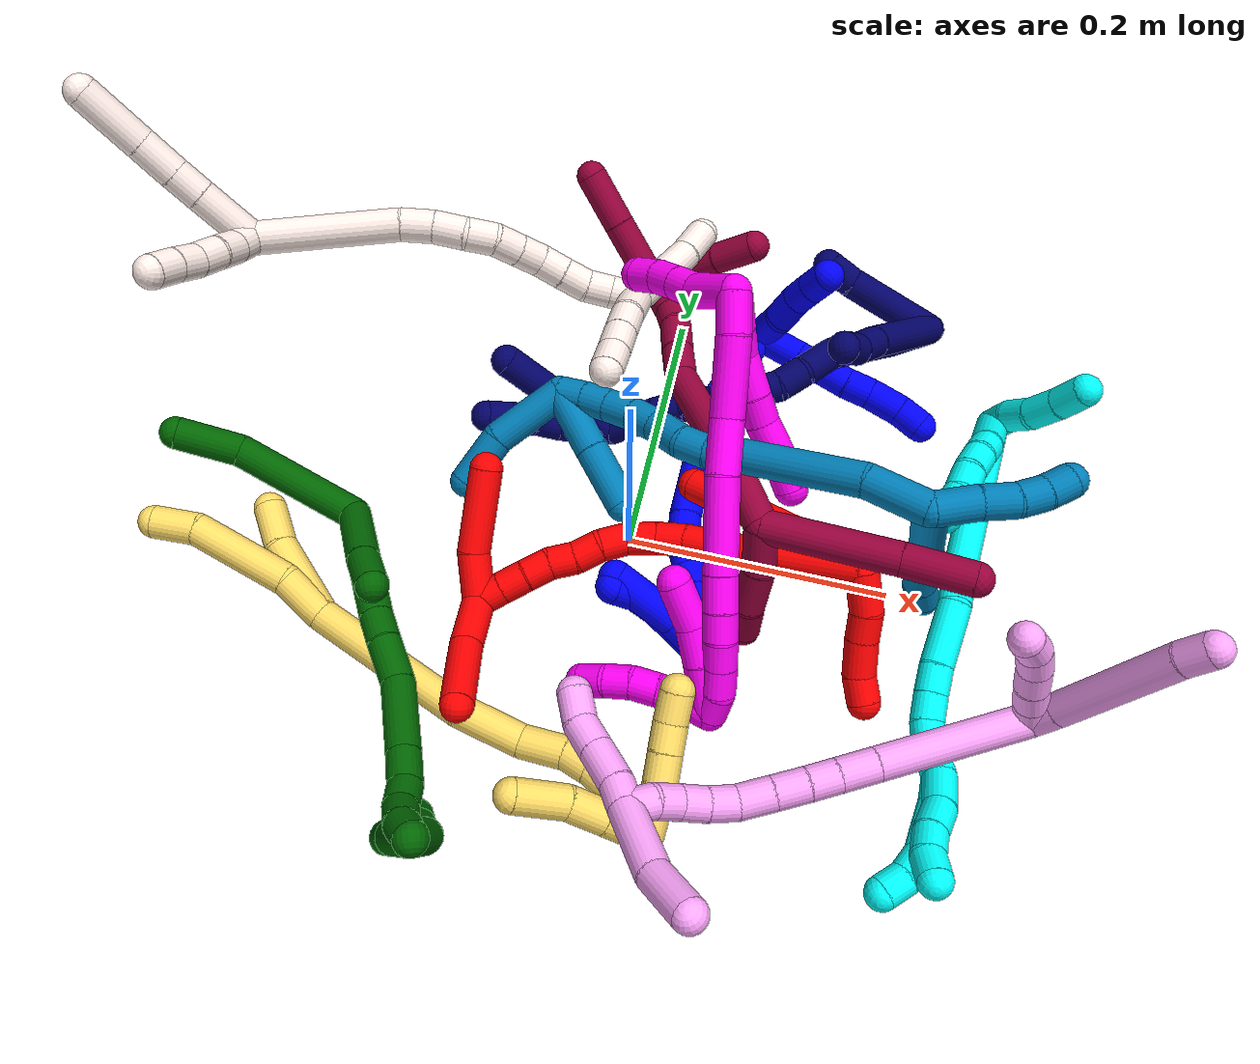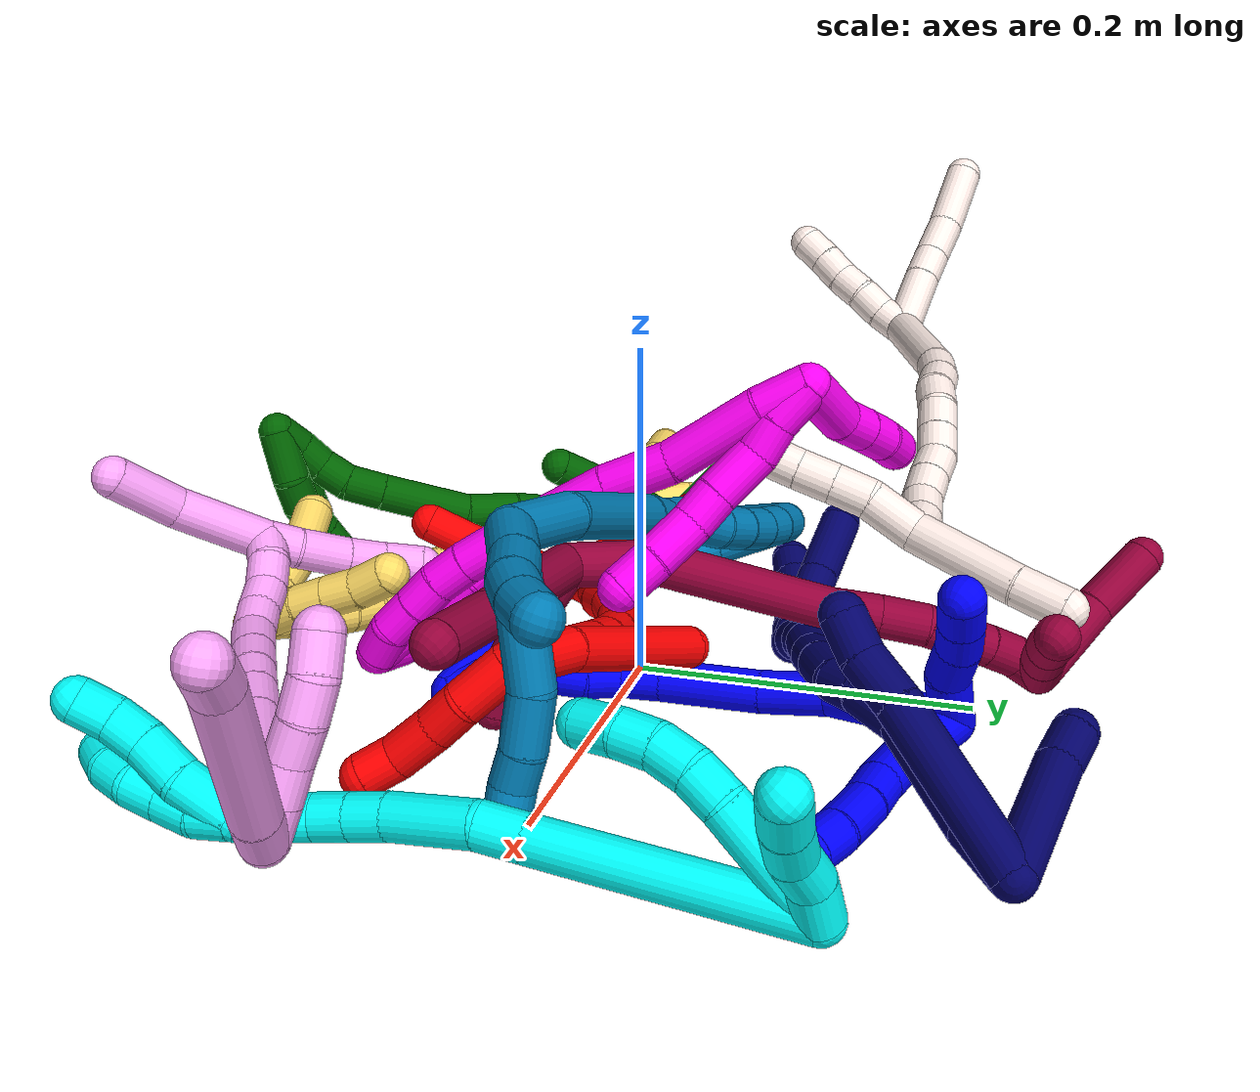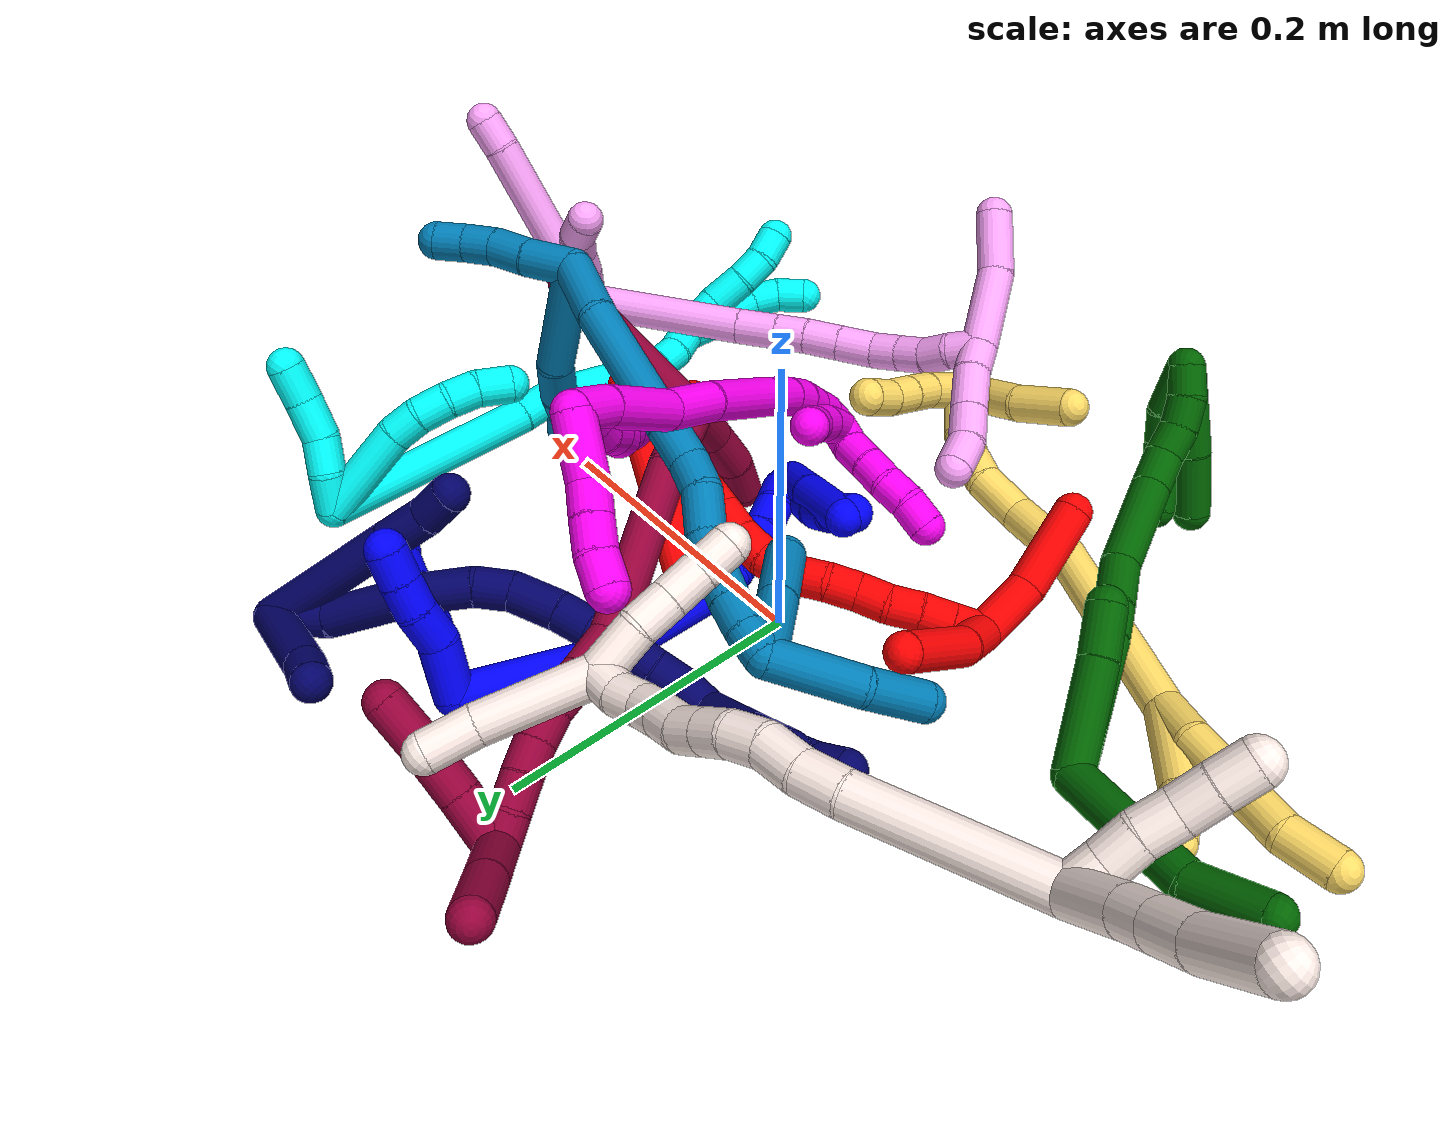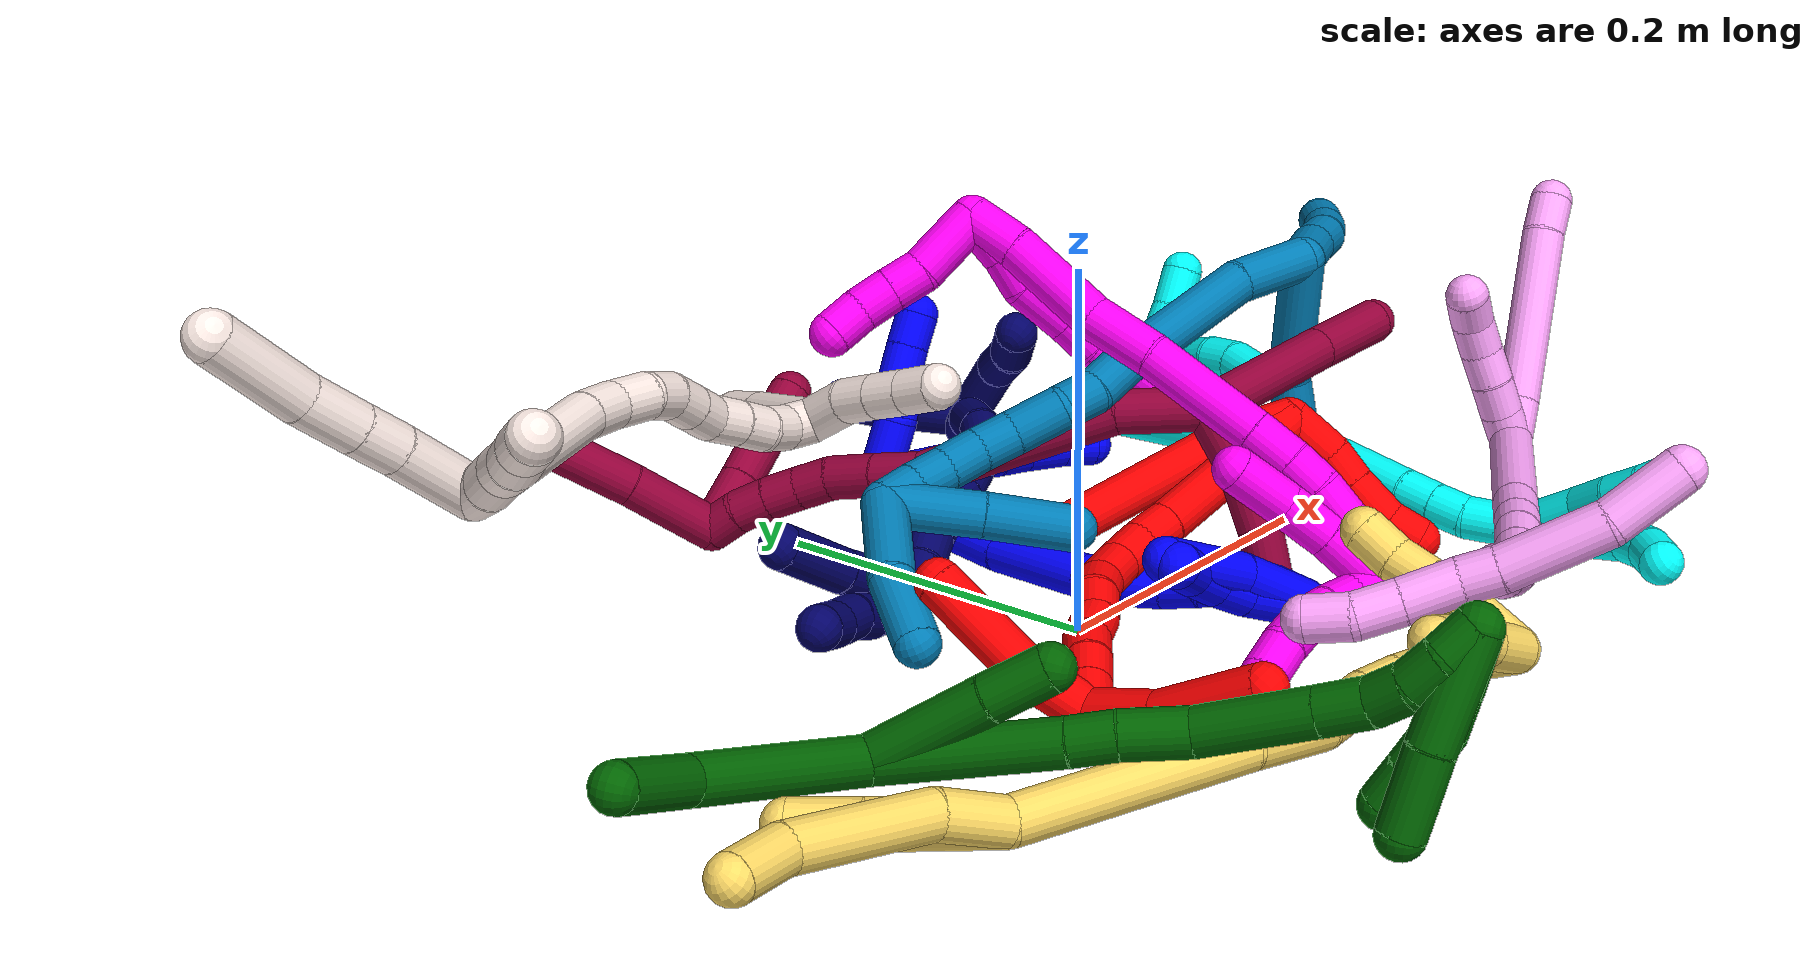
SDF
<sdf version="1.7">
 <world name="default">
  <plugin name="TubeGeneratorPlugin" filename="libtube_generator_plugin.so"/>
  <model name="photoneo_s_sensor">
   <static>1</static>
   <pose>0 0 2 1.57079 1.57079 3.14159</pose>
   <link name="link">
    <inertial><mass>0.1</mass></inertial>
    <sensor name="sensor" type="depth">
     <update_rate>30</update_rate>
     <camera>
      <horizontal_fov>1.22</horizontal_fov>
      <image><width>1920</width><height>1200</height><format>B8G8R8</format></image>
      <clip><near>0.1</near><far>4</far></clip>
      <depth_camera><output>points</output></depth_camera>
     </camera>
     <plugin name="camera_plugin" filename="libgazebo_ros_depth_camera.so">
      <baseline>0.2</baseline>
      <alwaysOn>1</alwaysOn>
      <updateRate>0.0</updateRate>
      <cameraName>camera_ir</cameraName>
      <imageTopicName>/camera/color/image_raw</imageTopicName>
      <cameraInfoTopicName>/camera/color/camera_info</cameraInfoTopicName>
      <depthImageTopicName>/camera/depth/image_raw</depthImageTopicName>
      <depthImageCameraInfoTopicName>/camera/depth/camera_info</depthImageCameraInfoTopicName>
      <pointCloudTopicName>/camera/depth/points</pointCloudTopicName>
      <frameName>fr_optical</frameName>
      <pointCloudCutoff>0.1</pointCloudCutoff>
      <pointCloudCutoffMax>2.0</pointCloudCutoffMax>
      <distortionK1>0</distortionK1>
      <distortionK2>0</distortionK2>
      <distortionK3>0</distortionK3>
      <distortionT1>0</distortionT1>
      <distortionT2>0</distortionT2>
      <CxPrime>0</CxPrime>
      <Cx>0</Cx>
      <Cy>0</Cy>
      <focalLength>0</focalLength>
      <hackBaseline>0</hackBaseline>
     </plugin>
    </sensor>
   </link>
  </model>
  <gravity>0 0 -9.8</gravity>
  <magnetic_field>6e-06 2.3e-05 -4.2e-05</magnetic_field>
  <atmosphere type="adiabatic"/>
  <physics name="default_physics" default="0" type="ode">
   <max_step_size>0.003</max_step_size>
   <real_time_factor>1</real_time_factor>
   <real_time_update_rate>1000</real_time_update_rate>
   <max_contacts>10000</max_contacts>
   <ode>
    <solver>
     <type>quick</type>
     <iters>100</iters>
     <sor>1.3</sor>
     <use_dynamic_moi_rescaling>0</use_dynamic_moi_rescaling>
    </solver>
    <constraints>
     <contact_max_correcting_vel>0</contact_max_correcting_vel>
     <contact_surface_layer>0.001</contact_surface_layer>
     <cfm>0</cfm>
     <erp>0.2</erp>
    </constraints>
   </ode>
  </physics>
  <scene><ambient>0.4 0.4 0.4 1</ambient><background>0.7 0.7 0.7 1</background><shadows>0</shadows></scene>
  <audio><device>default</device></audio>
  <spherical_coordinates>
   <surface_model>EARTH_WGS84</surface_model>
   <latitude_deg>0</latitude_deg>
   <longitude_deg>0</longitude_deg>
   <elevation>0</elevation>
   <heading_deg>0</heading_deg>
  </spherical_coordinates>
  <model name="bin">
   <static>1</static>
   <link name="bottom">
    <collision name="collision-bottom">
     <pose>0 0 -0.01 0 -0 0</pose>
     <geometry><box><size>0.8 0.6 0.02</size></box></geometry>
     <surface>
      <friction><ode><mu>100</mu><mu2>100</mu2></ode></friction>
      <contact><collide_bitmask>65535</collide_bitmask></contact>
     </surface>
    </collision>
   </link>
   <link name="west_wall">
    <collision name="collision-west_wall">
     <pose>-0.41 0 0.1 0 -0 0</pose>
     <geometry><box><size>0.02 0.6 0.2</size></box></geometry>
     <surface>
      <friction><ode><mu>100</mu><mu2>100</mu2></ode></friction>
      <contact><collide_bitmask>65535</collide_bitmask></contact>
     </surface>
    </collision>
   </link>
   <link name="east_wall">
    <collision name="collision-east_wall">
     <pose>0.41 0 0.1 0 -0 0</pose>
     <geometry><box><size>0.02 0.6 0.2</size></box></geometry>
     <surface>
      <friction><ode><mu>100</mu><mu2>100</mu2></ode></friction>
      <contact><collide_bitmask>65535</collide_bitmask></contact>
     </surface>
    </collision>
   </link>
   <link name="south_wall">
    <collision name="collision-south_wall">
     <pose>0 -0.31 0.1 0 -0 0</pose>
     <geometry><box><size>0.8 0.02 0.2</size></box></geometry>
     <surface>
      <friction><ode><mu>100</mu><mu2>100</mu2></ode></friction>
      <contact><collide_bitmask>65535</collide_bitmask></contact>
     </surface>
    </collision>
   </link>
   <link name="north_wall">
    <collision name="collision-north_wall">
     <pose>0 0.31 0.1 0 -0 0</pose>
     <geometry><box><size>0.8 0.02 0.2</size></box></geometry>
     <surface>
      <friction><ode><mu>100</mu><mu2>100</mu2></ode></friction>
      <contact><collide_bitmask>65535</collide_bitmask></contact>
     </surface>
    </collision>
   </link>
  </model>
  <model name="1">
   <static>0</static>
   <link name="1">
    <collision name="collision-cylinder-e_1_2_8">
     <pose>0.004521 0.003033 -0.018309 -2.97742 0.238963 -1.94003</pose>
     <geometry><cylinder><radius>0.0125</radius><length>0.038203</length></cylinder></geometry>
     <surface>
      <friction><ode><mu>1.16</mu><mu2>1.16</mu2><slip1>0</slip1><slip2>0</slip2></ode></friction>
      <contact><ode><kp>1e+06</kp><kd>1</kd><max_vel>0</max_vel><min_depth>0.001</min_depth></ode></contact>
     </surface>
    </collision>
    <visual name="visual-cylinder-e_1_2_8">
     <pose>0.004521 0.003033 -0.018309 -2.97742 0.238963 -1.94003</pose>
     <geometry><cylinder><radius>0.0125</radius><length>0.038203</length></cylinder></geometry>
     <material><ambient>0 0 1 1</ambient></material>
    </visual>
    <collision name="collision-cylinder-e_2_8_9">
     <pose>0.011756 0.007822 -0.047589 -2.98291 0.239567 -1.97403</pose>
     <geometry><cylinder><radius>0.0125</radius><length>0.022876</length></cylinder></geometry>
     <surface>
      <friction><ode><mu>1.16</mu><mu2>1.16</mu2><slip1>0</slip1><slip2>0</slip2></ode></friction>
      <contact><ode><kp>1e+06</kp><kd>1</kd><max_vel>0</max_vel><min_depth>0.001</min_depth></ode></contact>
     </surface>
    </collision>
    <visual name="visual-cylinder-e_2_8_9">
     <pose>0.011756 0.007822 -0.047589 -2.98291 0.239567 -1.97403</pose>
     <geometry><cylinder><radius>0.0125</radius><length>0.022876</length></cylinder></geometry>
     <material><ambient>0 0 1 1</ambient></material>
    </visual>
    <collision name="collision-cylinder-e_3_9_10">
     <pose>0.015677 0.011139 -0.068425 -2.98461 0.120246 -1.30646</pose>
     <geometry><cylinder><radius>0.0125</radius><length>0.020119</length></cylinder></geometry>
     <surface>
      <friction><ode><mu>1.16</mu><mu2>1.16</mu2><slip1>0</slip1><slip2>0</slip2></ode></friction>
      <contact><ode><kp>1e+06</kp><kd>1</kd><max_vel>0</max_vel><min_depth>0.001</min_depth></ode></contact>
     </surface>
    </collision>
    <visual name="visual-cylinder-e_3_9_10">
     <pose>0.015677 0.011139 -0.068425 -2.98461 0.120246 -1.30646</pose>
     <geometry><cylinder><radius>0.0125</radius><length>0.020119</length></cylinder></geometry>
     <material><ambient>0 0 1 1</ambient></material>
    </visual>
    <collision name="collision-cylinder-e_4_10_11">
     <pose>0.017791 0.015426 -0.088225 -2.87383 0.087797 -0.630513</pose>
     <geometry><cylinder><radius>0.0125</radius><length>0.020686</length></cylinder></geometry>
     <surface>
      <friction><ode><mu>1.16</mu><mu2>1.16</mu2><slip1>0</slip1><slip2>0</slip2></ode></friction>
      <contact><ode><kp>1e+06</kp><kd>1</kd><max_vel>0</max_vel><min_depth>0.001</min_depth></ode></contact>
     </surface>
    </collision>
    <visual name="visual-cylinder-e_4_10_11">
     <pose>0.017791 0.015426 -0.088225 -2.87383 0.087797 -0.630513</pose>
     <geometry><cylinder><radius>0.0125</radius><length>0.020686</length></cylinder></geometry>
     <material><ambient>0 0 1 1</ambient></material>
    </visual>
    <collision name="collision-cylinder-e_5_11_12">
     <pose>0.020698 0.020327 -0.111605 -2.98122 0.145879 -1.47584</pose>
     <geometry><cylinder><radius>0.0125</radius><length>0.027529</length></cylinder></geometry>
     <surface>
      <friction><ode><mu>1.16</mu><mu2>1.16</mu2><slip1>0</slip1><slip2>0</slip2></ode></friction>
      <contact><ode><kp>1e+06</kp><kd>1</kd><max_vel>0</max_vel><min_depth>0.001</min_depth></ode></contact>
     </surface>
    </collision>
    <visual name="visual-cylinder-e_5_11_12">
     <pose>0.020698 0.020327 -0.111605 -2.98122 0.145879 -1.47584</pose>
     <geometry><cylinder><radius>0.0125</radius><length>0.027529</length></cylinder></geometry>
     <material><ambient>0 0 1 1</ambient></material>
    </visual>
    <collision name="collision-cylinder-e_6_12_6">
     <pose>0.024575 0.022553 -0.13517 -3.13649 0.18322 -3.08604</pose>
     <geometry><cylinder><radius>0.0125</radius><length>0.020588</length></cylinder></geometry>
     <surface>
      <friction><ode><mu>1.16</mu><mu2>1.16</mu2><slip1>0</slip1><slip2>0</slip2></ode></friction>
      <contact><ode><kp>1e+06</kp><kd>1</kd><max_vel>0</max_vel><min_depth>0.001</min_depth></ode></contact>
     </surface>
    </collision>
    <visual name="visual-cylinder-e_6_12_6">
     <pose>0.024575 0.022553 -0.13517 -3.13649 0.18322 -3.08604</pose>
     <geometry><cylinder><radius>0.0125</radius><length>0.020588</length></cylinder></geometry>
     <material><ambient>0 0 1 1</ambient></material>
    </visual>
    <collision name="collision-cylinder-e_1_2_13">
     <pose>0.016081 0.007888 -0.001881 -1.80492 1.10375 -1.3246</pose>
     <geometry><cylinder><radius>0.0125</radius><length>0.036019</length></cylinder></geometry>
     <surface>
      <friction><ode><mu>1.16</mu><mu2>1.16</mu2><slip1>0</slip1><slip2>0</slip2></ode></friction>
      <contact><ode><kp>1e+06</kp><kd>1</kd><max_vel>0</max_vel><min_depth>0.001</min_depth></ode></contact>
     </surface>
    </collision>
    <visual name="visual-cylinder-e_1_2_13">
     <pose>0.016081 0.007888 -0.001881 -1.80492 1.10375 -1.3246</pose>
     <geometry><cylinder><radius>0.0125</radius><length>0.036019</length></cylinder></geometry>
     <material><ambient>0 0 1 1</ambient></material>
    </visual>
    <collision name="collision-cylinder-e_2_13_14">
     <pose>0.040679 0.024156 -0.004172 -1.61961 0.792878 -0.82826</pose>
     <geometry><cylinder><radius>0.0125</radius><length>0.023912</length></cylinder></geometry>
     <surface>
      <friction><ode><mu>1.16</mu><mu2>1.16</mu2><slip1>0</slip1><slip2>0</slip2></ode></friction>
      <contact><ode><kp>1e+06</kp><kd>1</kd><max_vel>0</max_vel><min_depth>0.001</min_depth></ode></contact>
     </surface>
    </collision>
    <visual name="visual-cylinder-e_2_13_14">
     <pose>0.040679 0.024156 -0.004172 -1.61961 0.792878 -0.82826</pose>
     <geometry><cylinder><radius>0.0125</radius><length>0.023912</length></cylinder></geometry>
     <material><ambient>0 0 1 1</ambient></material>
    </visual>
    <collision name="collision-cylinder-e_3_14_15">
     <pose>0.057082 0.038479 -0.00623 -1.84145 0.907169 -1.14027</pose>
     <geometry><cylinder><radius>0.0125</radius><length>0.020021</length></cylinder></geometry>
     <surface>
      <friction><ode><mu>1.16</mu><mu2>1.16</mu2><slip1>0</slip1><slip2>0</slip2></ode></friction>
      <contact><ode><kp>1e+06</kp><kd>1</kd><max_vel>0</max_vel><min_depth>0.001</min_depth></ode></contact>
     </surface>
    </collision>
    <visual name="visual-cylinder-e_3_14_15">
     <pose>0.057082 0.038479 -0.00623 -1.84145 0.907169 -1.14027</pose>
     <geometry><cylinder><radius>0.0125</radius><length>0.020021</length></cylinder></geometry>
     <material><ambient>0 0 1 1</ambient></material>
    </visual>
    <collision name="collision-cylinder-e_4_15_5">
     <pose>0.073092 0.049993 -0.009727 -1.89101 0.944984 -1.23211</pose>
     <geometry><cylinder><radius>0.0125</radius><length>0.020048</length></cylinder></geometry>
     <surface>
      <friction><ode><mu>1.16</mu><mu2>1.16</mu2><slip1>0</slip1><slip2>0</slip2></ode></friction>
      <contact><ode><kp>1e+06</kp><kd>1</kd><max_vel>0</max_vel><min_depth>0.001</min_depth></ode></contact>
     </surface>
    </collision>
    <visual name="visual-cylinder-e_4_15_5">
     <pose>0.073092 0.049993 -0.009727 -1.89101 0.944984 -1.23211</pose>
     <geometry><cylinder><radius>0.0125</radius><length>0.020048</length></cylinder></geometry>
     <material><ambient>0 0 1 1</ambient></material>
    </visual>
    <collision name="collision-cylinder-e_1_2_16">
     <pose>0.012563 -0.035444 -0.004057 1.68476 0.338587 0.378632</pose>
     <geometry><cylinder><radius>0.0125</radius><length>0.075645</length></cylinder></geometry>
     <surface>
      <friction><ode><mu>1.16</mu><mu2>1.16</mu2><slip1>0</slip1><slip2>0</slip2></ode></friction>
      <contact><ode><kp>1e+06</kp><kd>1</kd><max_vel>0</max_vel><min_depth>0.001</min_depth></ode></contact>
     </surface>
    </collision>
    <visual name="visual-cylinder-e_1_2_16">
     <pose>0.012563 -0.035444 -0.004057 1.68476 0.338587 0.378632</pose>
     <geometry><cylinder><radius>0.0125</radius><length>0.075645</length></cylinder></geometry>
     <material><ambient>0 0 1 1</ambient></material>
    </visual>
    <collision name="collision-cylinder-e_2_16_17">
     <pose>0.031738 -0.087985 -0.015956 2.00083 0.338022 0.519953</pose>
     <geometry><cylinder><radius>0.0125</radius><length>0.039878</length></cylinder></geometry>
     <surface>
      <friction><ode><mu>1.16</mu><mu2>1.16</mu2><slip1>0</slip1><slip2>0</slip2></ode></friction>
      <contact><ode><kp>1e+06</kp><kd>1</kd><max_vel>0</max_vel><min_depth>0.001</min_depth></ode></contact>
     </surface>
    </collision>
    <visual name="visual-cylinder-e_2_16_17">
     <pose>0.031738 -0.087985 -0.015956 2.00083 0.338022 0.519953</pose>
     <geometry><cylinder><radius>0.0125</radius><length>0.039878</length></cylinder></geometry>
     <material><ambient>0 0 1 1</ambient></material>
    </visual>
    <collision name="collision-cylinder-e_3_17_18">
     <pose>0.051025 -0.129416 -0.035437 2.01693 0.439277 0.680887</pose>
     <geometry><cylinder><radius>0.0125</radius><length>0.059606</length></cylinder></geometry>
     <surface>
      <friction><ode><mu>1.16</mu><mu2>1.16</mu2><slip1>0</slip1><slip2>0</slip2></ode></friction>
      <contact><ode><kp>1e+06</kp><kd>1</kd><max_vel>0</max_vel><min_depth>0.001</min_depth></ode></contact>
     </surface>
    </collision>
    <visual name="visual-cylinder-e_3_17_18">
     <pose>0.051025 -0.129416 -0.035437 2.01693 0.439277 0.680887</pose>
     <geometry><cylinder><radius>0.0125</radius><length>0.059606</length></cylinder></geometry>
     <material><ambient>0 0 1 1</ambient></material>
    </visual>
    <collision name="collision-cylinder-e_4_18_19">
     <pose>0.069439 -0.16252 -0.053165 2.17777 0.493182 0.897071</pose>
     <geometry><cylinder><radius>0.0125</radius><length>0.024244</length></cylinder></geometry>
     <surface>
      <friction><ode><mu>1.16</mu><mu2>1.16</mu2><slip1>0</slip1><slip2>0</slip2></ode></friction>
      <contact><ode><kp>1e+06</kp><kd>1</kd><max_vel>0</max_vel><min_depth>0.001</min_depth></ode></contact>
     </surface>
    </collision>
    <visual name="visual-cylinder-e_4_18_19">
     <pose>0.069439 -0.16252 -0.053165 2.17777 0.493182 0.897071</pose>
     <geometry><cylinder><radius>0.0125</radius><length>0.024244</length></cylinder></geometry>
     <material><ambient>0 0 1 1</ambient></material>
    </visual>
    <collision name="collision-cylinder-e_5_19_20">
     <pose>0.079832 -0.176713 -0.066647 2.50857 0.469852 1.26217</pose>
     <geometry><cylinder><radius>0.0125</radius><length>0.020563</length></cylinder></geometry>
     <surface>
      <friction><ode><mu>1.16</mu><mu2>1.16</mu2><slip1>0</slip1><slip2>0</slip2></ode></friction>
      <contact><ode><kp>1e+06</kp><kd>1</kd><max_vel>0</max_vel><min_depth>0.001</min_depth></ode></contact>
     </surface>
    </collision>
    <visual name="visual-cylinder-e_5_19_20">
     <pose>0.079832 -0.176713 -0.066647 2.50857 0.469852 1.26217</pose>
     <geometry><cylinder><radius>0.0125</radius><length>0.020563</length></cylinder></geometry>
     <material><ambient>0 0 1 1</ambient></material>
    </visual>
    <collision name="collision-cylinder-e_6_20_21">
     <pose>0.090445 -0.187645 -0.079917 2.38869 0.636673 1.38985</pose>
     <geometry><cylinder><radius>0.0125</radius><length>0.02004</length></cylinder></geometry>
     <surface>
      <friction><ode><mu>1.16</mu><mu2>1.16</mu2><slip1>0</slip1><slip2>0</slip2></ode></friction>
      <contact><ode><kp>1e+06</kp><kd>1</kd><max_vel>0</max_vel><min_depth>0.001</min_depth></ode></contact>
     </surface>
    </collision>
    <visual name="visual-cylinder-e_6_20_21">
     <pose>0.090445 -0.187645 -0.079917 2.38869 0.636673 1.38985</pose>
     <geometry><cylinder><radius>0.0125</radius><length>0.02004</length></cylinder></geometry>
     <material><ambient>0 0 1 1</ambient></material>
    </visual>
    <collision name="collision-cylinder-e_7_21_22">
     <pose>0.1019 -0.197452 -0.092968 2.60172 0.581696 1.64938</pose>
     <geometry><cylinder><radius>0.0125</radius><length>0.020014</length></cylinder></geometry>
     <surface>
      <friction><ode><mu>1.16</mu><mu2>1.16</mu2><slip1>0</slip1><slip2>0</slip2></ode></friction>
      <contact><ode><kp>1e+06</kp><kd>1</kd><max_vel>0</max_vel><min_depth>0.001</min_depth></ode></contact>
     </surface>
    </collision>
    <visual name="visual-cylinder-e_7_21_22">
     <pose>0.1019 -0.197452 -0.092968 2.60172 0.581696 1.64938</pose>
     <geometry><cylinder><radius>0.0125</radius><length>0.020014</length></cylinder></geometry>
     <material><ambient>0 0 1 1</ambient></material>
    </visual>
    <collision name="collision-cylinder-e_8_22_23">
     <pose>0.110501 -0.206091 -0.108599 2.66744 0.315403 1.16416</pose>
     <geometry><cylinder><radius>0.0125</radius><length>0.020002</length></cylinder></geometry>
     <surface>
      <friction><ode><mu>1.16</mu><mu2>1.16</mu2><slip1>0</slip1><slip2>0</slip2></ode></friction>
      <contact><ode><kp>1e+06</kp><kd>1</kd><max_vel>0</max_vel><min_depth>0.001</min_depth></ode></contact>
     </surface>
    </collision>
    <visual name="visual-cylinder-e_8_22_23">
     <pose>0.110501 -0.206091 -0.108599 2.66744 0.315403 1.16416</pose>
     <geometry><cylinder><radius>0.0125</radius><length>0.020002</length></cylinder></geometry>
     <material><ambient>0 0 1 1</ambient></material>
    </visual>
    <collision name="collision-cylinder-e_9_23_1">
     <pose>0.114429 -0.216761 -0.124762 2.4539 0.082688 0.230037</pose>
     <geometry><cylinder><radius>0.0125</radius><length>0.020008</length></cylinder></geometry>
     <surface>
      <friction><ode><mu>1.16</mu><mu2>1.16</mu2><slip1>0</slip1><slip2>0</slip2></ode></friction>
      <contact><ode><kp>1e+06</kp><kd>1</kd><max_vel>0</max_vel><min_depth>0.001</min_depth></ode></contact>
     </surface>
    </collision>
    <visual name="visual-cylinder-e_9_23_1">
     <pose>0.114429 -0.216761 -0.124762 2.4539 0.082688 0.230037</pose>
     <geometry><cylinder><radius>0.0125</radius><length>0.020008</length></cylinder></geometry>
     <material><ambient>0 0 1 1</ambient></material>
    </visual>
    <collision name="collision-cylinder-e_1_1_24">
     <pose>0.11525 -0.223024 -0.122466 -0.006593 -0.000563 2e-06</pose>
     <geometry><cylinder><radius>0.0125</radius><length>0.02</length></cylinder></geometry>
     <surface>
      <friction><ode><mu>1.16</mu><mu2>1.16</mu2><slip1>0</slip1><slip2>0</slip2></ode></friction>
      <contact><ode><kp>1e+06</kp><kd>1</kd><max_vel>0</max_vel><min_depth>0.001</min_depth></ode></contact>
     </surface>
    </collision>
    <visual name="visual-cylinder-e_1_1_24">
     <pose>0.11525 -0.223024 -0.122466 -0.006593 -0.000563 2e-06</pose>
     <geometry><cylinder><radius>0.0125</radius><length>0.02</length></cylinder></geometry>
     <material><ambient>0 0 1 1</ambient></material>
    </visual>
    <collision name="collision-cylinder-e_2_24_25">
     <pose>0.115597 -0.222086 -0.102511 -0.087309 0.035286 -0.001542</pose>
     <geometry><cylinder><radius>0.0125</radius><length>0.02</length></cylinder></geometry>
     <surface>
      <friction><ode><mu>1.16</mu><mu2>1.16</mu2><slip1>0</slip1><slip2>0</slip2></ode></friction>
      <contact><ode><kp>1e+06</kp><kd>1</kd><max_vel>0</max_vel><min_depth>0.001</min_depth></ode></contact>
     </surface>
    </collision>
    <visual name="visual-cylinder-e_2_24_25">
     <pose>0.115597 -0.222086 -0.102511 -0.087309 0.035286 -0.001542</pose>
     <geometry><cylinder><radius>0.0125</radius><length>0.02</length></cylinder></geometry>
     <material><ambient>0 0 1 1</ambient></material>
    </visual>
    <collision name="collision-cylinder-e_3_25_26">
     <pose>0.117786 -0.220536 -0.082748 -0.069114 0.184667 -0.006402</pose>
     <geometry><cylinder><radius>0.0125</radius><length>0.02</length></cylinder></geometry>
     <surface>
      <friction><ode><mu>1.16</mu><mu2>1.16</mu2><slip1>0</slip1><slip2>0</slip2></ode></friction>
      <contact><ode><kp>1e+06</kp><kd>1</kd><max_vel>0</max_vel><min_depth>0.001</min_depth></ode></contact>
     </surface>
    </collision>
    <visual name="visual-cylinder-e_3_25_26">
     <pose>0.117786 -0.220536 -0.082748 -0.069114 0.184667 -0.006402</pose>
     <geometry><cylinder><radius>0.0125</radius><length>0.02</length></cylinder></geometry>
     <material><ambient>0 0 1 1</ambient></material>
    </visual>
    <collision name="collision-cylinder-e_4_26_27">
     <pose>0.122891 -0.220509 -0.063514 0.068997 0.33299 0.0116</pose>
     <geometry><cylinder><radius>0.0125</radius><length>0.02</length></cylinder></geometry>
     <surface>
      <friction><ode><mu>1.16</mu><mu2>1.16</mu2><slip1>0</slip1><slip2>0</slip2></ode></friction>
      <contact><ode><kp>1e+06</kp><kd>1</kd><max_vel>0</max_vel><min_depth>0.001</min_depth></ode></contact>
     </surface>
    </collision>
    <visual name="visual-cylinder-e_4_26_27">
     <pose>0.122891 -0.220509 -0.063514 0.068997 0.33299 0.0116</pose>
     <geometry><cylinder><radius>0.0125</radius><length>0.02</length></cylinder></geometry>
     <material><ambient>0 0 1 1</ambient></material>
    </visual>
    <collision name="collision-cylinder-e_5_27_4">
     <pose>0.130679 -0.224361 -0.045759 0.36695 0.468924 0.088587</pose>
     <geometry><cylinder><radius>0.0125</radius><length>0.02</length></cylinder></geometry>
     <surface>
      <friction><ode><mu>1.16</mu><mu2>1.16</mu2><slip1>0</slip1><slip2>0</slip2></ode></friction>
      <contact><ode><kp>1e+06</kp><kd>1</kd><max_vel>0</max_vel><min_depth>0.001</min_depth></ode></contact>
     </surface>
    </collision>
    <visual name="visual-cylinder-e_5_27_4">
     <pose>0.130679 -0.224361 -0.045759 0.36695 0.468924 0.088587</pose>
     <geometry><cylinder><radius>0.0125</radius><length>0.02</length></cylinder></geometry>
     <material><ambient>0 0 1 1</ambient></material>
    </visual>
    <collision name="collision-cylinder-e_1_1_28">
     <pose>0.120263 -0.220548 -0.109665 -0.110993 0.214901 -0.011985</pose>
     <geometry><cylinder><radius>0.0125</radius><length>0.046964</length></cylinder></geometry>
     <surface>
      <friction><ode><mu>1.16</mu><mu2>1.16</mu2><slip1>0</slip1><slip2>0</slip2></ode></friction>
      <contact><ode><kp>1e+06</kp><kd>1</kd><max_vel>0</max_vel><min_depth>0.001</min_depth></ode></contact>
     </surface>
    </collision>
    <visual name="visual-cylinder-e_1_1_28">
     <pose>0.120263 -0.220548 -0.109665 -0.110993 0.214901 -0.011985</pose>
     <geometry><cylinder><radius>0.0125</radius><length>0.046964</length></cylinder></geometry>
     <material><ambient>0 0 1 1</ambient></material>
    </visual>
    <collision name="collision-cylinder-e_2_28_3">
     <pose>0.129016 -0.21942 -0.06065 0.053851 0.141714 0.003823</pose>
     <geometry><cylinder><radius>0.0125</radius><length>0.053036</length></cylinder></geometry>
     <surface>
      <friction><ode><mu>1.16</mu><mu2>1.16</mu2><slip1>0</slip1><slip2>0</slip2></ode></friction>
      <contact><ode><kp>1e+06</kp><kd>1</kd><max_vel>0</max_vel><min_depth>0.001</min_depth></ode></contact>
     </surface>
    </collision>
    <visual name="visual-cylinder-e_2_28_3">
     <pose>0.129016 -0.21942 -0.06065 0.053851 0.141714 0.003823</pose>
     <geometry><cylinder><radius>0.0125</radius><length>0.053036</length></cylinder></geometry>
     <material><ambient>0 0 1 1</ambient></material>
    </visual>
    <collision name="collision-sphere-3">
     <pose>0.132762 -0.220833 -0.034436 0 -0 0</pose>
     <geometry><sphere><radius>0.0125</radius></sphere></geometry>
     <surface>
      <friction><ode><mu>1.16</mu><mu2>1.16</mu2><slip1>0</slip1><slip2>0</slip2></ode></friction>
      <contact><ode><kp>1e+06</kp><kd>1</kd><max_vel>0</max_vel><min_depth>0.001</min_depth></ode></contact>
     </surface>
    </collision>
    <visual name="visual-sphere-3">
     <pose>0.132762 -0.220833 -0.034436 0 -0 0</pose>
     <geometry><sphere><radius>0.0125</radius></sphere></geometry>
     <material><ambient>0 0 1 1</ambient></material>
    </visual>
    <collision name="collision-sphere-28">
     <pose>0.125271 -0.218007 -0.086864 0 -0 0</pose>
     <geometry><sphere><radius>0.0125</radius></sphere></geometry>
     <surface>
      <friction><ode><mu>1.16</mu><mu2>1.16</mu2><slip1>0</slip1><slip2>0</slip2></ode></friction>
      <contact><ode><kp>1e+06</kp><kd>1</kd><max_vel>0</max_vel><min_depth>0.001</min_depth></ode></contact>
     </surface>
    </collision>
    <visual name="visual-sphere-28">
     <pose>0.125271 -0.218007 -0.086864 0 -0 0</pose>
     <geometry><sphere><radius>0.0125</radius></sphere></geometry>
     <material><ambient>0 0 1 1</ambient></material>
    </visual>
    <collision name="collision-sphere-4">
     <pose>0.135198 -0.227561 -0.037432 0 -0 0</pose>
     <geometry><sphere><radius>0.0125</radius></sphere></geometry>
     <surface>
      <friction><ode><mu>1.16</mu><mu2>1.16</mu2><slip1>0</slip1><slip2>0</slip2></ode></friction>
      <contact><ode><kp>1e+06</kp><kd>1</kd><max_vel>0</max_vel><min_depth>0.001</min_depth></ode></contact>
     </surface>
    </collision>
    <visual name="visual-sphere-4">
     <pose>0.135198 -0.227561 -0.037432 0 -0 0</pose>
     <geometry><sphere><radius>0.0125</radius></sphere></geometry>
     <material><ambient>0 0 1 1</ambient></material>
    </visual>
    <collision name="collision-sphere-27">
     <pose>0.12616 -0.22116 -0.054085 0 -0 0</pose>
     <geometry><sphere><radius>0.0125</radius></sphere></geometry>
     <surface>
      <friction><ode><mu>1.16</mu><mu2>1.16</mu2><slip1>0</slip1><slip2>0</slip2></ode></friction>
      <contact><ode><kp>1e+06</kp><kd>1</kd><max_vel>0</max_vel><min_depth>0.001</min_depth></ode></contact>
     </surface>
    </collision>
    <visual name="visual-sphere-27">
     <pose>0.12616 -0.22116 -0.054085 0 -0 0</pose>
     <geometry><sphere><radius>0.0125</radius></sphere></geometry>
     <material><ambient>0 0 1 1</ambient></material>
    </visual>
    <collision name="collision-sphere-26">
     <pose>0.119622 -0.219857 -0.072942 0 -0 0</pose>
     <geometry><sphere><radius>0.0125</radius></sphere></geometry>
     <surface>
      <friction><ode><mu>1.16</mu><mu2>1.16</mu2><slip1>0</slip1><slip2>0</slip2></ode></friction>
      <contact><ode><kp>1e+06</kp><kd>1</kd><max_vel>0</max_vel><min_depth>0.001</min_depth></ode></contact>
     </surface>
    </collision>
    <visual name="visual-sphere-26">
     <pose>0.119622 -0.219857 -0.072942 0 -0 0</pose>
     <geometry><sphere><radius>0.0125</radius></sphere></geometry>
     <material><ambient>0 0 1 1</ambient></material>
    </visual>
    <collision name="collision-sphere-25">
     <pose>0.11595 -0.221215 -0.092555 0 -0 0</pose>
     <geometry><sphere><radius>0.0125</radius></sphere></geometry>
     <surface>
      <friction><ode><mu>1.16</mu><mu2>1.16</mu2><slip1>0</slip1><slip2>0</slip2></ode></friction>
      <contact><ode><kp>1e+06</kp><kd>1</kd><max_vel>0</max_vel><min_depth>0.001</min_depth></ode></contact>
     </surface>
    </collision>
    <visual name="visual-sphere-25">
     <pose>0.11595 -0.221215 -0.092555 0 -0 0</pose>
     <geometry><sphere><radius>0.0125</radius></sphere></geometry>
     <material><ambient>0 0 1 1</ambient></material>
    </visual>
    <collision name="collision-sphere-24">
     <pose>0.115244 -0.222958 -0.112466 0 -0 0</pose>
     <geometry><sphere><radius>0.0125</radius></sphere></geometry>
     <surface>
      <friction><ode><mu>1.16</mu><mu2>1.16</mu2><slip1>0</slip1><slip2>0</slip2></ode></friction>
      <contact><ode><kp>1e+06</kp><kd>1</kd><max_vel>0</max_vel><min_depth>0.001</min_depth></ode></contact>
     </surface>
    </collision>
    <visual name="visual-sphere-24">
     <pose>0.115244 -0.222958 -0.112466 0 -0 0</pose>
     <geometry><sphere><radius>0.0125</radius></sphere></geometry>
     <material><ambient>0 0 1 1</ambient></material>
    </visual>
    <collision name="collision-sphere-1">
     <pose>0.115256 -0.223089 -0.132466 0 -0 0</pose>
     <geometry><sphere><radius>0.0125</radius></sphere></geometry>
     <surface>
      <friction><ode><mu>1.16</mu><mu2>1.16</mu2><slip1>0</slip1><slip2>0</slip2></ode></friction>
      <contact><ode><kp>1e+06</kp><kd>1</kd><max_vel>0</max_vel><min_depth>0.001</min_depth></ode></contact>
     </surface>
    </collision>
    <visual name="visual-sphere-1">
     <pose>0.115256 -0.223089 -0.132466 0 -0 0</pose>
     <geometry><sphere><radius>0.0125</radius></sphere></geometry>
     <material><ambient>0 0 1 1</ambient></material>
    </visual>
    <collision name="collision-sphere-23">
     <pose>0.113603 -0.210433 -0.117058 0 -0 0</pose>
     <geometry><sphere><radius>0.0125</radius></sphere></geometry>
     <surface>
      <friction><ode><mu>1.16</mu><mu2>1.16</mu2><slip1>0</slip1><slip2>0</slip2></ode></friction>
      <contact><ode><kp>1e+06</kp><kd>1</kd><max_vel>0</max_vel><min_depth>0.001</min_depth></ode></contact>
     </surface>
    </collision>
    <visual name="visual-sphere-23">
     <pose>0.113603 -0.210433 -0.117058 0 -0 0</pose>
     <geometry><sphere><radius>0.0125</radius></sphere></geometry>
     <material><ambient>0 0 1 1</ambient></material>
    </visual>
    <collision name="collision-sphere-22">
     <pose>0.107398 -0.20175 -0.100141 0 -0 0</pose>
     <geometry><sphere><radius>0.0125</radius></sphere></geometry>
     <surface>
      <friction><ode><mu>1.16</mu><mu2>1.16</mu2><slip1>0</slip1><slip2>0</slip2></ode></friction>
      <contact><ode><kp>1e+06</kp><kd>1</kd><max_vel>0</max_vel><min_depth>0.001</min_depth></ode></contact>
     </surface>
    </collision>
    <visual name="visual-sphere-22">
     <pose>0.107398 -0.20175 -0.100141 0 -0 0</pose>
     <geometry><sphere><radius>0.0125</radius></sphere></geometry>
     <material><ambient>0 0 1 1</ambient></material>
    </visual>
    <collision name="collision-sphere-21">
     <pose>0.096402 -0.193154 -0.085796 0 -0 0</pose>
     <geometry><sphere><radius>0.0125</radius></sphere></geometry>
     <surface>
      <friction><ode><mu>1.16</mu><mu2>1.16</mu2><slip1>0</slip1><slip2>0</slip2></ode></friction>
      <contact><ode><kp>1e+06</kp><kd>1</kd><max_vel>0</max_vel><min_depth>0.001</min_depth></ode></contact>
     </surface>
    </collision>
    <visual name="visual-sphere-21">
     <pose>0.096402 -0.193154 -0.085796 0 -0 0</pose>
     <geometry><sphere><radius>0.0125</radius></sphere></geometry>
     <material><ambient>0 0 1 1</ambient></material>
    </visual>
    <collision name="collision-sphere-12">
     <pose>0.022699 0.022502 -0.125048 0 -0 0</pose>
     <geometry><sphere><radius>0.0125</radius></sphere></geometry>
     <surface>
      <friction><ode><mu>1.16</mu><mu2>1.16</mu2><slip1>0</slip1><slip2>0</slip2></ode></friction>
      <contact><ode><kp>1e+06</kp><kd>1</kd><max_vel>0</max_vel><min_depth>0.001</min_depth></ode></contact>
     </surface>
    </collision>
    <visual name="visual-sphere-12">
     <pose>0.022699 0.022502 -0.125048 0 -0 0</pose>
     <geometry><sphere><radius>0.0125</radius></sphere></geometry>
     <material><ambient>0 0 1 1</ambient></material>
    </visual>
    <collision name="collision-sphere-11">
     <pose>0.018698 0.018152 -0.098161 0 -0 0</pose>
     <geometry><sphere><radius>0.0125</radius></sphere></geometry>
     <surface>
      <friction><ode><mu>1.16</mu><mu2>1.16</mu2><slip1>0</slip1><slip2>0</slip2></ode></friction>
      <contact><ode><kp>1e+06</kp><kd>1</kd><max_vel>0</max_vel><min_depth>0.001</min_depth></ode></contact>
     </surface>
    </collision>
    <visual name="visual-sphere-11">
     <pose>0.018698 0.018152 -0.098161 0 -0 0</pose>
     <geometry><sphere><radius>0.0125</radius></sphere></geometry>
     <material><ambient>0 0 1 1</ambient></material>
    </visual>
    <collision name="collision-sphere-10">
     <pose>0.016884 0.0127 -0.078289 0 -0 0</pose>
     <geometry><sphere><radius>0.0125</radius></sphere></geometry>
     <surface>
      <friction><ode><mu>1.16</mu><mu2>1.16</mu2><slip1>0</slip1><slip2>0</slip2></ode></friction>
      <contact><ode><kp>1e+06</kp><kd>1</kd><max_vel>0</max_vel><min_depth>0.001</min_depth></ode></contact>
     </surface>
    </collision>
    <visual name="visual-sphere-10">
     <pose>0.016884 0.0127 -0.078289 0 -0 0</pose>
     <geometry><sphere><radius>0.0125</radius></sphere></geometry>
     <material><ambient>0 0 1 1</ambient></material>
    </visual>
    <collision name="collision-sphere-9">
     <pose>0.01447 0.009578 -0.058561 0 -0 0</pose>
     <geometry><sphere><radius>0.0125</radius></sphere></geometry>
     <surface>
      <friction><ode><mu>1.16</mu><mu2>1.16</mu2><slip1>0</slip1><slip2>0</slip2></ode></friction>
      <contact><ode><kp>1e+06</kp><kd>1</kd><max_vel>0</max_vel><min_depth>0.001</min_depth></ode></contact>
     </surface>
    </collision>
    <visual name="visual-sphere-9">
     <pose>0.01447 0.009578 -0.058561 0 -0 0</pose>
     <geometry><sphere><radius>0.0125</radius></sphere></geometry>
     <material><ambient>0 0 1 1</ambient></material>
    </visual>
    <collision name="collision-sphere-2">
     <geometry><sphere><radius>0.0125</radius></sphere></geometry>
     <surface>
      <friction><ode><mu>1.16</mu><mu2>1.16</mu2><slip1>0</slip1><slip2>0</slip2></ode></friction>
      <contact><ode><kp>1e+06</kp><kd>1</kd><max_vel>0</max_vel><min_depth>0.001</min_depth></ode></contact>
     </surface>
    </collision>
    <visual name="visual-sphere-2">
     <geometry><sphere><radius>0.0125</radius></sphere></geometry>
     <material><ambient>0 0 1 1</ambient></material>
    </visual>
    <collision name="collision-sphere-19">
     <pose>0.075177 -0.17129 -0.059256 0 -0 0</pose>
     <geometry><sphere><radius>0.0125</radius></sphere></geometry>
     <surface>
      <friction><ode><mu>1.16</mu><mu2>1.16</mu2><slip1>0</slip1><slip2>0</slip2></ode></friction>
      <contact><ode><kp>1e+06</kp><kd>1</kd><max_vel>0</max_vel><min_depth>0.001</min_depth></ode></contact>
     </surface>
    </collision>
    <visual name="visual-sphere-19">
     <pose>0.075177 -0.17129 -0.059256 0 -0 0</pose>
     <geometry><sphere><radius>0.0125</radius></sphere></geometry>
     <material><ambient>0 0 1 1</ambient></material>
    </visual>
    <collision name="collision-sphere-8">
     <pose>0.009042 0.006066 -0.036618 0 -0 0</pose>
     <geometry><sphere><radius>0.0125</radius></sphere></geometry>
     <surface>
      <friction><ode><mu>1.16</mu><mu2>1.16</mu2><slip1>0</slip1><slip2>0</slip2></ode></friction>
      <contact><ode><kp>1e+06</kp><kd>1</kd><max_vel>0</max_vel><min_depth>0.001</min_depth></ode></contact>
     </surface>
    </collision>
    <visual name="visual-sphere-8">
     <pose>0.009042 0.006066 -0.036618 0 -0 0</pose>
     <geometry><sphere><radius>0.0125</radius></sphere></geometry>
     <material><ambient>0 0 1 1</ambient></material>
    </visual>
    <collision name="collision-sphere-6">
     <pose>0.02645 0.022605 -0.145291 0 -0 0</pose>
     <geometry><sphere><radius>0.0125</radius></sphere></geometry>
     <surface>
      <friction><ode><mu>1.16</mu><mu2>1.16</mu2><slip1>0</slip1><slip2>0</slip2></ode></friction>
      <contact><ode><kp>1e+06</kp><kd>1</kd><max_vel>0</max_vel><min_depth>0.001</min_depth></ode></contact>
     </surface>
    </collision>
    <visual name="visual-sphere-6">
     <pose>0.02645 0.022605 -0.145291 0 -0 0</pose>
     <geometry><sphere><radius>0.0125</radius></sphere></geometry>
     <material><ambient>0 0 1 1</ambient></material>
    </visual>
    <collision name="collision-sphere-13">
     <pose>0.032161 0.015775 -0.003762 0 -0 0</pose>
     <geometry><sphere><radius>0.0125</radius></sphere></geometry>
     <surface>
      <friction><ode><mu>1.16</mu><mu2>1.16</mu2><slip1>0</slip1><slip2>0</slip2></ode></friction>
      <contact><ode><kp>1e+06</kp><kd>1</kd><max_vel>0</max_vel><min_depth>0.001</min_depth></ode></contact>
     </surface>
    </collision>
    <visual name="visual-sphere-13">
     <pose>0.032161 0.015775 -0.003762 0 -0 0</pose>
     <geometry><sphere><radius>0.0125</radius></sphere></geometry>
     <material><ambient>0 0 1 1</ambient></material>
    </visual>
    <collision name="collision-sphere-14">
     <pose>0.049196 0.032537 -0.004581 0 -0 0</pose>
     <geometry><sphere><radius>0.0125</radius></sphere></geometry>
     <surface>
      <friction><ode><mu>1.16</mu><mu2>1.16</mu2><slip1>0</slip1><slip2>0</slip2></ode></friction>
      <contact><ode><kp>1e+06</kp><kd>1</kd><max_vel>0</max_vel><min_depth>0.001</min_depth></ode></contact>
     </surface>
    </collision>
    <visual name="visual-sphere-14">
     <pose>0.049196 0.032537 -0.004581 0 -0 0</pose>
     <geometry><sphere><radius>0.0125</radius></sphere></geometry>
     <material><ambient>0 0 1 1</ambient></material>
    </visual>
    <collision name="collision-sphere-15">
     <pose>0.064968 0.04442 -0.007878 0 -0 0</pose>
     <geometry><sphere><radius>0.0125</radius></sphere></geometry>
     <surface>
      <friction><ode><mu>1.16</mu><mu2>1.16</mu2><slip1>0</slip1><slip2>0</slip2></ode></friction>
      <contact><ode><kp>1e+06</kp><kd>1</kd><max_vel>0</max_vel><min_depth>0.001</min_depth></ode></contact>
     </surface>
    </collision>
    <visual name="visual-sphere-15">
     <pose>0.064968 0.04442 -0.007878 0 -0 0</pose>
     <geometry><sphere><radius>0.0125</radius></sphere></geometry>
     <material><ambient>0 0 1 1</ambient></material>
    </visual>
    <collision name="collision-sphere-5">
     <pose>0.081216 0.055566 -0.011575 0 -0 0</pose>
     <geometry><sphere><radius>0.0125</radius></sphere></geometry>
     <surface>
      <friction><ode><mu>1.16</mu><mu2>1.16</mu2><slip1>0</slip1><slip2>0</slip2></ode></friction>
      <contact><ode><kp>1e+06</kp><kd>1</kd><max_vel>0</max_vel><min_depth>0.001</min_depth></ode></contact>
     </surface>
    </collision>
    <visual name="visual-sphere-5">
     <pose>0.081216 0.055566 -0.011575 0 -0 0</pose>
     <geometry><sphere><radius>0.0125</radius></sphere></geometry>
     <material><ambient>0 0 1 1</ambient></material>
    </visual>
    <collision name="collision-sphere-16">
     <pose>0.025126 -0.070887 -0.008114 0 -0 0</pose>
     <geometry><sphere><radius>0.0125</radius></sphere></geometry>
     <surface>
      <friction><ode><mu>1.16</mu><mu2>1.16</mu2><slip1>0</slip1><slip2>0</slip2></ode></friction>
      <contact><ode><kp>1e+06</kp><kd>1</kd><max_vel>0</max_vel><min_depth>0.001</min_depth></ode></contact>
     </surface>
    </collision>
    <visual name="visual-sphere-16">
     <pose>0.025126 -0.070887 -0.008114 0 -0 0</pose>
     <geometry><sphere><radius>0.0125</radius></sphere></geometry>
     <material><ambient>0 0 1 1</ambient></material>
    </visual>
    <collision name="collision-sphere-17">
     <pose>0.03835 -0.105083 -0.023798 0 -0 0</pose>
     <geometry><sphere><radius>0.0125</radius></sphere></geometry>
     <surface>
      <friction><ode><mu>1.16</mu><mu2>1.16</mu2><slip1>0</slip1><slip2>0</slip2></ode></friction>
      <contact><ode><kp>1e+06</kp><kd>1</kd><max_vel>0</max_vel><min_depth>0.001</min_depth></ode></contact>
     </surface>
    </collision>
    <visual name="visual-sphere-17">
     <pose>0.03835 -0.105083 -0.023798 0 -0 0</pose>
     <geometry><sphere><radius>0.0125</radius></sphere></geometry>
     <material><ambient>0 0 1 1</ambient></material>
    </visual>
    <collision name="collision-sphere-18">
     <pose>0.0637 -0.15375 -0.047075 0 -0 0</pose>
     <geometry><sphere><radius>0.0125</radius></sphere></geometry>
     <surface>
      <friction><ode><mu>1.16</mu><mu2>1.16</mu2><slip1>0</slip1><slip2>0</slip2></ode></friction>
      <contact><ode><kp>1e+06</kp><kd>1</kd><max_vel>0</max_vel><min_depth>0.001</min_depth></ode></contact>
     </surface>
    </collision>
    <visual name="visual-sphere-18">
     <pose>0.0637 -0.15375 -0.047075 0 -0 0</pose>
     <geometry><sphere><radius>0.0125</radius></sphere></geometry>
     <material><ambient>0 0 1 1</ambient></material>
    </visual>
    <collision name="collision-sphere-20">
     <pose>0.084487 -0.182137 -0.074038 0 -0 0</pose>
     <geometry><sphere><radius>0.0125</radius></sphere></geometry>
     <surface>
      <friction><ode><mu>1.16</mu><mu2>1.16</mu2><slip1>0</slip1><slip2>0</slip2></ode></friction>
      <contact><ode><kp>1e+06</kp><kd>1</kd><max_vel>0</max_vel><min_depth>0.001</min_depth></ode></contact>
     </surface>
    </collision>
    <visual name="visual-sphere-20">
     <pose>0.084487 -0.182137 -0.074038 0 -0 0</pose>
     <geometry><sphere><radius>0.0125</radius></sphere></geometry>
     <material><ambient>0 0 1 1</ambient></material>
    </visual>
    <inertial>
     <pose>0.063773 -0.103144 -0.055846 0 -0 0</pose>
     <mass>0.75</mass>
     <inertia><ixx>0.000127</ixx><ixy>0</ixy><ixz>0</ixz><iyy>4.5e-05</iyy><iyz>0</iyz><izz>4e-06</izz></inertia>
    </inertial>
   </link>
   <pose>0.064309 0.194892 0.021007 0.897732 -1.1127 -1.36911</pose>
  </model>
  <model name="2">
   <static>0</static>
   <link name="2">
    <collision name="collision-cylinder-e_1_2_8">
     <pose>-0.013235 0.017603 0.007854 -1.15111 -0.601692 0.397309</pose>
     <geometry><cylinder><radius>0.0125</radius><length>0.046764</length></cylinder></geometry>
     <surface>
      <friction><ode><mu>1.16</mu><mu2>1.16</mu2><slip1>0</slip1><slip2>0</slip2></ode></friction>
      <contact><ode><kp>1e+06</kp><kd>1</kd><max_vel>0</max_vel><min_depth>0.001</min_depth></ode></contact>
     </surface>
    </collision>
    <visual name="visual-cylinder-e_1_2_8">
     <pose>-0.013235 0.017603 0.007854 -1.15111 -0.601692 0.397309</pose>
     <geometry><cylinder><radius>0.0125</radius><length>0.046764</length></cylinder></geometry>
     <material><ambient>1 0 0 1</ambient></material>
    </visual>
    <collision name="collision-cylinder-e_2_8_6">
     <pose>-0.051293 0.078914 0.027449 -1.30839 -0.50168 0.388044</pose>
     <geometry><cylinder><radius>0.0125</radius><length>0.103236</length></cylinder></geometry>
     <surface>
      <friction><ode><mu>1.16</mu><mu2>1.16</mu2><slip1>0</slip1><slip2>0</slip2></ode></friction>
      <contact><ode><kp>1e+06</kp><kd>1</kd><max_vel>0</max_vel><min_depth>0.001</min_depth></ode></contact>
     </surface>
    </collision>
    <visual name="visual-cylinder-e_2_8_6">
     <pose>-0.051293 0.078914 0.027449 -1.30839 -0.50168 0.388044</pose>
     <geometry><cylinder><radius>0.0125</radius><length>0.103236</length></cylinder></geometry>
     <material><ambient>1 0 0 1</ambient></material>
    </visual>
    <collision name="collision-cylinder-e_1_2_9">
     <pose>0.003692 -0.000373 -0.015005 3.11673 0.241167 2.93708</pose>
     <geometry><cylinder><radius>0.0125</radius><length>0.030914</length></cylinder></geometry>
     <surface>
      <friction><ode><mu>1.16</mu><mu2>1.16</mu2><slip1>0</slip1><slip2>0</slip2></ode></friction>
      <contact><ode><kp>1e+06</kp><kd>1</kd><max_vel>0</max_vel><min_depth>0.001</min_depth></ode></contact>
     </surface>
    </collision>
    <visual name="visual-cylinder-e_1_2_9">
     <pose>0.003692 -0.000373 -0.015005 3.11673 0.241167 2.93708</pose>
     <geometry><cylinder><radius>0.0125</radius><length>0.030914</length></cylinder></geometry>
     <material><ambient>1 0 0 1</ambient></material>
    </visual>
    <collision name="collision-cylinder-e_2_9_10">
     <pose>0.007902 0.000997 -0.040324 -2.97412 0.049557 -0.574259</pose>
     <geometry><cylinder><radius>0.0125</radius><length>0.020945</length></cylinder></geometry>
     <surface>
      <friction><ode><mu>1.16</mu><mu2>1.16</mu2><slip1>0</slip1><slip2>0</slip2></ode></friction>
      <contact><ode><kp>1e+06</kp><kd>1</kd><max_vel>0</max_vel><min_depth>0.001</min_depth></ode></contact>
     </surface>
    </collision>
    <visual name="visual-cylinder-e_2_9_10">
     <pose>0.007902 0.000997 -0.040324 -2.97412 0.049557 -0.574259</pose>
     <geometry><cylinder><radius>0.0125</radius><length>0.020945</length></cylinder></geometry>
     <material><ambient>1 0 0 1</ambient></material>
    </visual>
    <collision name="collision-cylinder-e_3_10_11">
     <pose>0.009491 0.00364 -0.064436 -3.07651 0.077221 -1.74118</pose>
     <geometry><cylinder><radius>0.0125</radius><length>0.027739</length></cylinder></geometry>
     <surface>
      <friction><ode><mu>1.16</mu><mu2>1.16</mu2><slip1>0</slip1><slip2>0</slip2></ode></friction>
      <contact><ode><kp>1e+06</kp><kd>1</kd><max_vel>0</max_vel><min_depth>0.001</min_depth></ode></contact>
     </surface>
    </collision>
    <visual name="visual-cylinder-e_3_10_11">
     <pose>0.009491 0.00364 -0.064436 -3.07651 0.077221 -1.74118</pose>
     <geometry><cylinder><radius>0.0125</radius><length>0.027739</length></cylinder></geometry>
     <material><ambient>1 0 0 1</ambient></material>
    </visual>
    <collision name="collision-cylinder-e_4_11_5">
     <pose>0.012473 0.002321 -0.088006 2.91832 0.188547 1.40139</pose>
     <geometry><cylinder><radius>0.0125</radius><length>0.020402</length></cylinder></geometry>
     <surface>
      <friction><ode><mu>1.16</mu><mu2>1.16</mu2><slip1>0</slip1><slip2>0</slip2></ode></friction>
      <contact><ode><kp>1e+06</kp><kd>1</kd><max_vel>0</max_vel><min_depth>0.001</min_depth></ode></contact>
     </surface>
    </collision>
    <visual name="visual-cylinder-e_4_11_5">
     <pose>0.012473 0.002321 -0.088006 2.91832 0.188547 1.40139</pose>
     <geometry><cylinder><radius>0.0125</radius><length>0.020402</length></cylinder></geometry>
     <material><ambient>1 0 0 1</ambient></material>
    </visual>
    <collision name="collision-cylinder-e_1_2_12">
     <pose>-0.038375 0.041051 0.000108 -1.56818 -0.751714 0.749925</pose>
     <geometry><cylinder><radius>0.0125</radius><length>0.112389</length></cylinder></geometry>
     <surface>
      <friction><ode><mu>1.16</mu><mu2>1.16</mu2><slip1>0</slip1><slip2>0</slip2></ode></friction>
      <contact><ode><kp>1e+06</kp><kd>1</kd><max_vel>0</max_vel><min_depth>0.001</min_depth></ode></contact>
     </surface>
    </collision>
    <visual name="visual-cylinder-e_1_2_12">
     <pose>-0.038375 0.041051 0.000108 -1.56818 -0.751714 0.749925</pose>
     <geometry><cylinder><radius>0.0125</radius><length>0.112389</length></cylinder></geometry>
     <material><ambient>1 0 0 1</ambient></material>
    </visual>
    <collision name="collision-cylinder-e_2_12_13">
     <pose>-0.084087 0.089872 0.000693 -1.50933 -0.755832 0.714588</pose>
     <geometry><cylinder><radius>0.0125</radius><length>0.021395</length></cylinder></geometry>
     <surface>
      <friction><ode><mu>1.16</mu><mu2>1.16</mu2><slip1>0</slip1><slip2>0</slip2></ode></friction>
      <contact><ode><kp>1e+06</kp><kd>1</kd><max_vel>0</max_vel><min_depth>0.001</min_depth></ode></contact>
     </surface>
    </collision>
    <visual name="visual-cylinder-e_2_12_13">
     <pose>-0.084087 0.089872 0.000693 -1.50933 -0.755832 0.714588</pose>
     <geometry><cylinder><radius>0.0125</radius><length>0.021395</length></cylinder></geometry>
     <material><ambient>1 0 0 1</ambient></material>
    </visual>
    <collision name="collision-cylinder-e_3_13_14">
     <pose>-0.100131 0.104593 0.000552 -1.65964 -0.895123 0.966448</pose>
     <geometry><cylinder><radius>0.0125</radius><length>0.022317</length></cylinder></geometry>
     <surface>
      <friction><ode><mu>1.16</mu><mu2>1.16</mu2><slip1>0</slip1><slip2>0</slip2></ode></friction>
      <contact><ode><kp>1e+06</kp><kd>1</kd><max_vel>0</max_vel><min_depth>0.001</min_depth></ode></contact>
     </surface>
    </collision>
    <visual name="visual-cylinder-e_3_13_14">
     <pose>-0.100131 0.104593 0.000552 -1.65964 -0.895123 0.966448</pose>
     <geometry><cylinder><radius>0.0125</radius><length>0.022317</length></cylinder></geometry>
     <material><ambient>1 0 0 1</ambient></material>
    </visual>
    <collision name="collision-cylinder-e_4_14_15">
     <pose>-0.119457 0.116588 -0.001523 -1.85183 -1.11169 1.38062</pose>
     <geometry><cylinder><radius>0.0125</radius><length>0.023692</length></cylinder></geometry>
     <surface>
      <friction><ode><mu>1.16</mu><mu2>1.16</mu2><slip1>0</slip1><slip2>0</slip2></ode></friction>
      <contact><ode><kp>1e+06</kp><kd>1</kd><max_vel>0</max_vel><min_depth>0.001</min_depth></ode></contact>
     </surface>
    </collision>
    <visual name="visual-cylinder-e_4_14_15">
     <pose>-0.119457 0.116588 -0.001523 -1.85183 -1.11169 1.38062</pose>
     <geometry><cylinder><radius>0.0125</radius><length>0.023692</length></cylinder></geometry>
     <material><ambient>1 0 0 1</ambient></material>
    </visual>
    <collision name="collision-cylinder-e_5_15_16">
     <pose>-0.139496 0.123669 -0.00597 -2.54358 -1.20393 2.29809</pose>
     <geometry><cylinder><radius>0.0125</radius><length>0.020182</length></cylinder></geometry>
     <surface>
      <friction><ode><mu>1.16</mu><mu2>1.16</mu2><slip1>0</slip1><slip2>0</slip2></ode></friction>
      <contact><ode><kp>1e+06</kp><kd>1</kd><max_vel>0</max_vel><min_depth>0.001</min_depth></ode></contact>
     </surface>
    </collision>
    <visual name="visual-cylinder-e_5_15_16">
     <pose>-0.139496 0.123669 -0.00597 -2.54358 -1.20393 2.29809</pose>
     <geometry><cylinder><radius>0.0125</radius><length>0.020182</length></cylinder></geometry>
     <material><ambient>1 0 0 1</ambient></material>
    </visual>
    <collision name="collision-cylinder-e_6_16_17">
     <pose>-0.156944 0.128634 -0.014161 -2.62882 -0.931679 2.18027</pose>
     <geometry><cylinder><radius>0.0125</radius><length>0.020008</length></cylinder></geometry>
     <surface>
      <friction><ode><mu>1.16</mu><mu2>1.16</mu2><slip1>0</slip1><slip2>0</slip2></ode></friction>
      <contact><ode><kp>1e+06</kp><kd>1</kd><max_vel>0</max_vel><min_depth>0.001</min_depth></ode></contact>
     </surface>
    </collision>
    <visual name="visual-cylinder-e_6_16_17">
     <pose>-0.156944 0.128634 -0.014161 -2.62882 -0.931679 2.18027</pose>
     <geometry><cylinder><radius>0.0125</radius><length>0.020008</length></cylinder></geometry>
     <material><ambient>1 0 0 1</ambient></material>
    </visual>
    <collision name="collision-cylinder-e_7_17_18">
     <pose>-0.173828 0.135141 -0.022336 -2.26425 -1.08681 1.8209</pose>
     <geometry><cylinder><radius>0.0125</radius><length>0.020006</length></cylinder></geometry>
     <surface>
      <friction><ode><mu>1.16</mu><mu2>1.16</mu2><slip1>0</slip1><slip2>0</slip2></ode></friction>
      <contact><ode><kp>1e+06</kp><kd>1</kd><max_vel>0</max_vel><min_depth>0.001</min_depth></ode></contact>
     </surface>
    </collision>
    <visual name="visual-cylinder-e_7_17_18">
     <pose>-0.173828 0.135141 -0.022336 -2.26425 -1.08681 1.8209</pose>
     <geometry><cylinder><radius>0.0125</radius><length>0.020006</length></cylinder></geometry>
     <material><ambient>1 0 0 1</ambient></material>
    </visual>
    <collision name="collision-cylinder-e_8_18_19">
     <pose>-0.19099 0.140941 -0.030414 -2.73122 -0.980679 2.39813</pose>
     <geometry><cylinder><radius>0.0125</radius><length>0.02</length></cylinder></geometry>
     <surface>
      <friction><ode><mu>1.16</mu><mu2>1.16</mu2><slip1>0</slip1><slip2>0</slip2></ode></friction>
      <contact><ode><kp>1e+06</kp><kd>1</kd><max_vel>0</max_vel><min_depth>0.001</min_depth></ode></contact>
     </surface>
    </collision>
    <visual name="visual-cylinder-e_8_18_19">
     <pose>-0.19099 0.140941 -0.030414 -2.73122 -0.980679 2.39813</pose>
     <geometry><cylinder><radius>0.0125</radius><length>0.02</length></cylinder></geometry>
     <material><ambient>1 0 0 1</ambient></material>
    </visual>
    <collision name="collision-cylinder-e_9_19_20">
     <pose>-0.207152 0.146287 -0.040864 -2.61249 -0.902907 2.12254</pose>
     <geometry><cylinder><radius>0.0125</radius><length>0.020004</length></cylinder></geometry>
     <surface>
      <friction><ode><mu>1.16</mu><mu2>1.16</mu2><slip1>0</slip1><slip2>0</slip2></ode></friction>
      <contact><ode><kp>1e+06</kp><kd>1</kd><max_vel>0</max_vel><min_depth>0.001</min_depth></ode></contact>
     </surface>
    </collision>
    <visual name="visual-cylinder-e_9_19_20">
     <pose>-0.207152 0.146287 -0.040864 -2.61249 -0.902907 2.12254</pose>
     <geometry><cylinder><radius>0.0125</radius><length>0.020004</length></cylinder></geometry>
     <material><ambient>1 0 0 1</ambient></material>
    </visual>
    <collision name="collision-cylinder-e_10_20_1">
     <pose>-0.22276 0.152468 -0.051744 -2.6372 -0.887051 2.14763</pose>
     <geometry><cylinder><radius>0.0125</radius><length>0.020008</length></cylinder></geometry>
     <surface>
      <friction><ode><mu>1.16</mu><mu2>1.16</mu2><slip1>0</slip1><slip2>0</slip2></ode></friction>
      <contact><ode><kp>1e+06</kp><kd>1</kd><max_vel>0</max_vel><min_depth>0.001</min_depth></ode></contact>
     </surface>
    </collision>
    <visual name="visual-cylinder-e_10_20_1">
     <pose>-0.22276 0.152468 -0.051744 -2.6372 -0.887051 2.14763</pose>
     <geometry><cylinder><radius>0.0125</radius><length>0.020008</length></cylinder></geometry>
     <material><ambient>1 0 0 1</ambient></material>
    </visual>
    <collision name="collision-cylinder-e_1_1_21">
     <pose>-0.238713 0.142151 -0.070947 2.36726 -0.404962 -0.932863</pose>
     <geometry><cylinder><radius>0.0125</radius><length>0.04161</length></cylinder></geometry>
     <surface>
      <friction><ode><mu>1.16</mu><mu2>1.16</mu2><slip1>0</slip1><slip2>0</slip2></ode></friction>
      <contact><ode><kp>1e+06</kp><kd>1</kd><max_vel>0</max_vel><min_depth>0.001</min_depth></ode></contact>
     </surface>
    </collision>
    <visual name="visual-cylinder-e_1_1_21">
     <pose>-0.238713 0.142151 -0.070947 2.36726 -0.404962 -0.932863</pose>
     <geometry><cylinder><radius>0.0125</radius><length>0.04161</length></cylinder></geometry>
     <material><ambient>1 0 0 1</ambient></material>
    </visual>
    <collision name="collision-cylinder-e_2_21_4">
     <pose>-0.256509 0.105063 -0.098678 2.10595 -0.335034 -0.577109</pose>
     <geometry><cylinder><radius>0.0125</radius><length>0.05839</length></cylinder></geometry>
     <surface>
      <friction><ode><mu>1.16</mu><mu2>1.16</mu2><slip1>0</slip1><slip2>0</slip2></ode></friction>
      <contact><ode><kp>1e+06</kp><kd>1</kd><max_vel>0</max_vel><min_depth>0.001</min_depth></ode></contact>
     </surface>
    </collision>
    <visual name="visual-cylinder-e_2_21_4">
     <pose>-0.256509 0.105063 -0.098678 2.10595 -0.335034 -0.577109</pose>
     <geometry><cylinder><radius>0.0125</radius><length>0.05839</length></cylinder></geometry>
     <material><ambient>1 0 0 1</ambient></material>
    </visual>
    <collision name="collision-cylinder-e_1_1_22">
     <pose>-0.232787 0.158844 -0.039457 -0.184297 -0.124677 0.011536</pose>
     <geometry><cylinder><radius>0.0125</radius><length>0.036537</length></cylinder></geometry>
     <surface>
      <friction><ode><mu>1.16</mu><mu2>1.16</mu2><slip1>0</slip1><slip2>0</slip2></ode></friction>
      <contact><ode><kp>1e+06</kp><kd>1</kd><max_vel>0</max_vel><min_depth>0.001</min_depth></ode></contact>
     </surface>
    </collision>
    <visual name="visual-cylinder-e_1_1_22">
     <pose>-0.232787 0.158844 -0.039457 -0.184297 -0.124677 0.011536</pose>
     <geometry><cylinder><radius>0.0125</radius><length>0.036537</length></cylinder></geometry>
     <material><ambient>1 0 0 1</ambient></material>
    </visual>
    <collision name="collision-cylinder-e_2_22_3">
     <pose>-0.232372 0.162539 0.009978 -0.011794 0.084798 -0.0005</pose>
     <geometry><cylinder><radius>0.0125</radius><length>0.063463</length></cylinder></geometry>
     <surface>
      <friction><ode><mu>1.16</mu><mu2>1.16</mu2><slip1>0</slip1><slip2>0</slip2></ode></friction>
      <contact><ode><kp>1e+06</kp><kd>1</kd><max_vel>0</max_vel><min_depth>0.001</min_depth></ode></contact>
     </surface>
    </collision>
    <visual name="visual-cylinder-e_2_22_3">
     <pose>-0.232372 0.162539 0.009978 -0.011794 0.084798 -0.0005</pose>
     <geometry><cylinder><radius>0.0125</radius><length>0.063463</length></cylinder></geometry>
     <material><ambient>1 0 0 1</ambient></material>
    </visual>
    <collision name="collision-sphere-3">
     <pose>-0.229684 0.162912 0.041594 0 -0 0</pose>
     <geometry><sphere><radius>0.0125</radius></sphere></geometry>
     <surface>
      <friction><ode><mu>1.16</mu><mu2>1.16</mu2><slip1>0</slip1><slip2>0</slip2></ode></friction>
      <contact><ode><kp>1e+06</kp><kd>1</kd><max_vel>0</max_vel><min_depth>0.001</min_depth></ode></contact>
     </surface>
    </collision>
    <visual name="visual-sphere-3">
     <pose>-0.229684 0.162912 0.041594 0 -0 0</pose>
     <geometry><sphere><radius>0.0125</radius></sphere></geometry>
     <material><ambient>1 0 0 1</ambient></material>
    </visual>
    <collision name="collision-sphere-22">
     <pose>-0.235059 0.162166 -0.021637 0 -0 0</pose>
     <geometry><sphere><radius>0.0125</radius></sphere></geometry>
     <surface>
      <friction><ode><mu>1.16</mu><mu2>1.16</mu2><slip1>0</slip1><slip2>0</slip2></ode></friction>
      <contact><ode><kp>1e+06</kp><kd>1</kd><max_vel>0</max_vel><min_depth>0.001</min_depth></ode></contact>
     </surface>
    </collision>
    <visual name="visual-sphere-22">
     <pose>-0.235059 0.162166 -0.021637 0 -0 0</pose>
     <geometry><sphere><radius>0.0125</radius></sphere></geometry>
     <material><ambient>1 0 0 1</ambient></material>
    </visual>
    <collision name="collision-sphere-4">
     <pose>-0.266108 0.081346 -0.112739 0 -0 0</pose>
     <geometry><sphere><radius>0.0125</radius></sphere></geometry>
     <surface>
      <friction><ode><mu>1.16</mu><mu2>1.16</mu2><slip1>0</slip1><slip2>0</slip2></ode></friction>
      <contact><ode><kp>1e+06</kp><kd>1</kd><max_vel>0</max_vel><min_depth>0.001</min_depth></ode></contact>
     </surface>
    </collision>
    <visual name="visual-sphere-4">
     <pose>-0.266108 0.081346 -0.112739 0 -0 0</pose>
     <geometry><sphere><radius>0.0125</radius></sphere></geometry>
     <material><ambient>1 0 0 1</ambient></material>
    </visual>
    <collision name="collision-sphere-21">
     <pose>-0.246909 0.12878 -0.084617 0 -0 0</pose>
     <geometry><sphere><radius>0.0125</radius></sphere></geometry>
     <surface>
      <friction><ode><mu>1.16</mu><mu2>1.16</mu2><slip1>0</slip1><slip2>0</slip2></ode></friction>
      <contact><ode><kp>1e+06</kp><kd>1</kd><max_vel>0</max_vel><min_depth>0.001</min_depth></ode></contact>
     </surface>
    </collision>
    <visual name="visual-sphere-21">
     <pose>-0.246909 0.12878 -0.084617 0 -0 0</pose>
     <geometry><sphere><radius>0.0125</radius></sphere></geometry>
     <material><ambient>1 0 0 1</ambient></material>
    </visual>
    <collision name="collision-sphere-1">
     <pose>-0.230516 0.155522 -0.057276 0 -0 0</pose>
     <geometry><sphere><radius>0.0125</radius></sphere></geometry>
     <surface>
      <friction><ode><mu>1.16</mu><mu2>1.16</mu2><slip1>0</slip1><slip2>0</slip2></ode></friction>
      <contact><ode><kp>1e+06</kp><kd>1</kd><max_vel>0</max_vel><min_depth>0.001</min_depth></ode></contact>
     </surface>
    </collision>
    <visual name="visual-sphere-1">
     <pose>-0.230516 0.155522 -0.057276 0 -0 0</pose>
     <geometry><sphere><radius>0.0125</radius></sphere></geometry>
     <material><ambient>1 0 0 1</ambient></material>
    </visual>
    <collision name="collision-sphere-11">
     <pose>0.010561 0.004539 -0.078235 0 -0 0</pose>
     <geometry><sphere><radius>0.0125</radius></sphere></geometry>
     <surface>
      <friction><ode><mu>1.16</mu><mu2>1.16</mu2><slip1>0</slip1><slip2>0</slip2></ode></friction>
      <contact><ode><kp>1e+06</kp><kd>1</kd><max_vel>0</max_vel><min_depth>0.001</min_depth></ode></contact>
     </surface>
    </collision>
    <visual name="visual-sphere-11">
     <pose>0.010561 0.004539 -0.078235 0 -0 0</pose>
     <geometry><sphere><radius>0.0125</radius></sphere></geometry>
     <material><ambient>1 0 0 1</ambient></material>
    </visual>
    <collision name="collision-sphere-10">
     <pose>0.008421 0.002741 -0.050637 0 -0 0</pose>
     <geometry><sphere><radius>0.0125</radius></sphere></geometry>
     <surface>
      <friction><ode><mu>1.16</mu><mu2>1.16</mu2><slip1>0</slip1><slip2>0</slip2></ode></friction>
      <contact><ode><kp>1e+06</kp><kd>1</kd><max_vel>0</max_vel><min_depth>0.001</min_depth></ode></contact>
     </surface>
    </collision>
    <visual name="visual-sphere-10">
     <pose>0.008421 0.002741 -0.050637 0 -0 0</pose>
     <geometry><sphere><radius>0.0125</radius></sphere></geometry>
     <material><ambient>1 0 0 1</ambient></material>
    </visual>
    <collision name="collision-sphere-6">
     <pose>-0.076116 0.122622 0.039189 0 -0 0</pose>
     <geometry><sphere><radius>0.0125</radius></sphere></geometry>
     <surface>
      <friction><ode><mu>1.16</mu><mu2>1.16</mu2><slip1>0</slip1><slip2>0</slip2></ode></friction>
      <contact><ode><kp>1e+06</kp><kd>1</kd><max_vel>0</max_vel><min_depth>0.001</min_depth></ode></contact>
     </surface>
    </collision>
    <visual name="visual-sphere-6">
     <pose>-0.076116 0.122622 0.039189 0 -0 0</pose>
     <geometry><sphere><radius>0.0125</radius></sphere></geometry>
     <material><ambient>1 0 0 1</ambient></material>
    </visual>
    <collision name="collision-sphere-9">
     <pose>0.007383 -0.000746 -0.03001 0 -0 0</pose>
     <geometry><sphere><radius>0.0125</radius></sphere></geometry>
     <surface>
      <friction><ode><mu>1.16</mu><mu2>1.16</mu2><slip1>0</slip1><slip2>0</slip2></ode></friction>
      <contact><ode><kp>1e+06</kp><kd>1</kd><max_vel>0</max_vel><min_depth>0.001</min_depth></ode></contact>
     </surface>
    </collision>
    <visual name="visual-sphere-9">
     <pose>0.007383 -0.000746 -0.03001 0 -0 0</pose>
     <geometry><sphere><radius>0.0125</radius></sphere></geometry>
     <material><ambient>1 0 0 1</ambient></material>
    </visual>
    <collision name="collision-sphere-2">
     <geometry><sphere><radius>0.0125</radius></sphere></geometry>
     <surface>
      <friction><ode><mu>1.16</mu><mu2>1.16</mu2><slip1>0</slip1><slip2>0</slip2></ode></friction>
      <contact><ode><kp>1e+06</kp><kd>1</kd><max_vel>0</max_vel><min_depth>0.001</min_depth></ode></contact>
     </surface>
    </collision>
    <visual name="visual-sphere-2">
     <geometry><sphere><radius>0.0125</radius></sphere></geometry>
     <material><ambient>1 0 0 1</ambient></material>
    </visual>
    <collision name="collision-sphere-19">
     <pose>-0.199299 0.143161 -0.035516 0 -0 0</pose>
     <geometry><sphere><radius>0.0125</radius></sphere></geometry>
     <surface>
      <friction><ode><mu>1.16</mu><mu2>1.16</mu2><slip1>0</slip1><slip2>0</slip2></ode></friction>
      <contact><ode><kp>1e+06</kp><kd>1</kd><max_vel>0</max_vel><min_depth>0.001</min_depth></ode></contact>
     </surface>
    </collision>
    <visual name="visual-sphere-19">
     <pose>-0.199299 0.143161 -0.035516 0 -0 0</pose>
     <geometry><sphere><radius>0.0125</radius></sphere></geometry>
     <material><ambient>1 0 0 1</ambient></material>
    </visual>
    <collision name="collision-sphere-8">
     <pose>-0.02647 0.035206 0.015709 0 -0 0</pose>
     <geometry><sphere><radius>0.0125</radius></sphere></geometry>
     <surface>
      <friction><ode><mu>1.16</mu><mu2>1.16</mu2><slip1>0</slip1><slip2>0</slip2></ode></friction>
      <contact><ode><kp>1e+06</kp><kd>1</kd><max_vel>0</max_vel><min_depth>0.001</min_depth></ode></contact>
     </surface>
    </collision>
    <visual name="visual-sphere-8">
     <pose>-0.02647 0.035206 0.015709 0 -0 0</pose>
     <geometry><sphere><radius>0.0125</radius></sphere></geometry>
     <material><ambient>1 0 0 1</ambient></material>
    </visual>
    <collision name="collision-sphere-5">
     <pose>0.014385 0.000102 -0.097777 0 -0 0</pose>
     <geometry><sphere><radius>0.0125</radius></sphere></geometry>
     <surface>
      <friction><ode><mu>1.16</mu><mu2>1.16</mu2><slip1>0</slip1><slip2>0</slip2></ode></friction>
      <contact><ode><kp>1e+06</kp><kd>1</kd><max_vel>0</max_vel><min_depth>0.001</min_depth></ode></contact>
     </surface>
    </collision>
    <visual name="visual-sphere-5">
     <pose>0.014385 0.000102 -0.097777 0 -0 0</pose>
     <geometry><sphere><radius>0.0125</radius></sphere></geometry>
     <material><ambient>1 0 0 1</ambient></material>
    </visual>
    <collision name="collision-sphere-12">
     <pose>-0.076749 0.082102 0.000215 0 -0 0</pose>
     <geometry><sphere><radius>0.0125</radius></sphere></geometry>
     <surface>
      <friction><ode><mu>1.16</mu><mu2>1.16</mu2><slip1>0</slip1><slip2>0</slip2></ode></friction>
      <contact><ode><kp>1e+06</kp><kd>1</kd><max_vel>0</max_vel><min_depth>0.001</min_depth></ode></contact>
     </surface>
    </collision>
    <visual name="visual-sphere-12">
     <pose>-0.076749 0.082102 0.000215 0 -0 0</pose>
     <geometry><sphere><radius>0.0125</radius></sphere></geometry>
     <material><ambient>1 0 0 1</ambient></material>
    </visual>
    <collision name="collision-sphere-13">
     <pose>-0.091424 0.097642 0.001172 0 -0 0</pose>
     <geometry><sphere><radius>0.0125</radius></sphere></geometry>
     <surface>
      <friction><ode><mu>1.16</mu><mu2>1.16</mu2><slip1>0</slip1><slip2>0</slip2></ode></friction>
      <contact><ode><kp>1e+06</kp><kd>1</kd><max_vel>0</max_vel><min_depth>0.001</min_depth></ode></contact>
     </surface>
    </collision>
    <visual name="visual-sphere-13">
     <pose>-0.091424 0.097642 0.001172 0 -0 0</pose>
     <geometry><sphere><radius>0.0125</radius></sphere></geometry>
     <material><ambient>1 0 0 1</ambient></material>
    </visual>
    <collision name="collision-sphere-14">
     <pose>-0.108838 0.111544 -6.7e-05 0 -0 0</pose>
     <geometry><sphere><radius>0.0125</radius></sphere></geometry>
     <surface>
      <friction><ode><mu>1.16</mu><mu2>1.16</mu2><slip1>0</slip1><slip2>0</slip2></ode></friction>
      <contact><ode><kp>1e+06</kp><kd>1</kd><max_vel>0</max_vel><min_depth>0.001</min_depth></ode></contact>
     </surface>
    </collision>
    <visual name="visual-sphere-14">
     <pose>-0.108838 0.111544 -6.7e-05 0 -0 0</pose>
     <geometry><sphere><radius>0.0125</radius></sphere></geometry>
     <material><ambient>1 0 0 1</ambient></material>
    </visual>
    <collision name="collision-sphere-15">
     <pose>-0.130076 0.121631 -0.002979 0 -0 0</pose>
     <geometry><sphere><radius>0.0125</radius></sphere></geometry>
     <surface>
      <friction><ode><mu>1.16</mu><mu2>1.16</mu2><slip1>0</slip1><slip2>0</slip2></ode></friction>
      <contact><ode><kp>1e+06</kp><kd>1</kd><max_vel>0</max_vel><min_depth>0.001</min_depth></ode></contact>
     </surface>
    </collision>
    <visual name="visual-sphere-15">
     <pose>-0.130076 0.121631 -0.002979 0 -0 0</pose>
     <geometry><sphere><radius>0.0125</radius></sphere></geometry>
     <material><ambient>1 0 0 1</ambient></material>
    </visual>
    <collision name="collision-sphere-16">
     <pose>-0.148915 0.125707 -0.008962 0 -0 0</pose>
     <geometry><sphere><radius>0.0125</radius></sphere></geometry>
     <surface>
      <friction><ode><mu>1.16</mu><mu2>1.16</mu2><slip1>0</slip1><slip2>0</slip2></ode></friction>
      <contact><ode><kp>1e+06</kp><kd>1</kd><max_vel>0</max_vel><min_depth>0.001</min_depth></ode></contact>
     </surface>
    </collision>
    <visual name="visual-sphere-16">
     <pose>-0.148915 0.125707 -0.008962 0 -0 0</pose>
     <geometry><sphere><radius>0.0125</radius></sphere></geometry>
     <material><ambient>1 0 0 1</ambient></material>
    </visual>
    <collision name="collision-sphere-17">
     <pose>-0.164974 0.131562 -0.019361 0 -0 0</pose>
     <geometry><sphere><radius>0.0125</radius></sphere></geometry>
     <surface>
      <friction><ode><mu>1.16</mu><mu2>1.16</mu2><slip1>0</slip1><slip2>0</slip2></ode></friction>
      <contact><ode><kp>1e+06</kp><kd>1</kd><max_vel>0</max_vel><min_depth>0.001</min_depth></ode></contact>
     </surface>
    </collision>
    <visual name="visual-sphere-17">
     <pose>-0.164974 0.131562 -0.019361 0 -0 0</pose>
     <geometry><sphere><radius>0.0125</radius></sphere></geometry>
     <material><ambient>1 0 0 1</ambient></material>
    </visual>
    <collision name="collision-sphere-18">
     <pose>-0.182682 0.138721 -0.025311 0 -0 0</pose>
     <geometry><sphere><radius>0.0125</radius></sphere></geometry>
     <surface>
      <friction><ode><mu>1.16</mu><mu2>1.16</mu2><slip1>0</slip1><slip2>0</slip2></ode></friction>
      <contact><ode><kp>1e+06</kp><kd>1</kd><max_vel>0</max_vel><min_depth>0.001</min_depth></ode></contact>
     </surface>
    </collision>
    <visual name="visual-sphere-18">
     <pose>-0.182682 0.138721 -0.025311 0 -0 0</pose>
     <geometry><sphere><radius>0.0125</radius></sphere></geometry>
     <material><ambient>1 0 0 1</ambient></material>
    </visual>
    <collision name="collision-sphere-20">
     <pose>-0.215005 0.149414 -0.046211 0 -0 0</pose>
     <geometry><sphere><radius>0.0125</radius></sphere></geometry>
     <surface>
      <friction><ode><mu>1.16</mu><mu2>1.16</mu2><slip1>0</slip1><slip2>0</slip2></ode></friction>
      <contact><ode><kp>1e+06</kp><kd>1</kd><max_vel>0</max_vel><min_depth>0.001</min_depth></ode></contact>
     </surface>
    </collision>
    <visual name="visual-sphere-20">
     <pose>-0.215005 0.149414 -0.046211 0 -0 0</pose>
     <geometry><sphere><radius>0.0125</radius></sphere></geometry>
     <material><ambient>1 0 0 1</ambient></material>
    </visual>
    <inertial>
     <pose>-0.11508 0.08733 -0.019361 0 -0 0</pose>
     <mass>0.75</mass>
     <inertia>
      <ixx>0.000256</ixx>
      <ixy>0</ixy>
      <ixz>0</ixz>
      <iyy>0.000241</iyy>
      <iyz>0</iyz>
      <izz>-1.7e-05</izz>
     </inertia>
    </inertial>
   </link>
   <pose>0.173526 -0.01893 0.074392 -0.896976 0.37602 0.413505</pose>
  </model>
  <model name="3">
   <static>0</static>
   <link name="3">
    <collision name="collision-cylinder-e_1_2_8">
     <pose>0.005641 -0.001709 -0.032306 3.08875 0.172638 2.54877</pose>
     <geometry><cylinder><radius>0.0125</radius><length>0.065678</length></cylinder></geometry>
     <surface>
      <friction><ode><mu>1.16</mu><mu2>1.16</mu2><slip1>0</slip1><slip2>0</slip2></ode></friction>
      <contact><ode><kp>1e+06</kp><kd>1</kd><max_vel>0</max_vel><min_depth>0.001</min_depth></ode></contact>
     </surface>
    </collision>
    <visual name="visual-cylinder-e_1_2_8">
     <pose>0.005641 -0.001709 -0.032306 3.08875 0.172638 2.54877</pose>
     <geometry><cylinder><radius>0.0125</radius><length>0.065678</length></cylinder></geometry>
     <material><ambient>0.003922 1 0.996078 1</ambient></material>
    </visual>
    <collision name="collision-cylinder-e_2_8_9">
     <pose>0.013619 -0.006022 -0.074143 2.87488 0.232193 1.43121</pose>
     <geometry><cylinder><radius>0.0125</radius><length>0.020305</length></cylinder></geometry>
     <surface>
      <friction><ode><mu>1.16</mu><mu2>1.16</mu2><slip1>0</slip1><slip2>0</slip2></ode></friction>
      <contact><ode><kp>1e+06</kp><kd>1</kd><max_vel>0</max_vel><min_depth>0.001</min_depth></ode></contact>
     </surface>
    </collision>
    <visual name="visual-cylinder-e_2_8_9">
     <pose>0.013619 -0.006022 -0.074143 2.87488 0.232193 1.43121</pose>
     <geometry><cylinder><radius>0.0125</radius><length>0.020305</length></cylinder></geometry>
     <material><ambient>0.003922 1 0.996078 1</ambient></material>
    </visual>
    <collision name="collision-cylinder-e_3_9_10">
     <pose>0.017459 -0.013603 -0.092831 2.64377 0.143293 0.550374</pose>
     <geometry><cylinder><radius>0.0125</radius><length>0.021061</length></cylinder></geometry>
     <surface>
      <friction><ode><mu>1.16</mu><mu2>1.16</mu2><slip1>0</slip1><slip2>0</slip2></ode></friction>
      <contact><ode><kp>1e+06</kp><kd>1</kd><max_vel>0</max_vel><min_depth>0.001</min_depth></ode></contact>
     </surface>
    </collision>
    <visual name="visual-cylinder-e_3_9_10">
     <pose>0.017459 -0.013603 -0.092831 2.64377 0.143293 0.550374</pose>
     <geometry><cylinder><radius>0.0125</radius><length>0.021061</length></cylinder></geometry>
     <material><ambient>0.003922 1 0.996078 1</ambient></material>
    </visual>
    <collision name="collision-cylinder-e_4_10_11">
     <pose>0.018535 -0.024738 -0.109912 2.48086 -0.042545 -0.123921</pose>
     <geometry><cylinder><radius>0.0125</radius><length>0.020088</length></cylinder></geometry>
     <surface>
      <friction><ode><mu>1.16</mu><mu2>1.16</mu2><slip1>0</slip1><slip2>0</slip2></ode></friction>
      <contact><ode><kp>1e+06</kp><kd>1</kd><max_vel>0</max_vel><min_depth>0.001</min_depth></ode></contact>
     </surface>
    </collision>
    <visual name="visual-cylinder-e_4_10_11">
     <pose>0.018535 -0.024738 -0.109912 2.48086 -0.042545 -0.123921</pose>
     <geometry><cylinder><radius>0.0125</radius><length>0.020088</length></cylinder></geometry>
     <material><ambient>0.003922 1 0.996078 1</ambient></material>
    </visual>
    <collision name="collision-cylinder-e_5_11_6">
     <pose>0.018533 -0.039874 -0.124902 2.23772 0.037175 0.076552</pose>
     <geometry><cylinder><radius>0.0125</radius><length>0.022867</length></cylinder></geometry>
     <surface>
      <friction><ode><mu>1.16</mu><mu2>1.16</mu2><slip1>0</slip1><slip2>0</slip2></ode></friction>
      <contact><ode><kp>1e+06</kp><kd>1</kd><max_vel>0</max_vel><min_depth>0.001</min_depth></ode></contact>
     </surface>
    </collision>
    <visual name="visual-cylinder-e_5_11_6">
     <pose>0.018533 -0.039874 -0.124902 2.23772 0.037175 0.076552</pose>
     <geometry><cylinder><radius>0.0125</radius><length>0.022867</length></cylinder></geometry>
     <material><ambient>0.003922 1 0.996078 1</ambient></material>
    </visual>
    <collision name="collision-cylinder-e_1_2_12">
     <pose>-8.9e-05 0.008487 -0.009256 -2.39954 -0.007059 0.018144</pose>
     <geometry><cylinder><radius>0.0125</radius><length>0.025116</length></cylinder></geometry>
     <surface>
      <friction><ode><mu>1.16</mu><mu2>1.16</mu2><slip1>0</slip1><slip2>0</slip2></ode></friction>
      <contact><ode><kp>1e+06</kp><kd>1</kd><max_vel>0</max_vel><min_depth>0.001</min_depth></ode></contact>
     </surface>
    </collision>
    <visual name="visual-cylinder-e_1_2_12">
     <pose>-8.9e-05 0.008487 -0.009256 -2.39954 -0.007059 0.018144</pose>
     <geometry><cylinder><radius>0.0125</radius><length>0.025116</length></cylinder></geometry>
     <material><ambient>0.003922 1 0.996078 1</ambient></material>
    </visual>
    <collision name="collision-cylinder-e_2_12_13">
     <pose>-0.00353 0.024127 -0.02725 -2.45556 -0.288629 0.772918</pose>
     <geometry><cylinder><radius>0.0125</radius><length>0.02356</length></cylinder></geometry>
     <surface>
      <friction><ode><mu>1.16</mu><mu2>1.16</mu2><slip1>0</slip1><slip2>0</slip2></ode></friction>
      <contact><ode><kp>1e+06</kp><kd>1</kd><max_vel>0</max_vel><min_depth>0.001</min_depth></ode></contact>
     </surface>
    </collision>
    <visual name="visual-cylinder-e_2_12_13">
     <pose>-0.00353 0.024127 -0.02725 -2.45556 -0.288629 0.772918</pose>
     <geometry><cylinder><radius>0.0125</radius><length>0.02356</length></cylinder></geometry>
     <material><ambient>0.003922 1 0.996078 1</ambient></material>
    </visual>
    <collision name="collision-cylinder-e_3_13_14">
     <pose>-0.01008 0.04194 -0.043462 -2.18225 -0.240811 0.457052</pose>
     <geometry><cylinder><radius>0.0125</radius><length>0.02681</length></cylinder></geometry>
     <surface>
      <friction><ode><mu>1.16</mu><mu2>1.16</mu2><slip1>0</slip1><slip2>0</slip2></ode></friction>
      <contact><ode><kp>1e+06</kp><kd>1</kd><max_vel>0</max_vel><min_depth>0.001</min_depth></ode></contact>
     </surface>
    </collision>
    <visual name="visual-cylinder-e_3_13_14">
     <pose>-0.01008 0.04194 -0.043462 -2.18225 -0.240811 0.457052</pose>
     <geometry><cylinder><radius>0.0125</radius><length>0.02681</length></cylinder></geometry>
     <material><ambient>0.003922 1 0.996078 1</ambient></material>
    </visual>
    <collision name="collision-cylinder-e_4_14_5">
     <pose>-0.015208 0.062774 -0.05749 -2.14314 -0.158137 0.288589</pose>
     <geometry><cylinder><radius>0.0125</radius><length>0.024513</length></cylinder></geometry>
     <surface>
      <friction><ode><mu>1.16</mu><mu2>1.16</mu2><slip1>0</slip1><slip2>0</slip2></ode></friction>
      <contact><ode><kp>1e+06</kp><kd>1</kd><max_vel>0</max_vel><min_depth>0.001</min_depth></ode></contact>
     </surface>
    </collision>
    <visual name="visual-cylinder-e_4_14_5">
     <pose>-0.015208 0.062774 -0.05749 -2.14314 -0.158137 0.288589</pose>
     <geometry><cylinder><radius>0.0125</radius><length>0.024513</length></cylinder></geometry>
     <material><ambient>0.003922 1 0.996078 1</ambient></material>
    </visual>
    <collision name="collision-cylinder-e_1_2_15">
     <pose>-0.012661 -0.042595 -0.056659 2.49695 -0.176744 -0.518659</pose>
     <geometry><cylinder><radius>0.0125</radius><length>0.144013</length></cylinder></geometry>
     <surface>
      <friction><ode><mu>1.16</mu><mu2>1.16</mu2><slip1>0</slip1><slip2>0</slip2></ode></friction>
      <contact><ode><kp>1e+06</kp><kd>1</kd><max_vel>0</max_vel><min_depth>0.001</min_depth></ode></contact>
     </surface>
    </collision>
    <visual name="visual-cylinder-e_1_2_15">
     <pose>-0.012661 -0.042595 -0.056659 2.49695 -0.176744 -0.518659</pose>
     <geometry><cylinder><radius>0.0125</radius><length>0.144013</length></cylinder></geometry>
     <material><ambient>0.003922 1 0.996078 1</ambient></material>
    </visual>
    <collision name="collision-cylinder-e_2_15_16">
     <pose>-0.028072 -0.091597 -0.123519 2.58082 -0.224487 -0.74617</pose>
     <geometry><cylinder><radius>0.0125</radius><length>0.024711</length></cylinder></geometry>
     <surface>
      <friction><ode><mu>1.16</mu><mu2>1.16</mu2><slip1>0</slip1><slip2>0</slip2></ode></friction>
      <contact><ode><kp>1e+06</kp><kd>1</kd><max_vel>0</max_vel><min_depth>0.001</min_depth></ode></contact>
     </surface>
    </collision>
    <visual name="visual-cylinder-e_2_15_16">
     <pose>-0.028072 -0.091597 -0.123519 2.58082 -0.224487 -0.74617</pose>
     <geometry><cylinder><radius>0.0125</radius><length>0.024711</length></cylinder></geometry>
     <material><ambient>0.003922 1 0.996078 1</ambient></material>
    </visual>
    <collision name="collision-cylinder-e_3_16_17">
     <pose>-0.035897 -0.116076 -0.149482 2.28804 -0.208563 -0.452448</pose>
     <geometry><cylinder><radius>0.0125</radius><length>0.049024</length></cylinder></geometry>
     <surface>
      <friction><ode><mu>1.16</mu><mu2>1.16</mu2><slip1>0</slip1><slip2>0</slip2></ode></friction>
      <contact><ode><kp>1e+06</kp><kd>1</kd><max_vel>0</max_vel><min_depth>0.001</min_depth></ode></contact>
     </surface>
    </collision>
    <visual name="visual-cylinder-e_3_16_17">
     <pose>-0.035897 -0.116076 -0.149482 2.28804 -0.208563 -0.452448</pose>
     <geometry><cylinder><radius>0.0125</radius><length>0.049024</length></cylinder></geometry>
     <material><ambient>0.003922 1 0.996078 1</ambient></material>
    </visual>
    <collision name="collision-cylinder-e_4_17_18">
     <pose>-0.044259 -0.141824 -0.171787 2.27656 -0.315012 -0.662666</pose>
     <geometry><cylinder><radius>0.0125</radius><length>0.021215</length></cylinder></geometry>
     <surface>
      <friction><ode><mu>1.16</mu><mu2>1.16</mu2><slip1>0</slip1><slip2>0</slip2></ode></friction>
      <contact><ode><kp>1e+06</kp><kd>1</kd><max_vel>0</max_vel><min_depth>0.001</min_depth></ode></contact>
     </surface>
    </collision>
    <visual name="visual-cylinder-e_4_17_18">
     <pose>-0.044259 -0.141824 -0.171787 2.27656 -0.315012 -0.662666</pose>
     <geometry><cylinder><radius>0.0125</radius><length>0.021215</length></cylinder></geometry>
     <material><ambient>0.003922 1 0.996078 1</ambient></material>
    </visual>
    <collision name="collision-cylinder-e_5_18_19">
     <pose>-0.051129 -0.156717 -0.184803 2.30209 -0.354013 -0.762435</pose>
     <geometry><cylinder><radius>0.0125</radius><length>0.020673</length></cylinder></geometry>
     <surface>
      <friction><ode><mu>1.16</mu><mu2>1.16</mu2><slip1>0</slip1><slip2>0</slip2></ode></friction>
      <contact><ode><kp>1e+06</kp><kd>1</kd><max_vel>0</max_vel><min_depth>0.001</min_depth></ode></contact>
     </surface>
    </collision>
    <visual name="visual-cylinder-e_5_18_19">
     <pose>-0.051129 -0.156717 -0.184803 2.30209 -0.354013 -0.762435</pose>
     <geometry><cylinder><radius>0.0125</radius><length>0.020673</length></cylinder></geometry>
     <material><ambient>0.003922 1 0.996078 1</ambient></material>
    </visual>
    <collision name="collision-cylinder-e_6_19_20">
     <pose>-0.059656 -0.169042 -0.198432 2.5215 -0.512301 -1.37063</pose>
     <geometry><cylinder><radius>0.0125</radius><length>0.020172</length></cylinder></geometry>
     <surface>
      <friction><ode><mu>1.16</mu><mu2>1.16</mu2><slip1>0</slip1><slip2>0</slip2></ode></friction>
      <contact><ode><kp>1e+06</kp><kd>1</kd><max_vel>0</max_vel><min_depth>0.001</min_depth></ode></contact>
     </surface>
    </collision>
    <visual name="visual-cylinder-e_6_19_20">
     <pose>-0.059656 -0.169042 -0.198432 2.5215 -0.512301 -1.37063</pose>
     <geometry><cylinder><radius>0.0125</radius><length>0.020172</length></cylinder></geometry>
     <material><ambient>0.003922 1 0.996078 1</ambient></material>
    </visual>
    <collision name="collision-cylinder-e_7_20_1">
     <pose>-0.070658 -0.176919 -0.213175 2.79175 -0.643539 -2.16663</pose>
     <geometry><cylinder><radius>0.0125</radius><length>0.020193</length></cylinder></geometry>
     <surface>
      <friction><ode><mu>1.16</mu><mu2>1.16</mu2><slip1>0</slip1><slip2>0</slip2></ode></friction>
      <contact><ode><kp>1e+06</kp><kd>1</kd><max_vel>0</max_vel><min_depth>0.001</min_depth></ode></contact>
     </surface>
    </collision>
    <visual name="visual-cylinder-e_7_20_1">
     <pose>-0.070658 -0.176919 -0.213175 2.79175 -0.643539 -2.16663</pose>
     <geometry><cylinder><radius>0.0125</radius><length>0.020193</length></cylinder></geometry>
     <material><ambient>0.003922 1 0.996078 1</ambient></material>
    </visual>
    <collision name="collision-cylinder-e_1_1_21">
     <pose>-0.077892 -0.18269 -0.236387 2.95173 -0.073753 -0.739283</pose>
     <geometry><cylinder><radius>0.0125</radius><length>0.031909</length></cylinder></geometry>
     <surface>
      <friction><ode><mu>1.16</mu><mu2>1.16</mu2><slip1>0</slip1><slip2>0</slip2></ode></friction>
      <contact><ode><kp>1e+06</kp><kd>1</kd><max_vel>0</max_vel><min_depth>0.001</min_depth></ode></contact>
     </surface>
    </collision>
    <visual name="visual-cylinder-e_1_1_21">
     <pose>-0.077892 -0.18269 -0.236387 2.95173 -0.073753 -0.739283</pose>
     <geometry><cylinder><radius>0.0125</radius><length>0.031909</length></cylinder></geometry>
     <material><ambient>0.003922 1 0.996078 1</ambient></material>
    </visual>
    <collision name="collision-cylinder-e_2_21_22">
     <pose>-0.07694 -0.189046 -0.264587 2.88104 0.162067 1.10978</pose>
     <geometry><cylinder><radius>0.0125</radius><length>0.026374</length></cylinder></geometry>
     <surface>
      <friction><ode><mu>1.16</mu><mu2>1.16</mu2><slip1>0</slip1><slip2>0</slip2></ode></friction>
      <contact><ode><kp>1e+06</kp><kd>1</kd><max_vel>0</max_vel><min_depth>0.001</min_depth></ode></contact>
     </surface>
    </collision>
    <visual name="visual-cylinder-e_2_21_22">
     <pose>-0.07694 -0.189046 -0.264587 2.88104 0.162067 1.10978</pose>
     <geometry><cylinder><radius>0.0125</radius><length>0.026374</length></cylinder></geometry>
     <material><ambient>0.003922 1 0.996078 1</ambient></material>
    </visual>
    <collision name="collision-cylinder-e_3_22_23">
     <pose>-0.075041 -0.194793 -0.287505 2.91408 -0.021595 -0.188465</pose>
     <geometry><cylinder><radius>0.0125</radius><length>0.021239</length></cylinder></geometry>
     <surface>
      <friction><ode><mu>1.16</mu><mu2>1.16</mu2><slip1>0</slip1><slip2>0</slip2></ode></friction>
      <contact><ode><kp>1e+06</kp><kd>1</kd><max_vel>0</max_vel><min_depth>0.001</min_depth></ode></contact>
     </surface>
    </collision>
    <visual name="visual-cylinder-e_3_22_23">
     <pose>-0.075041 -0.194793 -0.287505 2.91408 -0.021595 -0.188465</pose>
     <geometry><cylinder><radius>0.0125</radius><length>0.021239</length></cylinder></geometry>
     <material><ambient>0.003922 1 0.996078 1</ambient></material>
    </visual>
    <collision name="collision-cylinder-e_4_23_4">
     <pose>-0.078067 -0.197931 -0.307671 3.0661 -0.276641 -2.61177</pose>
     <geometry><cylinder><radius>0.0125</radius><length>0.020478</length></cylinder></geometry>
     <surface>
      <friction><ode><mu>1.16</mu><mu2>1.16</mu2><slip1>0</slip1><slip2>0</slip2></ode></friction>
      <contact><ode><kp>1e+06</kp><kd>1</kd><max_vel>0</max_vel><min_depth>0.001</min_depth></ode></contact>
     </surface>
    </collision>
    <visual name="visual-cylinder-e_4_23_4">
     <pose>-0.078067 -0.197931 -0.307671 3.0661 -0.276641 -2.61177</pose>
     <geometry><cylinder><radius>0.0125</radius><length>0.020478</length></cylinder></geometry>
     <material><ambient>0.003922 1 0.996078 1</ambient></material>
    </visual>
    <collision name="collision-cylinder-e_1_1_24">
     <pose>-0.079822 -0.186162 -0.227722 2.39233 -0.315741 -0.769392</pose>
     <geometry><cylinder><radius>0.0125</radius><length>0.02</length></cylinder></geometry>
     <surface>
      <friction><ode><mu>1.16</mu><mu2>1.16</mu2><slip1>0</slip1><slip2>0</slip2></ode></friction>
      <contact><ode><kp>1e+06</kp><kd>1</kd><max_vel>0</max_vel><min_depth>0.001</min_depth></ode></contact>
     </surface>
    </collision>
    <visual name="visual-cylinder-e_1_1_24">
     <pose>-0.079822 -0.186162 -0.227722 2.39233 -0.315741 -0.769392</pose>
     <geometry><cylinder><radius>0.0125</radius><length>0.02</length></cylinder></geometry>
     <material><ambient>0.003922 1 0.996078 1</ambient></material>
    </visual>
    <collision name="collision-cylinder-e_2_24_25">
     <pose>-0.083634 -0.198067 -0.243049 2.56589 -0.070759 -0.237961</pose>
     <geometry><cylinder><radius>0.0125</radius><length>0.02</length></cylinder></geometry>
     <surface>
      <friction><ode><mu>1.16</mu><mu2>1.16</mu2><slip1>0</slip1><slip2>0</slip2></ode></friction>
      <contact><ode><kp>1e+06</kp><kd>1</kd><max_vel>0</max_vel><min_depth>0.001</min_depth></ode></contact>
     </surface>
    </collision>
    <visual name="visual-cylinder-e_2_24_25">
     <pose>-0.083634 -0.198067 -0.243049 2.56589 -0.070759 -0.237961</pose>
     <geometry><cylinder><radius>0.0125</radius><length>0.02</length></cylinder></geometry>
     <material><ambient>0.003922 1 0.996078 1</ambient></material>
    </visual>
    <collision name="collision-cylinder-e_3_25_26">
     <pose>-0.085038 -0.208714 -0.259919 2.59131 -0.069754 -0.245945</pose>
     <geometry><cylinder><radius>0.0125</radius><length>0.02</length></cylinder></geometry>
     <surface>
      <friction><ode><mu>1.16</mu><mu2>1.16</mu2><slip1>0</slip1><slip2>0</slip2></ode></friction>
      <contact><ode><kp>1e+06</kp><kd>1</kd><max_vel>0</max_vel><min_depth>0.001</min_depth></ode></contact>
     </surface>
    </collision>
    <visual name="visual-cylinder-e_3_25_26">
     <pose>-0.085038 -0.208714 -0.259919 2.59131 -0.069754 -0.245945</pose>
     <geometry><cylinder><radius>0.0125</radius><length>0.02</length></cylinder></geometry>
     <material><ambient>0.003922 1 0.996078 1</ambient></material>
    </visual>
    <collision name="collision-cylinder-e_4_26_27">
     <pose>-0.083983 -0.220671 -0.275598 2.38746 0.176078 0.438608</pose>
     <geometry><cylinder><radius>0.0125</radius><length>0.02</length></cylinder></geometry>
     <surface>
      <friction><ode><mu>1.16</mu><mu2>1.16</mu2><slip1>0</slip1><slip2>0</slip2></ode></friction>
      <contact><ode><kp>1e+06</kp><kd>1</kd><max_vel>0</max_vel><min_depth>0.001</min_depth></ode></contact>
     </surface>
    </collision>
    <visual name="visual-cylinder-e_4_26_27">
     <pose>-0.083983 -0.220671 -0.275598 2.38746 0.176078 0.438608</pose>
     <geometry><cylinder><radius>0.0125</radius><length>0.02</length></cylinder></geometry>
     <material><ambient>0.003922 1 0.996078 1</ambient></material>
    </visual>
    <collision name="collision-cylinder-e_5_27_3">
     <pose>-0.077735 -0.234692 -0.287949 2.18875 0.466313 0.862547</pose>
     <geometry><cylinder><radius>0.0125</radius><length>0.02</length></cylinder></geometry>
     <surface>
      <friction><ode><mu>1.16</mu><mu2>1.16</mu2><slip1>0</slip1><slip2>0</slip2></ode></friction>
      <contact><ode><kp>1e+06</kp><kd>1</kd><max_vel>0</max_vel><min_depth>0.001</min_depth></ode></contact>
     </surface>
    </collision>
    <visual name="visual-cylinder-e_5_27_3">
     <pose>-0.077735 -0.234692 -0.287949 2.18875 0.466313 0.862547</pose>
     <geometry><cylinder><radius>0.0125</radius><length>0.02</length></cylinder></geometry>
     <material><ambient>0.003922 1 0.996078 1</ambient></material>
    </visual>
    <collision name="collision-sphere-3">
     <pose>-0.073239 -0.241973 -0.293125 0 -0 0</pose>
     <geometry><sphere><radius>0.0125</radius></sphere></geometry>
     <surface>
      <friction><ode><mu>1.16</mu><mu2>1.16</mu2><slip1>0</slip1><slip2>0</slip2></ode></friction>
      <contact><ode><kp>1e+06</kp><kd>1</kd><max_vel>0</max_vel><min_depth>0.001</min_depth></ode></contact>
     </surface>
    </collision>
    <visual name="visual-sphere-3">
     <pose>-0.073239 -0.241973 -0.293125 0 -0 0</pose>
     <geometry><sphere><radius>0.0125</radius></sphere></geometry>
     <material><ambient>0.003922 1 0.996078 1</ambient></material>
    </visual>
    <collision name="collision-sphere-27">
     <pose>-0.082231 -0.227412 -0.282774 0 -0 0</pose>
     <geometry><sphere><radius>0.0125</radius></sphere></geometry>
     <surface>
      <friction><ode><mu>1.16</mu><mu2>1.16</mu2><slip1>0</slip1><slip2>0</slip2></ode></friction>
      <contact><ode><kp>1e+06</kp><kd>1</kd><max_vel>0</max_vel><min_depth>0.001</min_depth></ode></contact>
     </surface>
    </collision>
    <visual name="visual-sphere-27">
     <pose>-0.082231 -0.227412 -0.282774 0 -0 0</pose>
     <geometry><sphere><radius>0.0125</radius></sphere></geometry>
     <material><ambient>0.003922 1 0.996078 1</ambient></material>
    </visual>
    <collision name="collision-sphere-26">
     <pose>-0.085735 -0.21393 -0.268422 0 -0 0</pose>
     <geometry><sphere><radius>0.0125</radius></sphere></geometry>
     <surface>
      <friction><ode><mu>1.16</mu><mu2>1.16</mu2><slip1>0</slip1><slip2>0</slip2></ode></friction>
      <contact><ode><kp>1e+06</kp><kd>1</kd><max_vel>0</max_vel><min_depth>0.001</min_depth></ode></contact>
     </surface>
    </collision>
    <visual name="visual-sphere-26">
     <pose>-0.085735 -0.21393 -0.268422 0 -0 0</pose>
     <geometry><sphere><radius>0.0125</radius></sphere></geometry>
     <material><ambient>0.003922 1 0.996078 1</ambient></material>
    </visual>
    <collision name="collision-sphere-25">
     <pose>-0.084341 -0.203497 -0.251416 0 -0 0</pose>
     <geometry><sphere><radius>0.0125</radius></sphere></geometry>
     <surface>
      <friction><ode><mu>1.16</mu><mu2>1.16</mu2><slip1>0</slip1><slip2>0</slip2></ode></friction>
      <contact><ode><kp>1e+06</kp><kd>1</kd><max_vel>0</max_vel><min_depth>0.001</min_depth></ode></contact>
     </surface>
    </collision>
    <visual name="visual-sphere-25">
     <pose>-0.084341 -0.203497 -0.251416 0 -0 0</pose>
     <geometry><sphere><radius>0.0125</radius></sphere></geometry>
     <material><ambient>0.003922 1 0.996078 1</ambient></material>
    </visual>
    <collision name="collision-sphere-24">
     <pose>-0.082927 -0.192636 -0.234682 0 -0 0</pose>
     <geometry><sphere><radius>0.0125</radius></sphere></geometry>
     <surface>
      <friction><ode><mu>1.16</mu><mu2>1.16</mu2><slip1>0</slip1><slip2>0</slip2></ode></friction>
      <contact><ode><kp>1e+06</kp><kd>1</kd><max_vel>0</max_vel><min_depth>0.001</min_depth></ode></contact>
     </surface>
    </collision>
    <visual name="visual-sphere-24">
     <pose>-0.082927 -0.192636 -0.234682 0 -0 0</pose>
     <geometry><sphere><radius>0.0125</radius></sphere></geometry>
     <material><ambient>0.003922 1 0.996078 1</ambient></material>
    </visual>
    <collision name="collision-sphere-4">
     <pose>-0.080864 -0.198674 -0.317493 0 -0 0</pose>
     <geometry><sphere><radius>0.0125</radius></sphere></geometry>
     <surface>
      <friction><ode><mu>1.16</mu><mu2>1.16</mu2><slip1>0</slip1><slip2>0</slip2></ode></friction>
      <contact><ode><kp>1e+06</kp><kd>1</kd><max_vel>0</max_vel><min_depth>0.001</min_depth></ode></contact>
     </surface>
    </collision>
    <visual name="visual-sphere-4">
     <pose>-0.080864 -0.198674 -0.317493 0 -0 0</pose>
     <geometry><sphere><radius>0.0125</radius></sphere></geometry>
     <material><ambient>0.003922 1 0.996078 1</ambient></material>
    </visual>
    <collision name="collision-sphere-23">
     <pose>-0.075271 -0.197188 -0.297849 0 -0 0</pose>
     <geometry><sphere><radius>0.0125</radius></sphere></geometry>
     <surface>
      <friction><ode><mu>1.16</mu><mu2>1.16</mu2><slip1>0</slip1><slip2>0</slip2></ode></friction>
      <contact><ode><kp>1e+06</kp><kd>1</kd><max_vel>0</max_vel><min_depth>0.001</min_depth></ode></contact>
     </surface>
    </collision>
    <visual name="visual-sphere-23">
     <pose>-0.075271 -0.197188 -0.297849 0 -0 0</pose>
     <geometry><sphere><radius>0.0125</radius></sphere></geometry>
     <material><ambient>0.003922 1 0.996078 1</ambient></material>
    </visual>
    <collision name="collision-sphere-22">
     <pose>-0.074812 -0.192398 -0.277162 0 -0 0</pose>
     <geometry><sphere><radius>0.0125</radius></sphere></geometry>
     <surface>
      <friction><ode><mu>1.16</mu><mu2>1.16</mu2><slip1>0</slip1><slip2>0</slip2></ode></friction>
      <contact><ode><kp>1e+06</kp><kd>1</kd><max_vel>0</max_vel><min_depth>0.001</min_depth></ode></contact>
     </surface>
    </collision>
    <visual name="visual-sphere-22">
     <pose>-0.074812 -0.192398 -0.277162 0 -0 0</pose>
     <geometry><sphere><radius>0.0125</radius></sphere></geometry>
     <material><ambient>0.003922 1 0.996078 1</ambient></material>
    </visual>
    <collision name="collision-sphere-21">
     <pose>-0.079068 -0.185693 -0.252012 0 -0 0</pose>
     <geometry><sphere><radius>0.0125</radius></sphere></geometry>
     <surface>
      <friction><ode><mu>1.16</mu><mu2>1.16</mu2><slip1>0</slip1><slip2>0</slip2></ode></friction>
      <contact><ode><kp>1e+06</kp><kd>1</kd><max_vel>0</max_vel><min_depth>0.001</min_depth></ode></contact>
     </surface>
    </collision>
    <visual name="visual-sphere-21">
     <pose>-0.079068 -0.185693 -0.252012 0 -0 0</pose>
     <geometry><sphere><radius>0.0125</radius></sphere></geometry>
     <material><ambient>0.003922 1 0.996078 1</ambient></material>
    </visual>
    <collision name="collision-sphere-1">
     <pose>-0.076716 -0.179687 -0.220762 0 -0 0</pose>
     <geometry><sphere><radius>0.0125</radius></sphere></geometry>
     <surface>
      <friction><ode><mu>1.16</mu><mu2>1.16</mu2><slip1>0</slip1><slip2>0</slip2></ode></friction>
      <contact><ode><kp>1e+06</kp><kd>1</kd><max_vel>0</max_vel><min_depth>0.001</min_depth></ode></contact>
     </surface>
    </collision>
    <visual name="visual-sphere-1">
     <pose>-0.076716 -0.179687 -0.220762 0 -0 0</pose>
     <geometry><sphere><radius>0.0125</radius></sphere></geometry>
     <material><ambient>0.003922 1 0.996078 1</ambient></material>
    </visual>
    <collision name="collision-sphere-6">
     <pose>0.018958 -0.048851 -0.13197 0 -0 0</pose>
     <geometry><sphere><radius>0.0125</radius></sphere></geometry>
     <surface>
      <friction><ode><mu>1.16</mu><mu2>1.16</mu2><slip1>0</slip1><slip2>0</slip2></ode></friction>
      <contact><ode><kp>1e+06</kp><kd>1</kd><max_vel>0</max_vel><min_depth>0.001</min_depth></ode></contact>
     </surface>
    </collision>
    <visual name="visual-sphere-6">
     <pose>0.018958 -0.048851 -0.13197 0 -0 0</pose>
     <geometry><sphere><radius>0.0125</radius></sphere></geometry>
     <material><ambient>0.003922 1 0.996078 1</ambient></material>
    </visual>
    <collision name="collision-sphere-11">
     <pose>0.018108 -0.030896 -0.117834 0 -0 0</pose>
     <geometry><sphere><radius>0.0125</radius></sphere></geometry>
     <surface>
      <friction><ode><mu>1.16</mu><mu2>1.16</mu2><slip1>0</slip1><slip2>0</slip2></ode></friction>
      <contact><ode><kp>1e+06</kp><kd>1</kd><max_vel>0</max_vel><min_depth>0.001</min_depth></ode></contact>
     </surface>
    </collision>
    <visual name="visual-sphere-11">
     <pose>0.018108 -0.030896 -0.117834 0 -0 0</pose>
     <geometry><sphere><radius>0.0125</radius></sphere></geometry>
     <material><ambient>0.003922 1 0.996078 1</ambient></material>
    </visual>
    <collision name="collision-sphere-10">
     <pose>0.018962 -0.01858 -0.101989 0 -0 0</pose>
     <geometry><sphere><radius>0.0125</radius></sphere></geometry>
     <surface>
      <friction><ode><mu>1.16</mu><mu2>1.16</mu2><slip1>0</slip1><slip2>0</slip2></ode></friction>
      <contact><ode><kp>1e+06</kp><kd>1</kd><max_vel>0</max_vel><min_depth>0.001</min_depth></ode></contact>
     </surface>
    </collision>
    <visual name="visual-sphere-10">
     <pose>0.018962 -0.01858 -0.101989 0 -0 0</pose>
     <geometry><sphere><radius>0.0125</radius></sphere></geometry>
     <material><ambient>0.003922 1 0.996078 1</ambient></material>
    </visual>
    <collision name="collision-sphere-9">
     <pose>0.015955 -0.008626 -0.083673 0 -0 0</pose>
     <geometry><sphere><radius>0.0125</radius></sphere></geometry>
     <surface>
      <friction><ode><mu>1.16</mu><mu2>1.16</mu2><slip1>0</slip1><slip2>0</slip2></ode></friction>
      <contact><ode><kp>1e+06</kp><kd>1</kd><max_vel>0</max_vel><min_depth>0.001</min_depth></ode></contact>
     </surface>
    </collision>
    <visual name="visual-sphere-9">
     <pose>0.015955 -0.008626 -0.083673 0 -0 0</pose>
     <geometry><sphere><radius>0.0125</radius></sphere></geometry>
     <material><ambient>0.003922 1 0.996078 1</ambient></material>
    </visual>
    <collision name="collision-sphere-2">
     <geometry><sphere><radius>0.0125</radius></sphere></geometry>
     <surface>
      <friction><ode><mu>1.16</mu><mu2>1.16</mu2><slip1>0</slip1><slip2>0</slip2></ode></friction>
      <contact><ode><kp>1e+06</kp><kd>1</kd><max_vel>0</max_vel><min_depth>0.001</min_depth></ode></contact>
     </surface>
    </collision>
    <visual name="visual-sphere-2">
     <geometry><sphere><radius>0.0125</radius></sphere></geometry>
     <material><ambient>0.003922 1 0.996078 1</ambient></material>
    </visual>
    <collision name="collision-sphere-19">
     <pose>-0.054712 -0.163934 -0.191278 0 -0 0</pose>
     <geometry><sphere><radius>0.0125</radius></sphere></geometry>
     <surface>
      <friction><ode><mu>1.16</mu><mu2>1.16</mu2><slip1>0</slip1><slip2>0</slip2></ode></friction>
      <contact><ode><kp>1e+06</kp><kd>1</kd><max_vel>0</max_vel><min_depth>0.001</min_depth></ode></contact>
     </surface>
    </collision>
    <visual name="visual-sphere-19">
     <pose>-0.054712 -0.163934 -0.191278 0 -0 0</pose>
     <geometry><sphere><radius>0.0125</radius></sphere></geometry>
     <material><ambient>0.003922 1 0.996078 1</ambient></material>
    </visual>
    <collision name="collision-sphere-8">
     <pose>0.011282 -0.003418 -0.064612 0 -0 0</pose>
     <geometry><sphere><radius>0.0125</radius></sphere></geometry>
     <surface>
      <friction><ode><mu>1.16</mu><mu2>1.16</mu2><slip1>0</slip1><slip2>0</slip2></ode></friction>
      <contact><ode><kp>1e+06</kp><kd>1</kd><max_vel>0</max_vel><min_depth>0.001</min_depth></ode></contact>
     </surface>
    </collision>
    <visual name="visual-sphere-8">
     <pose>0.011282 -0.003418 -0.064612 0 -0 0</pose>
     <geometry><sphere><radius>0.0125</radius></sphere></geometry>
     <material><ambient>0.003922 1 0.996078 1</ambient></material>
    </visual>
    <collision name="collision-sphere-12">
     <pose>-0.000177 0.016973 -0.018512 0 -0 0</pose>
     <geometry><sphere><radius>0.0125</radius></sphere></geometry>
     <surface>
      <friction><ode><mu>1.16</mu><mu2>1.16</mu2><slip1>0</slip1><slip2>0</slip2></ode></friction>
      <contact><ode><kp>1e+06</kp><kd>1</kd><max_vel>0</max_vel><min_depth>0.001</min_depth></ode></contact>
     </surface>
    </collision>
    <visual name="visual-sphere-12">
     <pose>-0.000177 0.016973 -0.018512 0 -0 0</pose>
     <geometry><sphere><radius>0.0125</radius></sphere></geometry>
     <material><ambient>0.003922 1 0.996078 1</ambient></material>
    </visual>
    <collision name="collision-sphere-13">
     <pose>-0.006883 0.031281 -0.035989 0 -0 0</pose>
     <geometry><sphere><radius>0.0125</radius></sphere></geometry>
     <surface>
      <friction><ode><mu>1.16</mu><mu2>1.16</mu2><slip1>0</slip1><slip2>0</slip2></ode></friction>
      <contact><ode><kp>1e+06</kp><kd>1</kd><max_vel>0</max_vel><min_depth>0.001</min_depth></ode></contact>
     </surface>
    </collision>
    <visual name="visual-sphere-13">
     <pose>-0.006883 0.031281 -0.035989 0 -0 0</pose>
     <geometry><sphere><radius>0.0125</radius></sphere></geometry>
     <material><ambient>0.003922 1 0.996078 1</ambient></material>
    </visual>
    <collision name="collision-sphere-14">
     <pose>-0.013277 0.0526 -0.050935 0 -0 0</pose>
     <geometry><sphere><radius>0.0125</radius></sphere></geometry>
     <surface>
      <friction><ode><mu>1.16</mu><mu2>1.16</mu2><slip1>0</slip1><slip2>0</slip2></ode></friction>
      <contact><ode><kp>1e+06</kp><kd>1</kd><max_vel>0</max_vel><min_depth>0.001</min_depth></ode></contact>
     </surface>
    </collision>
    <visual name="visual-sphere-14">
     <pose>-0.013277 0.0526 -0.050935 0 -0 0</pose>
     <geometry><sphere><radius>0.0125</radius></sphere></geometry>
     <material><ambient>0.003922 1 0.996078 1</ambient></material>
    </visual>
    <collision name="collision-sphere-5">
     <pose>-0.017138 0.072949 -0.064046 0 -0 0</pose>
     <geometry><sphere><radius>0.0125</radius></sphere></geometry>
     <surface>
      <friction><ode><mu>1.16</mu><mu2>1.16</mu2><slip1>0</slip1><slip2>0</slip2></ode></friction>
      <contact><ode><kp>1e+06</kp><kd>1</kd><max_vel>0</max_vel><min_depth>0.001</min_depth></ode></contact>
     </surface>
    </collision>
    <visual name="visual-sphere-5">
     <pose>-0.017138 0.072949 -0.064046 0 -0 0</pose>
     <geometry><sphere><radius>0.0125</radius></sphere></geometry>
     <material><ambient>0.003922 1 0.996078 1</ambient></material>
    </visual>
    <collision name="collision-sphere-15">
     <pose>-0.025321 -0.085191 -0.113318 0 -0 0</pose>
     <geometry><sphere><radius>0.0125</radius></sphere></geometry>
     <surface>
      <friction><ode><mu>1.16</mu><mu2>1.16</mu2><slip1>0</slip1><slip2>0</slip2></ode></friction>
      <contact><ode><kp>1e+06</kp><kd>1</kd><max_vel>0</max_vel><min_depth>0.001</min_depth></ode></contact>
     </surface>
    </collision>
    <visual name="visual-sphere-15">
     <pose>-0.025321 -0.085191 -0.113318 0 -0 0</pose>
     <geometry><sphere><radius>0.0125</radius></sphere></geometry>
     <material><ambient>0.003922 1 0.996078 1</ambient></material>
    </visual>
    <collision name="collision-sphere-16">
     <pose>-0.030822 -0.098003 -0.133719 0 -0 0</pose>
     <geometry><sphere><radius>0.0125</radius></sphere></geometry>
     <surface>
      <friction><ode><mu>1.16</mu><mu2>1.16</mu2><slip1>0</slip1><slip2>0</slip2></ode></friction>
      <contact><ode><kp>1e+06</kp><kd>1</kd><max_vel>0</max_vel><min_depth>0.001</min_depth></ode></contact>
     </surface>
    </collision>
    <visual name="visual-sphere-16">
     <pose>-0.030822 -0.098003 -0.133719 0 -0 0</pose>
     <geometry><sphere><radius>0.0125</radius></sphere></geometry>
     <material><ambient>0.003922 1 0.996078 1</ambient></material>
    </visual>
    <collision name="collision-sphere-17">
     <pose>-0.040972 -0.134148 -0.165245 0 -0 0</pose>
     <geometry><sphere><radius>0.0125</radius></sphere></geometry>
     <surface>
      <friction><ode><mu>1.16</mu><mu2>1.16</mu2><slip1>0</slip1><slip2>0</slip2></ode></friction>
      <contact><ode><kp>1e+06</kp><kd>1</kd><max_vel>0</max_vel><min_depth>0.001</min_depth></ode></contact>
     </surface>
    </collision>
    <visual name="visual-sphere-17">
     <pose>-0.040972 -0.134148 -0.165245 0 -0 0</pose>
     <geometry><sphere><radius>0.0125</radius></sphere></geometry>
     <material><ambient>0.003922 1 0.996078 1</ambient></material>
    </visual>
    <collision name="collision-sphere-18">
     <pose>-0.047546 -0.149501 -0.178328 0 -0 0</pose>
     <geometry><sphere><radius>0.0125</radius></sphere></geometry>
     <surface>
      <friction><ode><mu>1.16</mu><mu2>1.16</mu2><slip1>0</slip1><slip2>0</slip2></ode></friction>
      <contact><ode><kp>1e+06</kp><kd>1</kd><max_vel>0</max_vel><min_depth>0.001</min_depth></ode></contact>
     </surface>
    </collision>
    <visual name="visual-sphere-18">
     <pose>-0.047546 -0.149501 -0.178328 0 -0 0</pose>
     <geometry><sphere><radius>0.0125</radius></sphere></geometry>
     <material><ambient>0.003922 1 0.996078 1</ambient></material>
    </visual>
    <collision name="collision-sphere-20">
     <pose>-0.0646 -0.174151 -0.205587 0 -0 0</pose>
     <geometry><sphere><radius>0.0125</radius></sphere></geometry>
     <surface>
      <friction><ode><mu>1.16</mu><mu2>1.16</mu2><slip1>0</slip1><slip2>0</slip2></ode></friction>
      <contact><ode><kp>1e+06</kp><kd>1</kd><max_vel>0</max_vel><min_depth>0.001</min_depth></ode></contact>
     </surface>
    </collision>
    <visual name="visual-sphere-20">
     <pose>-0.0646 -0.174151 -0.205587 0 -0 0</pose>
     <geometry><sphere><radius>0.0125</radius></sphere></geometry>
     <material><ambient>0.003922 1 0.996078 1</ambient></material>
    </visual>
    <inertial>
     <pose>-0.031642 -0.087701 -0.134961 0 -0 0</pose>
     <mass>0.75</mass>
     <inertia>
      <ixx>0.000111</ixx>
      <ixy>0</ixy>
      <ixz>0</ixz>
      <iyy>-0.0003</iyy>
      <iyz>0</iyz>
      <izz>0.000169</izz>
     </inertia>
    </inertial>
   </link>
   <pose>0.260866 0.160219 0.01203 2.35912 -0.348855 2.84184</pose>
  </model>
  <model name="4">
   <static>0</static>
   <link name="4">
    <collision name="collision-cylinder-e_1_2_8">
     <pose>0.007929 0.00556 -0.007636 -2.51221 0.698289 -1.68249</pose>
     <geometry><cylinder><radius>0.0125</radius><length>0.024665</length></cylinder></geometry>
     <surface>
      <friction><ode><mu>1.16</mu><mu2>1.16</mu2><slip1>0</slip1><slip2>0</slip2></ode></friction>
      <contact><ode><kp>1e+06</kp><kd>1</kd><max_vel>0</max_vel><min_depth>0.001</min_depth></ode></contact>
     </surface>
    </collision>
    <visual name="visual-cylinder-e_1_2_8">
     <pose>0.007929 0.00556 -0.007636 -2.51221 0.698289 -1.68249</pose>
     <geometry><cylinder><radius>0.0125</radius><length>0.024665</length></cylinder></geometry>
     <material><ambient>1 0.65098 0.996078 1</ambient></material>
    </visual>
    <collision name="collision-cylinder-e_2_8_9">
     <pose>0.047034 0.033325 -0.049908 -2.5715 0.648469 -1.7075</pose>
     <geometry><cylinder><radius>0.0125</radius><length>0.103241</length></cylinder></geometry>
     <surface>
      <friction><ode><mu>1.16</mu><mu2>1.16</mu2><slip1>0</slip1><slip2>0</slip2></ode></friction>
      <contact><ode><kp>1e+06</kp><kd>1</kd><max_vel>0</max_vel><min_depth>0.001</min_depth></ode></contact>
     </surface>
    </collision>
    <visual name="visual-cylinder-e_2_8_9">
     <pose>0.047034 0.033325 -0.049908 -2.5715 0.648469 -1.7075</pose>
     <geometry><cylinder><radius>0.0125</radius><length>0.103241</length></cylinder></geometry>
     <material><ambient>1 0.65098 0.996078 1</ambient></material>
    </visual>
    <collision name="collision-cylinder-e_3_9_6">
     <pose>0.08556 0.060967 -0.090747 -2.42202 0.727756 -1.58315</pose>
     <geometry><cylinder><radius>0.0125</radius><length>0.022094</length></cylinder></geometry>
     <surface>
      <friction><ode><mu>1.16</mu><mu2>1.16</mu2><slip1>0</slip1><slip2>0</slip2></ode></friction>
      <contact><ode><kp>1e+06</kp><kd>1</kd><max_vel>0</max_vel><min_depth>0.001</min_depth></ode></contact>
     </surface>
    </collision>
    <visual name="visual-cylinder-e_3_9_6">
     <pose>0.08556 0.060967 -0.090747 -2.42202 0.727756 -1.58315</pose>
     <geometry><cylinder><radius>0.0125</radius><length>0.022094</length></cylinder></geometry>
     <material><ambient>1 0.65098 0.996078 1</ambient></material>
    </visual>
    <collision name="collision-cylinder-e_1_2_10">
     <pose>0.001454 -0.000859 -0.009856 3.05471 0.145967 2.0688</pose>
     <geometry><cylinder><radius>0.0125</radius><length>0.02</length></cylinder></geometry>
     <surface>
      <friction><ode><mu>1.16</mu><mu2>1.16</mu2><slip1>0</slip1><slip2>0</slip2></ode></friction>
      <contact><ode><kp>1e+06</kp><kd>1</kd><max_vel>0</max_vel><min_depth>0.001</min_depth></ode></contact>
     </surface>
    </collision>
    <visual name="visual-cylinder-e_1_2_10">
     <pose>0.001454 -0.000859 -0.009856 3.05471 0.145967 2.0688</pose>
     <geometry><cylinder><radius>0.0125</radius><length>0.02</length></cylinder></geometry>
     <material><ambient>1 0.65098 0.996078 1</ambient></material>
    </visual>
    <collision name="collision-cylinder-e_2_10_11">
     <pose>0.004255 -0.002335 -0.029602 3.07915 0.134987 2.27595</pose>
     <geometry><cylinder><radius>0.0125</radius><length>0.02</length></cylinder></geometry>
     <surface>
      <friction><ode><mu>1.16</mu><mu2>1.16</mu2><slip1>0</slip1><slip2>0</slip2></ode></friction>
      <contact><ode><kp>1e+06</kp><kd>1</kd><max_vel>0</max_vel><min_depth>0.001</min_depth></ode></contact>
     </surface>
    </collision>
    <visual name="visual-cylinder-e_2_10_11">
     <pose>0.004255 -0.002335 -0.029602 3.07915 0.134987 2.27595</pose>
     <geometry><cylinder><radius>0.0125</radius><length>0.02</length></cylinder></geometry>
     <material><ambient>1 0.65098 0.996078 1</ambient></material>
    </visual>
    <collision name="collision-cylinder-e_3_11_12">
     <pose>0.007926 -0.0037 -0.049189 3.06476 0.234679 2.5112</pose>
     <geometry><cylinder><radius>0.0125</radius><length>0.02</length></cylinder></geometry>
     <surface>
      <friction><ode><mu>1.16</mu><mu2>1.16</mu2><slip1>0</slip1><slip2>0</slip2></ode></friction>
      <contact><ode><kp>1e+06</kp><kd>1</kd><max_vel>0</max_vel><min_depth>0.001</min_depth></ode></contact>
     </surface>
    </collision>
    <visual name="visual-cylinder-e_3_11_12">
     <pose>0.007926 -0.0037 -0.049189 3.06476 0.234679 2.5112</pose>
     <geometry><cylinder><radius>0.0125</radius><length>0.02</length></cylinder></geometry>
     <material><ambient>1 0.65098 0.996078 1</ambient></material>
    </visual>
    <collision name="collision-cylinder-e_4_12_13">
     <pose>0.010912 -0.005081 -0.068845 3.07801 0.066084 1.60946</pose>
     <geometry><cylinder><radius>0.0125</radius><length>0.02</length></cylinder></geometry>
     <surface>
      <friction><ode><mu>1.16</mu><mu2>1.16</mu2><slip1>0</slip1><slip2>0</slip2></ode></friction>
      <contact><ode><kp>1e+06</kp><kd>1</kd><max_vel>0</max_vel><min_depth>0.001</min_depth></ode></contact>
     </surface>
    </collision>
    <visual name="visual-cylinder-e_4_12_13">
     <pose>0.010912 -0.005081 -0.068845 3.07801 0.066084 1.60946</pose>
     <geometry><cylinder><radius>0.0125</radius><length>0.02</length></cylinder></geometry>
     <material><ambient>1 0.65098 0.996078 1</ambient></material>
    </visual>
    <collision name="collision-cylinder-e_5_13_5">
     <pose>0.009124 -0.005909 -0.088496 3.12156 -0.247259 -2.98076</pose>
     <geometry><cylinder><radius>0.0125</radius><length>0.02</length></cylinder></geometry>
     <surface>
      <friction><ode><mu>1.16</mu><mu2>1.16</mu2><slip1>0</slip1><slip2>0</slip2></ode></friction>
      <contact><ode><kp>1e+06</kp><kd>1</kd><max_vel>0</max_vel><min_depth>0.001</min_depth></ode></contact>
     </surface>
    </collision>
    <visual name="visual-cylinder-e_5_13_5">
     <pose>0.009124 -0.005909 -0.088496 3.12156 -0.247259 -2.98076</pose>
     <geometry><cylinder><radius>0.0125</radius><length>0.02</length></cylinder></geometry>
     <material><ambient>1 0.65098 0.996078 1</ambient></material>
    </visual>
    <collision name="collision-cylinder-e_1_2_14">
     <pose>-0.055593 -0.010012 -0.014949 2.55145 -1.25779 -2.35002</pose>
     <geometry><cylinder><radius>0.0125</radius><length>0.116864</length></cylinder></geometry>
     <surface>
      <friction><ode><mu>1.16</mu><mu2>1.16</mu2><slip1>0</slip1><slip2>0</slip2></ode></friction>
      <contact><ode><kp>1e+06</kp><kd>1</kd><max_vel>0</max_vel><min_depth>0.001</min_depth></ode></contact>
     </surface>
    </collision>
    <visual name="visual-cylinder-e_1_2_14">
     <pose>-0.055593 -0.010012 -0.014949 2.55145 -1.25779 -2.35002</pose>
     <geometry><cylinder><radius>0.0125</radius><length>0.116864</length></cylinder></geometry>
     <material><ambient>1 0.65098 0.996078 1</ambient></material>
    </visual>
    <collision name="collision-cylinder-e_2_14_15">
     <pose>-0.124736 -0.022301 -0.03385 2.61898 -1.24612 -2.42901</pose>
     <geometry><cylinder><radius>0.0125</radius><length>0.028594</length></cylinder></geometry>
     <surface>
      <friction><ode><mu>1.16</mu><mu2>1.16</mu2><slip1>0</slip1><slip2>0</slip2></ode></friction>
      <contact><ode><kp>1e+06</kp><kd>1</kd><max_vel>0</max_vel><min_depth>0.001</min_depth></ode></contact>
     </surface>
    </collision>
    <visual name="visual-cylinder-e_2_14_15">
     <pose>-0.124736 -0.022301 -0.03385 2.61898 -1.24612 -2.42901</pose>
     <geometry><cylinder><radius>0.0125</radius><length>0.028594</length></cylinder></geometry>
     <material><ambient>1 0.65098 0.996078 1</ambient></material>
    </visual>
    <collision name="collision-cylinder-e_3_15_16">
     <pose>-0.148723 -0.026387 -0.040839 2.60422 -1.24416 -2.40833</pose>
     <geometry><cylinder><radius>0.0125</radius><length>0.022038</length></cylinder></geometry>
     <surface>
      <friction><ode><mu>1.16</mu><mu2>1.16</mu2><slip1>0</slip1><slip2>0</slip2></ode></friction>
      <contact><ode><kp>1e+06</kp><kd>1</kd><max_vel>0</max_vel><min_depth>0.001</min_depth></ode></contact>
     </surface>
    </collision>
    <visual name="visual-cylinder-e_3_15_16">
     <pose>-0.148723 -0.026387 -0.040839 2.60422 -1.24416 -2.40833</pose>
     <geometry><cylinder><radius>0.0125</radius><length>0.022038</length></cylinder></geometry>
     <material><ambient>1 0.65098 0.996078 1</ambient></material>
    </visual>
    <collision name="collision-cylinder-e_4_16_17">
     <pose>-0.170799 -0.030713 -0.046737 2.42021 -1.25453 -2.18206</pose>
     <geometry><cylinder><radius>0.0125</radius><length>0.024495</length></cylinder></geometry>
     <surface>
      <friction><ode><mu>1.16</mu><mu2>1.16</mu2><slip1>0</slip1><slip2>0</slip2></ode></friction>
      <contact><ode><kp>1e+06</kp><kd>1</kd><max_vel>0</max_vel><min_depth>0.001</min_depth></ode></contact>
     </surface>
    </collision>
    <visual name="visual-cylinder-e_4_16_17">
     <pose>-0.170799 -0.030713 -0.046737 2.42021 -1.25453 -2.18206</pose>
     <geometry><cylinder><radius>0.0125</radius><length>0.024495</length></cylinder></geometry>
     <material><ambient>1 0.65098 0.996078 1</ambient></material>
    </visual>
    <collision name="collision-cylinder-e_5_17_18">
     <pose>-0.194818 -0.035979 -0.05282 2.43517 -1.24105 -2.18912</pose>
     <geometry><cylinder><radius>0.0125</radius><length>0.026168</length></cylinder></geometry>
     <surface>
      <friction><ode><mu>1.16</mu><mu2>1.16</mu2><slip1>0</slip1><slip2>0</slip2></ode></friction>
      <contact><ode><kp>1e+06</kp><kd>1</kd><max_vel>0</max_vel><min_depth>0.001</min_depth></ode></contact>
     </surface>
    </collision>
    <visual name="visual-cylinder-e_5_17_18">
     <pose>-0.194818 -0.035979 -0.05282 2.43517 -1.24105 -2.18912</pose>
     <geometry><cylinder><radius>0.0125</radius><length>0.026168</length></cylinder></geometry>
     <material><ambient>1 0.65098 0.996078 1</ambient></material>
    </visual>
    <collision name="collision-cylinder-e_6_18_19">
     <pose>-0.216018 -0.041619 -0.061004 2.61403 -0.993758 -2.21741</pose>
     <geometry><cylinder><radius>0.0125</radius><length>0.021049</length></cylinder></geometry>
     <surface>
      <friction><ode><mu>1.16</mu><mu2>1.16</mu2><slip1>0</slip1><slip2>0</slip2></ode></friction>
      <contact><ode><kp>1e+06</kp><kd>1</kd><max_vel>0</max_vel><min_depth>0.001</min_depth></ode></contact>
     </surface>
    </collision>
    <visual name="visual-cylinder-e_6_18_19">
     <pose>-0.216018 -0.041619 -0.061004 2.61403 -0.993758 -2.21741</pose>
     <geometry><cylinder><radius>0.0125</radius><length>0.021049</length></cylinder></geometry>
     <material><ambient>1 0.65098 0.996078 1</ambient></material>
    </visual>
    <collision name="collision-cylinder-e_7_19_20">
     <pose>-0.232527 -0.047825 -0.071544 2.60551 -0.869699 -2.07362</pose>
     <geometry><cylinder><radius>0.0125</radius><length>0.020123</length></cylinder></geometry>
     <surface>
      <friction><ode><mu>1.16</mu><mu2>1.16</mu2><slip1>0</slip1><slip2>0</slip2></ode></friction>
      <contact><ode><kp>1e+06</kp><kd>1</kd><max_vel>0</max_vel><min_depth>0.001</min_depth></ode></contact>
     </surface>
    </collision>
    <visual name="visual-cylinder-e_7_19_20">
     <pose>-0.232527 -0.047825 -0.071544 2.60551 -0.869699 -2.07362</pose>
     <geometry><cylinder><radius>0.0125</radius><length>0.020123</length></cylinder></geometry>
     <material><ambient>1 0.65098 0.996078 1</ambient></material>
    </visual>
    <collision name="collision-cylinder-e_8_20_21">
     <pose>-0.247124 -0.052605 -0.084262 2.93916 -0.75877 -2.64272</pose>
     <geometry><cylinder><radius>0.0125</radius><length>0.020083</length></cylinder></geometry>
     <surface>
      <friction><ode><mu>1.16</mu><mu2>1.16</mu2><slip1>0</slip1><slip2>0</slip2></ode></friction>
      <contact><ode><kp>1e+06</kp><kd>1</kd><max_vel>0</max_vel><min_depth>0.001</min_depth></ode></contact>
     </surface>
    </collision>
    <visual name="visual-cylinder-e_8_20_21">
     <pose>-0.247124 -0.052605 -0.084262 2.93916 -0.75877 -2.64272</pose>
     <geometry><cylinder><radius>0.0125</radius><length>0.020083</length></cylinder></geometry>
     <material><ambient>1 0.65098 0.996078 1</ambient></material>
    </visual>
    <collision name="collision-cylinder-e_9_21_1">
     <pose>-0.262798 -0.054466 -0.096782 3.06816 -1.01899 -3.01029</pose>
     <geometry><cylinder><radius>0.0125</radius><length>0.020585</length></cylinder></geometry>
     <surface>
      <friction><ode><mu>1.16</mu><mu2>1.16</mu2><slip1>0</slip1><slip2>0</slip2></ode></friction>
      <contact><ode><kp>1e+06</kp><kd>1</kd><max_vel>0</max_vel><min_depth>0.001</min_depth></ode></contact>
     </surface>
    </collision>
    <visual name="visual-cylinder-e_9_21_1">
     <pose>-0.262798 -0.054466 -0.096782 3.06816 -1.01899 -3.01029</pose>
     <geometry><cylinder><radius>0.0125</radius><length>0.020585</length></cylinder></geometry>
     <material><ambient>1 0.65098 0.996078 1</ambient></material>
    </visual>
    <collision name="collision-cylinder-e_1_1_22">
     <pose>-0.270108 -0.06481 -0.101176 1.47197 0.144565 0.130982</pose>
     <geometry><cylinder><radius>0.0125</radius><length>0.020205</length></cylinder></geometry>
     <surface>
      <friction><ode><mu>1.16</mu><mu2>1.16</mu2><slip1>0</slip1><slip2>0</slip2></ode></friction>
      <contact><ode><kp>1e+06</kp><kd>1</kd><max_vel>0</max_vel><min_depth>0.001</min_depth></ode></contact>
     </surface>
    </collision>
    <visual name="visual-cylinder-e_1_1_22">
     <pose>-0.270108 -0.06481 -0.101176 1.47197 0.144565 0.130982</pose>
     <geometry><cylinder><radius>0.0125</radius><length>0.020205</length></cylinder></geometry>
     <material><ambient>1 0.65098 0.996078 1</ambient></material>
    </visual>
    <collision name="collision-cylinder-e_2_22_23">
     <pose>-0.268932 -0.090171 -0.09915 1.50343 -0.018116 -0.016935</pose>
     <geometry><cylinder><radius>0.0125</radius><length>0.030901</length></cylinder></geometry>
     <surface>
      <friction><ode><mu>1.16</mu><mu2>1.16</mu2><slip1>0</slip1><slip2>0</slip2></ode></friction>
      <contact><ode><kp>1e+06</kp><kd>1</kd><max_vel>0</max_vel><min_depth>0.001</min_depth></ode></contact>
     </surface>
    </collision>
    <visual name="visual-cylinder-e_2_22_23">
     <pose>-0.268932 -0.090171 -0.09915 1.50343 -0.018116 -0.016935</pose>
     <geometry><cylinder><radius>0.0125</radius><length>0.030901</length></cylinder></geometry>
     <material><ambient>1 0.65098 0.996078 1</ambient></material>
    </visual>
    <collision name="collision-cylinder-e_3_23_24">
     <pose>-0.269471 -0.117804 -0.098002 1.56197 -0.021229 -0.021042</pose>
     <geometry><cylinder><radius>0.0125</radius><length>0.024445</length></cylinder></geometry>
     <surface>
      <friction><ode><mu>1.16</mu><mu2>1.16</mu2><slip1>0</slip1><slip2>0</slip2></ode></friction>
      <contact><ode><kp>1e+06</kp><kd>1</kd><max_vel>0</max_vel><min_depth>0.001</min_depth></ode></contact>
     </surface>
    </collision>
    <visual name="visual-cylinder-e_3_23_24">
     <pose>-0.269471 -0.117804 -0.098002 1.56197 -0.021229 -0.021042</pose>
     <geometry><cylinder><radius>0.0125</radius><length>0.024445</length></cylinder></geometry>
     <material><ambient>1 0.65098 0.996078 1</ambient></material>
    </visual>
    <collision name="collision-cylinder-e_4_24_4">
     <pose>-0.26609 -0.141666 -0.098685 1.63863 0.302379 0.323263</pose>
     <geometry><cylinder><radius>0.0125</radius><length>0.024449</length></cylinder></geometry>
     <surface>
      <friction><ode><mu>1.16</mu><mu2>1.16</mu2><slip1>0</slip1><slip2>0</slip2></ode></friction>
      <contact><ode><kp>1e+06</kp><kd>1</kd><max_vel>0</max_vel><min_depth>0.001</min_depth></ode></contact>
     </surface>
    </collision>
    <visual name="visual-cylinder-e_4_24_4">
     <pose>-0.26609 -0.141666 -0.098685 1.63863 0.302379 0.323263</pose>
     <geometry><cylinder><radius>0.0125</radius><length>0.024449</length></cylinder></geometry>
     <material><ambient>1 0.65098 0.996078 1</ambient></material>
    </visual>
    <collision name="collision-cylinder-e_1_1_25">
     <pose>-0.274083 -0.027005 -0.108285 -1.78714 -0.088121 0.109554</pose>
     <geometry><cylinder><radius>0.0125</radius><length>0.057266</length></cylinder></geometry>
     <surface>
      <friction><ode><mu>1.16</mu><mu2>1.16</mu2><slip1>0</slip1><slip2>0</slip2></ode></friction>
      <contact><ode><kp>1e+06</kp><kd>1</kd><max_vel>0</max_vel><min_depth>0.001</min_depth></ode></contact>
     </surface>
    </collision>
    <visual name="visual-cylinder-e_1_1_25">
     <pose>-0.274083 -0.027005 -0.108285 -1.78714 -0.088121 0.109554</pose>
     <geometry><cylinder><radius>0.0125</radius><length>0.057266</length></cylinder></geometry>
     <material><ambient>1 0.65098 0.996078 1</ambient></material>
    </visual>
    <collision name="collision-cylinder-e_2_25_3">
     <pose>-0.273109 0.020842 -0.121099 -1.89378 0.16424 -0.227694</pose>
     <geometry><cylinder><radius>0.0125</radius><length>0.042734</length></cylinder></geometry>
     <surface>
      <friction><ode><mu>1.16</mu><mu2>1.16</mu2><slip1>0</slip1><slip2>0</slip2></ode></friction>
      <contact><ode><kp>1e+06</kp><kd>1</kd><max_vel>0</max_vel><min_depth>0.001</min_depth></ode></contact>
     </surface>
    </collision>
    <visual name="visual-cylinder-e_2_25_3">
     <pose>-0.273109 0.020842 -0.121099 -1.89378 0.16424 -0.227694</pose>
     <geometry><cylinder><radius>0.0125</radius><length>0.042734</length></cylinder></geometry>
     <material><ambient>1 0.65098 0.996078 1</ambient></material>
    </visual>
    <collision name="collision-sphere-3">
     <pose>-0.269616 0.040831 -0.127789 0 -0 0</pose>
     <geometry><sphere><radius>0.0125</radius></sphere></geometry>
     <surface>
      <friction><ode><mu>1.16</mu><mu2>1.16</mu2><slip1>0</slip1><slip2>0</slip2></ode></friction>
      <contact><ode><kp>1e+06</kp><kd>1</kd><max_vel>0</max_vel><min_depth>0.001</min_depth></ode></contact>
     </surface>
    </collision>
    <visual name="visual-sphere-3">
     <pose>-0.269616 0.040831 -0.127789 0 -0 0</pose>
     <geometry><sphere><radius>0.0125</radius></sphere></geometry>
     <material><ambient>1 0.65098 0.996078 1</ambient></material>
    </visual>
    <collision name="collision-sphere-25">
     <pose>-0.276603 0.000852 -0.114408 0 -0 0</pose>
     <geometry><sphere><radius>0.0125</radius></sphere></geometry>
     <surface>
      <friction><ode><mu>1.16</mu><mu2>1.16</mu2><slip1>0</slip1><slip2>0</slip2></ode></friction>
      <contact><ode><kp>1e+06</kp><kd>1</kd><max_vel>0</max_vel><min_depth>0.001</min_depth></ode></contact>
     </surface>
    </collision>
    <visual name="visual-sphere-25">
     <pose>-0.276603 0.000852 -0.114408 0 -0 0</pose>
     <geometry><sphere><radius>0.0125</radius></sphere></geometry>
     <material><ambient>1 0.65098 0.996078 1</ambient></material>
    </visual>
    <collision name="collision-sphere-4">
     <pose>-0.26245 -0.153309 -0.099476 0 -0 0</pose>
     <geometry><sphere><radius>0.0125</radius></sphere></geometry>
     <surface>
      <friction><ode><mu>1.16</mu><mu2>1.16</mu2><slip1>0</slip1><slip2>0</slip2></ode></friction>
      <contact><ode><kp>1e+06</kp><kd>1</kd><max_vel>0</max_vel><min_depth>0.001</min_depth></ode></contact>
     </surface>
    </collision>
    <visual name="visual-sphere-4">
     <pose>-0.26245 -0.153309 -0.099476 0 -0 0</pose>
     <geometry><sphere><radius>0.0125</radius></sphere></geometry>
     <material><ambient>1 0.65098 0.996078 1</ambient></material>
    </visual>
    <collision name="collision-sphere-24">
     <pose>-0.269731 -0.130023 -0.097894 0 -0 0</pose>
     <geometry><sphere><radius>0.0125</radius></sphere></geometry>
     <surface>
      <friction><ode><mu>1.16</mu><mu2>1.16</mu2><slip1>0</slip1><slip2>0</slip2></ode></friction>
      <contact><ode><kp>1e+06</kp><kd>1</kd><max_vel>0</max_vel><min_depth>0.001</min_depth></ode></contact>
     </surface>
    </collision>
    <visual name="visual-sphere-24">
     <pose>-0.269731 -0.130023 -0.097894 0 -0 0</pose>
     <geometry><sphere><radius>0.0125</radius></sphere></geometry>
     <material><ambient>1 0.65098 0.996078 1</ambient></material>
    </visual>
    <collision name="collision-sphere-23">
     <pose>-0.269212 -0.105584 -0.09811 0 -0 0</pose>
     <geometry><sphere><radius>0.0125</radius></sphere></geometry>
     <surface>
      <friction><ode><mu>1.16</mu><mu2>1.16</mu2><slip1>0</slip1><slip2>0</slip2></ode></friction>
      <contact><ode><kp>1e+06</kp><kd>1</kd><max_vel>0</max_vel><min_depth>0.001</min_depth></ode></contact>
     </surface>
    </collision>
    <visual name="visual-sphere-23">
     <pose>-0.269212 -0.105584 -0.09811 0 -0 0</pose>
     <geometry><sphere><radius>0.0125</radius></sphere></geometry>
     <material><ambient>1 0.65098 0.996078 1</ambient></material>
    </visual>
    <collision name="collision-sphere-22">
     <pose>-0.268652 -0.074758 -0.10019 0 -0 0</pose>
     <geometry><sphere><radius>0.0125</radius></sphere></geometry>
     <surface>
      <friction><ode><mu>1.16</mu><mu2>1.16</mu2><slip1>0</slip1><slip2>0</slip2></ode></friction>
      <contact><ode><kp>1e+06</kp><kd>1</kd><max_vel>0</max_vel><min_depth>0.001</min_depth></ode></contact>
     </surface>
    </collision>
    <visual name="visual-sphere-22">
     <pose>-0.268652 -0.074758 -0.10019 0 -0 0</pose>
     <geometry><sphere><radius>0.0125</radius></sphere></geometry>
     <material><ambient>1 0.65098 0.996078 1</ambient></material>
    </visual>
    <collision name="collision-sphere-1">
     <pose>-0.271563 -0.054862 -0.102163 0 -0 0</pose>
     <geometry><sphere><radius>0.0125</radius></sphere></geometry>
     <surface>
      <friction><ode><mu>1.16</mu><mu2>1.16</mu2><slip1>0</slip1><slip2>0</slip2></ode></friction>
      <contact><ode><kp>1e+06</kp><kd>1</kd><max_vel>0</max_vel><min_depth>0.001</min_depth></ode></contact>
     </surface>
    </collision>
    <visual name="visual-sphere-1">
     <pose>-0.271563 -0.054862 -0.102163 0 -0 0</pose>
     <geometry><sphere><radius>0.0125</radius></sphere></geometry>
     <material><ambient>1 0.65098 0.996078 1</ambient></material>
    </visual>
    <collision name="collision-sphere-21">
     <pose>-0.254033 -0.05407 -0.091401 0 -0 0</pose>
     <geometry><sphere><radius>0.0125</radius></sphere></geometry>
     <surface>
      <friction><ode><mu>1.16</mu><mu2>1.16</mu2><slip1>0</slip1><slip2>0</slip2></ode></friction>
      <contact><ode><kp>1e+06</kp><kd>1</kd><max_vel>0</max_vel><min_depth>0.001</min_depth></ode></contact>
     </surface>
    </collision>
    <visual name="visual-sphere-21">
     <pose>-0.254033 -0.05407 -0.091401 0 -0 0</pose>
     <geometry><sphere><radius>0.0125</radius></sphere></geometry>
     <material><ambient>1 0.65098 0.996078 1</ambient></material>
    </visual>
    <collision name="collision-sphere-11">
     <pose>0.005601 -0.002954 -0.039492 0 -0 0</pose>
     <geometry><sphere><radius>0.0125</radius></sphere></geometry>
     <surface>
      <friction><ode><mu>1.16</mu><mu2>1.16</mu2><slip1>0</slip1><slip2>0</slip2></ode></friction>
      <contact><ode><kp>1e+06</kp><kd>1</kd><max_vel>0</max_vel><min_depth>0.001</min_depth></ode></contact>
     </surface>
    </collision>
    <visual name="visual-sphere-11">
     <pose>0.005601 -0.002954 -0.039492 0 -0 0</pose>
     <geometry><sphere><radius>0.0125</radius></sphere></geometry>
     <material><ambient>1 0.65098 0.996078 1</ambient></material>
    </visual>
    <collision name="collision-sphere-10">
     <pose>0.002909 -0.001717 -0.019713 0 -0 0</pose>
     <geometry><sphere><radius>0.0125</radius></sphere></geometry>
     <surface>
      <friction><ode><mu>1.16</mu><mu2>1.16</mu2><slip1>0</slip1><slip2>0</slip2></ode></friction>
      <contact><ode><kp>1e+06</kp><kd>1</kd><max_vel>0</max_vel><min_depth>0.001</min_depth></ode></contact>
     </surface>
    </collision>
    <visual name="visual-sphere-10">
     <pose>0.002909 -0.001717 -0.019713 0 -0 0</pose>
     <geometry><sphere><radius>0.0125</radius></sphere></geometry>
     <material><ambient>1 0.65098 0.996078 1</ambient></material>
    </visual>
    <collision name="collision-sphere-6">
     <pose>0.092908 0.066403 -0.09695 0 -0 0</pose>
     <geometry><sphere><radius>0.0125</radius></sphere></geometry>
     <surface>
      <friction><ode><mu>1.16</mu><mu2>1.16</mu2><slip1>0</slip1><slip2>0</slip2></ode></friction>
      <contact><ode><kp>1e+06</kp><kd>1</kd><max_vel>0</max_vel><min_depth>0.001</min_depth></ode></contact>
     </surface>
    </collision>
    <visual name="visual-sphere-6">
     <pose>0.092908 0.066403 -0.09695 0 -0 0</pose>
     <geometry><sphere><radius>0.0125</radius></sphere></geometry>
     <material><ambient>1 0.65098 0.996078 1</ambient></material>
    </visual>
    <collision name="collision-sphere-9">
     <pose>0.078211 0.05553 -0.084543 0 -0 0</pose>
     <geometry><sphere><radius>0.0125</radius></sphere></geometry>
     <surface>
      <friction><ode><mu>1.16</mu><mu2>1.16</mu2><slip1>0</slip1><slip2>0</slip2></ode></friction>
      <contact><ode><kp>1e+06</kp><kd>1</kd><max_vel>0</max_vel><min_depth>0.001</min_depth></ode></contact>
     </surface>
    </collision>
    <visual name="visual-sphere-9">
     <pose>0.078211 0.05553 -0.084543 0 -0 0</pose>
     <geometry><sphere><radius>0.0125</radius></sphere></geometry>
     <material><ambient>1 0.65098 0.996078 1</ambient></material>
    </visual>
    <collision name="collision-sphere-2">
     <geometry><sphere><radius>0.0125</radius></sphere></geometry>
     <surface>
      <friction><ode><mu>1.16</mu><mu2>1.16</mu2><slip1>0</slip1><slip2>0</slip2></ode></friction>
      <contact><ode><kp>1e+06</kp><kd>1</kd><max_vel>0</max_vel><min_depth>0.001</min_depth></ode></contact>
     </surface>
    </collision>
    <visual name="visual-sphere-2">
     <geometry><sphere><radius>0.0125</radius></sphere></geometry>
     <material><ambient>1 0.65098 0.996078 1</ambient></material>
    </visual>
    <collision name="collision-sphere-19">
     <pose>-0.224839 -0.04451 -0.065965 0 -0 0</pose>
     <geometry><sphere><radius>0.0125</radius></sphere></geometry>
     <surface>
      <friction><ode><mu>1.16</mu><mu2>1.16</mu2><slip1>0</slip1><slip2>0</slip2></ode></friction>
      <contact><ode><kp>1e+06</kp><kd>1</kd><max_vel>0</max_vel><min_depth>0.001</min_depth></ode></contact>
     </surface>
    </collision>
    <visual name="visual-sphere-19">
     <pose>-0.224839 -0.04451 -0.065965 0 -0 0</pose>
     <geometry><sphere><radius>0.0125</radius></sphere></geometry>
     <material><ambient>1 0.65098 0.996078 1</ambient></material>
    </visual>
    <collision name="collision-sphere-8">
     <pose>0.015857 0.011121 -0.015272 0 -0 0</pose>
     <geometry><sphere><radius>0.0125</radius></sphere></geometry>
     <surface>
      <friction><ode><mu>1.16</mu><mu2>1.16</mu2><slip1>0</slip1><slip2>0</slip2></ode></friction>
      <contact><ode><kp>1e+06</kp><kd>1</kd><max_vel>0</max_vel><min_depth>0.001</min_depth></ode></contact>
     </surface>
    </collision>
    <visual name="visual-sphere-8">
     <pose>0.015857 0.011121 -0.015272 0 -0 0</pose>
     <geometry><sphere><radius>0.0125</radius></sphere></geometry>
     <material><ambient>1 0.65098 0.996078 1</ambient></material>
    </visual>
    <collision name="collision-sphere-12">
     <pose>0.010251 -0.004447 -0.058887 0 -0 0</pose>
     <geometry><sphere><radius>0.0125</radius></sphere></geometry>
     <surface>
      <friction><ode><mu>1.16</mu><mu2>1.16</mu2><slip1>0</slip1><slip2>0</slip2></ode></friction>
      <contact><ode><kp>1e+06</kp><kd>1</kd><max_vel>0</max_vel><min_depth>0.001</min_depth></ode></contact>
     </surface>
    </collision>
    <visual name="visual-sphere-12">
     <pose>0.010251 -0.004447 -0.058887 0 -0 0</pose>
     <geometry><sphere><radius>0.0125</radius></sphere></geometry>
     <material><ambient>1 0.65098 0.996078 1</ambient></material>
    </visual>
    <collision name="collision-sphere-13">
     <pose>0.011572 -0.005715 -0.078803 0 -0 0</pose>
     <geometry><sphere><radius>0.0125</radius></sphere></geometry>
     <surface>
      <friction><ode><mu>1.16</mu><mu2>1.16</mu2><slip1>0</slip1><slip2>0</slip2></ode></friction>
      <contact><ode><kp>1e+06</kp><kd>1</kd><max_vel>0</max_vel><min_depth>0.001</min_depth></ode></contact>
     </surface>
    </collision>
    <visual name="visual-sphere-13">
     <pose>0.011572 -0.005715 -0.078803 0 -0 0</pose>
     <geometry><sphere><radius>0.0125</radius></sphere></geometry>
     <material><ambient>1 0.65098 0.996078 1</ambient></material>
    </visual>
    <collision name="collision-sphere-5">
     <pose>0.006677 -0.006103 -0.09819 0 -0 0</pose>
     <geometry><sphere><radius>0.0125</radius></sphere></geometry>
     <surface>
      <friction><ode><mu>1.16</mu><mu2>1.16</mu2><slip1>0</slip1><slip2>0</slip2></ode></friction>
      <contact><ode><kp>1e+06</kp><kd>1</kd><max_vel>0</max_vel><min_depth>0.001</min_depth></ode></contact>
     </surface>
    </collision>
    <visual name="visual-sphere-5">
     <pose>0.006677 -0.006103 -0.09819 0 -0 0</pose>
     <geometry><sphere><radius>0.0125</radius></sphere></geometry>
     <material><ambient>1 0.65098 0.996078 1</ambient></material>
    </visual>
    <collision name="collision-sphere-14">
     <pose>-0.111186 -0.020025 -0.029898 0 -0 0</pose>
     <geometry><sphere><radius>0.0125</radius></sphere></geometry>
     <surface>
      <friction><ode><mu>1.16</mu><mu2>1.16</mu2><slip1>0</slip1><slip2>0</slip2></ode></friction>
      <contact><ode><kp>1e+06</kp><kd>1</kd><max_vel>0</max_vel><min_depth>0.001</min_depth></ode></contact>
     </surface>
    </collision>
    <visual name="visual-sphere-14">
     <pose>-0.111186 -0.020025 -0.029898 0 -0 0</pose>
     <geometry><sphere><radius>0.0125</radius></sphere></geometry>
     <material><ambient>1 0.65098 0.996078 1</ambient></material>
    </visual>
    <collision name="collision-sphere-15">
     <pose>-0.138286 -0.024578 -0.037802 0 -0 0</pose>
     <geometry><sphere><radius>0.0125</radius></sphere></geometry>
     <surface>
      <friction><ode><mu>1.16</mu><mu2>1.16</mu2><slip1>0</slip1><slip2>0</slip2></ode></friction>
      <contact><ode><kp>1e+06</kp><kd>1</kd><max_vel>0</max_vel><min_depth>0.001</min_depth></ode></contact>
     </surface>
    </collision>
    <visual name="visual-sphere-15">
     <pose>-0.138286 -0.024578 -0.037802 0 -0 0</pose>
     <geometry><sphere><radius>0.0125</radius></sphere></geometry>
     <material><ambient>1 0.65098 0.996078 1</ambient></material>
    </visual>
    <collision name="collision-sphere-16">
     <pose>-0.159159 -0.028197 -0.043876 0 -0 0</pose>
     <geometry><sphere><radius>0.0125</radius></sphere></geometry>
     <surface>
      <friction><ode><mu>1.16</mu><mu2>1.16</mu2><slip1>0</slip1><slip2>0</slip2></ode></friction>
      <contact><ode><kp>1e+06</kp><kd>1</kd><max_vel>0</max_vel><min_depth>0.001</min_depth></ode></contact>
     </surface>
    </collision>
    <visual name="visual-sphere-16">
     <pose>-0.159159 -0.028197 -0.043876 0 -0 0</pose>
     <geometry><sphere><radius>0.0125</radius></sphere></geometry>
     <material><ambient>1 0.65098 0.996078 1</ambient></material>
    </visual>
    <collision name="collision-sphere-17">
     <pose>-0.182439 -0.033228 -0.049597 0 -0 0</pose>
     <geometry><sphere><radius>0.0125</radius></sphere></geometry>
     <surface>
      <friction><ode><mu>1.16</mu><mu2>1.16</mu2><slip1>0</slip1><slip2>0</slip2></ode></friction>
      <contact><ode><kp>1e+06</kp><kd>1</kd><max_vel>0</max_vel><min_depth>0.001</min_depth></ode></contact>
     </surface>
    </collision>
    <visual name="visual-sphere-17">
     <pose>-0.182439 -0.033228 -0.049597 0 -0 0</pose>
     <geometry><sphere><radius>0.0125</radius></sphere></geometry>
     <material><ambient>1 0.65098 0.996078 1</ambient></material>
    </visual>
    <collision name="collision-sphere-18">
     <pose>-0.207198 -0.038729 -0.056043 0 -0 0</pose>
     <geometry><sphere><radius>0.0125</radius></sphere></geometry>
     <surface>
      <friction><ode><mu>1.16</mu><mu2>1.16</mu2><slip1>0</slip1><slip2>0</slip2></ode></friction>
      <contact><ode><kp>1e+06</kp><kd>1</kd><max_vel>0</max_vel><min_depth>0.001</min_depth></ode></contact>
     </surface>
    </collision>
    <visual name="visual-sphere-18">
     <pose>-0.207198 -0.038729 -0.056043 0 -0 0</pose>
     <geometry><sphere><radius>0.0125</radius></sphere></geometry>
     <material><ambient>1 0.65098 0.996078 1</ambient></material>
    </visual>
    <collision name="collision-sphere-20">
     <pose>-0.240215 -0.05114 -0.077124 0 -0 0</pose>
     <geometry><sphere><radius>0.0125</radius></sphere></geometry>
     <surface>
      <friction><ode><mu>1.16</mu><mu2>1.16</mu2><slip1>0</slip1><slip2>0</slip2></ode></friction>
      <contact><ode><kp>1e+06</kp><kd>1</kd><max_vel>0</max_vel><min_depth>0.001</min_depth></ode></contact>
     </surface>
    </collision>
    <visual name="visual-sphere-20">
     <pose>-0.240215 -0.05114 -0.077124 0 -0 0</pose>
     <geometry><sphere><radius>0.0125</radius></sphere></geometry>
     <material><ambient>1 0.65098 0.996078 1</ambient></material>
    </visual>
    <inertial>
     <pose>-0.118445 -0.019503 -0.061478 0 -0 0</pose>
     <mass>0.75</mass>
     <inertia>
      <ixx>-0.000135</ixx>
      <ixy>0</ixy>
      <ixz>0</ixz>
      <iyy>8.2e-05</iyy>
      <iyz>0</iyz>
      <izz>2.6e-05</izz>
     </inertia>
    </inertial>
   </link>
   <pose>0.308698 -0.087226 0.037791 2.85799 -0.158326 0.761738</pose>
  </model>
  <model name="5">
   <static>0</static>
   <link name="5">
    <collision name="collision-cylinder-e_1_2_8">
     <pose>-0.008598 0.004806 0.016027 -0.291349 -0.474681 0.07095</pose>
     <geometry><cylinder><radius>0.0125</radius><length>0.037623</length></cylinder></geometry>
     <surface>
      <friction><ode><mu>1.16</mu><mu2>1.16</mu2><slip1>0</slip1><slip2>0</slip2></ode></friction>
      <contact><ode><kp>1e+06</kp><kd>1</kd><max_vel>0</max_vel><min_depth>0.001</min_depth></ode></contact>
     </surface>
    </collision>
    <visual name="visual-cylinder-e_1_2_8">
     <pose>-0.008598 0.004806 0.016027 -0.291349 -0.474681 0.07095</pose>
     <geometry><cylinder><radius>0.0125</radius><length>0.037623</length></cylinder></geometry>
     <material><ambient>1 0.858824 0.4 1</ambient></material>
    </visual>
    <collision name="collision-cylinder-e_2_8_9">
     <pose>-0.042853 0.011206 0.062117 -0.052956 -0.705785 0.019508</pose>
     <geometry><cylinder><radius>0.0125</radius><length>0.079112</length></cylinder></geometry>
     <surface>
      <friction><ode><mu>1.16</mu><mu2>1.16</mu2><slip1>0</slip1><slip2>0</slip2></ode></friction>
      <contact><ode><kp>1e+06</kp><kd>1</kd><max_vel>0</max_vel><min_depth>0.001</min_depth></ode></contact>
     </surface>
    </collision>
    <visual name="visual-cylinder-e_2_8_9">
     <pose>-0.042853 0.011206 0.062117 -0.052956 -0.705785 0.019508</pose>
     <geometry><cylinder><radius>0.0125</radius><length>0.079112</length></cylinder></geometry>
     <material><ambient>1 0.858824 0.4 1</ambient></material>
    </visual>
    <collision name="collision-cylinder-e_3_9_6">
     <pose>-0.079436 0.00807 0.103796 0.386694 -0.716668 -0.146388</pose>
     <geometry><cylinder><radius>0.0125</radius><length>0.033265</length></cylinder></geometry>
     <surface>
      <friction><ode><mu>1.16</mu><mu2>1.16</mu2><slip1>0</slip1><slip2>0</slip2></ode></friction>
      <contact><ode><kp>1e+06</kp><kd>1</kd><max_vel>0</max_vel><min_depth>0.001</min_depth></ode></contact>
     </surface>
    </collision>
    <visual name="visual-cylinder-e_3_9_6">
     <pose>-0.079436 0.00807 0.103796 0.386694 -0.716668 -0.146388</pose>
     <geometry><cylinder><radius>0.0125</radius><length>0.033265</length></cylinder></geometry>
     <material><ambient>1 0.858824 0.4 1</ambient></material>
    </visual>
    <collision name="collision-cylinder-e_1_2_10">
     <pose>-0.019843 0.016395 0.020193 -0.681979 -0.651699 0.238664</pose>
     <geometry><cylinder><radius>0.0125</radius><length>0.065431</length></cylinder></geometry>
     <surface>
      <friction><ode><mu>1.16</mu><mu2>1.16</mu2><slip1>0</slip1><slip2>0</slip2></ode></friction>
      <contact><ode><kp>1e+06</kp><kd>1</kd><max_vel>0</max_vel><min_depth>0.001</min_depth></ode></contact>
     </surface>
    </collision>
    <visual name="visual-cylinder-e_1_2_10">
     <pose>-0.019843 0.016395 0.020193 -0.681979 -0.651699 0.238664</pose>
     <geometry><cylinder><radius>0.0125</radius><length>0.065431</length></cylinder></geometry>
     <material><ambient>1 0.858824 0.4 1</ambient></material>
    </visual>
    <collision name="collision-cylinder-e_2_10_5">
     <pose>-0.049811 0.044476 0.048111 -0.986631 -0.625813 0.344453</pose>
     <geometry><cylinder><radius>0.0125</radius><length>0.034569</length></cylinder></geometry>
     <surface>
      <friction><ode><mu>1.16</mu><mu2>1.16</mu2><slip1>0</slip1><slip2>0</slip2></ode></friction>
      <contact><ode><kp>1e+06</kp><kd>1</kd><max_vel>0</max_vel><min_depth>0.001</min_depth></ode></contact>
     </surface>
    </collision>
    <visual name="visual-cylinder-e_2_10_5">
     <pose>-0.049811 0.044476 0.048111 -0.986631 -0.625813 0.344453</pose>
     <geometry><cylinder><radius>0.0125</radius><length>0.034569</length></cylinder></geometry>
     <material><ambient>1 0.858824 0.4 1</ambient></material>
    </visual>
    <collision name="collision-cylinder-e_1_2_11">
     <pose>0.049138 -0.009624 -0.042212 2.91744 0.848521 2.6532</pose>
     <geometry><cylinder><radius>0.0125</radius><length>0.130981</length></cylinder></geometry>
     <surface>
      <friction><ode><mu>1.16</mu><mu2>1.16</mu2><slip1>0</slip1><slip2>0</slip2></ode></friction>
      <contact><ode><kp>1e+06</kp><kd>1</kd><max_vel>0</max_vel><min_depth>0.001</min_depth></ode></contact>
     </surface>
    </collision>
    <visual name="visual-cylinder-e_1_2_11">
     <pose>0.049138 -0.009624 -0.042212 2.91744 0.848521 2.6532</pose>
     <geometry><cylinder><radius>0.0125</radius><length>0.130981</length></cylinder></geometry>
     <material><ambient>1 0.858824 0.4 1</ambient></material>
    </visual>
    <collision name="collision-cylinder-e_2_11_12">
     <pose>0.114363 -0.018604 -0.103683 -3.10822 0.69564 -3.0496</pose>
     <geometry><cylinder><radius>0.0125</radius><length>0.050204</length></cylinder></geometry>
     <surface>
      <friction><ode><mu>1.16</mu><mu2>1.16</mu2><slip1>0</slip1><slip2>0</slip2></ode></friction>
      <contact><ode><kp>1e+06</kp><kd>1</kd><max_vel>0</max_vel><min_depth>0.001</min_depth></ode></contact>
     </surface>
    </collision>
    <visual name="visual-cylinder-e_2_11_12">
     <pose>0.114363 -0.018604 -0.103683 -3.10822 0.69564 -3.0496</pose>
     <geometry><cylinder><radius>0.0125</radius><length>0.050204</length></cylinder></geometry>
     <material><ambient>1 0.858824 0.4 1</ambient></material>
    </visual>
    <collision name="collision-cylinder-e_3_12_13">
     <pose>0.144275 -0.015005 -0.132995 -2.85556 0.922225 -2.57739</pose>
     <geometry><cylinder><radius>0.0125</radius><length>0.034695</length></cylinder></geometry>
     <surface>
      <friction><ode><mu>1.16</mu><mu2>1.16</mu2><slip1>0</slip1><slip2>0</slip2></ode></friction>
      <contact><ode><kp>1e+06</kp><kd>1</kd><max_vel>0</max_vel><min_depth>0.001</min_depth></ode></contact>
     </surface>
    </collision>
    <visual name="visual-cylinder-e_3_12_13">
     <pose>0.144275 -0.015005 -0.132995 -2.85556 0.922225 -2.57739</pose>
     <geometry><cylinder><radius>0.0125</radius><length>0.034695</length></cylinder></geometry>
     <material><ambient>1 0.858824 0.4 1</ambient></material>
    </visual>
    <collision name="collision-cylinder-e_4_13_14">
     <pose>0.16689 -0.013454 -0.148971 2.90864 0.965076 2.70209</pose>
     <geometry><cylinder><radius>0.0125</radius><length>0.021385</length></cylinder></geometry>
     <surface>
      <friction><ode><mu>1.16</mu><mu2>1.16</mu2><slip1>0</slip1><slip2>0</slip2></ode></friction>
      <contact><ode><kp>1e+06</kp><kd>1</kd><max_vel>0</max_vel><min_depth>0.001</min_depth></ode></contact>
     </surface>
    </collision>
    <visual name="visual-cylinder-e_4_13_14">
     <pose>0.16689 -0.013454 -0.148971 2.90864 0.965076 2.70209</pose>
     <geometry><cylinder><radius>0.0125</radius><length>0.021385</length></cylinder></geometry>
     <material><ambient>1 0.858824 0.4 1</ambient></material>
    </visual>
    <collision name="collision-cylinder-e_5_14_15">
     <pose>0.183868 -0.017411 -0.160649 2.72418 0.915358 2.32943</pose>
     <geometry><cylinder><radius>0.0125</radius><length>0.020656</length></cylinder></geometry>
     <surface>
      <friction><ode><mu>1.16</mu><mu2>1.16</mu2><slip1>0</slip1><slip2>0</slip2></ode></friction>
      <contact><ode><kp>1e+06</kp><kd>1</kd><max_vel>0</max_vel><min_depth>0.001</min_depth></ode></contact>
     </surface>
    </collision>
    <visual name="visual-cylinder-e_5_14_15">
     <pose>0.183868 -0.017411 -0.160649 2.72418 0.915358 2.32943</pose>
     <geometry><cylinder><radius>0.0125</radius><length>0.020656</length></cylinder></geometry>
     <material><ambient>1 0.858824 0.4 1</ambient></material>
    </visual>
    <collision name="collision-cylinder-e_6_15_16">
     <pose>0.200637 -0.025259 -0.17072 2.25475 0.898377 1.5856</pose>
     <geometry><cylinder><radius>0.0125</radius><length>0.021938</length></cylinder></geometry>
     <surface>
      <friction><ode><mu>1.16</mu><mu2>1.16</mu2><slip1>0</slip1><slip2>0</slip2></ode></friction>
      <contact><ode><kp>1e+06</kp><kd>1</kd><max_vel>0</max_vel><min_depth>0.001</min_depth></ode></contact>
     </surface>
    </collision>
    <visual name="visual-cylinder-e_6_15_16">
     <pose>0.200637 -0.025259 -0.17072 2.25475 0.898377 1.5856</pose>
     <geometry><cylinder><radius>0.0125</radius><length>0.021938</length></cylinder></geometry>
     <material><ambient>1 0.858824 0.4 1</ambient></material>
    </visual>
    <collision name="collision-cylinder-e_7_16_1">
     <pose>0.216368 -0.035337 -0.180274 2.40153 0.789461 1.6421</pose>
     <geometry><cylinder><radius>0.0125</radius><length>0.020141</length></cylinder></geometry>
     <surface>
      <friction><ode><mu>1.16</mu><mu2>1.16</mu2><slip1>0</slip1><slip2>0</slip2></ode></friction>
      <contact><ode><kp>1e+06</kp><kd>1</kd><max_vel>0</max_vel><min_depth>0.001</min_depth></ode></contact>
     </surface>
    </collision>
    <visual name="visual-cylinder-e_7_16_1">
     <pose>0.216368 -0.035337 -0.180274 2.40153 0.789461 1.6421</pose>
     <geometry><cylinder><radius>0.0125</radius><length>0.020141</length></cylinder></geometry>
     <material><ambient>1 0.858824 0.4 1</ambient></material>
    </visual>
    <collision name="collision-cylinder-e_1_1_17">
     <pose>0.226015 -0.023675 -0.17889 -1.18799 0.139944 -0.094596</pose>
     <geometry><cylinder><radius>0.0125</radius><length>0.035804</length></cylinder></geometry>
     <surface>
      <friction><ode><mu>1.16</mu><mu2>1.16</mu2><slip1>0</slip1><slip2>0</slip2></ode></friction>
      <contact><ode><kp>1e+06</kp><kd>1</kd><max_vel>0</max_vel><min_depth>0.001</min_depth></ode></contact>
     </surface>
    </collision>
    <visual name="visual-cylinder-e_1_1_17">
     <pose>0.226015 -0.023675 -0.17889 -1.18799 0.139944 -0.094596</pose>
     <geometry><cylinder><radius>0.0125</radius><length>0.035804</length></cylinder></geometry>
     <material><ambient>1 0.858824 0.4 1</ambient></material>
    </visual>
    <collision name="collision-cylinder-e_2_17_18">
     <pose>0.22875 0.002556 -0.168014 -1.16079 0.022265 -0.0146</pose>
     <geometry><cylinder><radius>0.0125</radius><length>0.021349</length></cylinder></geometry>
     <surface>
      <friction><ode><mu>1.16</mu><mu2>1.16</mu2><slip1>0</slip1><slip2>0</slip2></ode></friction>
      <contact><ode><kp>1e+06</kp><kd>1</kd><max_vel>0</max_vel><min_depth>0.001</min_depth></ode></contact>
     </surface>
    </collision>
    <visual name="visual-cylinder-e_2_17_18">
     <pose>0.22875 0.002556 -0.168014 -1.16079 0.022265 -0.0146</pose>
     <geometry><cylinder><radius>0.0125</radius><length>0.021349</length></cylinder></geometry>
     <material><ambient>1 0.858824 0.4 1</ambient></material>
    </visual>
    <collision name="collision-cylinder-e_3_18_19">
     <pose>0.22908 0.021976 -0.159902 -1.18984 0.008853 -0.005991</pose>
     <geometry><cylinder><radius>0.0125</radius><length>0.020755</length></cylinder></geometry>
     <surface>
      <friction><ode><mu>1.16</mu><mu2>1.16</mu2><slip1>0</slip1><slip2>0</slip2></ode></friction>
      <contact><ode><kp>1e+06</kp><kd>1</kd><max_vel>0</max_vel><min_depth>0.001</min_depth></ode></contact>
     </surface>
    </collision>
    <visual name="visual-cylinder-e_3_18_19">
     <pose>0.22908 0.021976 -0.159902 -1.18984 0.008853 -0.005991</pose>
     <geometry><cylinder><radius>0.0125</radius><length>0.020755</length></cylinder></geometry>
     <material><ambient>1 0.858824 0.4 1</ambient></material>
    </visual>
    <collision name="collision-cylinder-e_4_19_4">
     <pose>0.230871 0.041337 -0.151094 -1.10008 0.154488 -0.094844</pose>
     <geometry><cylinder><radius>0.0125</radius><length>0.022092</length></cylinder></geometry>
     <surface>
      <friction><ode><mu>1.16</mu><mu2>1.16</mu2><slip1>0</slip1><slip2>0</slip2></ode></friction>
      <contact><ode><kp>1e+06</kp><kd>1</kd><max_vel>0</max_vel><min_depth>0.001</min_depth></ode></contact>
     </surface>
    </collision>
    <visual name="visual-cylinder-e_4_19_4">
     <pose>0.230871 0.041337 -0.151094 -1.10008 0.154488 -0.094844</pose>
     <geometry><cylinder><radius>0.0125</radius><length>0.022092</length></cylinder></geometry>
     <material><ambient>1 0.858824 0.4 1</ambient></material>
    </visual>
    <collision name="collision-cylinder-e_1_1_20">
     <pose>0.217733 -0.04208 -0.170813 0.132616 -0.371965 -0.024988</pose>
     <geometry><cylinder><radius>0.0125</radius><length>0.031834</length></cylinder></geometry>
     <surface>
      <friction><ode><mu>1.16</mu><mu2>1.16</mu2><slip1>0</slip1><slip2>0</slip2></ode></friction>
      <contact><ode><kp>1e+06</kp><kd>1</kd><max_vel>0</max_vel><min_depth>0.001</min_depth></ode></contact>
     </surface>
    </collision>
    <visual name="visual-cylinder-e_1_1_20">
     <pose>0.217733 -0.04208 -0.170813 0.132616 -0.371965 -0.024988</pose>
     <geometry><cylinder><radius>0.0125</radius><length>0.031834</length></cylinder></geometry>
     <material><ambient>1 0.858824 0.4 1</ambient></material>
    </visual>
    <collision name="collision-cylinder-e_2_20_21">
     <pose>0.206524 -0.045878 -0.142986 0.13906 -0.388418 -0.027394</pose>
     <geometry><cylinder><radius>0.0125</radius><length>0.028647</length></cylinder></geometry>
     <surface>
      <friction><ode><mu>1.16</mu><mu2>1.16</mu2><slip1>0</slip1><slip2>0</slip2></ode></friction>
      <contact><ode><kp>1e+06</kp><kd>1</kd><max_vel>0</max_vel><min_depth>0.001</min_depth></ode></contact>
     </surface>
    </collision>
    <visual name="visual-cylinder-e_2_20_21">
     <pose>0.206524 -0.045878 -0.142986 0.13906 -0.388418 -0.027394</pose>
     <geometry><cylinder><radius>0.0125</radius><length>0.028647</length></cylinder></geometry>
     <material><ambient>1 0.858824 0.4 1</ambient></material>
    </visual>
    <collision name="collision-cylinder-e_3_21_3">
     <pose>0.194469 -0.055015 -0.112735 0.402974 -0.342186 -0.070555</pose>
     <geometry><cylinder><radius>0.0125</radius><length>0.039519</length></cylinder></geometry>
     <surface>
      <friction><ode><mu>1.16</mu><mu2>1.16</mu2><slip1>0</slip1><slip2>0</slip2></ode></friction>
      <contact><ode><kp>1e+06</kp><kd>1</kd><max_vel>0</max_vel><min_depth>0.001</min_depth></ode></contact>
     </surface>
    </collision>
    <visual name="visual-cylinder-e_3_21_3">
     <pose>0.194469 -0.055015 -0.112735 0.402974 -0.342186 -0.070555</pose>
     <geometry><cylinder><radius>0.0125</radius><length>0.039519</length></cylinder></geometry>
     <material><ambient>1 0.858824 0.4 1</ambient></material>
    </visual>
    <collision name="collision-sphere-3">
     <pose>0.187839 -0.062315 -0.095612 0 -0 0</pose>
     <geometry><sphere><radius>0.0125</radius></sphere></geometry>
     <surface>
      <friction><ode><mu>1.16</mu><mu2>1.16</mu2><slip1>0</slip1><slip2>0</slip2></ode></friction>
      <contact><ode><kp>1e+06</kp><kd>1</kd><max_vel>0</max_vel><min_depth>0.001</min_depth></ode></contact>
     </surface>
    </collision>
    <visual name="visual-sphere-3">
     <pose>0.187839 -0.062315 -0.095612 0 -0 0</pose>
     <geometry><sphere><radius>0.0125</radius></sphere></geometry>
     <material><ambient>1 0.858824 0.4 1</ambient></material>
    </visual>
    <collision name="collision-sphere-21">
     <pose>0.201099 -0.047716 -0.129857 0 -0 0</pose>
     <geometry><sphere><radius>0.0125</radius></sphere></geometry>
     <surface>
      <friction><ode><mu>1.16</mu><mu2>1.16</mu2><slip1>0</slip1><slip2>0</slip2></ode></friction>
      <contact><ode><kp>1e+06</kp><kd>1</kd><max_vel>0</max_vel><min_depth>0.001</min_depth></ode></contact>
     </surface>
    </collision>
    <visual name="visual-sphere-21">
     <pose>0.201099 -0.047716 -0.129857 0 -0 0</pose>
     <geometry><sphere><radius>0.0125</radius></sphere></geometry>
     <material><ambient>1 0.858824 0.4 1</ambient></material>
    </visual>
    <collision name="collision-sphere-20">
     <pose>0.211948 -0.044041 -0.156114 0 -0 0</pose>
     <geometry><sphere><radius>0.0125</radius></sphere></geometry>
     <surface>
      <friction><ode><mu>1.16</mu><mu2>1.16</mu2><slip1>0</slip1><slip2>0</slip2></ode></friction>
      <contact><ode><kp>1e+06</kp><kd>1</kd><max_vel>0</max_vel><min_depth>0.001</min_depth></ode></contact>
     </surface>
    </collision>
    <visual name="visual-sphere-20">
     <pose>0.211948 -0.044041 -0.156114 0 -0 0</pose>
     <geometry><sphere><radius>0.0125</radius></sphere></geometry>
     <material><ambient>1 0.858824 0.4 1</ambient></material>
    </visual>
    <collision name="collision-sphere-4">
     <pose>0.232571 0.051065 -0.146144 0 -0 0</pose>
     <geometry><sphere><radius>0.0125</radius></sphere></geometry>
     <surface>
      <friction><ode><mu>1.16</mu><mu2>1.16</mu2><slip1>0</slip1><slip2>0</slip2></ode></friction>
      <contact><ode><kp>1e+06</kp><kd>1</kd><max_vel>0</max_vel><min_depth>0.001</min_depth></ode></contact>
     </surface>
    </collision>
    <visual name="visual-sphere-4">
     <pose>0.232571 0.051065 -0.146144 0 -0 0</pose>
     <geometry><sphere><radius>0.0125</radius></sphere></geometry>
     <material><ambient>1 0.858824 0.4 1</ambient></material>
    </visual>
    <collision name="collision-sphere-5">
     <pose>-0.059935 0.056162 0.055837 0 -0 0</pose>
     <geometry><sphere><radius>0.0125</radius></sphere></geometry>
     <surface>
      <friction><ode><mu>1.16</mu><mu2>1.16</mu2><slip1>0</slip1><slip2>0</slip2></ode></friction>
      <contact><ode><kp>1e+06</kp><kd>1</kd><max_vel>0</max_vel><min_depth>0.001</min_depth></ode></contact>
     </surface>
    </collision>
    <visual name="visual-sphere-5">
     <pose>-0.059935 0.056162 0.055837 0 -0 0</pose>
     <geometry><sphere><radius>0.0125</radius></sphere></geometry>
     <material><ambient>1 0.858824 0.4 1</ambient></material>
    </visual>
    <collision name="collision-sphere-10">
     <pose>-0.039686 0.032791 0.040386 0 -0 0</pose>
     <geometry><sphere><radius>0.0125</radius></sphere></geometry>
     <surface>
      <friction><ode><mu>1.16</mu><mu2>1.16</mu2><slip1>0</slip1><slip2>0</slip2></ode></friction>
      <contact><ode><kp>1e+06</kp><kd>1</kd><max_vel>0</max_vel><min_depth>0.001</min_depth></ode></contact>
     </surface>
    </collision>
    <visual name="visual-sphere-10">
     <pose>-0.039686 0.032791 0.040386 0 -0 0</pose>
     <geometry><sphere><radius>0.0125</radius></sphere></geometry>
     <material><ambient>1 0.858824 0.4 1</ambient></material>
    </visual>
    <collision name="collision-sphere-6">
     <pose>-0.090361 0.00334 0.115411 0 -0 0</pose>
     <geometry><sphere><radius>0.0125</radius></sphere></geometry>
     <surface>
      <friction><ode><mu>1.16</mu><mu2>1.16</mu2><slip1>0</slip1><slip2>0</slip2></ode></friction>
      <contact><ode><kp>1e+06</kp><kd>1</kd><max_vel>0</max_vel><min_depth>0.001</min_depth></ode></contact>
     </surface>
    </collision>
    <visual name="visual-sphere-6">
     <pose>-0.090361 0.00334 0.115411 0 -0 0</pose>
     <geometry><sphere><radius>0.0125</radius></sphere></geometry>
     <material><ambient>1 0.858824 0.4 1</ambient></material>
    </visual>
    <collision name="collision-sphere-9">
     <pose>-0.068511 0.012799 0.092181 0 -0 0</pose>
     <geometry><sphere><radius>0.0125</radius></sphere></geometry>
     <surface>
      <friction><ode><mu>1.16</mu><mu2>1.16</mu2><slip1>0</slip1><slip2>0</slip2></ode></friction>
      <contact><ode><kp>1e+06</kp><kd>1</kd><max_vel>0</max_vel><min_depth>0.001</min_depth></ode></contact>
     </surface>
    </collision>
    <visual name="visual-sphere-9">
     <pose>-0.068511 0.012799 0.092181 0 -0 0</pose>
     <geometry><sphere><radius>0.0125</radius></sphere></geometry>
     <material><ambient>1 0.858824 0.4 1</ambient></material>
    </visual>
    <collision name="collision-sphere-2">
     <geometry><sphere><radius>0.0125</radius></sphere></geometry>
     <surface>
      <friction><ode><mu>1.16</mu><mu2>1.16</mu2><slip1>0</slip1><slip2>0</slip2></ode></friction>
      <contact><ode><kp>1e+06</kp><kd>1</kd><max_vel>0</max_vel><min_depth>0.001</min_depth></ode></contact>
     </surface>
    </collision>
    <visual name="visual-sphere-2">
     <geometry><sphere><radius>0.0125</radius></sphere></geometry>
     <material><ambient>1 0.858824 0.4 1</ambient></material>
    </visual>
    <collision name="collision-sphere-19">
     <pose>0.229172 0.031609 -0.156044 0 -0 0</pose>
     <geometry><sphere><radius>0.0125</radius></sphere></geometry>
     <surface>
      <friction><ode><mu>1.16</mu><mu2>1.16</mu2><slip1>0</slip1><slip2>0</slip2></ode></friction>
      <contact><ode><kp>1e+06</kp><kd>1</kd><max_vel>0</max_vel><min_depth>0.001</min_depth></ode></contact>
     </surface>
    </collision>
    <visual name="visual-sphere-19">
     <pose>0.229172 0.031609 -0.156044 0 -0 0</pose>
     <geometry><sphere><radius>0.0125</radius></sphere></geometry>
     <material><ambient>1 0.858824 0.4 1</ambient></material>
    </visual>
    <collision name="collision-sphere-8">
     <pose>-0.017196 0.009612 0.032053 0 -0 0</pose>
     <geometry><sphere><radius>0.0125</radius></sphere></geometry>
     <surface>
      <friction><ode><mu>1.16</mu><mu2>1.16</mu2><slip1>0</slip1><slip2>0</slip2></ode></friction>
      <contact><ode><kp>1e+06</kp><kd>1</kd><max_vel>0</max_vel><min_depth>0.001</min_depth></ode></contact>
     </surface>
    </collision>
    <visual name="visual-sphere-8">
     <pose>-0.017196 0.009612 0.032053 0 -0 0</pose>
     <geometry><sphere><radius>0.0125</radius></sphere></geometry>
     <material><ambient>1 0.858824 0.4 1</ambient></material>
    </visual>
    <collision name="collision-sphere-11">
     <pose>0.098276 -0.019247 -0.084424 0 -0 0</pose>
     <geometry><sphere><radius>0.0125</radius></sphere></geometry>
     <surface>
      <friction><ode><mu>1.16</mu><mu2>1.16</mu2><slip1>0</slip1><slip2>0</slip2></ode></friction>
      <contact><ode><kp>1e+06</kp><kd>1</kd><max_vel>0</max_vel><min_depth>0.001</min_depth></ode></contact>
     </surface>
    </collision>
    <visual name="visual-sphere-11">
     <pose>0.098276 -0.019247 -0.084424 0 -0 0</pose>
     <geometry><sphere><radius>0.0125</radius></sphere></geometry>
     <material><ambient>1 0.858824 0.4 1</ambient></material>
    </visual>
    <collision name="collision-sphere-12">
     <pose>0.13045 -0.017961 -0.122942 0 -0 0</pose>
     <geometry><sphere><radius>0.0125</radius></sphere></geometry>
     <surface>
      <friction><ode><mu>1.16</mu><mu2>1.16</mu2><slip1>0</slip1><slip2>0</slip2></ode></friction>
      <contact><ode><kp>1e+06</kp><kd>1</kd><max_vel>0</max_vel><min_depth>0.001</min_depth></ode></contact>
     </surface>
    </collision>
    <visual name="visual-sphere-12">
     <pose>0.13045 -0.017961 -0.122942 0 -0 0</pose>
     <geometry><sphere><radius>0.0125</radius></sphere></geometry>
     <material><ambient>1 0.858824 0.4 1</ambient></material>
    </visual>
    <collision name="collision-sphere-13">
     <pose>0.1581 -0.012048 -0.143048 0 -0 0</pose>
     <geometry><sphere><radius>0.0125</radius></sphere></geometry>
     <surface>
      <friction><ode><mu>1.16</mu><mu2>1.16</mu2><slip1>0</slip1><slip2>0</slip2></ode></friction>
      <contact><ode><kp>1e+06</kp><kd>1</kd><max_vel>0</max_vel><min_depth>0.001</min_depth></ode></contact>
     </surface>
    </collision>
    <visual name="visual-sphere-13">
     <pose>0.1581 -0.012048 -0.143048 0 -0 0</pose>
     <geometry><sphere><radius>0.0125</radius></sphere></geometry>
     <material><ambient>1 0.858824 0.4 1</ambient></material>
    </visual>
    <collision name="collision-sphere-14">
     <pose>0.175681 -0.014859 -0.154894 0 -0 0</pose>
     <geometry><sphere><radius>0.0125</radius></sphere></geometry>
     <surface>
      <friction><ode><mu>1.16</mu><mu2>1.16</mu2><slip1>0</slip1><slip2>0</slip2></ode></friction>
      <contact><ode><kp>1e+06</kp><kd>1</kd><max_vel>0</max_vel><min_depth>0.001</min_depth></ode></contact>
     </surface>
    </collision>
    <visual name="visual-sphere-14">
     <pose>0.175681 -0.014859 -0.154894 0 -0 0</pose>
     <geometry><sphere><radius>0.0125</radius></sphere></geometry>
     <material><ambient>1 0.858824 0.4 1</ambient></material>
    </visual>
    <collision name="collision-sphere-15">
     <pose>0.192056 -0.019963 -0.166403 0 -0 0</pose>
     <geometry><sphere><radius>0.0125</radius></sphere></geometry>
     <surface>
      <friction><ode><mu>1.16</mu><mu2>1.16</mu2><slip1>0</slip1><slip2>0</slip2></ode></friction>
      <contact><ode><kp>1e+06</kp><kd>1</kd><max_vel>0</max_vel><min_depth>0.001</min_depth></ode></contact>
     </surface>
    </collision>
    <visual name="visual-sphere-15">
     <pose>0.192056 -0.019963 -0.166403 0 -0 0</pose>
     <geometry><sphere><radius>0.0125</radius></sphere></geometry>
     <material><ambient>1 0.858824 0.4 1</ambient></material>
    </visual>
    <collision name="collision-sphere-16">
     <pose>0.209218 -0.030554 -0.175037 0 -0 0</pose>
     <geometry><sphere><radius>0.0125</radius></sphere></geometry>
     <surface>
      <friction><ode><mu>1.16</mu><mu2>1.16</mu2><slip1>0</slip1><slip2>0</slip2></ode></friction>
      <contact><ode><kp>1e+06</kp><kd>1</kd><max_vel>0</max_vel><min_depth>0.001</min_depth></ode></contact>
     </surface>
    </collision>
    <visual name="visual-sphere-16">
     <pose>0.209218 -0.030554 -0.175037 0 -0 0</pose>
     <geometry><sphere><radius>0.0125</radius></sphere></geometry>
     <material><ambient>1 0.858824 0.4 1</ambient></material>
    </visual>
    <collision name="collision-sphere-1">
     <pose>0.223518 -0.040119 -0.185511 0 -0 0</pose>
     <geometry><sphere><radius>0.0125</radius></sphere></geometry>
     <surface>
      <friction><ode><mu>1.16</mu><mu2>1.16</mu2><slip1>0</slip1><slip2>0</slip2></ode></friction>
      <contact><ode><kp>1e+06</kp><kd>1</kd><max_vel>0</max_vel><min_depth>0.001</min_depth></ode></contact>
     </surface>
    </collision>
    <visual name="visual-sphere-1">
     <pose>0.223518 -0.040119 -0.185511 0 -0 0</pose>
     <geometry><sphere><radius>0.0125</radius></sphere></geometry>
     <material><ambient>1 0.858824 0.4 1</ambient></material>
    </visual>
    <collision name="collision-sphere-18">
     <pose>0.228988 0.012343 -0.16376 0 -0 0</pose>
     <geometry><sphere><radius>0.0125</radius></sphere></geometry>
     <surface>
      <friction><ode><mu>1.16</mu><mu2>1.16</mu2><slip1>0</slip1><slip2>0</slip2></ode></friction>
      <contact><ode><kp>1e+06</kp><kd>1</kd><max_vel>0</max_vel><min_depth>0.001</min_depth></ode></contact>
     </surface>
    </collision>
    <visual name="visual-sphere-18">
     <pose>0.228988 0.012343 -0.16376 0 -0 0</pose>
     <geometry><sphere><radius>0.0125</radius></sphere></geometry>
     <material><ambient>1 0.858824 0.4 1</ambient></material>
    </visual>
    <collision name="collision-sphere-17">
     <pose>0.228513 -0.007231 -0.172268 0 -0 0</pose>
     <geometry><sphere><radius>0.0125</radius></sphere></geometry>
     <surface>
      <friction><ode><mu>1.16</mu><mu2>1.16</mu2><slip1>0</slip1><slip2>0</slip2></ode></friction>
      <contact><ode><kp>1e+06</kp><kd>1</kd><max_vel>0</max_vel><min_depth>0.001</min_depth></ode></contact>
     </surface>
    </collision>
    <visual name="visual-sphere-17">
     <pose>0.228513 -0.007231 -0.172268 0 -0 0</pose>
     <geometry><sphere><radius>0.0125</radius></sphere></geometry>
     <material><ambient>1 0.858824 0.4 1</ambient></material>
    </visual>
    <inertial>
     <pose>0.089729 -0.006579 -0.063883 0 -0 0</pose>
     <mass>0.75</mass>
     <inertia>
      <ixx>3.2e-05</ixx>
      <ixy>0</ixy>
      <ixz>0</ixz>
      <iyy>0.000372</iyy>
      <iyz>0</iyz>
      <izz>-9.1e-05</izz>
     </inertia>
    </inertial>
   </link>
   <pose>-0.207699 -0.117869 0.01149 0.10437 -0.760656 -0.306347</pose>
  </model>
  <model name="6">
   <static>0</static>
   <link name="6">
    <collision name="collision-cylinder-e_1_2_8">
     <pose>0.005976 0.040743 -0.028744 -2.1852 0.119292 -0.229412</pose>
     <geometry><cylinder><radius>0.0125</radius><length>0.100436</length></cylinder></geometry>
     <surface>
      <friction><ode><mu>1.16</mu><mu2>1.16</mu2><slip1>0</slip1><slip2>0</slip2></ode></friction>
      <contact><ode><kp>1e+06</kp><kd>1</kd><max_vel>0</max_vel><min_depth>0.001</min_depth></ode></contact>
     </surface>
    </collision>
    <visual name="visual-cylinder-e_1_2_8">
     <pose>0.005976 0.040743 -0.028744 -2.1852 0.119292 -0.229412</pose>
     <geometry><cylinder><radius>0.0125</radius><length>0.100436</length></cylinder></geometry>
     <material><ambient>0 0.392157 0.003922 1</ambient></material>
    </visual>
    <collision name="collision-cylinder-e_2_8_6">
     <pose>0.018968 0.104151 -0.064641 -1.87652 0.286979 -0.389229</pose>
     <geometry><cylinder><radius>0.0125</radius><length>0.049564</length></cylinder></geometry>
     <surface>
      <friction><ode><mu>1.16</mu><mu2>1.16</mu2><slip1>0</slip1><slip2>0</slip2></ode></friction>
      <contact><ode><kp>1e+06</kp><kd>1</kd><max_vel>0</max_vel><min_depth>0.001</min_depth></ode></contact>
     </surface>
    </collision>
    <visual name="visual-cylinder-e_2_8_6">
     <pose>0.018968 0.104151 -0.064641 -1.87652 0.286979 -0.389229</pose>
     <geometry><cylinder><radius>0.0125</radius><length>0.049564</length></cylinder></geometry>
     <material><ambient>0 0.392157 0.003922 1</ambient></material>
    </visual>
    <collision name="collision-cylinder-e_1_2_9">
     <pose>0.020969 -0.004289 0.025837 0.164499 0.675129 0.057853</pose>
     <geometry><cylinder><radius>0.0125</radius><length>0.0671</length></cylinder></geometry>
     <surface>
      <friction><ode><mu>1.16</mu><mu2>1.16</mu2><slip1>0</slip1><slip2>0</slip2></ode></friction>
      <contact><ode><kp>1e+06</kp><kd>1</kd><max_vel>0</max_vel><min_depth>0.001</min_depth></ode></contact>
     </surface>
    </collision>
    <visual name="visual-cylinder-e_1_2_9">
     <pose>0.020969 -0.004289 0.025837 0.164499 0.675129 0.057853</pose>
     <geometry><cylinder><radius>0.0125</radius><length>0.0671</length></cylinder></geometry>
     <material><ambient>0 0.392157 0.003922 1</ambient></material>
    </visual>
    <collision name="collision-cylinder-e_2_9_5">
     <pose>0.05165 -0.011837 0.064544 0.248033 0.631573 0.08141</pose>
     <geometry><cylinder><radius>0.0125</radius><length>0.0329</length></cylinder></geometry>
     <surface>
      <friction><ode><mu>1.16</mu><mu2>1.16</mu2><slip1>0</slip1><slip2>0</slip2></ode></friction>
      <contact><ode><kp>1e+06</kp><kd>1</kd><max_vel>0</max_vel><min_depth>0.001</min_depth></ode></contact>
     </surface>
    </collision>
    <visual name="visual-cylinder-e_2_9_5">
     <pose>0.05165 -0.011837 0.064544 0.248033 0.631573 0.08141</pose>
     <geometry><cylinder><radius>0.0125</radius><length>0.0329</length></cylinder></geometry>
     <material><ambient>0 0.392157 0.003922 1</ambient></material>
    </visual>
    <collision name="collision-cylinder-e_1_2_10">
     <pose>0.013783 -0.006621 0.045348 0.144978 0.292136 0.021365</pose>
     <geometry><cylinder><radius>0.0125</radius><length>0.095713</length></cylinder></geometry>
     <surface>
      <friction><ode><mu>1.16</mu><mu2>1.16</mu2><slip1>0</slip1><slip2>0</slip2></ode></friction>
      <contact><ode><kp>1e+06</kp><kd>1</kd><max_vel>0</max_vel><min_depth>0.001</min_depth></ode></contact>
     </surface>
    </collision>
    <visual name="visual-cylinder-e_1_2_10">
     <pose>0.013783 -0.006621 0.045348 0.144978 0.292136 0.021365</pose>
     <geometry><cylinder><radius>0.0125</radius><length>0.095713</length></cylinder></geometry>
     <material><ambient>0 0.392157 0.003922 1</ambient></material>
    </visual>
    <collision name="collision-cylinder-e_2_10_11">
     <pose>0.031085 -0.015709 0.101618 0.222196 0.304549 0.034236</pose>
     <geometry><cylinder><radius>0.0125</radius><length>0.023475</length></cylinder></geometry>
     <surface>
      <friction><ode><mu>1.16</mu><mu2>1.16</mu2><slip1>0</slip1><slip2>0</slip2></ode></friction>
      <contact><ode><kp>1e+06</kp><kd>1</kd><max_vel>0</max_vel><min_depth>0.001</min_depth></ode></contact>
     </surface>
    </collision>
    <visual name="visual-cylinder-e_2_10_11">
     <pose>0.031085 -0.015709 0.101618 0.222196 0.304549 0.034236</pose>
     <geometry><cylinder><radius>0.0125</radius><length>0.023475</length></cylinder></geometry>
     <material><ambient>0 0.392157 0.003922 1</ambient></material>
    </visual>
    <collision name="collision-cylinder-e_3_11_12">
     <pose>0.037921 -0.022263 0.129001 0.243338 0.193123 0.023686</pose>
     <geometry><cylinder><radius>0.0125</radius><length>0.034563</length></cylinder></geometry>
     <surface>
      <friction><ode><mu>1.16</mu><mu2>1.16</mu2><slip1>0</slip1><slip2>0</slip2></ode></friction>
      <contact><ode><kp>1e+06</kp><kd>1</kd><max_vel>0</max_vel><min_depth>0.001</min_depth></ode></contact>
     </surface>
    </collision>
    <visual name="visual-cylinder-e_3_11_12">
     <pose>0.037921 -0.022263 0.129001 0.243338 0.193123 0.023686</pose>
     <geometry><cylinder><radius>0.0125</radius><length>0.034563</length></cylinder></geometry>
     <material><ambient>0 0.392157 0.003922 1</ambient></material>
    </visual>
    <collision name="collision-cylinder-e_4_12_13">
     <pose>0.053248 -0.027277 0.172854 0.033832 0.412986 0.007088</pose>
     <geometry><cylinder><radius>0.0125</radius><length>0.059847</length></cylinder></geometry>
     <surface>
      <friction><ode><mu>1.16</mu><mu2>1.16</mu2><slip1>0</slip1><slip2>0</slip2></ode></friction>
      <contact><ode><kp>1e+06</kp><kd>1</kd><max_vel>0</max_vel><min_depth>0.001</min_depth></ode></contact>
     </surface>
    </collision>
    <visual name="visual-cylinder-e_4_12_13">
     <pose>0.053248 -0.027277 0.172854 0.033832 0.412986 0.007088</pose>
     <geometry><cylinder><radius>0.0125</radius><length>0.059847</length></cylinder></geometry>
     <material><ambient>0 0.392157 0.003922 1</ambient></material>
    </visual>
    <collision name="collision-cylinder-e_5_13_14">
     <pose>0.070597 -0.028334 0.211727 0.011304 0.435287 0.0025</pose>
     <geometry><cylinder><radius>0.0125</radius><length>0.025327</length></cylinder></geometry>
     <surface>
      <friction><ode><mu>1.16</mu><mu2>1.16</mu2><slip1>0</slip1><slip2>0</slip2></ode></friction>
      <contact><ode><kp>1e+06</kp><kd>1</kd><max_vel>0</max_vel><min_depth>0.001</min_depth></ode></contact>
     </surface>
    </collision>
    <visual name="visual-cylinder-e_5_13_14">
     <pose>0.070597 -0.028334 0.211727 0.011304 0.435287 0.0025</pose>
     <geometry><cylinder><radius>0.0125</radius><length>0.025327</length></cylinder></geometry>
     <material><ambient>0 0.392157 0.003922 1</ambient></material>
    </visual>
    <collision name="collision-cylinder-e_6_14_15">
     <pose>0.08262 -0.026972 0.231006 -0.189025 0.699777 -0.069154</pose>
     <geometry><cylinder><radius>0.0125</radius><length>0.020754</length></cylinder></geometry>
     <surface>
      <friction><ode><mu>1.16</mu><mu2>1.16</mu2><slip1>0</slip1><slip2>0</slip2></ode></friction>
      <contact><ode><kp>1e+06</kp><kd>1</kd><max_vel>0</max_vel><min_depth>0.001</min_depth></ode></contact>
     </surface>
    </collision>
    <visual name="visual-cylinder-e_6_14_15">
     <pose>0.08262 -0.026972 0.231006 -0.189025 0.699777 -0.069154</pose>
     <geometry><cylinder><radius>0.0125</radius><length>0.020754</length></cylinder></geometry>
     <material><ambient>0 0.392157 0.003922 1</ambient></material>
    </visual>
    <collision name="collision-cylinder-e_7_15_16">
     <pose>0.097325 -0.025996 0.244971 0.083382 0.913603 0.040998</pose>
     <geometry><cylinder><radius>0.0125</radius><length>0.020265</length></cylinder></geometry>
     <surface>
      <friction><ode><mu>1.16</mu><mu2>1.16</mu2><slip1>0</slip1><slip2>0</slip2></ode></friction>
      <contact><ode><kp>1e+06</kp><kd>1</kd><max_vel>0</max_vel><min_depth>0.001</min_depth></ode></contact>
     </surface>
    </collision>
    <visual name="visual-cylinder-e_7_15_16">
     <pose>0.097325 -0.025996 0.244971 0.083382 0.913603 0.040998</pose>
     <geometry><cylinder><radius>0.0125</radius><length>0.020265</length></cylinder></geometry>
     <material><ambient>0 0.392157 0.003922 1</ambient></material>
    </visual>
    <collision name="collision-cylinder-e_8_16_1">
     <pose>0.112914 -0.029739 0.256875 0.512543 0.854938 0.23762</pose>
     <geometry><cylinder><radius>0.0125</radius><length>0.020056</length></cylinder></geometry>
     <surface>
      <friction><ode><mu>1.16</mu><mu2>1.16</mu2><slip1>0</slip1><slip2>0</slip2></ode></friction>
      <contact><ode><kp>1e+06</kp><kd>1</kd><max_vel>0</max_vel><min_depth>0.001</min_depth></ode></contact>
     </surface>
    </collision>
    <visual name="visual-cylinder-e_8_16_1">
     <pose>0.112914 -0.029739 0.256875 0.512543 0.854938 0.23762</pose>
     <geometry><cylinder><radius>0.0125</radius><length>0.020056</length></cylinder></geometry>
     <material><ambient>0 0.392157 0.003922 1</ambient></material>
    </visual>
    <collision name="collision-cylinder-e_1_1_17">
     <pose>0.092951 -0.025012 0.258126 -2.08414 -1.25054 1.78085</pose>
     <geometry><cylinder><radius>0.0125</radius><length>0.058008</length></cylinder></geometry>
     <surface>
      <friction><ode><mu>1.16</mu><mu2>1.16</mu2><slip1>0</slip1><slip2>0</slip2></ode></friction>
      <contact><ode><kp>1e+06</kp><kd>1</kd><max_vel>0</max_vel><min_depth>0.001</min_depth></ode></contact>
     </surface>
    </collision>
    <visual name="visual-cylinder-e_1_1_17">
     <pose>0.092951 -0.025012 0.258126 -2.08414 -1.25054 1.78085</pose>
     <geometry><cylinder><radius>0.0125</radius><length>0.058008</length></cylinder></geometry>
     <material><ambient>0 0.392157 0.003922 1</ambient></material>
    </visual>
    <collision name="collision-cylinder-e_2_17_4">
     <pose>0.044979 -0.013037 0.251047 -2.14393 -1.34081 1.9376</pose>
     <geometry><cylinder><radius>0.0125</radius><length>0.041992</length></cylinder></geometry>
     <surface>
      <friction><ode><mu>1.16</mu><mu2>1.16</mu2><slip1>0</slip1><slip2>0</slip2></ode></friction>
      <contact><ode><kp>1e+06</kp><kd>1</kd><max_vel>0</max_vel><min_depth>0.001</min_depth></ode></contact>
     </surface>
    </collision>
    <visual name="visual-cylinder-e_2_17_4">
     <pose>0.044979 -0.013037 0.251047 -2.14393 -1.34081 1.9376</pose>
     <geometry><cylinder><radius>0.0125</radius><length>0.041992</length></cylinder></geometry>
     <material><ambient>0 0.392157 0.003922 1</ambient></material>
    </visual>
    <collision name="collision-cylinder-e_1_1_18">
     <pose>0.103972 -0.036159 0.26054 2.14612 -1.34425 -1.94334</pose>
     <geometry><cylinder><radius>0.0125</radius><length>0.033883</length></cylinder></geometry>
     <surface>
      <friction><ode><mu>1.16</mu><mu2>1.16</mu2><slip1>0</slip1><slip2>0</slip2></ode></friction>
      <contact><ode><kp>1e+06</kp><kd>1</kd><max_vel>0</max_vel><min_depth>0.001</min_depth></ode></contact>
     </surface>
    </collision>
    <visual name="visual-cylinder-e_1_1_18">
     <pose>0.103972 -0.036159 0.26054 2.14612 -1.34425 -1.94334</pose>
     <geometry><cylinder><radius>0.0125</radius><length>0.033883</length></cylinder></geometry>
     <material><ambient>0 0.392157 0.003922 1</ambient></material>
    </visual>
    <collision name="collision-cylinder-e_2_18_19">
     <pose>0.076783 -0.038068 0.256975 -2.43204 -1.38838 2.30416</pose>
     <geometry><cylinder><radius>0.0125</radius><length>0.021722</length></cylinder></geometry>
     <surface>
      <friction><ode><mu>1.16</mu><mu2>1.16</mu2><slip1>0</slip1><slip2>0</slip2></ode></friction>
      <contact><ode><kp>1e+06</kp><kd>1</kd><max_vel>0</max_vel><min_depth>0.001</min_depth></ode></contact>
     </surface>
    </collision>
    <visual name="visual-cylinder-e_2_18_19">
     <pose>0.076783 -0.038068 0.256975 -2.43204 -1.38838 2.30416</pose>
     <geometry><cylinder><radius>0.0125</radius><length>0.021722</length></cylinder></geometry>
     <material><ambient>0 0.392157 0.003922 1</ambient></material>
    </visual>
    <collision name="collision-cylinder-e_3_19_20">
     <pose>0.055606 -0.034382 0.250479 -2.69385 -1.08454 2.41898</pose>
     <geometry><cylinder><radius>0.0125</radius><length>0.023745</length></cylinder></geometry>
     <surface>
      <friction><ode><mu>1.16</mu><mu2>1.16</mu2><slip1>0</slip1><slip2>0</slip2></ode></friction>
      <contact><ode><kp>1e+06</kp><kd>1</kd><max_vel>0</max_vel><min_depth>0.001</min_depth></ode></contact>
     </surface>
    </collision>
    <visual name="visual-cylinder-e_3_19_20">
     <pose>0.055606 -0.034382 0.250479 -2.69385 -1.08454 2.41898</pose>
     <geometry><cylinder><radius>0.0125</radius><length>0.023745</length></cylinder></geometry>
     <material><ambient>0 0.392157 0.003922 1</ambient></material>
    </visual>
    <collision name="collision-cylinder-e_4_20_3">
     <pose>0.035854 -0.030886 0.241033 -2.90015 -1.11154 2.7558</pose>
     <geometry><cylinder><radius>0.0125</radius><length>0.020651</length></cylinder></geometry>
     <surface>
      <friction><ode><mu>1.16</mu><mu2>1.16</mu2><slip1>0</slip1><slip2>0</slip2></ode></friction>
      <contact><ode><kp>1e+06</kp><kd>1</kd><max_vel>0</max_vel><min_depth>0.001</min_depth></ode></contact>
     </surface>
    </collision>
    <visual name="visual-cylinder-e_4_20_3">
     <pose>0.035854 -0.030886 0.241033 -2.90015 -1.11154 2.7558</pose>
     <geometry><cylinder><radius>0.0125</radius><length>0.020651</length></cylinder></geometry>
     <material><ambient>0 0.392157 0.003922 1</ambient></material>
    </visual>
    <collision name="collision-sphere-3">
     <pose>0.026599 -0.029792 0.236589 0 -0 0</pose>
     <geometry><sphere><radius>0.0125</radius></sphere></geometry>
     <surface>
      <friction><ode><mu>1.16</mu><mu2>1.16</mu2><slip1>0</slip1><slip2>0</slip2></ode></friction>
      <contact><ode><kp>1e+06</kp><kd>1</kd><max_vel>0</max_vel><min_depth>0.001</min_depth></ode></contact>
     </surface>
    </collision>
    <visual name="visual-sphere-3">
     <pose>0.026599 -0.029792 0.236589 0 -0 0</pose>
     <geometry><sphere><radius>0.0125</radius></sphere></geometry>
     <material><ambient>0 0.392157 0.003922 1</ambient></material>
    </visual>
    <collision name="collision-sphere-20">
     <pose>0.04511 -0.03198 0.245478 0 -0 0</pose>
     <geometry><sphere><radius>0.0125</radius></sphere></geometry>
     <surface>
      <friction><ode><mu>1.16</mu><mu2>1.16</mu2><slip1>0</slip1><slip2>0</slip2></ode></friction>
      <contact><ode><kp>1e+06</kp><kd>1</kd><max_vel>0</max_vel><min_depth>0.001</min_depth></ode></contact>
     </surface>
    </collision>
    <visual name="visual-sphere-20">
     <pose>0.04511 -0.03198 0.245478 0 -0 0</pose>
     <geometry><sphere><radius>0.0125</radius></sphere></geometry>
     <material><ambient>0 0.392157 0.003922 1</ambient></material>
    </visual>
    <collision name="collision-sphere-19">
     <pose>0.066102 -0.036784 0.25548 0 -0 0</pose>
     <geometry><sphere><radius>0.0125</radius></sphere></geometry>
     <surface>
      <friction><ode><mu>1.16</mu><mu2>1.16</mu2><slip1>0</slip1><slip2>0</slip2></ode></friction>
      <contact><ode><kp>1e+06</kp><kd>1</kd><max_vel>0</max_vel><min_depth>0.001</min_depth></ode></contact>
     </surface>
    </collision>
    <visual name="visual-sphere-19">
     <pose>0.066102 -0.036784 0.25548 0 -0 0</pose>
     <geometry><sphere><radius>0.0125</radius></sphere></geometry>
     <material><ambient>0 0.392157 0.003922 1</ambient></material>
    </visual>
    <collision name="collision-sphere-10">
     <pose>0.027565 -0.013242 0.090696 0 -0 0</pose>
     <geometry><sphere><radius>0.0125</radius></sphere></geometry>
     <surface>
      <friction><ode><mu>1.16</mu><mu2>1.16</mu2><slip1>0</slip1><slip2>0</slip2></ode></friction>
      <contact><ode><kp>1e+06</kp><kd>1</kd><max_vel>0</max_vel><min_depth>0.001</min_depth></ode></contact>
     </surface>
    </collision>
    <visual name="visual-sphere-10">
     <pose>0.027565 -0.013242 0.090696 0 -0 0</pose>
     <geometry><sphere><radius>0.0125</radius></sphere></geometry>
     <material><ambient>0 0.392157 0.003922 1</ambient></material>
    </visual>
    <collision name="collision-sphere-5">
     <pose>0.061362 -0.015096 0.077414 0 -0 0</pose>
     <geometry><sphere><radius>0.0125</radius></sphere></geometry>
     <surface>
      <friction><ode><mu>1.16</mu><mu2>1.16</mu2><slip1>0</slip1><slip2>0</slip2></ode></friction>
      <contact><ode><kp>1e+06</kp><kd>1</kd><max_vel>0</max_vel><min_depth>0.001</min_depth></ode></contact>
     </surface>
    </collision>
    <visual name="visual-sphere-5">
     <pose>0.061362 -0.015096 0.077414 0 -0 0</pose>
     <geometry><sphere><radius>0.0125</radius></sphere></geometry>
     <material><ambient>0 0.392157 0.003922 1</ambient></material>
    </visual>
    <collision name="collision-sphere-6">
     <pose>0.025982 0.126818 -0.071795 0 -0 0</pose>
     <geometry><sphere><radius>0.0125</radius></sphere></geometry>
     <surface>
      <friction><ode><mu>1.16</mu><mu2>1.16</mu2><slip1>0</slip1><slip2>0</slip2></ode></friction>
      <contact><ode><kp>1e+06</kp><kd>1</kd><max_vel>0</max_vel><min_depth>0.001</min_depth></ode></contact>
     </surface>
    </collision>
    <visual name="visual-sphere-6">
     <pose>0.025982 0.126818 -0.071795 0 -0 0</pose>
     <geometry><sphere><radius>0.0125</radius></sphere></geometry>
     <material><ambient>0 0.392157 0.003922 1</ambient></material>
    </visual>
    <collision name="collision-sphere-9">
     <pose>0.041937 -0.008578 0.051673 0 -0 0</pose>
     <geometry><sphere><radius>0.0125</radius></sphere></geometry>
     <surface>
      <friction><ode><mu>1.16</mu><mu2>1.16</mu2><slip1>0</slip1><slip2>0</slip2></ode></friction>
      <contact><ode><kp>1e+06</kp><kd>1</kd><max_vel>0</max_vel><min_depth>0.001</min_depth></ode></contact>
     </surface>
    </collision>
    <visual name="visual-sphere-9">
     <pose>0.041937 -0.008578 0.051673 0 -0 0</pose>
     <geometry><sphere><radius>0.0125</radius></sphere></geometry>
     <material><ambient>0 0.392157 0.003922 1</ambient></material>
    </visual>
    <collision name="collision-sphere-2">
     <geometry><sphere><radius>0.0125</radius></sphere></geometry>
     <surface>
      <friction><ode><mu>1.16</mu><mu2>1.16</mu2><slip1>0</slip1><slip2>0</slip2></ode></friction>
      <contact><ode><kp>1e+06</kp><kd>1</kd><max_vel>0</max_vel><min_depth>0.001</min_depth></ode></contact>
     </surface>
    </collision>
    <visual name="visual-sphere-2">
     <geometry><sphere><radius>0.0125</radius></sphere></geometry>
     <material><ambient>0 0.392157 0.003922 1</ambient></material>
    </visual>
    <collision name="collision-sphere-8">
     <pose>0.011953 0.081485 -0.057487 0 -0 0</pose>
     <geometry><sphere><radius>0.0125</radius></sphere></geometry>
     <surface>
      <friction><ode><mu>1.16</mu><mu2>1.16</mu2><slip1>0</slip1><slip2>0</slip2></ode></friction>
      <contact><ode><kp>1e+06</kp><kd>1</kd><max_vel>0</max_vel><min_depth>0.001</min_depth></ode></contact>
     </surface>
    </collision>
    <visual name="visual-sphere-8">
     <pose>0.011953 0.081485 -0.057487 0 -0 0</pose>
     <geometry><sphere><radius>0.0125</radius></sphere></geometry>
     <material><ambient>0 0.392157 0.003922 1</ambient></material>
    </visual>
    <collision name="collision-sphere-11">
     <pose>0.034604 -0.018177 0.11254 0 -0 0</pose>
     <geometry><sphere><radius>0.0125</radius></sphere></geometry>
     <surface>
      <friction><ode><mu>1.16</mu><mu2>1.16</mu2><slip1>0</slip1><slip2>0</slip2></ode></friction>
      <contact><ode><kp>1e+06</kp><kd>1</kd><max_vel>0</max_vel><min_depth>0.001</min_depth></ode></contact>
     </surface>
    </collision>
    <visual name="visual-sphere-11">
     <pose>0.034604 -0.018177 0.11254 0 -0 0</pose>
     <geometry><sphere><radius>0.0125</radius></sphere></geometry>
     <material><ambient>0 0.392157 0.003922 1</ambient></material>
    </visual>
    <collision name="collision-sphere-12">
     <pose>0.041238 -0.02635 0.145462 0 -0 0</pose>
     <geometry><sphere><radius>0.0125</radius></sphere></geometry>
     <surface>
      <friction><ode><mu>1.16</mu><mu2>1.16</mu2><slip1>0</slip1><slip2>0</slip2></ode></friction>
      <contact><ode><kp>1e+06</kp><kd>1</kd><max_vel>0</max_vel><min_depth>0.001</min_depth></ode></contact>
     </surface>
    </collision>
    <visual name="visual-sphere-12">
     <pose>0.041238 -0.02635 0.145462 0 -0 0</pose>
     <geometry><sphere><radius>0.0125</radius></sphere></geometry>
     <material><ambient>0 0.392157 0.003922 1</ambient></material>
    </visual>
    <collision name="collision-sphere-13">
     <pose>0.065257 -0.028204 0.200245 0 -0 0</pose>
     <geometry><sphere><radius>0.0125</radius></sphere></geometry>
     <surface>
      <friction><ode><mu>1.16</mu><mu2>1.16</mu2><slip1>0</slip1><slip2>0</slip2></ode></friction>
      <contact><ode><kp>1e+06</kp><kd>1</kd><max_vel>0</max_vel><min_depth>0.001</min_depth></ode></contact>
     </surface>
    </collision>
    <visual name="visual-sphere-13">
     <pose>0.065257 -0.028204 0.200245 0 -0 0</pose>
     <geometry><sphere><radius>0.0125</radius></sphere></geometry>
     <material><ambient>0 0.392157 0.003922 1</ambient></material>
    </visual>
    <collision name="collision-sphere-14">
     <pose>0.075937 -0.028464 0.223209 0 -0 0</pose>
     <geometry><sphere><radius>0.0125</radius></sphere></geometry>
     <surface>
      <friction><ode><mu>1.16</mu><mu2>1.16</mu2><slip1>0</slip1><slip2>0</slip2></ode></friction>
      <contact><ode><kp>1e+06</kp><kd>1</kd><max_vel>0</max_vel><min_depth>0.001</min_depth></ode></contact>
     </surface>
    </collision>
    <visual name="visual-sphere-14">
     <pose>0.075937 -0.028464 0.223209 0 -0 0</pose>
     <geometry><sphere><radius>0.0125</radius></sphere></geometry>
     <material><ambient>0 0.392157 0.003922 1</ambient></material>
    </visual>
    <collision name="collision-sphere-15">
     <pose>0.089303 -0.02548 0.238803 0 -0 0</pose>
     <geometry><sphere><radius>0.0125</radius></sphere></geometry>
     <surface>
      <friction><ode><mu>1.16</mu><mu2>1.16</mu2><slip1>0</slip1><slip2>0</slip2></ode></friction>
      <contact><ode><kp>1e+06</kp><kd>1</kd><max_vel>0</max_vel><min_depth>0.001</min_depth></ode></contact>
     </surface>
    </collision>
    <visual name="visual-sphere-15">
     <pose>0.089303 -0.02548 0.238803 0 -0 0</pose>
     <geometry><sphere><radius>0.0125</radius></sphere></geometry>
     <material><ambient>0 0.392157 0.003922 1</ambient></material>
    </visual>
    <collision name="collision-sphere-16">
     <pose>0.105347 -0.026512 0.25114 0 -0 0</pose>
     <geometry><sphere><radius>0.0125</radius></sphere></geometry>
     <surface>
      <friction><ode><mu>1.16</mu><mu2>1.16</mu2><slip1>0</slip1><slip2>0</slip2></ode></friction>
      <contact><ode><kp>1e+06</kp><kd>1</kd><max_vel>0</max_vel><min_depth>0.001</min_depth></ode></contact>
     </surface>
    </collision>
    <visual name="visual-sphere-16">
     <pose>0.105347 -0.026512 0.25114 0 -0 0</pose>
     <geometry><sphere><radius>0.0125</radius></sphere></geometry>
     <material><ambient>0 0.392157 0.003922 1</ambient></material>
    </visual>
    <collision name="collision-sphere-1">
     <pose>0.12048 -0.032966 0.26261 0 -0 0</pose>
     <geometry><sphere><radius>0.0125</radius></sphere></geometry>
     <surface>
      <friction><ode><mu>1.16</mu><mu2>1.16</mu2><slip1>0</slip1><slip2>0</slip2></ode></friction>
      <contact><ode><kp>1e+06</kp><kd>1</kd><max_vel>0</max_vel><min_depth>0.001</min_depth></ode></contact>
     </surface>
    </collision>
    <visual name="visual-sphere-1">
     <pose>0.12048 -0.032966 0.26261 0 -0 0</pose>
     <geometry><sphere><radius>0.0125</radius></sphere></geometry>
     <material><ambient>0 0.392157 0.003922 1</ambient></material>
    </visual>
    <collision name="collision-sphere-18">
     <pose>0.087464 -0.039352 0.25847 0 -0 0</pose>
     <geometry><sphere><radius>0.0125</radius></sphere></geometry>
     <surface>
      <friction><ode><mu>1.16</mu><mu2>1.16</mu2><slip1>0</slip1><slip2>0</slip2></ode></friction>
      <contact><ode><kp>1e+06</kp><kd>1</kd><max_vel>0</max_vel><min_depth>0.001</min_depth></ode></contact>
     </surface>
    </collision>
    <visual name="visual-sphere-18">
     <pose>0.087464 -0.039352 0.25847 0 -0 0</pose>
     <geometry><sphere><radius>0.0125</radius></sphere></geometry>
     <material><ambient>0 0.392157 0.003922 1</ambient></material>
    </visual>
    <collision name="collision-sphere-17">
     <pose>0.065422 -0.017058 0.253642 0 -0 0</pose>
     <geometry><sphere><radius>0.0125</radius></sphere></geometry>
     <surface>
      <friction><ode><mu>1.16</mu><mu2>1.16</mu2><slip1>0</slip1><slip2>0</slip2></ode></friction>
      <contact><ode><kp>1e+06</kp><kd>1</kd><max_vel>0</max_vel><min_depth>0.001</min_depth></ode></contact>
     </surface>
    </collision>
    <visual name="visual-sphere-17">
     <pose>0.065422 -0.017058 0.253642 0 -0 0</pose>
     <geometry><sphere><radius>0.0125</radius></sphere></geometry>
     <material><ambient>0 0.392157 0.003922 1</ambient></material>
    </visual>
    <collision name="collision-sphere-4">
     <pose>0.024536 -0.009015 0.248451 0 -0 0</pose>
     <geometry><sphere><radius>0.0125</radius></sphere></geometry>
     <surface>
      <friction><ode><mu>1.16</mu><mu2>1.16</mu2><slip1>0</slip1><slip2>0</slip2></ode></friction>
      <contact><ode><kp>1e+06</kp><kd>1</kd><max_vel>0</max_vel><min_depth>0.001</min_depth></ode></contact>
     </surface>
    </collision>
    <visual name="visual-sphere-4">
     <pose>0.024536 -0.009015 0.248451 0 -0 0</pose>
     <geometry><sphere><radius>0.0125</radius></sphere></geometry>
     <material><ambient>0 0.392157 0.003922 1</ambient></material>
    </visual>
    <inertial>
     <pose>0.04462 -0.003644 0.120558 0 -0 0</pose>
     <mass>0.75</mass>
     <inertia>
      <ixx>0.000209</ixx>
      <ixy>0</ixy>
      <ixz>0</ixz>
      <iyy>0.00012</iyy>
      <iyz>0</iyz>
      <izz>-8.9e-05</izz>
     </inertia>
    </inertial>
   </link>
   <pose>-0.208606 -0.035138 0.017342 2.90861 -1.44825 -0.969415</pose>
  </model>
  <model name="7">
   <static>0</static>
   <link name="7">
    <collision name="collision-cylinder-e_1_2_8">
     <pose>-0.045902 0.010496 -0.012797 -2.4547 -1.22474 2.19978</pose>
     <geometry><cylinder><radius>0.0125</radius><length>0.09759</length></cylinder></geometry>
     <surface>
      <friction><ode><mu>1.16</mu><mu2>1.16</mu2><slip1>0</slip1><slip2>0</slip2></ode></friction>
      <contact><ode><kp>1e+06</kp><kd>1</kd><max_vel>0</max_vel><min_depth>0.001</min_depth></ode></contact>
     </surface>
    </collision>
    <visual name="visual-cylinder-e_1_2_8">
     <pose>-0.045902 0.010496 -0.012797 -2.4547 -1.22474 2.19978</pose>
     <geometry><cylinder><radius>0.0125</radius><length>0.09759</length></cylinder></geometry>
     <material><ambient>0.003922 0 0.403922 1</ambient></material>
    </visual>
    <collision name="collision-cylinder-e_2_8_9">
     <pose>-0.105733 0.022974 -0.029343 -2.6551 -1.27526 2.49516</pose>
     <geometry><cylinder><radius>0.0125</radius><length>0.029119</length></cylinder></geometry>
     <surface>
      <friction><ode><mu>1.16</mu><mu2>1.16</mu2><slip1>0</slip1><slip2>0</slip2></ode></friction>
      <contact><ode><kp>1e+06</kp><kd>1</kd><max_vel>0</max_vel><min_depth>0.001</min_depth></ode></contact>
     </surface>
    </collision>
    <visual name="visual-cylinder-e_2_8_9">
     <pose>-0.105733 0.022974 -0.029343 -2.6551 -1.27526 2.49516</pose>
     <geometry><cylinder><radius>0.0125</radius><length>0.029119</length></cylinder></geometry>
     <material><ambient>0.003922 0 0.403922 1</ambient></material>
    </visual>
    <collision name="collision-cylinder-e_3_9_6">
     <pose>-0.130367 0.029187 -0.034856 -1.96592 -1.16626 1.56058</pose>
     <geometry><cylinder><radius>0.0125</radius><length>0.02329</length></cylinder></geometry>
     <surface>
      <friction><ode><mu>1.16</mu><mu2>1.16</mu2><slip1>0</slip1><slip2>0</slip2></ode></friction>
      <contact><ode><kp>1e+06</kp><kd>1</kd><max_vel>0</max_vel><min_depth>0.001</min_depth></ode></contact>
     </surface>
    </collision>
    <visual name="visual-cylinder-e_3_9_6">
     <pose>-0.130367 0.029187 -0.034856 -1.96592 -1.16626 1.56058</pose>
     <geometry><cylinder><radius>0.0125</radius><length>0.02329</length></cylinder></geometry>
     <material><ambient>0.003922 0 0.403922 1</ambient></material>
    </visual>
    <collision name="collision-cylinder-e_1_2_10">
     <pose>-0.007114 0.026669 -0.025957 -2.34266 -0.188883 0.441441</pose>
     <geometry><cylinder><radius>0.0125</radius><length>0.075779</length></cylinder></geometry>
     <surface>
      <friction><ode><mu>1.16</mu><mu2>1.16</mu2><slip1>0</slip1><slip2>0</slip2></ode></friction>
      <contact><ode><kp>1e+06</kp><kd>1</kd><max_vel>0</max_vel><min_depth>0.001</min_depth></ode></contact>
     </surface>
    </collision>
    <visual name="visual-cylinder-e_1_2_10">
     <pose>-0.007114 0.026669 -0.025957 -2.34266 -0.188883 0.441441</pose>
     <geometry><cylinder><radius>0.0125</radius><length>0.075779</length></cylinder></geometry>
     <material><ambient>0.003922 0 0.403922 1</ambient></material>
    </visual>
    <collision name="collision-cylinder-e_2_10_5">
     <pose>-0.015923 0.062742 -0.059354 -2.24014 -0.14037 0.288511</pose>
     <geometry><cylinder><radius>0.0125</radius><length>0.024221</length></cylinder></geometry>
     <surface>
      <friction><ode><mu>1.16</mu><mu2>1.16</mu2><slip1>0</slip1><slip2>0</slip2></ode></friction>
      <contact><ode><kp>1e+06</kp><kd>1</kd><max_vel>0</max_vel><min_depth>0.001</min_depth></ode></contact>
     </surface>
    </collision>
    <visual name="visual-cylinder-e_2_10_5">
     <pose>-0.015923 0.062742 -0.059354 -2.24014 -0.14037 0.288511</pose>
     <geometry><cylinder><radius>0.0125</radius><length>0.024221</length></cylinder></geometry>
     <material><ambient>0.003922 0 0.403922 1</ambient></material>
    </visual>
    <collision name="collision-cylinder-e_1_2_11">
     <pose>-0.013512 0.000972 -0.013677 -3.07067 -0.778084 2.96894</pose>
     <geometry><cylinder><radius>0.0125</radius><length>0.038501</length></cylinder></geometry>
     <surface>
      <friction><ode><mu>1.16</mu><mu2>1.16</mu2><slip1>0</slip1><slip2>0</slip2></ode></friction>
      <contact><ode><kp>1e+06</kp><kd>1</kd><max_vel>0</max_vel><min_depth>0.001</min_depth></ode></contact>
     </surface>
    </collision>
    <visual name="visual-cylinder-e_1_2_11">
     <pose>-0.013512 0.000972 -0.013677 -3.07067 -0.778084 2.96894</pose>
     <geometry><cylinder><radius>0.0125</radius><length>0.038501</length></cylinder></geometry>
     <material><ambient>0.003922 0 0.403922 1</ambient></material>
    </visual>
    <collision name="collision-cylinder-e_2_11_12">
     <pose>-0.055305 0.008549 -0.044617 -2.77615 -0.991901 2.48339</pose>
     <geometry><cylinder><radius>0.0125</radius><length>0.067571</length></cylinder></geometry>
     <surface>
      <friction><ode><mu>1.16</mu><mu2>1.16</mu2><slip1>0</slip1><slip2>0</slip2></ode></friction>
      <contact><ode><kp>1e+06</kp><kd>1</kd><max_vel>0</max_vel><min_depth>0.001</min_depth></ode></contact>
     </surface>
    </collision>
    <visual name="visual-cylinder-e_2_11_12">
     <pose>-0.055305 0.008549 -0.044617 -2.77615 -0.991901 2.48339</pose>
     <geometry><cylinder><radius>0.0125</radius><length>0.067571</length></cylinder></geometry>
     <material><ambient>0.003922 0 0.403922 1</ambient></material>
    </visual>
    <collision name="collision-cylinder-e_3_12_13">
     <pose>-0.096091 0.013153 -0.071418 2.93476 -0.908828 -2.7229</pose>
     <geometry><cylinder><radius>0.0125</radius><length>0.031708</length></cylinder></geometry>
     <surface>
      <friction><ode><mu>1.16</mu><mu2>1.16</mu2><slip1>0</slip1><slip2>0</slip2></ode></friction>
      <contact><ode><kp>1e+06</kp><kd>1</kd><max_vel>0</max_vel><min_depth>0.001</min_depth></ode></contact>
     </surface>
    </collision>
    <visual name="visual-cylinder-e_3_12_13">
     <pose>-0.096091 0.013153 -0.071418 2.93476 -0.908828 -2.7229</pose>
     <geometry><cylinder><radius>0.0125</radius><length>0.031708</length></cylinder></geometry>
     <material><ambient>0.003922 0 0.403922 1</ambient></material>
    </visual>
    <collision name="collision-cylinder-e_4_13_14">
     <pose>-0.115491 0.008677 -0.089701 2.86581 -0.648926 -2.35899</pose>
     <geometry><cylinder><radius>0.0125</radius><length>0.022816</length></cylinder></geometry>
     <surface>
      <friction><ode><mu>1.16</mu><mu2>1.16</mu2><slip1>0</slip1><slip2>0</slip2></ode></friction>
      <contact><ode><kp>1e+06</kp><kd>1</kd><max_vel>0</max_vel><min_depth>0.001</min_depth></ode></contact>
     </surface>
    </collision>
    <visual name="visual-cylinder-e_4_13_14">
     <pose>-0.115491 0.008677 -0.089701 2.86581 -0.648926 -2.35899</pose>
     <geometry><cylinder><radius>0.0125</radius><length>0.022816</length></cylinder></geometry>
     <material><ambient>0.003922 0 0.403922 1</ambient></material>
    </visual>
    <collision name="collision-cylinder-e_5_14_15">
     <pose>-0.128838 0.006588 -0.113013 -3.11508 -0.416915 3.01641</pose>
     <geometry><cylinder><radius>0.0125</radius><length>0.031872</length></cylinder></geometry>
     <surface>
      <friction><ode><mu>1.16</mu><mu2>1.16</mu2><slip1>0</slip1><slip2>0</slip2></ode></friction>
      <contact><ode><kp>1e+06</kp><kd>1</kd><max_vel>0</max_vel><min_depth>0.001</min_depth></ode></contact>
     </surface>
    </collision>
    <visual name="visual-cylinder-e_5_14_15">
     <pose>-0.128838 0.006588 -0.113013 -3.11508 -0.416915 3.01641</pose>
     <geometry><cylinder><radius>0.0125</radius><length>0.031872</length></cylinder></geometry>
     <material><ambient>0.003922 0 0.403922 1</ambient></material>
    </visual>
    <collision name="collision-cylinder-e_6_15_16">
     <pose>-0.138584 0.007025 -0.138057 -3.13671 -0.304457 3.10978</pose>
     <geometry><cylinder><radius>0.0125</radius><length>0.021967</length></cylinder></geometry>
     <surface>
      <friction><ode><mu>1.16</mu><mu2>1.16</mu2><slip1>0</slip1><slip2>0</slip2></ode></friction>
      <contact><ode><kp>1e+06</kp><kd>1</kd><max_vel>0</max_vel><min_depth>0.001</min_depth></ode></contact>
     </surface>
    </collision>
    <visual name="visual-cylinder-e_6_15_16">
     <pose>-0.138584 0.007025 -0.138057 -3.13671 -0.304457 3.10978</pose>
     <geometry><cylinder><radius>0.0125</radius><length>0.021967</length></cylinder></geometry>
     <material><ambient>0.003922 0 0.403922 1</ambient></material>
    </visual>
    <collision name="collision-cylinder-e_7_16_17">
     <pose>-0.14581 0.008268 -0.160208 -3.03986 -0.323408 2.5366</pose>
     <geometry><cylinder><radius>0.0125</radius><length>0.02475</length></cylinder></geometry>
     <surface>
      <friction><ode><mu>1.16</mu><mu2>1.16</mu2><slip1>0</slip1><slip2>0</slip2></ode></friction>
      <contact><ode><kp>1e+06</kp><kd>1</kd><max_vel>0</max_vel><min_depth>0.001</min_depth></ode></contact>
     </surface>
    </collision>
    <visual name="visual-cylinder-e_7_16_17">
     <pose>-0.14581 0.008268 -0.160208 -3.03986 -0.323408 2.5366</pose>
     <geometry><cylinder><radius>0.0125</radius><length>0.02475</length></cylinder></geometry>
     <material><ambient>0.003922 0 0.403922 1</ambient></material>
    </visual>
    <collision name="collision-cylinder-e_8_17_18">
     <pose>-0.15164 0.008924 -0.182075 3.08909 -0.183783 -2.58639</pose>
     <geometry><cylinder><radius>0.0125</radius><length>0.020765</length></cylinder></geometry>
     <surface>
      <friction><ode><mu>1.16</mu><mu2>1.16</mu2><slip1>0</slip1><slip2>0</slip2></ode></friction>
      <contact><ode><kp>1e+06</kp><kd>1</kd><max_vel>0</max_vel><min_depth>0.001</min_depth></ode></contact>
     </surface>
    </collision>
    <visual name="visual-cylinder-e_8_17_18">
     <pose>-0.15164 0.008924 -0.182075 3.08909 -0.183783 -2.58639</pose>
     <geometry><cylinder><radius>0.0125</radius><length>0.020765</length></cylinder></geometry>
     <material><ambient>0.003922 0 0.403922 1</ambient></material>
    </visual>
    <collision name="collision-cylinder-e_9_18_19">
     <pose>-0.155519 0.006725 -0.201947 2.97145 -0.199105 -1.72823</pose>
     <geometry><cylinder><radius>0.0125</radius><length>0.020036</length></cylinder></geometry>
     <surface>
      <friction><ode><mu>1.16</mu><mu2>1.16</mu2><slip1>0</slip1><slip2>0</slip2></ode></friction>
      <contact><ode><kp>1e+06</kp><kd>1</kd><max_vel>0</max_vel><min_depth>0.001</min_depth></ode></contact>
     </surface>
    </collision>
    <visual name="visual-cylinder-e_9_18_19">
     <pose>-0.155519 0.006725 -0.201947 2.97145 -0.199105 -1.72823</pose>
     <geometry><cylinder><radius>0.0125</radius><length>0.020036</length></cylinder></geometry>
     <material><ambient>0.003922 0 0.403922 1</ambient></material>
    </visual>
    <collision name="collision-cylinder-e_10_19_1">
     <pose>-0.158043 0.00354 -0.2215 2.98857 -0.05424 -0.680214</pose>
     <geometry><cylinder><radius>0.0125</radius><length>0.020013</length></cylinder></geometry>
     <surface>
      <friction><ode><mu>1.16</mu><mu2>1.16</mu2><slip1>0</slip1><slip2>0</slip2></ode></friction>
      <contact><ode><kp>1e+06</kp><kd>1</kd><max_vel>0</max_vel><min_depth>0.001</min_depth></ode></contact>
     </surface>
    </collision>
    <visual name="visual-cylinder-e_10_19_1">
     <pose>-0.158043 0.00354 -0.2215 2.98857 -0.05424 -0.680214</pose>
     <geometry><cylinder><radius>0.0125</radius><length>0.020013</length></cylinder></geometry>
     <material><ambient>0.003922 0 0.403922 1</ambient></material>
    </visual>
    <collision name="collision-cylinder-e_1_1_20">
     <pose>-0.161492 0.004845 -0.240516 -2.84154 -0.294886 1.55318</pose>
     <geometry><cylinder><radius>0.0125</radius><length>0.02</length></cylinder></geometry>
     <surface>
      <friction><ode><mu>1.16</mu><mu2>1.16</mu2><slip1>0</slip1><slip2>0</slip2></ode></friction>
      <contact><ode><kp>1e+06</kp><kd>1</kd><max_vel>0</max_vel><min_depth>0.001</min_depth></ode></contact>
     </surface>
    </collision>
    <visual name="visual-cylinder-e_1_1_20">
     <pose>-0.161492 0.004845 -0.240516 -2.84154 -0.294886 1.55318</pose>
     <geometry><cylinder><radius>0.0125</radius><length>0.02</length></cylinder></geometry>
     <material><ambient>0.003922 0 0.403922 1</ambient></material>
    </visual>
    <collision name="collision-cylinder-e_2_20_21">
     <pose>-0.167236 0.011275 -0.258543 -2.75646 -0.287778 1.27814</pose>
     <geometry><cylinder><radius>0.0125</radius><length>0.02</length></cylinder></geometry>
     <surface>
      <friction><ode><mu>1.16</mu><mu2>1.16</mu2><slip1>0</slip1><slip2>0</slip2></ode></friction>
      <contact><ode><kp>1e+06</kp><kd>1</kd><max_vel>0</max_vel><min_depth>0.001</min_depth></ode></contact>
     </surface>
    </collision>
    <visual name="visual-cylinder-e_2_20_21">
     <pose>-0.167236 0.011275 -0.258543 -2.75646 -0.287778 1.27814</pose>
     <geometry><cylinder><radius>0.0125</radius><length>0.02</length></cylinder></geometry>
     <material><ambient>0.003922 0 0.403922 1</ambient></material>
    </visual>
    <collision name="collision-cylinder-e_3_21_22">
     <pose>-0.175146 0.01994 -0.274404 -2.51369 -0.531945 1.3962</pose>
     <geometry><cylinder><radius>0.0125</radius><length>0.02</length></cylinder></geometry>
     <surface>
      <friction><ode><mu>1.16</mu><mu2>1.16</mu2><slip1>0</slip1><slip2>0</slip2></ode></friction>
      <contact><ode><kp>1e+06</kp><kd>1</kd><max_vel>0</max_vel><min_depth>0.001</min_depth></ode></contact>
     </surface>
    </collision>
    <visual name="visual-cylinder-e_3_21_22">
     <pose>-0.175146 0.01994 -0.274404 -2.51369 -0.531945 1.3962</pose>
     <geometry><cylinder><radius>0.0125</radius><length>0.02</length></cylinder></geometry>
     <material><ambient>0.003922 0 0.403922 1</ambient></material>
    </visual>
    <collision name="collision-cylinder-e_4_22_23">
     <pose>-0.184639 0.028637 -0.28958 -2.72452 -0.457827 1.66692</pose>
     <geometry><cylinder><radius>0.0125</radius><length>0.02</length></cylinder></geometry>
     <surface>
      <friction><ode><mu>1.16</mu><mu2>1.16</mu2><slip1>0</slip1><slip2>0</slip2></ode></friction>
      <contact><ode><kp>1e+06</kp><kd>1</kd><max_vel>0</max_vel><min_depth>0.001</min_depth></ode></contact>
     </surface>
    </collision>
    <visual name="visual-cylinder-e_4_22_23">
     <pose>-0.184639 0.028637 -0.28958 -2.72452 -0.457827 1.66692</pose>
     <geometry><cylinder><radius>0.0125</radius><length>0.02</length></cylinder></geometry>
     <material><ambient>0.003922 0 0.403922 1</ambient></material>
    </visual>
    <collision name="collision-cylinder-e_5_23_4">
     <pose>-0.194716 0.036063 -0.305103 -2.66372 -0.601281 1.8097</pose>
     <geometry><cylinder><radius>0.0125</radius><length>0.02</length></cylinder></geometry>
     <surface>
      <friction><ode><mu>1.16</mu><mu2>1.16</mu2><slip1>0</slip1><slip2>0</slip2></ode></friction>
      <contact><ode><kp>1e+06</kp><kd>1</kd><max_vel>0</max_vel><min_depth>0.001</min_depth></ode></contact>
     </surface>
    </collision>
    <visual name="visual-cylinder-e_5_23_4">
     <pose>-0.194716 0.036063 -0.305103 -2.66372 -0.601281 1.8097</pose>
     <geometry><cylinder><radius>0.0125</radius><length>0.02</length></cylinder></geometry>
     <material><ambient>0.003922 0 0.403922 1</ambient></material>
    </visual>
    <collision name="collision-cylinder-e_1_1_24">
     <pose>-0.167811 0.022758 -0.24711 -2.21979 -0.340567 0.666698</pose>
     <geometry><cylinder><radius>0.0125</radius><length>0.055241</length></cylinder></geometry>
     <surface>
      <friction><ode><mu>1.16</mu><mu2>1.16</mu2><slip1>0</slip1><slip2>0</slip2></ode></friction>
      <contact><ode><kp>1e+06</kp><kd>1</kd><max_vel>0</max_vel><min_depth>0.001</min_depth></ode></contact>
     </surface>
    </collision>
    <visual name="visual-cylinder-e_1_1_24">
     <pose>-0.167811 0.022758 -0.24711 -2.21979 -0.340567 0.666698</pose>
     <geometry><cylinder><radius>0.0125</radius><length>0.055241</length></cylinder></geometry>
     <material><ambient>0.003922 0 0.403922 1</ambient></material>
    </visual>
    <collision name="collision-cylinder-e_2_24_3">
     <pose>-0.184486 0.061225 -0.274295 -2.14434 -0.339346 0.609639</pose>
     <geometry><cylinder><radius>0.0125</radius><length>0.044759</length></cylinder></geometry>
     <surface>
      <friction><ode><mu>1.16</mu><mu2>1.16</mu2><slip1>0</slip1><slip2>0</slip2></ode></friction>
      <contact><ode><kp>1e+06</kp><kd>1</kd><max_vel>0</max_vel><min_depth>0.001</min_depth></ode></contact>
     </surface>
    </collision>
    <visual name="visual-cylinder-e_2_24_3">
     <pose>-0.184486 0.061225 -0.274295 -2.14434 -0.339346 0.609639</pose>
     <geometry><cylinder><radius>0.0125</radius><length>0.044759</length></cylinder></geometry>
     <material><ambient>0.003922 0 0.403922 1</ambient></material>
    </visual>
    <collision name="collision-sphere-3">
     <pose>-0.191936 0.078952 -0.285746 0 -0 0</pose>
     <geometry><sphere><radius>0.0125</radius></sphere></geometry>
     <surface>
      <friction><ode><mu>1.16</mu><mu2>1.16</mu2><slip1>0</slip1><slip2>0</slip2></ode></friction>
      <contact><ode><kp>1e+06</kp><kd>1</kd><max_vel>0</max_vel><min_depth>0.001</min_depth></ode></contact>
     </surface>
    </collision>
    <visual name="visual-sphere-3">
     <pose>-0.191936 0.078952 -0.285746 0 -0 0</pose>
     <geometry><sphere><radius>0.0125</radius></sphere></geometry>
     <material><ambient>0.003922 0 0.403922 1</ambient></material>
    </visual>
    <collision name="collision-sphere-24">
     <pose>-0.177037 0.043499 -0.262844 0 -0 0</pose>
     <geometry><sphere><radius>0.0125</radius></sphere></geometry>
     <surface>
      <friction><ode><mu>1.16</mu><mu2>1.16</mu2><slip1>0</slip1><slip2>0</slip2></ode></friction>
      <contact><ode><kp>1e+06</kp><kd>1</kd><max_vel>0</max_vel><min_depth>0.001</min_depth></ode></contact>
     </surface>
    </collision>
    <visual name="visual-sphere-24">
     <pose>-0.177037 0.043499 -0.262844 0 -0 0</pose>
     <geometry><sphere><radius>0.0125</radius></sphere></geometry>
     <material><ambient>0.003922 0 0.403922 1</ambient></material>
    </visual>
    <collision name="collision-sphere-4">
     <pose>-0.200373 0.039855 -0.312426 0 -0 0</pose>
     <geometry><sphere><radius>0.0125</radius></sphere></geometry>
     <surface>
      <friction><ode><mu>1.16</mu><mu2>1.16</mu2><slip1>0</slip1><slip2>0</slip2></ode></friction>
      <contact><ode><kp>1e+06</kp><kd>1</kd><max_vel>0</max_vel><min_depth>0.001</min_depth></ode></contact>
     </surface>
    </collision>
    <visual name="visual-sphere-4">
     <pose>-0.200373 0.039855 -0.312426 0 -0 0</pose>
     <geometry><sphere><radius>0.0125</radius></sphere></geometry>
     <material><ambient>0.003922 0 0.403922 1</ambient></material>
    </visual>
    <collision name="collision-sphere-23">
     <pose>-0.189059 0.03227 -0.297781 0 -0 0</pose>
     <geometry><sphere><radius>0.0125</radius></sphere></geometry>
     <surface>
      <friction><ode><mu>1.16</mu><mu2>1.16</mu2><slip1>0</slip1><slip2>0</slip2></ode></friction>
      <contact><ode><kp>1e+06</kp><kd>1</kd><max_vel>0</max_vel><min_depth>0.001</min_depth></ode></contact>
     </surface>
    </collision>
    <visual name="visual-sphere-23">
     <pose>-0.189059 0.03227 -0.297781 0 -0 0</pose>
     <geometry><sphere><radius>0.0125</radius></sphere></geometry>
     <material><ambient>0.003922 0 0.403922 1</ambient></material>
    </visual>
    <collision name="collision-sphere-22">
     <pose>-0.180219 0.025003 -0.281378 0 -0 0</pose>
     <geometry><sphere><radius>0.0125</radius></sphere></geometry>
     <surface>
      <friction><ode><mu>1.16</mu><mu2>1.16</mu2><slip1>0</slip1><slip2>0</slip2></ode></friction>
      <contact><ode><kp>1e+06</kp><kd>1</kd><max_vel>0</max_vel><min_depth>0.001</min_depth></ode></contact>
     </surface>
    </collision>
    <visual name="visual-sphere-22">
     <pose>-0.180219 0.025003 -0.281378 0 -0 0</pose>
     <geometry><sphere><radius>0.0125</radius></sphere></geometry>
     <material><ambient>0.003922 0 0.403922 1</ambient></material>
    </visual>
    <collision name="collision-sphere-21">
     <pose>-0.170074 0.014877 -0.26743 0 -0 0</pose>
     <geometry><sphere><radius>0.0125</radius></sphere></geometry>
     <surface>
      <friction><ode><mu>1.16</mu><mu2>1.16</mu2><slip1>0</slip1><slip2>0</slip2></ode></friction>
      <contact><ode><kp>1e+06</kp><kd>1</kd><max_vel>0</max_vel><min_depth>0.001</min_depth></ode></contact>
     </surface>
    </collision>
    <visual name="visual-sphere-21">
     <pose>-0.170074 0.014877 -0.26743 0 -0 0</pose>
     <geometry><sphere><radius>0.0125</radius></sphere></geometry>
     <material><ambient>0.003922 0 0.403922 1</ambient></material>
    </visual>
    <collision name="collision-sphere-20">
     <pose>-0.164398 0.007673 -0.249657 0 -0 0</pose>
     <geometry><sphere><radius>0.0125</radius></sphere></geometry>
     <surface>
      <friction><ode><mu>1.16</mu><mu2>1.16</mu2><slip1>0</slip1><slip2>0</slip2></ode></friction>
      <contact><ode><kp>1e+06</kp><kd>1</kd><max_vel>0</max_vel><min_depth>0.001</min_depth></ode></contact>
     </surface>
    </collision>
    <visual name="visual-sphere-20">
     <pose>-0.164398 0.007673 -0.249657 0 -0 0</pose>
     <geometry><sphere><radius>0.0125</radius></sphere></geometry>
     <material><ambient>0.003922 0 0.403922 1</ambient></material>
    </visual>
    <collision name="collision-sphere-5">
     <pose>-0.017617 0.072146 -0.066795 0 -0 0</pose>
     <geometry><sphere><radius>0.0125</radius></sphere></geometry>
     <surface>
      <friction><ode><mu>1.16</mu><mu2>1.16</mu2><slip1>0</slip1><slip2>0</slip2></ode></friction>
      <contact><ode><kp>1e+06</kp><kd>1</kd><max_vel>0</max_vel><min_depth>0.001</min_depth></ode></contact>
     </surface>
    </collision>
    <visual name="visual-sphere-5">
     <pose>-0.017617 0.072146 -0.066795 0 -0 0</pose>
     <geometry><sphere><radius>0.0125</radius></sphere></geometry>
     <material><ambient>0.003922 0 0.403922 1</ambient></material>
    </visual>
    <collision name="collision-sphere-10">
     <pose>-0.014228 0.053338 -0.051914 0 -0 0</pose>
     <geometry><sphere><radius>0.0125</radius></sphere></geometry>
     <surface>
      <friction><ode><mu>1.16</mu><mu2>1.16</mu2><slip1>0</slip1><slip2>0</slip2></ode></friction>
      <contact><ode><kp>1e+06</kp><kd>1</kd><max_vel>0</max_vel><min_depth>0.001</min_depth></ode></contact>
     </surface>
    </collision>
    <visual name="visual-sphere-10">
     <pose>-0.014228 0.053338 -0.051914 0 -0 0</pose>
     <geometry><sphere><radius>0.0125</radius></sphere></geometry>
     <material><ambient>0.003922 0 0.403922 1</ambient></material>
    </visual>
    <collision name="collision-sphere-6">
     <pose>-0.141072 0.033417 -0.036621 0 -0 0</pose>
     <geometry><sphere><radius>0.0125</radius></sphere></geometry>
     <surface>
      <friction><ode><mu>1.16</mu><mu2>1.16</mu2><slip1>0</slip1><slip2>0</slip2></ode></friction>
      <contact><ode><kp>1e+06</kp><kd>1</kd><max_vel>0</max_vel><min_depth>0.001</min_depth></ode></contact>
     </surface>
    </collision>
    <visual name="visual-sphere-6">
     <pose>-0.141072 0.033417 -0.036621 0 -0 0</pose>
     <geometry><sphere><radius>0.0125</radius></sphere></geometry>
     <material><ambient>0.003922 0 0.403922 1</ambient></material>
    </visual>
    <collision name="collision-sphere-9">
     <pose>-0.119662 0.024956 -0.033092 0 -0 0</pose>
     <geometry><sphere><radius>0.0125</radius></sphere></geometry>
     <surface>
      <friction><ode><mu>1.16</mu><mu2>1.16</mu2><slip1>0</slip1><slip2>0</slip2></ode></friction>
      <contact><ode><kp>1e+06</kp><kd>1</kd><max_vel>0</max_vel><min_depth>0.001</min_depth></ode></contact>
     </surface>
    </collision>
    <visual name="visual-sphere-9">
     <pose>-0.119662 0.024956 -0.033092 0 -0 0</pose>
     <geometry><sphere><radius>0.0125</radius></sphere></geometry>
     <material><ambient>0.003922 0 0.403922 1</ambient></material>
    </visual>
    <collision name="collision-sphere-2">
     <geometry><sphere><radius>0.0125</radius></sphere></geometry>
     <surface>
      <friction><ode><mu>1.16</mu><mu2>1.16</mu2><slip1>0</slip1><slip2>0</slip2></ode></friction>
      <contact><ode><kp>1e+06</kp><kd>1</kd><max_vel>0</max_vel><min_depth>0.001</min_depth></ode></contact>
     </surface>
    </collision>
    <visual name="visual-sphere-2">
     <geometry><sphere><radius>0.0125</radius></sphere></geometry>
     <material><ambient>0.003922 0 0.403922 1</ambient></material>
    </visual>
    <collision name="collision-sphere-19">
     <pose>-0.1575 0.005063 -0.211625 0 -0 0</pose>
     <geometry><sphere><radius>0.0125</radius></sphere></geometry>
     <surface>
      <friction><ode><mu>1.16</mu><mu2>1.16</mu2><slip1>0</slip1><slip2>0</slip2></ode></friction>
      <contact><ode><kp>1e+06</kp><kd>1</kd><max_vel>0</max_vel><min_depth>0.001</min_depth></ode></contact>
     </surface>
    </collision>
    <visual name="visual-sphere-19">
     <pose>-0.1575 0.005063 -0.211625 0 -0 0</pose>
     <geometry><sphere><radius>0.0125</radius></sphere></geometry>
     <material><ambient>0.003922 0 0.403922 1</ambient></material>
    </visual>
    <collision name="collision-sphere-8">
     <pose>-0.091805 0.020991 -0.025595 0 -0 0</pose>
     <geometry><sphere><radius>0.0125</radius></sphere></geometry>
     <surface>
      <friction><ode><mu>1.16</mu><mu2>1.16</mu2><slip1>0</slip1><slip2>0</slip2></ode></friction>
      <contact><ode><kp>1e+06</kp><kd>1</kd><max_vel>0</max_vel><min_depth>0.001</min_depth></ode></contact>
     </surface>
    </collision>
    <visual name="visual-sphere-8">
     <pose>-0.091805 0.020991 -0.025595 0 -0 0</pose>
     <geometry><sphere><radius>0.0125</radius></sphere></geometry>
     <material><ambient>0.003922 0 0.403922 1</ambient></material>
    </visual>
    <collision name="collision-sphere-11">
     <pose>-0.027025 0.001943 -0.027354 0 -0 0</pose>
     <geometry><sphere><radius>0.0125</radius></sphere></geometry>
     <surface>
      <friction><ode><mu>1.16</mu><mu2>1.16</mu2><slip1>0</slip1><slip2>0</slip2></ode></friction>
      <contact><ode><kp>1e+06</kp><kd>1</kd><max_vel>0</max_vel><min_depth>0.001</min_depth></ode></contact>
     </surface>
    </collision>
    <visual name="visual-sphere-11">
     <pose>-0.027025 0.001943 -0.027354 0 -0 0</pose>
     <geometry><sphere><radius>0.0125</radius></sphere></geometry>
     <material><ambient>0.003922 0 0.403922 1</ambient></material>
    </visual>
    <collision name="collision-sphere-12">
     <pose>-0.083586 0.015154 -0.061881 0 -0 0</pose>
     <geometry><sphere><radius>0.0125</radius></sphere></geometry>
     <surface>
      <friction><ode><mu>1.16</mu><mu2>1.16</mu2><slip1>0</slip1><slip2>0</slip2></ode></friction>
      <contact><ode><kp>1e+06</kp><kd>1</kd><max_vel>0</max_vel><min_depth>0.001</min_depth></ode></contact>
     </surface>
    </collision>
    <visual name="visual-sphere-12">
     <pose>-0.083586 0.015154 -0.061881 0 -0 0</pose>
     <geometry><sphere><radius>0.0125</radius></sphere></geometry>
     <material><ambient>0.003922 0 0.403922 1</ambient></material>
    </visual>
    <collision name="collision-sphere-13">
     <pose>-0.108597 0.011152 -0.080955 0 -0 0</pose>
     <geometry><sphere><radius>0.0125</radius></sphere></geometry>
     <surface>
      <friction><ode><mu>1.16</mu><mu2>1.16</mu2><slip1>0</slip1><slip2>0</slip2></ode></friction>
      <contact><ode><kp>1e+06</kp><kd>1</kd><max_vel>0</max_vel><min_depth>0.001</min_depth></ode></contact>
     </surface>
    </collision>
    <visual name="visual-sphere-13">
     <pose>-0.108597 0.011152 -0.080955 0 -0 0</pose>
     <geometry><sphere><radius>0.0125</radius></sphere></geometry>
     <material><ambient>0.003922 0 0.403922 1</ambient></material>
    </visual>
    <collision name="collision-sphere-14">
     <pose>-0.122385 0.006202 -0.098447 0 -0 0</pose>
     <geometry><sphere><radius>0.0125</radius></sphere></geometry>
     <surface>
      <friction><ode><mu>1.16</mu><mu2>1.16</mu2><slip1>0</slip1><slip2>0</slip2></ode></friction>
      <contact><ode><kp>1e+06</kp><kd>1</kd><max_vel>0</max_vel><min_depth>0.001</min_depth></ode></contact>
     </surface>
    </collision>
    <visual name="visual-sphere-14">
     <pose>-0.122385 0.006202 -0.098447 0 -0 0</pose>
     <geometry><sphere><radius>0.0125</radius></sphere></geometry>
     <material><ambient>0.003922 0 0.403922 1</ambient></material>
    </visual>
    <collision name="collision-sphere-15">
     <pose>-0.135292 0.006974 -0.127579 0 -0 0</pose>
     <geometry><sphere><radius>0.0125</radius></sphere></geometry>
     <surface>
      <friction><ode><mu>1.16</mu><mu2>1.16</mu2><slip1>0</slip1><slip2>0</slip2></ode></friction>
      <contact><ode><kp>1e+06</kp><kd>1</kd><max_vel>0</max_vel><min_depth>0.001</min_depth></ode></contact>
     </surface>
    </collision>
    <visual name="visual-sphere-15">
     <pose>-0.135292 0.006974 -0.127579 0 -0 0</pose>
     <geometry><sphere><radius>0.0125</radius></sphere></geometry>
     <material><ambient>0.003922 0 0.403922 1</ambient></material>
    </visual>
    <collision name="collision-sphere-16">
     <pose>-0.141877 0.007077 -0.148535 0 -0 0</pose>
     <geometry><sphere><radius>0.0125</radius></sphere></geometry>
     <surface>
      <friction><ode><mu>1.16</mu><mu2>1.16</mu2><slip1>0</slip1><slip2>0</slip2></ode></friction>
      <contact><ode><kp>1e+06</kp><kd>1</kd><max_vel>0</max_vel><min_depth>0.001</min_depth></ode></contact>
     </surface>
    </collision>
    <visual name="visual-sphere-16">
     <pose>-0.141877 0.007077 -0.148535 0 -0 0</pose>
     <geometry><sphere><radius>0.0125</radius></sphere></geometry>
     <material><ambient>0.003922 0 0.403922 1</ambient></material>
    </visual>
    <collision name="collision-sphere-17">
     <pose>-0.149742 0.00946 -0.171881 0 -0 0</pose>
     <geometry><sphere><radius>0.0125</radius></sphere></geometry>
     <surface>
      <friction><ode><mu>1.16</mu><mu2>1.16</mu2><slip1>0</slip1><slip2>0</slip2></ode></friction>
      <contact><ode><kp>1e+06</kp><kd>1</kd><max_vel>0</max_vel><min_depth>0.001</min_depth></ode></contact>
     </surface>
    </collision>
    <visual name="visual-sphere-17">
     <pose>-0.149742 0.00946 -0.171881 0 -0 0</pose>
     <geometry><sphere><radius>0.0125</radius></sphere></geometry>
     <material><ambient>0.003922 0 0.403922 1</ambient></material>
    </visual>
    <collision name="collision-sphere-18">
     <pose>-0.153537 0.008388 -0.192268 0 -0 0</pose>
     <geometry><sphere><radius>0.0125</radius></sphere></geometry>
     <surface>
      <friction><ode><mu>1.16</mu><mu2>1.16</mu2><slip1>0</slip1><slip2>0</slip2></ode></friction>
      <contact><ode><kp>1e+06</kp><kd>1</kd><max_vel>0</max_vel><min_depth>0.001</min_depth></ode></contact>
     </surface>
    </collision>
    <visual name="visual-sphere-18">
     <pose>-0.153537 0.008388 -0.192268 0 -0 0</pose>
     <geometry><sphere><radius>0.0125</radius></sphere></geometry>
     <material><ambient>0.003922 0 0.403922 1</ambient></material>
    </visual>
    <collision name="collision-sphere-1">
     <pose>-0.158585 0.002017 -0.231375 0 -0 0</pose>
     <geometry><sphere><radius>0.0125</radius></sphere></geometry>
     <surface>
      <friction><ode><mu>1.16</mu><mu2>1.16</mu2><slip1>0</slip1><slip2>0</slip2></ode></friction>
      <contact><ode><kp>1e+06</kp><kd>1</kd><max_vel>0</max_vel><min_depth>0.001</min_depth></ode></contact>
     </surface>
    </collision>
    <visual name="visual-sphere-1">
     <pose>-0.158585 0.002017 -0.231375 0 -0 0</pose>
     <geometry><sphere><radius>0.0125</radius></sphere></geometry>
     <material><ambient>0.003922 0 0.403922 1</ambient></material>
    </visual>
    <inertial>
     <pose>-0.102451 0.018822 -0.12043 0 -0 0</pose>
     <mass>0.75</mass>
     <inertia><ixx>5e-05</ixx><ixy>0</ixy><ixz>0</ixz><iyy>0.000182</iyy><iyz>0</iyz><izz>2.5e-05</izz></inertia>
    </inertial>
   </link>
   <pose>0.19932 0.239352 0.0117 1.03174 0.638603 1.3712</pose>
  </model>
  <model name="8">
   <static>0</static>
   <link name="8">
    <collision name="collision-cylinder-e_1_2_8">
     <pose>0.032631 0.004458 -0.036696 -3.02069 0.723194 -2.82423</pose>
     <geometry><cylinder><radius>0.0125</radius><length>0.098616</length></cylinder></geometry>
     <surface>
      <friction><ode><mu>1.16</mu><mu2>1.16</mu2><slip1>0</slip1><slip2>0</slip2></ode></friction>
      <contact><ode><kp>1e+06</kp><kd>1</kd><max_vel>0</max_vel><min_depth>0.001</min_depth></ode></contact>
     </surface>
    </collision>
    <visual name="visual-cylinder-e_1_2_8">
     <pose>0.032631 0.004458 -0.036696 -3.02069 0.723194 -2.82423</pose>
     <geometry><cylinder><radius>0.0125</radius><length>0.098616</length></cylinder></geometry>
     <material><ambient>0.584314 0 0.227451 1</ambient></material>
    </visual>
    <collision name="collision-cylinder-e_2_8_6">
     <pose>0.082022 0.010472 -0.092802 -3.06164 0.710679 -2.92684</pose>
     <geometry><cylinder><radius>0.0125</radius><length>0.051384</length></cylinder></geometry>
     <surface>
      <friction><ode><mu>1.16</mu><mu2>1.16</mu2><slip1>0</slip1><slip2>0</slip2></ode></friction>
      <contact><ode><kp>1e+06</kp><kd>1</kd><max_vel>0</max_vel><min_depth>0.001</min_depth></ode></contact>
     </surface>
    </collision>
    <visual name="visual-cylinder-e_2_8_6">
     <pose>0.082022 0.010472 -0.092802 -3.06164 0.710679 -2.92684</pose>
     <geometry><cylinder><radius>0.0125</radius><length>0.051384</length></cylinder></geometry>
     <material><ambient>0.584314 0 0.227451 1</ambient></material>
    </visual>
    <collision name="collision-cylinder-e_1_2_9">
     <pose>-0.01249 -0.000508 -0.013242 3.10328 -0.755783 -3.04513</pose>
     <geometry><cylinder><radius>0.0125</radius><length>0.03642</length></cylinder></geometry>
     <surface>
      <friction><ode><mu>1.16</mu><mu2>1.16</mu2><slip1>0</slip1><slip2>0</slip2></ode></friction>
      <contact><ode><kp>1e+06</kp><kd>1</kd><max_vel>0</max_vel><min_depth>0.001</min_depth></ode></contact>
     </surface>
    </collision>
    <visual name="visual-cylinder-e_1_2_9">
     <pose>-0.01249 -0.000508 -0.013242 3.10328 -0.755783 -3.04513</pose>
     <geometry><cylinder><radius>0.0125</radius><length>0.03642</length></cylinder></geometry>
     <material><ambient>0.584314 0 0.227451 1</ambient></material>
    </visual>
    <collision name="collision-cylinder-e_2_9_10">
     <pose>-0.039248 -0.000877 -0.036503 -3.12779 -0.958606 3.11504</pose>
     <geometry><cylinder><radius>0.0125</radius><length>0.034871</length></cylinder></geometry>
     <surface>
      <friction><ode><mu>1.16</mu><mu2>1.16</mu2><slip1>0</slip1><slip2>0</slip2></ode></friction>
      <contact><ode><kp>1e+06</kp><kd>1</kd><max_vel>0</max_vel><min_depth>0.001</min_depth></ode></contact>
     </surface>
    </collision>
    <visual name="visual-cylinder-e_2_9_10">
     <pose>-0.039248 -0.000877 -0.036503 -3.12779 -0.958606 3.11504</pose>
     <geometry><cylinder><radius>0.0125</radius><length>0.034871</length></cylinder></geometry>
     <material><ambient>0.584314 0 0.227451 1</ambient></material>
    </visual>
    <collision name="collision-cylinder-e_3_10_5">
     <pose>-0.064849 0.002325 -0.054784 -2.78651 -0.909823 2.4384</pose>
     <geometry><cylinder><radius>0.0125</radius><length>0.028709</length></cylinder></geometry>
     <surface>
      <friction><ode><mu>1.16</mu><mu2>1.16</mu2><slip1>0</slip1><slip2>0</slip2></ode></friction>
      <contact><ode><kp>1e+06</kp><kd>1</kd><max_vel>0</max_vel><min_depth>0.001</min_depth></ode></contact>
     </surface>
    </collision>
    <visual name="visual-cylinder-e_3_10_5">
     <pose>-0.064849 0.002325 -0.054784 -2.78651 -0.909823 2.4384</pose>
     <geometry><cylinder><radius>0.0125</radius><length>0.028709</length></cylinder></geometry>
     <material><ambient>0.584314 0 0.227451 1</ambient></material>
    </visual>
    <collision name="collision-cylinder-e_1_2_11">
     <pose>-0.004103 0.015785 0.018478 -0.706981 -0.167272 0.061846</pose>
     <geometry><cylinder><radius>0.0125</radius><length>0.049292</length></cylinder></geometry>
     <surface>
      <friction><ode><mu>1.16</mu><mu2>1.16</mu2><slip1>0</slip1><slip2>0</slip2></ode></friction>
      <contact><ode><kp>1e+06</kp><kd>1</kd><max_vel>0</max_vel><min_depth>0.001</min_depth></ode></contact>
     </surface>
    </collision>
    <visual name="visual-cylinder-e_1_2_11">
     <pose>-0.004103 0.015785 0.018478 -0.706981 -0.167272 0.061846</pose>
     <geometry><cylinder><radius>0.0125</radius><length>0.049292</length></cylinder></geometry>
     <material><ambient>0.584314 0 0.227451 1</ambient></material>
    </visual>
    <collision name="collision-cylinder-e_2_11_12">
     <pose>-0.028899 0.073879 0.068893 -0.924178 -0.372157 0.186977</pose>
     <geometry><cylinder><radius>0.0125</radius><length>0.11381</length></cylinder></geometry>
     <surface>
      <friction><ode><mu>1.16</mu><mu2>1.16</mu2><slip1>0</slip1><slip2>0</slip2></ode></friction>
      <contact><ode><kp>1e+06</kp><kd>1</kd><max_vel>0</max_vel><min_depth>0.001</min_depth></ode></contact>
     </surface>
    </collision>
    <visual name="visual-cylinder-e_2_11_12">
     <pose>-0.028899 0.073879 0.068893 -0.924178 -0.372157 0.186977</pose>
     <geometry><cylinder><radius>0.0125</radius><length>0.11381</length></cylinder></geometry>
     <material><ambient>0.584314 0 0.227451 1</ambient></material>
    </visual>
    <collision name="collision-cylinder-e_3_12_13">
     <pose>-0.050425 0.127753 0.108618 -0.9782 -0.059724 0.031794</pose>
     <geometry><cylinder><radius>0.0125</radius><length>0.027936</length></cylinder></geometry>
     <surface>
      <friction><ode><mu>1.16</mu><mu2>1.16</mu2><slip1>0</slip1><slip2>0</slip2></ode></friction>
      <contact><ode><kp>1e+06</kp><kd>1</kd><max_vel>0</max_vel><min_depth>0.001</min_depth></ode></contact>
     </surface>
    </collision>
    <visual name="visual-cylinder-e_3_12_13">
     <pose>-0.050425 0.127753 0.108618 -0.9782 -0.059724 0.031794</pose>
     <geometry><cylinder><radius>0.0125</radius><length>0.027936</length></cylinder></geometry>
     <material><ambient>0.584314 0 0.227451 1</ambient></material>
    </visual>
    <collision name="collision-cylinder-e_4_13_14">
     <pose>-0.052138 0.15153 0.123702 -1.03219 -0.061742 0.035039</pose>
     <geometry><cylinder><radius>0.0125</radius><length>0.028505</length></cylinder></geometry>
     <surface>
      <friction><ode><mu>1.16</mu><mu2>1.16</mu2><slip1>0</slip1><slip2>0</slip2></ode></friction>
      <contact><ode><kp>1e+06</kp><kd>1</kd><max_vel>0</max_vel><min_depth>0.001</min_depth></ode></contact>
     </surface>
    </collision>
    <visual name="visual-cylinder-e_4_13_14">
     <pose>-0.052138 0.15153 0.123702 -1.03219 -0.061742 0.035039</pose>
     <geometry><cylinder><radius>0.0125</radius><length>0.028505</length></cylinder></geometry>
     <material><ambient>0.584314 0 0.227451 1</ambient></material>
    </visual>
    <collision name="collision-cylinder-e_5_14_15">
     <pose>-0.055956 0.172113 0.135717 -1.05763 -0.296737 0.174233</pose>
     <geometry><cylinder><radius>0.0125</radius><length>0.020098</length></cylinder></geometry>
     <surface>
      <friction><ode><mu>1.16</mu><mu2>1.16</mu2><slip1>0</slip1><slip2>0</slip2></ode></friction>
      <contact><ode><kp>1e+06</kp><kd>1</kd><max_vel>0</max_vel><min_depth>0.001</min_depth></ode></contact>
     </surface>
    </collision>
    <visual name="visual-cylinder-e_5_14_15">
     <pose>-0.055956 0.172113 0.135717 -1.05763 -0.296737 0.174233</pose>
     <geometry><cylinder><radius>0.0125</radius><length>0.020098</length></cylinder></geometry>
     <material><ambient>0.584314 0 0.227451 1</ambient></material>
    </visual>
    <collision name="collision-cylinder-e_6_15_16">
     <pose>-0.062426 0.188296 0.145699 -0.977736 -0.358696 0.192281</pose>
     <geometry><cylinder><radius>0.0125</radius><length>0.02012</length></cylinder></geometry>
     <surface>
      <friction><ode><mu>1.16</mu><mu2>1.16</mu2><slip1>0</slip1><slip2>0</slip2></ode></friction>
      <contact><ode><kp>1e+06</kp><kd>1</kd><max_vel>0</max_vel><min_depth>0.001</min_depth></ode></contact>
     </surface>
    </collision>
    <visual name="visual-cylinder-e_6_15_16">
     <pose>-0.062426 0.188296 0.145699 -0.977736 -0.358696 0.192281</pose>
     <geometry><cylinder><radius>0.0125</radius><length>0.02012</length></cylinder></geometry>
     <material><ambient>0.584314 0 0.227451 1</ambient></material>
    </visual>
    <collision name="collision-cylinder-e_7_16_17">
     <pose>-0.070109 0.203907 0.155799 -1.0158 -0.42489 0.238977</pose>
     <geometry><cylinder><radius>0.0125</radius><length>0.020145</length></cylinder></geometry>
     <surface>
      <friction><ode><mu>1.16</mu><mu2>1.16</mu2><slip1>0</slip1><slip2>0</slip2></ode></friction>
      <contact><ode><kp>1e+06</kp><kd>1</kd><max_vel>0</max_vel><min_depth>0.001</min_depth></ode></contact>
     </surface>
    </collision>
    <visual name="visual-cylinder-e_7_16_17">
     <pose>-0.070109 0.203907 0.155799 -1.0158 -0.42489 0.238977</pose>
     <geometry><cylinder><radius>0.0125</radius><length>0.020145</length></cylinder></geometry>
     <material><ambient>0.584314 0 0.227451 1</ambient></material>
    </visual>
    <collision name="collision-cylinder-e_8_17_1">
     <pose>-0.079097 0.219973 0.16367 -1.21898 -0.502193 0.354414</pose>
     <geometry><cylinder><radius>0.0125</radius><length>0.020094</length></cylinder></geometry>
     <surface>
      <friction><ode><mu>1.16</mu><mu2>1.16</mu2><slip1>0</slip1><slip2>0</slip2></ode></friction>
      <contact><ode><kp>1e+06</kp><kd>1</kd><max_vel>0</max_vel><min_depth>0.001</min_depth></ode></contact>
     </surface>
    </collision>
    <visual name="visual-cylinder-e_8_17_1">
     <pose>-0.079097 0.219973 0.16367 -1.21898 -0.502193 0.354414</pose>
     <geometry><cylinder><radius>0.0125</radius><length>0.020094</length></cylinder></geometry>
     <material><ambient>0.584314 0 0.227451 1</ambient></material>
    </visual>
    <collision name="collision-cylinder-e_1_1_18">
     <pose>-0.079333 0.229503 0.193608 -0.046908 0.169193 -0.003978</pose>
     <geometry><cylinder><radius>0.0125</radius><length>0.054647</length></cylinder></geometry>
     <surface>
      <friction><ode><mu>1.16</mu><mu2>1.16</mu2><slip1>0</slip1><slip2>0</slip2></ode></friction>
      <contact><ode><kp>1e+06</kp><kd>1</kd><max_vel>0</max_vel><min_depth>0.001</min_depth></ode></contact>
     </surface>
    </collision>
    <visual name="visual-cylinder-e_1_1_18">
     <pose>-0.079333 0.229503 0.193608 -0.046908 0.169193 -0.003978</pose>
     <geometry><cylinder><radius>0.0125</radius><length>0.054647</length></cylinder></geometry>
     <material><ambient>0.584314 0 0.227451 1</ambient></material>
    </visual>
    <collision name="collision-cylinder-e_2_18_4">
     <pose>-0.071572 0.23323 0.242832 -0.109911 0.139782 -0.007702</pose>
     <geometry><cylinder><radius>0.0125</radius><length>0.045353</length></cylinder></geometry>
     <surface>
      <friction><ode><mu>1.16</mu><mu2>1.16</mu2><slip1>0</slip1><slip2>0</slip2></ode></friction>
      <contact><ode><kp>1e+06</kp><kd>1</kd><max_vel>0</max_vel><min_depth>0.001</min_depth></ode></contact>
     </surface>
    </collision>
    <visual name="visual-cylinder-e_2_18_4">
     <pose>-0.071572 0.23323 0.242832 -0.109911 0.139782 -0.007702</pose>
     <geometry><cylinder><radius>0.0125</radius><length>0.045353</length></cylinder></geometry>
     <material><ambient>0.584314 0 0.227451 1</ambient></material>
    </visual>
    <collision name="collision-cylinder-e_1_1_19">
     <pose>-0.067196 0.227587 0.161695 3.01179 1.27765 2.96703</pose>
     <geometry><cylinder><radius>0.0125</radius><length>0.034968</length></cylinder></geometry>
     <surface>
      <friction><ode><mu>1.16</mu><mu2>1.16</mu2><slip1>0</slip1><slip2>0</slip2></ode></friction>
      <contact><ode><kp>1e+06</kp><kd>1</kd><max_vel>0</max_vel><min_depth>0.001</min_depth></ode></contact>
     </surface>
    </collision>
    <visual name="visual-cylinder-e_1_1_19">
     <pose>-0.067196 0.227587 0.161695 3.01179 1.27765 2.96703</pose>
     <geometry><cylinder><radius>0.0125</radius><length>0.034968</length></cylinder></geometry>
     <material><ambient>0.584314 0 0.227451 1</ambient></material>
    </visual>
    <collision name="collision-cylinder-e_2_19_20">
     <pose>-0.035646 0.22672 0.152416 3.09179 1.28988 3.0754</pose>
     <geometry><cylinder><radius>0.0125</radius><length>0.030832</length></cylinder></geometry>
     <surface>
      <friction><ode><mu>1.16</mu><mu2>1.16</mu2><slip1>0</slip1><slip2>0</slip2></ode></friction>
      <contact><ode><kp>1e+06</kp><kd>1</kd><max_vel>0</max_vel><min_depth>0.001</min_depth></ode></contact>
     </surface>
    </collision>
    <visual name="visual-cylinder-e_2_19_20">
     <pose>-0.035646 0.22672 0.152416 3.09179 1.28988 3.0754</pose>
     <geometry><cylinder><radius>0.0125</radius><length>0.030832</length></cylinder></geometry>
     <material><ambient>0.584314 0 0.227451 1</ambient></material>
    </visual>
    <collision name="collision-cylinder-e_3_20_3">
     <pose>-0.004591 0.22726 0.142854 -3.00027 1.25279 -2.94658</pose>
     <geometry><cylinder><radius>0.0125</radius><length>0.0342</length></cylinder></geometry>
     <surface>
      <friction><ode><mu>1.16</mu><mu2>1.16</mu2><slip1>0</slip1><slip2>0</slip2></ode></friction>
      <contact><ode><kp>1e+06</kp><kd>1</kd><max_vel>0</max_vel><min_depth>0.001</min_depth></ode></contact>
     </surface>
    </collision>
    <visual name="visual-cylinder-e_3_20_3">
     <pose>-0.004591 0.22726 0.142854 -3.00027 1.25279 -2.94658</pose>
     <geometry><cylinder><radius>0.0125</radius><length>0.0342</length></cylinder></geometry>
     <material><ambient>0.584314 0 0.227451 1</ambient></material>
    </visual>
    <collision name="collision-sphere-3">
     <pose>0.011651 0.228013 0.137561 0 -0 0</pose>
     <geometry><sphere><radius>0.0125</radius></sphere></geometry>
     <surface>
      <friction><ode><mu>1.16</mu><mu2>1.16</mu2><slip1>0</slip1><slip2>0</slip2></ode></friction>
      <contact><ode><kp>1e+06</kp><kd>1</kd><max_vel>0</max_vel><min_depth>0.001</min_depth></ode></contact>
     </surface>
    </collision>
    <visual name="visual-sphere-3">
     <pose>0.011651 0.228013 0.137561 0 -0 0</pose>
     <geometry><sphere><radius>0.0125</radius></sphere></geometry>
     <material><ambient>0.584314 0 0.227451 1</ambient></material>
    </visual>
    <collision name="collision-sphere-20">
     <pose>-0.020834 0.226507 0.148148 0 -0 0</pose>
     <geometry><sphere><radius>0.0125</radius></sphere></geometry>
     <surface>
      <friction><ode><mu>1.16</mu><mu2>1.16</mu2><slip1>0</slip1><slip2>0</slip2></ode></friction>
      <contact><ode><kp>1e+06</kp><kd>1</kd><max_vel>0</max_vel><min_depth>0.001</min_depth></ode></contact>
     </surface>
    </collision>
    <visual name="visual-sphere-20">
     <pose>-0.020834 0.226507 0.148148 0 -0 0</pose>
     <geometry><sphere><radius>0.0125</radius></sphere></geometry>
     <material><ambient>0.584314 0 0.227451 1</ambient></material>
    </visual>
    <collision name="collision-sphere-19">
     <pose>-0.050457 0.226933 0.156685 0 -0 0</pose>
     <geometry><sphere><radius>0.0125</radius></sphere></geometry>
     <surface>
      <friction><ode><mu>1.16</mu><mu2>1.16</mu2><slip1>0</slip1><slip2>0</slip2></ode></friction>
      <contact><ode><kp>1e+06</kp><kd>1</kd><max_vel>0</max_vel><min_depth>0.001</min_depth></ode></contact>
     </surface>
    </collision>
    <visual name="visual-sphere-19">
     <pose>-0.050457 0.226933 0.156685 0 -0 0</pose>
     <geometry><sphere><radius>0.0125</radius></sphere></geometry>
     <material><ambient>0.584314 0 0.227451 1</ambient></material>
    </visual>
    <collision name="collision-sphere-5">
     <pose>-0.07618 0.005388 -0.063046 0 -0 0</pose>
     <geometry><sphere><radius>0.0125</radius></sphere></geometry>
     <surface>
      <friction><ode><mu>1.16</mu><mu2>1.16</mu2><slip1>0</slip1><slip2>0</slip2></ode></friction>
      <contact><ode><kp>1e+06</kp><kd>1</kd><max_vel>0</max_vel><min_depth>0.001</min_depth></ode></contact>
     </surface>
    </collision>
    <visual name="visual-sphere-5">
     <pose>-0.07618 0.005388 -0.063046 0 -0 0</pose>
     <geometry><sphere><radius>0.0125</radius></sphere></geometry>
     <material><ambient>0.584314 0 0.227451 1</ambient></material>
    </visual>
    <collision name="collision-sphere-10">
     <pose>-0.053517 -0.000739 -0.046522 0 -0 0</pose>
     <geometry><sphere><radius>0.0125</radius></sphere></geometry>
     <surface>
      <friction><ode><mu>1.16</mu><mu2>1.16</mu2><slip1>0</slip1><slip2>0</slip2></ode></friction>
      <contact><ode><kp>1e+06</kp><kd>1</kd><max_vel>0</max_vel><min_depth>0.001</min_depth></ode></contact>
     </surface>
    </collision>
    <visual name="visual-sphere-10">
     <pose>-0.053517 -0.000739 -0.046522 0 -0 0</pose>
     <geometry><sphere><radius>0.0125</radius></sphere></geometry>
     <material><ambient>0.584314 0 0.227451 1</ambient></material>
    </visual>
    <collision name="collision-sphere-6">
     <pose>0.098783 0.012028 -0.112213 0 -0 0</pose>
     <geometry><sphere><radius>0.0125</radius></sphere></geometry>
     <surface>
      <friction><ode><mu>1.16</mu><mu2>1.16</mu2><slip1>0</slip1><slip2>0</slip2></ode></friction>
      <contact><ode><kp>1e+06</kp><kd>1</kd><max_vel>0</max_vel><min_depth>0.001</min_depth></ode></contact>
     </surface>
    </collision>
    <visual name="visual-sphere-6">
     <pose>0.098783 0.012028 -0.112213 0 -0 0</pose>
     <geometry><sphere><radius>0.0125</radius></sphere></geometry>
     <material><ambient>0.584314 0 0.227451 1</ambient></material>
    </visual>
    <collision name="collision-sphere-9">
     <pose>-0.024979 -0.001015 -0.026485 0 -0 0</pose>
     <geometry><sphere><radius>0.0125</radius></sphere></geometry>
     <surface>
      <friction><ode><mu>1.16</mu><mu2>1.16</mu2><slip1>0</slip1><slip2>0</slip2></ode></friction>
      <contact><ode><kp>1e+06</kp><kd>1</kd><max_vel>0</max_vel><min_depth>0.001</min_depth></ode></contact>
     </surface>
    </collision>
    <visual name="visual-sphere-9">
     <pose>-0.024979 -0.001015 -0.026485 0 -0 0</pose>
     <geometry><sphere><radius>0.0125</radius></sphere></geometry>
     <material><ambient>0.584314 0 0.227451 1</ambient></material>
    </visual>
    <collision name="collision-sphere-2">
     <geometry><sphere><radius>0.0125</radius></sphere></geometry>
     <surface>
      <friction><ode><mu>1.16</mu><mu2>1.16</mu2><slip1>0</slip1><slip2>0</slip2></ode></friction>
      <contact><ode><kp>1e+06</kp><kd>1</kd><max_vel>0</max_vel><min_depth>0.001</min_depth></ode></contact>
     </surface>
    </collision>
    <visual name="visual-sphere-2">
     <geometry><sphere><radius>0.0125</radius></sphere></geometry>
     <material><ambient>0.584314 0 0.227451 1</ambient></material>
    </visual>
    <collision name="collision-sphere-8">
     <pose>0.065262 0.008917 -0.073392 0 -0 0</pose>
     <geometry><sphere><radius>0.0125</radius></sphere></geometry>
     <surface>
      <friction><ode><mu>1.16</mu><mu2>1.16</mu2><slip1>0</slip1><slip2>0</slip2></ode></friction>
      <contact><ode><kp>1e+06</kp><kd>1</kd><max_vel>0</max_vel><min_depth>0.001</min_depth></ode></contact>
     </surface>
    </collision>
    <visual name="visual-sphere-8">
     <pose>0.065262 0.008917 -0.073392 0 -0 0</pose>
     <geometry><sphere><radius>0.0125</radius></sphere></geometry>
     <material><ambient>0.584314 0 0.227451 1</ambient></material>
    </visual>
    <collision name="collision-sphere-11">
     <pose>-0.008207 0.031571 0.036955 0 -0 0</pose>
     <geometry><sphere><radius>0.0125</radius></sphere></geometry>
     <surface>
      <friction><ode><mu>1.16</mu><mu2>1.16</mu2><slip1>0</slip1><slip2>0</slip2></ode></friction>
      <contact><ode><kp>1e+06</kp><kd>1</kd><max_vel>0</max_vel><min_depth>0.001</min_depth></ode></contact>
     </surface>
    </collision>
    <visual name="visual-sphere-11">
     <pose>-0.008207 0.031571 0.036955 0 -0 0</pose>
     <geometry><sphere><radius>0.0125</radius></sphere></geometry>
     <material><ambient>0.584314 0 0.227451 1</ambient></material>
    </visual>
    <collision name="collision-sphere-12">
     <pose>-0.049591 0.116187 0.100831 0 -0 0</pose>
     <geometry><sphere><radius>0.0125</radius></sphere></geometry>
     <surface>
      <friction><ode><mu>1.16</mu><mu2>1.16</mu2><slip1>0</slip1><slip2>0</slip2></ode></friction>
      <contact><ode><kp>1e+06</kp><kd>1</kd><max_vel>0</max_vel><min_depth>0.001</min_depth></ode></contact>
     </surface>
    </collision>
    <visual name="visual-sphere-12">
     <pose>-0.049591 0.116187 0.100831 0 -0 0</pose>
     <geometry><sphere><radius>0.0125</radius></sphere></geometry>
     <material><ambient>0.584314 0 0.227451 1</ambient></material>
    </visual>
    <collision name="collision-sphere-13">
     <pose>-0.051259 0.139319 0.116406 0 -0 0</pose>
     <geometry><sphere><radius>0.0125</radius></sphere></geometry>
     <surface>
      <friction><ode><mu>1.16</mu><mu2>1.16</mu2><slip1>0</slip1><slip2>0</slip2></ode></friction>
      <contact><ode><kp>1e+06</kp><kd>1</kd><max_vel>0</max_vel><min_depth>0.001</min_depth></ode></contact>
     </surface>
    </collision>
    <visual name="visual-sphere-13">
     <pose>-0.051259 0.139319 0.116406 0 -0 0</pose>
     <geometry><sphere><radius>0.0125</radius></sphere></geometry>
     <material><ambient>0.584314 0 0.227451 1</ambient></material>
    </visual>
    <collision name="collision-sphere-14">
     <pose>-0.053017 0.163741 0.130999 0 -0 0</pose>
     <geometry><sphere><radius>0.0125</radius></sphere></geometry>
     <surface>
      <friction><ode><mu>1.16</mu><mu2>1.16</mu2><slip1>0</slip1><slip2>0</slip2></ode></friction>
      <contact><ode><kp>1e+06</kp><kd>1</kd><max_vel>0</max_vel><min_depth>0.001</min_depth></ode></contact>
     </surface>
    </collision>
    <visual name="visual-sphere-14">
     <pose>-0.053017 0.163741 0.130999 0 -0 0</pose>
     <geometry><sphere><radius>0.0125</radius></sphere></geometry>
     <material><ambient>0.584314 0 0.227451 1</ambient></material>
    </visual>
    <collision name="collision-sphere-15">
     <pose>-0.058894 0.180485 0.140435 0 -0 0</pose>
     <geometry><sphere><radius>0.0125</radius></sphere></geometry>
     <surface>
      <friction><ode><mu>1.16</mu><mu2>1.16</mu2><slip1>0</slip1><slip2>0</slip2></ode></friction>
      <contact><ode><kp>1e+06</kp><kd>1</kd><max_vel>0</max_vel><min_depth>0.001</min_depth></ode></contact>
     </surface>
    </collision>
    <visual name="visual-sphere-15">
     <pose>-0.058894 0.180485 0.140435 0 -0 0</pose>
     <geometry><sphere><radius>0.0125</radius></sphere></geometry>
     <material><ambient>0.584314 0 0.227451 1</ambient></material>
    </visual>
    <collision name="collision-sphere-16">
     <pose>-0.065957 0.196107 0.150964 0 -0 0</pose>
     <geometry><sphere><radius>0.0125</radius></sphere></geometry>
     <surface>
      <friction><ode><mu>1.16</mu><mu2>1.16</mu2><slip1>0</slip1><slip2>0</slip2></ode></friction>
      <contact><ode><kp>1e+06</kp><kd>1</kd><max_vel>0</max_vel><min_depth>0.001</min_depth></ode></contact>
     </surface>
    </collision>
    <visual name="visual-sphere-16">
     <pose>-0.065957 0.196107 0.150964 0 -0 0</pose>
     <geometry><sphere><radius>0.0125</radius></sphere></geometry>
     <material><ambient>0.584314 0 0.227451 1</ambient></material>
    </visual>
    <collision name="collision-sphere-17">
     <pose>-0.074261 0.211706 0.160635 0 -0 0</pose>
     <geometry><sphere><radius>0.0125</radius></sphere></geometry>
     <surface>
      <friction><ode><mu>1.16</mu><mu2>1.16</mu2><slip1>0</slip1><slip2>0</slip2></ode></friction>
      <contact><ode><kp>1e+06</kp><kd>1</kd><max_vel>0</max_vel><min_depth>0.001</min_depth></ode></contact>
     </surface>
    </collision>
    <visual name="visual-sphere-17">
     <pose>-0.074261 0.211706 0.160635 0 -0 0</pose>
     <geometry><sphere><radius>0.0125</radius></sphere></geometry>
     <material><ambient>0.584314 0 0.227451 1</ambient></material>
    </visual>
    <collision name="collision-sphere-1">
     <pose>-0.083934 0.228241 0.166705 0 -0 0</pose>
     <geometry><sphere><radius>0.0125</radius></sphere></geometry>
     <surface>
      <friction><ode><mu>1.16</mu><mu2>1.16</mu2><slip1>0</slip1><slip2>0</slip2></ode></friction>
      <contact><ode><kp>1e+06</kp><kd>1</kd><max_vel>0</max_vel><min_depth>0.001</min_depth></ode></contact>
     </surface>
    </collision>
    <visual name="visual-sphere-1">
     <pose>-0.083934 0.228241 0.166705 0 -0 0</pose>
     <geometry><sphere><radius>0.0125</radius></sphere></geometry>
     <material><ambient>0.584314 0 0.227451 1</ambient></material>
    </visual>
    <collision name="collision-sphere-18">
     <pose>-0.074732 0.230766 0.220512 0 -0 0</pose>
     <geometry><sphere><radius>0.0125</radius></sphere></geometry>
     <surface>
      <friction><ode><mu>1.16</mu><mu2>1.16</mu2><slip1>0</slip1><slip2>0</slip2></ode></friction>
      <contact><ode><kp>1e+06</kp><kd>1</kd><max_vel>0</max_vel><min_depth>0.001</min_depth></ode></contact>
     </surface>
    </collision>
    <visual name="visual-sphere-18">
     <pose>-0.074732 0.230766 0.220512 0 -0 0</pose>
     <geometry><sphere><radius>0.0125</radius></sphere></geometry>
     <material><ambient>0.584314 0 0.227451 1</ambient></material>
    </visual>
    <collision name="collision-sphere-4">
     <pose>-0.068413 0.235693 0.265152 0 -0 0</pose>
     <geometry><sphere><radius>0.0125</radius></sphere></geometry>
     <surface>
      <friction><ode><mu>1.16</mu><mu2>1.16</mu2><slip1>0</slip1><slip2>0</slip2></ode></friction>
      <contact><ode><kp>1e+06</kp><kd>1</kd><max_vel>0</max_vel><min_depth>0.001</min_depth></ode></contact>
     </surface>
    </collision>
    <visual name="visual-sphere-4">
     <pose>-0.068413 0.235693 0.265152 0 -0 0</pose>
     <geometry><sphere><radius>0.0125</radius></sphere></geometry>
     <material><ambient>0.584314 0 0.227451 1</ambient></material>
    </visual>
    <inertial>
     <pose>-0.025611 0.106247 0.070021 0 -0 0</pose>
     <mass>0.75</mass>
     <inertia><ixx>9e-05</ixx><ixy>0</ixy><ixz>0</ixz><iyy>0.000267</iyy><iyz>0</iyz><izz>-0.000138</izz></inertia>
    </inertial>
   </link>
   <pose>0.097543 -0.013687 0.100875 -0.773483 -0.842735 0.39927</pose>
  </model>
  <model name="9">
   <static>0</static>
   <link name="9">
    <collision name="collision-cylinder-e_1_2_8">
     <pose>-0.004129 0.017704 -0.034888 -2.67202 -0.105142 0.433065</pose>
     <geometry><cylinder><radius>0.0125</radius><length>0.07868</length></cylinder></geometry>
     <surface>
      <friction><ode><mu>1.16</mu><mu2>1.16</mu2><slip1>0</slip1><slip2>0</slip2></ode></friction>
      <contact><ode><kp>1e+06</kp><kd>1</kd><max_vel>0</max_vel><min_depth>0.001</min_depth></ode></contact>
     </surface>
    </collision>
    <visual name="visual-cylinder-e_1_2_8">
     <pose>-0.004129 0.017704 -0.034888 -2.67202 -0.105142 0.433065</pose>
     <geometry><cylinder><radius>0.0125</radius><length>0.07868</length></cylinder></geometry>
     <material><ambient>0 0.490196 0.709804 1</ambient></material>
    </visual>
    <collision name="collision-cylinder-e_2_8_9">
     <pose>-0.010255 0.038195 -0.084708 -2.957 -0.13074 1.23116</pose>
     <geometry><cylinder><radius>0.0125</radius><length>0.03064</length></cylinder></geometry>
     <surface>
      <friction><ode><mu>1.16</mu><mu2>1.16</mu2><slip1>0</slip1><slip2>0</slip2></ode></friction>
      <contact><ode><kp>1e+06</kp><kd>1</kd><max_vel>0</max_vel><min_depth>0.001</min_depth></ode></contact>
     </surface>
    </collision>
    <visual name="visual-cylinder-e_2_8_9">
     <pose>-0.010255 0.038195 -0.084708 -2.957 -0.13074 1.23116</pose>
     <geometry><cylinder><radius>0.0125</radius><length>0.03064</length></cylinder></geometry>
     <material><ambient>0 0.490196 0.709804 1</ambient></material>
    </visual>
    <collision name="collision-cylinder-e_3_9_10">
     <pose>-0.01439 0.041214 -0.109407 -3.11795 -0.215432 2.92384</pose>
     <geometry><cylinder><radius>0.0125</radius><length>0.020003</length></cylinder></geometry>
     <surface>
      <friction><ode><mu>1.16</mu><mu2>1.16</mu2><slip1>0</slip1><slip2>0</slip2></ode></friction>
      <contact><ode><kp>1e+06</kp><kd>1</kd><max_vel>0</max_vel><min_depth>0.001</min_depth></ode></contact>
     </surface>
    </collision>
    <visual name="visual-cylinder-e_3_9_10">
     <pose>-0.01439 0.041214 -0.109407 -3.11795 -0.215432 2.92384</pose>
     <geometry><cylinder><radius>0.0125</radius><length>0.020003</length></cylinder></geometry>
     <material><ambient>0 0.490196 0.709804 1</ambient></material>
    </visual>
    <collision name="collision-cylinder-e_4_10_6">
     <pose>-0.015961 0.043403 -0.129309 -2.95077 0.054866 -0.558474</pose>
     <geometry><cylinder><radius>0.0125</radius><length>0.020677</length></cylinder></geometry>
     <surface>
      <friction><ode><mu>1.16</mu><mu2>1.16</mu2><slip1>0</slip1><slip2>0</slip2></ode></friction>
      <contact><ode><kp>1e+06</kp><kd>1</kd><max_vel>0</max_vel><min_depth>0.001</min_depth></ode></contact>
     </surface>
    </collision>
    <visual name="visual-cylinder-e_4_10_6">
     <pose>-0.015961 0.043403 -0.129309 -2.95077 0.054866 -0.558474</pose>
     <geometry><cylinder><radius>0.0125</radius><length>0.020677</length></cylinder></geometry>
     <material><ambient>0 0.490196 0.709804 1</ambient></material>
    </visual>
    <collision name="collision-cylinder-e_1_2_11">
     <pose>0.015001 0.006599 -0.003096 -2.00948 1.11849 -1.5557</pose>
     <geometry><cylinder><radius>0.0125</radius><length>0.033356</length></cylinder></geometry>
     <surface>
      <friction><ode><mu>1.16</mu><mu2>1.16</mu2><slip1>0</slip1><slip2>0</slip2></ode></friction>
      <contact><ode><kp>1e+06</kp><kd>1</kd><max_vel>0</max_vel><min_depth>0.001</min_depth></ode></contact>
     </surface>
    </collision>
    <visual name="visual-cylinder-e_1_2_11">
     <pose>0.015001 0.006599 -0.003096 -2.00948 1.11849 -1.5557</pose>
     <geometry><cylinder><radius>0.0125</radius><length>0.033356</length></cylinder></geometry>
     <material><ambient>0 0.490196 0.709804 1</ambient></material>
    </visual>
    <collision name="collision-cylinder-e_2_11_12">
     <pose>0.041936 0.016952 -0.008832 -2.18359 1.20363 -1.84671</pose>
     <geometry><cylinder><radius>0.0125</radius><length>0.025572</length></cylinder></geometry>
     <surface>
      <friction><ode><mu>1.16</mu><mu2>1.16</mu2><slip1>0</slip1><slip2>0</slip2></ode></friction>
      <contact><ode><kp>1e+06</kp><kd>1</kd><max_vel>0</max_vel><min_depth>0.001</min_depth></ode></contact>
     </surface>
    </collision>
    <visual name="visual-cylinder-e_2_11_12">
     <pose>0.041936 0.016952 -0.008832 -2.18359 1.20363 -1.84671</pose>
     <geometry><cylinder><radius>0.0125</radius><length>0.025572</length></cylinder></geometry>
     <material><ambient>0 0.490196 0.709804 1</ambient></material>
    </visual>
    <collision name="collision-cylinder-e_3_12_13">
     <pose>0.062805 0.025986 -0.013015 -1.85526 1.019 -1.28118</pose>
     <geometry><cylinder><radius>0.0125</radius><length>0.020985</length></cylinder></geometry>
     <surface>
      <friction><ode><mu>1.16</mu><mu2>1.16</mu2><slip1>0</slip1><slip2>0</slip2></ode></friction>
      <contact><ode><kp>1e+06</kp><kd>1</kd><max_vel>0</max_vel><min_depth>0.001</min_depth></ode></contact>
     </surface>
    </collision>
    <visual name="visual-cylinder-e_3_12_13">
     <pose>0.062805 0.025986 -0.013015 -1.85526 1.019 -1.28118</pose>
     <geometry><cylinder><radius>0.0125</radius><length>0.020985</length></cylinder></geometry>
     <material><ambient>0 0.490196 0.709804 1</ambient></material>
    </visual>
    <collision name="collision-cylinder-e_4_13_5">
     <pose>0.079688 0.037394 -0.014938 -1.63265 0.913061 -0.962962</pose>
     <geometry><cylinder><radius>0.0125</radius><length>0.020087</length></cylinder></geometry>
     <surface>
      <friction><ode><mu>1.16</mu><mu2>1.16</mu2><slip1>0</slip1><slip2>0</slip2></ode></friction>
      <contact><ode><kp>1e+06</kp><kd>1</kd><max_vel>0</max_vel><min_depth>0.001</min_depth></ode></contact>
     </surface>
    </collision>
    <visual name="visual-cylinder-e_4_13_5">
     <pose>0.079688 0.037394 -0.014938 -1.63265 0.913061 -0.962962</pose>
     <geometry><cylinder><radius>0.0125</radius><length>0.020087</length></cylinder></geometry>
     <material><ambient>0 0.490196 0.709804 1</ambient></material>
    </visual>
    <collision name="collision-cylinder-e_1_2_14">
     <pose>-0.021171 0.008146 0.005377 -0.987397 -1.13881 0.663503</pose>
     <geometry><cylinder><radius>0.0125</radius><length>0.046625</length></cylinder></geometry>
     <surface>
      <friction><ode><mu>1.16</mu><mu2>1.16</mu2><slip1>0</slip1><slip2>0</slip2></ode></friction>
      <contact><ode><kp>1e+06</kp><kd>1</kd><max_vel>0</max_vel><min_depth>0.001</min_depth></ode></contact>
     </surface>
    </collision>
    <visual name="visual-cylinder-e_1_2_14">
     <pose>-0.021171 0.008146 0.005377 -0.987397 -1.13881 0.663503</pose>
     <geometry><cylinder><radius>0.0125</radius><length>0.046625</length></cylinder></geometry>
     <material><ambient>0 0.490196 0.709804 1</ambient></material>
    </visual>
    <collision name="collision-cylinder-e_2_14_15">
     <pose>-0.086448 0.027696 0.0116 -1.4967 -1.31711 1.24605</pose>
     <geometry><cylinder><radius>0.0125</radius><length>0.09113</length></cylinder></geometry>
     <surface>
      <friction><ode><mu>1.16</mu><mu2>1.16</mu2><slip1>0</slip1><slip2>0</slip2></ode></friction>
      <contact><ode><kp>1e+06</kp><kd>1</kd><max_vel>0</max_vel><min_depth>0.001</min_depth></ode></contact>
     </surface>
    </collision>
    <visual name="visual-cylinder-e_2_14_15">
     <pose>-0.086448 0.027696 0.0116 -1.4967 -1.31711 1.24605</pose>
     <geometry><cylinder><radius>0.0125</radius><length>0.09113</length></cylinder></geometry>
     <material><ambient>0 0.490196 0.709804 1</ambient></material>
    </visual>
    <collision name="collision-cylinder-e_3_15_16">
     <pose>-0.143135 0.042124 0.011426 -1.89634 -1.32235 1.65112</pose>
     <geometry><cylinder><radius>0.0125</radius><length>0.025959</length></cylinder></geometry>
     <surface>
      <friction><ode><mu>1.16</mu><mu2>1.16</mu2><slip1>0</slip1><slip2>0</slip2></ode></friction>
      <contact><ode><kp>1e+06</kp><kd>1</kd><max_vel>0</max_vel><min_depth>0.001</min_depth></ode></contact>
     </surface>
    </collision>
    <visual name="visual-cylinder-e_3_15_16">
     <pose>-0.143135 0.042124 0.011426 -1.89634 -1.32235 1.65112</pose>
     <geometry><cylinder><radius>0.0125</radius><length>0.025959</length></cylinder></geometry>
     <material><ambient>0 0.490196 0.709804 1</ambient></material>
    </visual>
    <collision name="collision-cylinder-e_4_16_17">
     <pose>-0.165864 0.049207 0.011735 -1.25424 -1.17242 0.897098</pose>
     <geometry><cylinder><radius>0.0125</radius><length>0.022021</length></cylinder></geometry>
     <surface>
      <friction><ode><mu>1.16</mu><mu2>1.16</mu2><slip1>0</slip1><slip2>0</slip2></ode></friction>
      <contact><ode><kp>1e+06</kp><kd>1</kd><max_vel>0</max_vel><min_depth>0.001</min_depth></ode></contact>
     </surface>
    </collision>
    <visual name="visual-cylinder-e_4_16_17">
     <pose>-0.165864 0.049207 0.011735 -1.25424 -1.17242 0.897098</pose>
     <geometry><cylinder><radius>0.0125</radius><length>0.022021</length></cylinder></geometry>
     <material><ambient>0 0.490196 0.709804 1</ambient></material>
    </visual>
    <collision name="collision-cylinder-e_5_17_18">
     <pose>-0.187549 0.062491 0.013074 -1.56968 -0.896284 0.895414</pose>
     <geometry><cylinder><radius>0.0125</radius><length>0.029542</length></cylinder></geometry>
     <surface>
      <friction><ode><mu>1.16</mu><mu2>1.16</mu2><slip1>0</slip1><slip2>0</slip2></ode></friction>
      <contact><ode><kp>1e+06</kp><kd>1</kd><max_vel>0</max_vel><min_depth>0.001</min_depth></ode></contact>
     </surface>
    </collision>
    <visual name="visual-cylinder-e_5_17_18">
     <pose>-0.187549 0.062491 0.013074 -1.56968 -0.896284 0.895414</pose>
     <geometry><cylinder><radius>0.0125</radius><length>0.029542</length></cylinder></geometry>
     <material><ambient>0 0.490196 0.709804 1</ambient></material>
    </visual>
    <collision name="collision-cylinder-e_6_18_19">
     <pose>-0.208417 0.076821 0.013994 -1.39456 -1.06356 0.915743</pose>
     <geometry><cylinder><radius>0.0125</radius><length>0.021351</length></cylinder></geometry>
     <surface>
      <friction><ode><mu>1.16</mu><mu2>1.16</mu2><slip1>0</slip1><slip2>0</slip2></ode></friction>
      <contact><ode><kp>1e+06</kp><kd>1</kd><max_vel>0</max_vel><min_depth>0.001</min_depth></ode></contact>
     </surface>
    </collision>
    <visual name="visual-cylinder-e_6_18_19">
     <pose>-0.208417 0.076821 0.013994 -1.39456 -1.06356 0.915743</pose>
     <geometry><cylinder><radius>0.0125</radius><length>0.021351</length></cylinder></geometry>
     <material><ambient>0 0.490196 0.709804 1</ambient></material>
    </visual>
    <collision name="collision-cylinder-e_7_19_20">
     <pose>-0.227914 0.086098 0.015677 -1.38731 -1.17545 1.01182</pose>
     <geometry><cylinder><radius>0.0125</radius><length>0.022032</length></cylinder></geometry>
     <surface>
      <friction><ode><mu>1.16</mu><mu2>1.16</mu2><slip1>0</slip1><slip2>0</slip2></ode></friction>
      <contact><ode><kp>1e+06</kp><kd>1</kd><max_vel>0</max_vel><min_depth>0.001</min_depth></ode></contact>
     </surface>
    </collision>
    <visual name="visual-cylinder-e_7_19_20">
     <pose>-0.227914 0.086098 0.015677 -1.38731 -1.17545 1.01182</pose>
     <geometry><cylinder><radius>0.0125</radius><length>0.022032</length></cylinder></geometry>
     <material><ambient>0 0.490196 0.709804 1</ambient></material>
    </visual>
    <collision name="collision-cylinder-e_8_20_21">
     <pose>-0.247897 0.093474 0.017713 -1.19565 -1.23332 0.899442</pose>
     <geometry><cylinder><radius>0.0125</radius><length>0.020806</length></cylinder></geometry>
     <surface>
      <friction><ode><mu>1.16</mu><mu2>1.16</mu2><slip1>0</slip1><slip2>0</slip2></ode></friction>
      <contact><ode><kp>1e+06</kp><kd>1</kd><max_vel>0</max_vel><min_depth>0.001</min_depth></ode></contact>
     </surface>
    </collision>
    <visual name="visual-cylinder-e_8_20_21">
     <pose>-0.247897 0.093474 0.017713 -1.19565 -1.23332 0.899442</pose>
     <geometry><cylinder><radius>0.0125</radius><length>0.020806</length></cylinder></geometry>
     <material><ambient>0 0.490196 0.709804 1</ambient></material>
    </visual>
    <collision name="collision-cylinder-e_9_21_1">
     <pose>-0.267717 0.098707 0.020087 -1.0696 -1.34362 0.880463</pose>
     <geometry><cylinder><radius>0.0125</radius><length>0.020535</length></cylinder></geometry>
     <surface>
      <friction><ode><mu>1.16</mu><mu2>1.16</mu2><slip1>0</slip1><slip2>0</slip2></ode></friction>
      <contact><ode><kp>1e+06</kp><kd>1</kd><max_vel>0</max_vel><min_depth>0.001</min_depth></ode></contact>
     </surface>
    </collision>
    <visual name="visual-cylinder-e_9_21_1">
     <pose>-0.267717 0.098707 0.020087 -1.0696 -1.34362 0.880463</pose>
     <geometry><cylinder><radius>0.0125</radius><length>0.020535</length></cylinder></geometry>
     <material><ambient>0 0.490196 0.709804 1</ambient></material>
    </visual>
    <collision name="collision-cylinder-e_1_1_22">
     <pose>-0.26421 0.083248 0.00766 2.22956 0.548416 1.0414</pose>
     <geometry><cylinder><radius>0.0125</radius><length>0.051831</length></cylinder></geometry>
     <surface>
      <friction><ode><mu>1.16</mu><mu2>1.16</mu2><slip1>0</slip1><slip2>0</slip2></ode></friction>
      <contact><ode><kp>1e+06</kp><kd>1</kd><max_vel>0</max_vel><min_depth>0.001</min_depth></ode></contact>
     </surface>
    </collision>
    <visual name="visual-cylinder-e_1_1_22">
     <pose>-0.26421 0.083248 0.00766 2.22956 0.548416 1.0414</pose>
     <geometry><cylinder><radius>0.0125</radius><length>0.051831</length></cylinder></geometry>
     <material><ambient>0 0.490196 0.709804 1</ambient></material>
    </visual>
    <collision name="collision-cylinder-e_2_22_4">
     <pose>-0.238058 0.050285 -0.019322 2.28607 0.552581 1.11277</pose>
     <geometry><cylinder><radius>0.0125</radius><length>0.048169</length></cylinder></geometry>
     <surface>
      <friction><ode><mu>1.16</mu><mu2>1.16</mu2><slip1>0</slip1><slip2>0</slip2></ode></friction>
      <contact><ode><kp>1e+06</kp><kd>1</kd><max_vel>0</max_vel><min_depth>0.001</min_depth></ode></contact>
     </surface>
    </collision>
    <visual name="visual-cylinder-e_2_22_4">
     <pose>-0.238058 0.050285 -0.019322 2.28607 0.552581 1.11277</pose>
     <geometry><cylinder><radius>0.0125</radius><length>0.048169</length></cylinder></geometry>
     <material><ambient>0 0.490196 0.709804 1</ambient></material>
    </visual>
    <collision name="collision-cylinder-e_1_1_23">
     <pose>-0.301006 0.085363 0.0123 2.09548 -0.919171 -1.41861</pose>
     <geometry><cylinder><radius>0.0125</radius><length>0.058572</length></cylinder></geometry>
     <surface>
      <friction><ode><mu>1.16</mu><mu2>1.16</mu2><slip1>0</slip1><slip2>0</slip2></ode></friction>
      <contact><ode><kp>1e+06</kp><kd>1</kd><max_vel>0</max_vel><min_depth>0.001</min_depth></ode></contact>
     </surface>
    </collision>
    <visual name="visual-cylinder-e_1_1_23">
     <pose>-0.301006 0.085363 0.0123 2.09548 -0.919171 -1.41861</pose>
     <geometry><cylinder><radius>0.0125</radius><length>0.058572</length></cylinder></geometry>
     <material><ambient>0 0.490196 0.709804 1</ambient></material>
    </visual>
    <collision name="collision-cylinder-e_2_23_3">
     <pose>-0.336917 0.058034 -0.007853 2.326 -0.655453 -1.3335</pose>
     <geometry><cylinder><radius>0.0125</radius><length>0.041428</length></cylinder></geometry>
     <surface>
      <friction><ode><mu>1.16</mu><mu2>1.16</mu2><slip1>0</slip1><slip2>0</slip2></ode></friction>
      <contact><ode><kp>1e+06</kp><kd>1</kd><max_vel>0</max_vel><min_depth>0.001</min_depth></ode></contact>
     </surface>
    </collision>
    <visual name="visual-cylinder-e_2_23_3">
     <pose>-0.336917 0.058034 -0.007853 2.326 -0.655453 -1.3335</pose>
     <geometry><cylinder><radius>0.0125</radius><length>0.041428</length></cylinder></geometry>
     <material><ambient>0 0.490196 0.709804 1</ambient></material>
    </visual>
    <collision name="collision-sphere-3">
     <pose>-0.349542 0.046077 -0.019109 0 -0 0</pose>
     <geometry><sphere><radius>0.0125</radius></sphere></geometry>
     <surface>
      <friction><ode><mu>1.16</mu><mu2>1.16</mu2><slip1>0</slip1><slip2>0</slip2></ode></friction>
      <contact><ode><kp>1e+06</kp><kd>1</kd><max_vel>0</max_vel><min_depth>0.001</min_depth></ode></contact>
     </surface>
    </collision>
    <visual name="visual-sphere-3">
     <pose>-0.349542 0.046077 -0.019109 0 -0 0</pose>
     <geometry><sphere><radius>0.0125</radius></sphere></geometry>
     <material><ambient>0 0.490196 0.709804 1</ambient></material>
    </visual>
    <collision name="collision-sphere-23">
     <pose>-0.324291 0.069991 0.003403 0 -0 0</pose>
     <geometry><sphere><radius>0.0125</radius></sphere></geometry>
     <surface>
      <friction><ode><mu>1.16</mu><mu2>1.16</mu2><slip1>0</slip1><slip2>0</slip2></ode></friction>
      <contact><ode><kp>1e+06</kp><kd>1</kd><max_vel>0</max_vel><min_depth>0.001</min_depth></ode></contact>
     </surface>
    </collision>
    <visual name="visual-sphere-23">
     <pose>-0.324291 0.069991 0.003403 0 -0 0</pose>
     <geometry><sphere><radius>0.0125</radius></sphere></geometry>
     <material><ambient>0 0.490196 0.709804 1</ambient></material>
    </visual>
    <collision name="collision-sphere-4">
     <pose>-0.225416 0.034809 -0.032766 0 -0 0</pose>
     <geometry><sphere><radius>0.0125</radius></sphere></geometry>
     <surface>
      <friction><ode><mu>1.16</mu><mu2>1.16</mu2><slip1>0</slip1><slip2>0</slip2></ode></friction>
      <contact><ode><kp>1e+06</kp><kd>1</kd><max_vel>0</max_vel><min_depth>0.001</min_depth></ode></contact>
     </surface>
    </collision>
    <visual name="visual-sphere-4">
     <pose>-0.225416 0.034809 -0.032766 0 -0 0</pose>
     <geometry><sphere><radius>0.0125</radius></sphere></geometry>
     <material><ambient>0 0.490196 0.709804 1</ambient></material>
    </visual>
    <collision name="collision-sphere-22">
     <pose>-0.250699 0.06576 -0.005877 0 -0 0</pose>
     <geometry><sphere><radius>0.0125</radius></sphere></geometry>
     <surface>
      <friction><ode><mu>1.16</mu><mu2>1.16</mu2><slip1>0</slip1><slip2>0</slip2></ode></friction>
      <contact><ode><kp>1e+06</kp><kd>1</kd><max_vel>0</max_vel><min_depth>0.001</min_depth></ode></contact>
     </surface>
    </collision>
    <visual name="visual-sphere-22">
     <pose>-0.250699 0.06576 -0.005877 0 -0 0</pose>
     <geometry><sphere><radius>0.0125</radius></sphere></geometry>
     <material><ambient>0 0.490196 0.709804 1</ambient></material>
    </visual>
    <collision name="collision-sphere-1">
     <pose>-0.27772 0.100735 0.021198 0 -0 0</pose>
     <geometry><sphere><radius>0.0125</radius></sphere></geometry>
     <surface>
      <friction><ode><mu>1.16</mu><mu2>1.16</mu2><slip1>0</slip1><slip2>0</slip2></ode></friction>
      <contact><ode><kp>1e+06</kp><kd>1</kd><max_vel>0</max_vel><min_depth>0.001</min_depth></ode></contact>
     </surface>
    </collision>
    <visual name="visual-sphere-1">
     <pose>-0.27772 0.100735 0.021198 0 -0 0</pose>
     <geometry><sphere><radius>0.0125</radius></sphere></geometry>
     <material><ambient>0 0.490196 0.709804 1</ambient></material>
    </visual>
    <collision name="collision-sphere-21">
     <pose>-0.257713 0.096679 0.018975 0 -0 0</pose>
     <geometry><sphere><radius>0.0125</radius></sphere></geometry>
     <surface>
      <friction><ode><mu>1.16</mu><mu2>1.16</mu2><slip1>0</slip1><slip2>0</slip2></ode></friction>
      <contact><ode><kp>1e+06</kp><kd>1</kd><max_vel>0</max_vel><min_depth>0.001</min_depth></ode></contact>
     </surface>
    </collision>
    <visual name="visual-sphere-21">
     <pose>-0.257713 0.096679 0.018975 0 -0 0</pose>
     <geometry><sphere><radius>0.0125</radius></sphere></geometry>
     <material><ambient>0 0.490196 0.709804 1</ambient></material>
    </visual>
    <collision name="collision-sphere-11">
     <pose>0.030002 0.013198 -0.006192 0 -0 0</pose>
     <geometry><sphere><radius>0.0125</radius></sphere></geometry>
     <surface>
      <friction><ode><mu>1.16</mu><mu2>1.16</mu2><slip1>0</slip1><slip2>0</slip2></ode></friction>
      <contact><ode><kp>1e+06</kp><kd>1</kd><max_vel>0</max_vel><min_depth>0.001</min_depth></ode></contact>
     </surface>
    </collision>
    <visual name="visual-sphere-11">
     <pose>0.030002 0.013198 -0.006192 0 -0 0</pose>
     <geometry><sphere><radius>0.0125</radius></sphere></geometry>
     <material><ambient>0 0.490196 0.709804 1</ambient></material>
    </visual>
    <collision name="collision-sphere-6">
     <pose>-0.015394 0.045361 -0.139445 0 -0 0</pose>
     <geometry><sphere><radius>0.0125</radius></sphere></geometry>
     <surface>
      <friction><ode><mu>1.16</mu><mu2>1.16</mu2><slip1>0</slip1><slip2>0</slip2></ode></friction>
      <contact><ode><kp>1e+06</kp><kd>1</kd><max_vel>0</max_vel><min_depth>0.001</min_depth></ode></contact>
     </surface>
    </collision>
    <visual name="visual-sphere-6">
     <pose>-0.015394 0.045361 -0.139445 0 -0 0</pose>
     <geometry><sphere><radius>0.0125</radius></sphere></geometry>
     <material><ambient>0 0.490196 0.709804 1</ambient></material>
    </visual>
    <collision name="collision-sphere-10">
     <pose>-0.016528 0.041445 -0.119174 0 -0 0</pose>
     <geometry><sphere><radius>0.0125</radius></sphere></geometry>
     <surface>
      <friction><ode><mu>1.16</mu><mu2>1.16</mu2><slip1>0</slip1><slip2>0</slip2></ode></friction>
      <contact><ode><kp>1e+06</kp><kd>1</kd><max_vel>0</max_vel><min_depth>0.001</min_depth></ode></contact>
     </surface>
    </collision>
    <visual name="visual-sphere-10">
     <pose>-0.016528 0.041445 -0.119174 0 -0 0</pose>
     <geometry><sphere><radius>0.0125</radius></sphere></geometry>
     <material><ambient>0 0.490196 0.709804 1</ambient></material>
    </visual>
    <collision name="collision-sphere-9">
     <pose>-0.012252 0.040983 -0.099639 0 -0 0</pose>
     <geometry><sphere><radius>0.0125</radius></sphere></geometry>
     <surface>
      <friction><ode><mu>1.16</mu><mu2>1.16</mu2><slip1>0</slip1><slip2>0</slip2></ode></friction>
      <contact><ode><kp>1e+06</kp><kd>1</kd><max_vel>0</max_vel><min_depth>0.001</min_depth></ode></contact>
     </surface>
    </collision>
    <visual name="visual-sphere-9">
     <pose>-0.012252 0.040983 -0.099639 0 -0 0</pose>
     <geometry><sphere><radius>0.0125</radius></sphere></geometry>
     <material><ambient>0 0.490196 0.709804 1</ambient></material>
    </visual>
    <collision name="collision-sphere-2">
     <geometry><sphere><radius>0.0125</radius></sphere></geometry>
     <surface>
      <friction><ode><mu>1.16</mu><mu2>1.16</mu2><slip1>0</slip1><slip2>0</slip2></ode></friction>
      <contact><ode><kp>1e+06</kp><kd>1</kd><max_vel>0</max_vel><min_depth>0.001</min_depth></ode></contact>
     </surface>
    </collision>
    <visual name="visual-sphere-2">
     <geometry><sphere><radius>0.0125</radius></sphere></geometry>
     <material><ambient>0 0.490196 0.709804 1</ambient></material>
    </visual>
    <collision name="collision-sphere-19">
     <pose>-0.217748 0.081926 0.014903 0 -0 0</pose>
     <geometry><sphere><radius>0.0125</radius></sphere></geometry>
     <surface>
      <friction><ode><mu>1.16</mu><mu2>1.16</mu2><slip1>0</slip1><slip2>0</slip2></ode></friction>
      <contact><ode><kp>1e+06</kp><kd>1</kd><max_vel>0</max_vel><min_depth>0.001</min_depth></ode></contact>
     </surface>
    </collision>
    <visual name="visual-sphere-19">
     <pose>-0.217748 0.081926 0.014903 0 -0 0</pose>
     <geometry><sphere><radius>0.0125</radius></sphere></geometry>
     <material><ambient>0 0.490196 0.709804 1</ambient></material>
    </visual>
    <collision name="collision-sphere-8">
     <pose>-0.008257 0.035407 -0.069777 0 -0 0</pose>
     <geometry><sphere><radius>0.0125</radius></sphere></geometry>
     <surface>
      <friction><ode><mu>1.16</mu><mu2>1.16</mu2><slip1>0</slip1><slip2>0</slip2></ode></friction>
      <contact><ode><kp>1e+06</kp><kd>1</kd><max_vel>0</max_vel><min_depth>0.001</min_depth></ode></contact>
     </surface>
    </collision>
    <visual name="visual-sphere-8">
     <pose>-0.008257 0.035407 -0.069777 0 -0 0</pose>
     <geometry><sphere><radius>0.0125</radius></sphere></geometry>
     <material><ambient>0 0.490196 0.709804 1</ambient></material>
    </visual>
    <collision name="collision-sphere-12">
     <pose>0.053869 0.020707 -0.011471 0 -0 0</pose>
     <geometry><sphere><radius>0.0125</radius></sphere></geometry>
     <surface>
      <friction><ode><mu>1.16</mu><mu2>1.16</mu2><slip1>0</slip1><slip2>0</slip2></ode></friction>
      <contact><ode><kp>1e+06</kp><kd>1</kd><max_vel>0</max_vel><min_depth>0.001</min_depth></ode></contact>
     </surface>
    </collision>
    <visual name="visual-sphere-12">
     <pose>0.053869 0.020707 -0.011471 0 -0 0</pose>
     <geometry><sphere><radius>0.0125</radius></sphere></geometry>
     <material><ambient>0 0.490196 0.709804 1</ambient></material>
    </visual>
    <collision name="collision-sphere-13">
     <pose>0.07174 0.031265 -0.014559 0 -0 0</pose>
     <geometry><sphere><radius>0.0125</radius></sphere></geometry>
     <surface>
      <friction><ode><mu>1.16</mu><mu2>1.16</mu2><slip1>0</slip1><slip2>0</slip2></ode></friction>
      <contact><ode><kp>1e+06</kp><kd>1</kd><max_vel>0</max_vel><min_depth>0.001</min_depth></ode></contact>
     </surface>
    </collision>
    <visual name="visual-sphere-13">
     <pose>0.07174 0.031265 -0.014559 0 -0 0</pose>
     <geometry><sphere><radius>0.0125</radius></sphere></geometry>
     <material><ambient>0 0.490196 0.709804 1</ambient></material>
    </visual>
    <collision name="collision-sphere-5">
     <pose>0.087636 0.043522 -0.015318 0 -0 0</pose>
     <geometry><sphere><radius>0.0125</radius></sphere></geometry>
     <surface>
      <friction><ode><mu>1.16</mu><mu2>1.16</mu2><slip1>0</slip1><slip2>0</slip2></ode></friction>
      <contact><ode><kp>1e+06</kp><kd>1</kd><max_vel>0</max_vel><min_depth>0.001</min_depth></ode></contact>
     </surface>
    </collision>
    <visual name="visual-sphere-5">
     <pose>0.087636 0.043522 -0.015318 0 -0 0</pose>
     <geometry><sphere><radius>0.0125</radius></sphere></geometry>
     <material><ambient>0 0.490196 0.709804 1</ambient></material>
    </visual>
    <collision name="collision-sphere-14">
     <pose>-0.042342 0.016292 0.010753 0 -0 0</pose>
     <geometry><sphere><radius>0.0125</radius></sphere></geometry>
     <surface>
      <friction><ode><mu>1.16</mu><mu2>1.16</mu2><slip1>0</slip1><slip2>0</slip2></ode></friction>
      <contact><ode><kp>1e+06</kp><kd>1</kd><max_vel>0</max_vel><min_depth>0.001</min_depth></ode></contact>
     </surface>
    </collision>
    <visual name="visual-sphere-14">
     <pose>-0.042342 0.016292 0.010753 0 -0 0</pose>
     <geometry><sphere><radius>0.0125</radius></sphere></geometry>
     <material><ambient>0 0.490196 0.709804 1</ambient></material>
    </visual>
    <collision name="collision-sphere-15">
     <pose>-0.130555 0.0391 0.012446 0 -0 0</pose>
     <geometry><sphere><radius>0.0125</radius></sphere></geometry>
     <surface>
      <friction><ode><mu>1.16</mu><mu2>1.16</mu2><slip1>0</slip1><slip2>0</slip2></ode></friction>
      <contact><ode><kp>1e+06</kp><kd>1</kd><max_vel>0</max_vel><min_depth>0.001</min_depth></ode></contact>
     </surface>
    </collision>
    <visual name="visual-sphere-15">
     <pose>-0.130555 0.0391 0.012446 0 -0 0</pose>
     <geometry><sphere><radius>0.0125</radius></sphere></geometry>
     <material><ambient>0 0.490196 0.709804 1</ambient></material>
    </visual>
    <collision name="collision-sphere-16">
     <pose>-0.155716 0.045148 0.010405 0 -0 0</pose>
     <geometry><sphere><radius>0.0125</radius></sphere></geometry>
     <surface>
      <friction><ode><mu>1.16</mu><mu2>1.16</mu2><slip1>0</slip1><slip2>0</slip2></ode></friction>
      <contact><ode><kp>1e+06</kp><kd>1</kd><max_vel>0</max_vel><min_depth>0.001</min_depth></ode></contact>
     </surface>
    </collision>
    <visual name="visual-sphere-16">
     <pose>-0.155716 0.045148 0.010405 0 -0 0</pose>
     <geometry><sphere><radius>0.0125</radius></sphere></geometry>
     <material><ambient>0 0.490196 0.709804 1</ambient></material>
    </visual>
    <collision name="collision-sphere-17">
     <pose>-0.176013 0.053266 0.013064 0 -0 0</pose>
     <geometry><sphere><radius>0.0125</radius></sphere></geometry>
     <surface>
      <friction><ode><mu>1.16</mu><mu2>1.16</mu2><slip1>0</slip1><slip2>0</slip2></ode></friction>
      <contact><ode><kp>1e+06</kp><kd>1</kd><max_vel>0</max_vel><min_depth>0.001</min_depth></ode></contact>
     </surface>
    </collision>
    <visual name="visual-sphere-17">
     <pose>-0.176013 0.053266 0.013064 0 -0 0</pose>
     <geometry><sphere><radius>0.0125</radius></sphere></geometry>
     <material><ambient>0 0.490196 0.709804 1</ambient></material>
    </visual>
    <collision name="collision-sphere-18">
     <pose>-0.199085 0.071716 0.013085 0 -0 0</pose>
     <geometry><sphere><radius>0.0125</radius></sphere></geometry>
     <surface>
      <friction><ode><mu>1.16</mu><mu2>1.16</mu2><slip1>0</slip1><slip2>0</slip2></ode></friction>
      <contact><ode><kp>1e+06</kp><kd>1</kd><max_vel>0</max_vel><min_depth>0.001</min_depth></ode></contact>
     </surface>
    </collision>
    <visual name="visual-sphere-18">
     <pose>-0.199085 0.071716 0.013085 0 -0 0</pose>
     <geometry><sphere><radius>0.0125</radius></sphere></geometry>
     <material><ambient>0 0.490196 0.709804 1</ambient></material>
    </visual>
    <collision name="collision-sphere-20">
     <pose>-0.23808 0.090269 0.016451 0 -0 0</pose>
     <geometry><sphere><radius>0.0125</radius></sphere></geometry>
     <surface>
      <friction><ode><mu>1.16</mu><mu2>1.16</mu2><slip1>0</slip1><slip2>0</slip2></ode></friction>
      <contact><ode><kp>1e+06</kp><kd>1</kd><max_vel>0</max_vel><min_depth>0.001</min_depth></ode></contact>
     </surface>
    </collision>
    <visual name="visual-sphere-20">
     <pose>-0.23808 0.090269 0.016451 0 -0 0</pose>
     <geometry><sphere><radius>0.0125</radius></sphere></geometry>
     <material><ambient>0 0.490196 0.709804 1</ambient></material>
    </visual>
    <inertial>
     <pose>-0.127221 0.046416 -0.010092 0 -0 0</pose>
     <mass>0.75</mass>
     <inertia><ixx>9e-05</ixx><ixy>0</ixy><ixz>0</ixz><iyy>0.000117</iyy><iyz>0</iyz><izz>5.2e-05</izz></inertia>
    </inertial>
   </link>
   <pose>0.203633 -0.004827 0.159037 -0.311629 -0.26062 0.092724</pose>
  </model>
  <model name="10">
   <static>0</static>
   <link name="10">
    <collision name="collision-cylinder-e_1_2_8">
     <pose>-0.000688 -0.001043 -0.013126 3.0623 -0.052179 -1.1638</pose>
     <geometry><cylinder><radius>0.0125</radius><length>0.02637</length></cylinder></geometry>
     <surface>
      <friction><ode><mu>1.16</mu><mu2>1.16</mu2><slip1>0</slip1><slip2>0</slip2></ode></friction>
      <contact><ode><kp>1e+06</kp><kd>1</kd><max_vel>0</max_vel><min_depth>0.001</min_depth></ode></contact>
     </surface>
    </collision>
    <visual name="visual-cylinder-e_1_2_8">
     <pose>-0.000688 -0.001043 -0.013126 3.0623 -0.052179 -1.1638</pose>
     <geometry><cylinder><radius>0.0125</radius><length>0.02637</length></cylinder></geometry>
     <material><ambient>1 0 0.964706 1</ambient></material>
    </visual>
    <collision name="collision-cylinder-e_2_8_9">
     <pose>-0.003041 -0.001221 -0.03609 -3.05391 -0.1671 2.17654</pose>
     <geometry><cylinder><radius>0.0125</radius><length>0.020033</length></cylinder></geometry>
     <surface>
      <friction><ode><mu>1.16</mu><mu2>1.16</mu2><slip1>0</slip1><slip2>0</slip2></ode></friction>
      <contact><ode><kp>1e+06</kp><kd>1</kd><max_vel>0</max_vel><min_depth>0.001</min_depth></ode></contact>
     </surface>
    </collision>
    <visual name="visual-cylinder-e_2_8_9">
     <pose>-0.003041 -0.001221 -0.03609 -3.05391 -0.1671 2.17654</pose>
     <geometry><cylinder><radius>0.0125</radius><length>0.020033</length></cylinder></geometry>
     <material><ambient>1 0 0.964706 1</ambient></material>
    </visual>
    <collision name="collision-cylinder-e_3_9_10">
     <pose>-0.002362 -0.00045 -0.061071 3.13542 0.153647 3.06139</pose>
     <geometry><cylinder><radius>0.0125</radius><length>0.030645</length></cylinder></geometry>
     <surface>
      <friction><ode><mu>1.16</mu><mu2>1.16</mu2><slip1>0</slip1><slip2>0</slip2></ode></friction>
      <contact><ode><kp>1e+06</kp><kd>1</kd><max_vel>0</max_vel><min_depth>0.001</min_depth></ode></contact>
     </surface>
    </collision>
    <visual name="visual-cylinder-e_3_9_10">
     <pose>-0.002362 -0.00045 -0.061071 3.13542 0.153647 3.06139</pose>
     <geometry><cylinder><radius>0.0125</radius><length>0.030645</length></cylinder></geometry>
     <material><ambient>1 0 0.964706 1</ambient></material>
    </visual>
    <collision name="collision-cylinder-e_4_10_11">
     <pose>0.000982 -7e-06 -0.086393 -3.08896 0.097677 -2.15354</pose>
     <geometry><cylinder><radius>0.0125</radius><length>0.020486</length></cylinder></geometry>
     <surface>
      <friction><ode><mu>1.16</mu><mu2>1.16</mu2><slip1>0</slip1><slip2>0</slip2></ode></friction>
      <contact><ode><kp>1e+06</kp><kd>1</kd><max_vel>0</max_vel><min_depth>0.001</min_depth></ode></contact>
     </surface>
    </collision>
    <visual name="visual-cylinder-e_4_10_11">
     <pose>0.000982 -7e-06 -0.086393 -3.08896 0.097677 -2.15354</pose>
     <geometry><cylinder><radius>0.0125</radius><length>0.020486</length></cylinder></geometry>
     <material><ambient>1 0 0.964706 1</ambient></material>
    </visual>
    <collision name="collision-cylinder-e_5_11_12">
     <pose>0.006057 0.001344 -0.110215 -3.08198 0.289866 -2.73858</pose>
     <geometry><cylinder><radius>0.0125</radius><length>0.028522</length></cylinder></geometry>
     <surface>
      <friction><ode><mu>1.16</mu><mu2>1.16</mu2><slip1>0</slip1><slip2>0</slip2></ode></friction>
      <contact><ode><kp>1e+06</kp><kd>1</kd><max_vel>0</max_vel><min_depth>0.001</min_depth></ode></contact>
     </surface>
    </collision>
    <visual name="visual-cylinder-e_5_11_12">
     <pose>0.006057 0.001344 -0.110215 -3.08198 0.289866 -2.73858</pose>
     <geometry><cylinder><radius>0.0125</radius><length>0.028522</length></cylinder></geometry>
     <material><ambient>1 0 0.964706 1</ambient></material>
    </visual>
    <collision name="collision-cylinder-e_6_12_6">
     <pose>0.013065 0.001864 -0.13546 3.11628 0.247386 2.93868</pose>
     <geometry><cylinder><radius>0.0125</radius><length>0.023944</length></cylinder></geometry>
     <surface>
      <friction><ode><mu>1.16</mu><mu2>1.16</mu2><slip1>0</slip1><slip2>0</slip2></ode></friction>
      <contact><ode><kp>1e+06</kp><kd>1</kd><max_vel>0</max_vel><min_depth>0.001</min_depth></ode></contact>
     </surface>
    </collision>
    <visual name="visual-cylinder-e_6_12_6">
     <pose>0.013065 0.001864 -0.13546 3.11628 0.247386 2.93868</pose>
     <geometry><cylinder><radius>0.0125</radius><length>0.023944</length></cylinder></geometry>
     <material><ambient>1 0 0.964706 1</ambient></material>
    </visual>
    <collision name="collision-cylinder-e_1_2_13">
     <pose>-0.01969 0.002702 -0.000916 -1.89765 -1.4269 1.75813</pose>
     <geometry><cylinder><radius>0.0125</radius><length>0.039792</length></cylinder></geometry>
     <surface>
      <friction><ode><mu>1.16</mu><mu2>1.16</mu2><slip1>0</slip1><slip2>0</slip2></ode></friction>
      <contact><ode><kp>1e+06</kp><kd>1</kd><max_vel>0</max_vel><min_depth>0.001</min_depth></ode></contact>
     </surface>
    </collision>
    <visual name="visual-cylinder-e_1_2_13">
     <pose>-0.01969 0.002702 -0.000916 -1.89765 -1.4269 1.75813</pose>
     <geometry><cylinder><radius>0.0125</radius><length>0.039792</length></cylinder></geometry>
     <material><ambient>1 0 0.964706 1</ambient></material>
    </visual>
    <collision name="collision-cylinder-e_2_13_14">
     <pose>-0.049018 0.007247 0.000236 -0.727937 -1.29085 0.558702</pose>
     <geometry><cylinder><radius>0.0125</radius><length>0.020055</length></cylinder></geometry>
     <surface>
      <friction><ode><mu>1.16</mu><mu2>1.16</mu2><slip1>0</slip1><slip2>0</slip2></ode></friction>
      <contact><ode><kp>1e+06</kp><kd>1</kd><max_vel>0</max_vel><min_depth>0.001</min_depth></ode></contact>
     </surface>
    </collision>
    <visual name="visual-cylinder-e_2_13_14">
     <pose>-0.049018 0.007247 0.000236 -0.727937 -1.29085 0.558702</pose>
     <geometry><cylinder><radius>0.0125</radius><length>0.020055</length></cylinder></geometry>
     <material><ambient>1 0 0.964706 1</ambient></material>
    </visual>
    <collision name="collision-cylinder-e_3_14_15">
     <pose>-0.068408 0.01075 0.004014 -0.770556 -1.33125 0.616534</pose>
     <geometry><cylinder><radius>0.0125</radius><length>0.02008</length></cylinder></geometry>
     <surface>
      <friction><ode><mu>1.16</mu><mu2>1.16</mu2><slip1>0</slip1><slip2>0</slip2></ode></friction>
      <contact><ode><kp>1e+06</kp><kd>1</kd><max_vel>0</max_vel><min_depth>0.001</min_depth></ode></contact>
     </surface>
    </collision>
    <visual name="visual-cylinder-e_3_14_15">
     <pose>-0.068408 0.01075 0.004014 -0.770556 -1.33125 0.616534</pose>
     <geometry><cylinder><radius>0.0125</radius><length>0.02008</length></cylinder></geometry>
     <material><ambient>1 0 0.964706 1</ambient></material>
    </visual>
    <collision name="collision-cylinder-e_4_15_5">
     <pose>-0.088169 0.012418 0.006488 -0.011482 -1.49452 0.010638</pose>
     <geometry><cylinder><radius>0.0125</radius><length>0.020073</length></cylinder></geometry>
     <surface>
      <friction><ode><mu>1.16</mu><mu2>1.16</mu2><slip1>0</slip1><slip2>0</slip2></ode></friction>
      <contact><ode><kp>1e+06</kp><kd>1</kd><max_vel>0</max_vel><min_depth>0.001</min_depth></ode></contact>
     </surface>
    </collision>
    <visual name="visual-cylinder-e_4_15_5">
     <pose>-0.088169 0.012418 0.006488 -0.011482 -1.49452 0.010638</pose>
     <geometry><cylinder><radius>0.0125</radius><length>0.020073</length></cylinder></geometry>
     <material><ambient>1 0 0.964706 1</ambient></material>
    </visual>
    <collision name="collision-cylinder-e_1_2_16">
     <pose>0.001547 -0.006272 -0.013318 2.70145 0.104734 0.460329</pose>
     <geometry><cylinder><radius>0.0125</radius><length>0.029605</length></cylinder></geometry>
     <surface>
      <friction><ode><mu>1.16</mu><mu2>1.16</mu2><slip1>0</slip1><slip2>0</slip2></ode></friction>
      <contact><ode><kp>1e+06</kp><kd>1</kd><max_vel>0</max_vel><min_depth>0.001</min_depth></ode></contact>
     </surface>
    </collision>
    <visual name="visual-cylinder-e_1_2_16">
     <pose>0.001547 -0.006272 -0.013318 2.70145 0.104734 0.460329</pose>
     <geometry><cylinder><radius>0.0125</radius><length>0.029605</length></cylinder></geometry>
     <material><ambient>1 0 0.964706 1</ambient></material>
    </visual>
    <collision name="collision-cylinder-e_2_16_17">
     <pose>0.002393 -0.023447 -0.05301 2.7496 -0.024608 -0.123787</pose>
     <geometry><cylinder><radius>0.0125</radius><length>0.057094</length></cylinder></geometry>
     <surface>
      <friction><ode><mu>1.16</mu><mu2>1.16</mu2><slip1>0</slip1><slip2>0</slip2></ode></friction>
      <contact><ode><kp>1e+06</kp><kd>1</kd><max_vel>0</max_vel><min_depth>0.001</min_depth></ode></contact>
     </surface>
    </collision>
    <visual name="visual-cylinder-e_2_16_17">
     <pose>0.002393 -0.023447 -0.05301 2.7496 -0.024608 -0.123787</pose>
     <geometry><cylinder><radius>0.0125</radius><length>0.057094</length></cylinder></geometry>
     <material><ambient>1 0 0.964706 1</ambient></material>
    </visual>
    <collision name="collision-cylinder-e_3_17_18">
     <pose>0.003531 -0.044368 -0.096161 2.60326 0.093927 0.337496</pose>
     <geometry><cylinder><radius>0.0125</radius><length>0.039253</length></cylinder></geometry>
     <surface>
      <friction><ode><mu>1.16</mu><mu2>1.16</mu2><slip1>0</slip1><slip2>0</slip2></ode></friction>
      <contact><ode><kp>1e+06</kp><kd>1</kd><max_vel>0</max_vel><min_depth>0.001</min_depth></ode></contact>
     </surface>
    </collision>
    <visual name="visual-cylinder-e_3_17_18">
     <pose>0.003531 -0.044368 -0.096161 2.60326 0.093927 0.337496</pose>
     <geometry><cylinder><radius>0.0125</radius><length>0.039253</length></cylinder></geometry>
     <material><ambient>1 0 0.964706 1</ambient></material>
    </visual>
    <collision name="collision-cylinder-e_4_18_19">
     <pose>0.007571 -0.06774 -0.143908 2.73451 0.065129 0.313078</pose>
     <geometry><cylinder><radius>0.0125</radius><length>0.067596</length></cylinder></geometry>
     <surface>
      <friction><ode><mu>1.16</mu><mu2>1.16</mu2><slip1>0</slip1><slip2>0</slip2></ode></friction>
      <contact><ode><kp>1e+06</kp><kd>1</kd><max_vel>0</max_vel><min_depth>0.001</min_depth></ode></contact>
     </surface>
    </collision>
    <visual name="visual-cylinder-e_4_18_19">
     <pose>0.007571 -0.06774 -0.143908 2.73451 0.065129 0.313078</pose>
     <geometry><cylinder><radius>0.0125</radius><length>0.067596</length></cylinder></geometry>
     <material><ambient>1 0 0.964706 1</ambient></material>
    </visual>
    <collision name="collision-cylinder-e_5_19_20">
     <pose>0.010457 -0.085618 -0.186782 2.77835 0.053803 0.290971</pose>
     <geometry><cylinder><radius>0.0125</radius><length>0.025508</length></cylinder></geometry>
     <surface>
      <friction><ode><mu>1.16</mu><mu2>1.16</mu2><slip1>0</slip1><slip2>0</slip2></ode></friction>
      <contact><ode><kp>1e+06</kp><kd>1</kd><max_vel>0</max_vel><min_depth>0.001</min_depth></ode></contact>
     </surface>
    </collision>
    <visual name="visual-cylinder-e_5_19_20">
     <pose>0.010457 -0.085618 -0.186782 2.77835 0.053803 0.290971</pose>
     <geometry><cylinder><radius>0.0125</radius><length>0.025508</length></cylinder></geometry>
     <material><ambient>1 0 0.964706 1</ambient></material>
    </visual>
    <collision name="collision-cylinder-e_6_20_21">
     <pose>0.01108 -0.093182 -0.208427 2.83917 -0.006177 -0.040534</pose>
     <geometry><cylinder><radius>0.0125</radius><length>0.020407</length></cylinder></geometry>
     <surface>
      <friction><ode><mu>1.16</mu><mu2>1.16</mu2><slip1>0</slip1><slip2>0</slip2></ode></friction>
      <contact><ode><kp>1e+06</kp><kd>1</kd><max_vel>0</max_vel><min_depth>0.001</min_depth></ode></contact>
     </surface>
    </collision>
    <visual name="visual-cylinder-e_6_20_21">
     <pose>0.01108 -0.093182 -0.208427 2.83917 -0.006177 -0.040534</pose>
     <geometry><cylinder><radius>0.0125</radius><length>0.020407</length></cylinder></geometry>
     <material><ambient>1 0 0.964706 1</ambient></material>
    </visual>
    <collision name="collision-cylinder-e_7_21_22">
     <pose>0.009823 -0.097931 -0.227996 2.96932 -0.119111 -1.20869</pose>
     <geometry><cylinder><radius>0.0125</radius><length>0.020095</length></cylinder></geometry>
     <surface>
      <friction><ode><mu>1.16</mu><mu2>1.16</mu2><slip1>0</slip1><slip2>0</slip2></ode></friction>
      <contact><ode><kp>1e+06</kp><kd>1</kd><max_vel>0</max_vel><min_depth>0.001</min_depth></ode></contact>
     </surface>
    </collision>
    <visual name="visual-cylinder-e_7_21_22">
     <pose>0.009823 -0.097931 -0.227996 2.96932 -0.119111 -1.20869</pose>
     <geometry><cylinder><radius>0.0125</radius><length>0.020095</length></cylinder></geometry>
     <material><ambient>1 0 0.964706 1</ambient></material>
    </visual>
    <collision name="collision-cylinder-e_8_22_23">
     <pose>0.007099 -0.101839 -0.247683 2.9222 -0.15034 -1.19954</pose>
     <geometry><cylinder><radius>0.0125</radius><length>0.020432</length></cylinder></geometry>
     <surface>
      <friction><ode><mu>1.16</mu><mu2>1.16</mu2><slip1>0</slip1><slip2>0</slip2></ode></friction>
      <contact><ode><kp>1e+06</kp><kd>1</kd><max_vel>0</max_vel><min_depth>0.001</min_depth></ode></contact>
     </surface>
    </collision>
    <visual name="visual-cylinder-e_8_22_23">
     <pose>0.007099 -0.101839 -0.247683 2.9222 -0.15034 -1.19954</pose>
     <geometry><cylinder><radius>0.0125</radius><length>0.020432</length></cylinder></geometry>
     <material><ambient>1 0 0.964706 1</ambient></material>
    </visual>
    <collision name="collision-cylinder-e_9_23_1">
     <pose>0.000926 -0.105852 -0.266216 2.93535 -0.482542 -2.34537</pose>
     <geometry><cylinder><radius>0.0125</radius><length>0.02001</length></cylinder></geometry>
     <surface>
      <friction><ode><mu>1.16</mu><mu2>1.16</mu2><slip1>0</slip1><slip2>0</slip2></ode></friction>
      <contact><ode><kp>1e+06</kp><kd>1</kd><max_vel>0</max_vel><min_depth>0.001</min_depth></ode></contact>
     </surface>
    </collision>
    <visual name="visual-cylinder-e_9_23_1">
     <pose>0.000926 -0.105852 -0.266216 2.93535 -0.482542 -2.34537</pose>
     <geometry><cylinder><radius>0.0125</radius><length>0.02001</length></cylinder></geometry>
     <material><ambient>1 0 0.964706 1</ambient></material>
    </visual>
    <collision name="collision-cylinder-e_1_1_24">
     <pose>-0.004885 -0.105351 -0.25576 -0.120482 -0.060543 0.003653</pose>
     <geometry><cylinder><radius>0.0125</radius><length>0.038611</length></cylinder></geometry>
     <surface>
      <friction><ode><mu>1.16</mu><mu2>1.16</mu2><slip1>0</slip1><slip2>0</slip2></ode></friction>
      <contact><ode><kp>1e+06</kp><kd>1</kd><max_vel>0</max_vel><min_depth>0.001</min_depth></ode></contact>
     </surface>
    </collision>
    <visual name="visual-cylinder-e_1_1_24">
     <pose>-0.004885 -0.105351 -0.25576 -0.120482 -0.060543 0.003653</pose>
     <geometry><cylinder><radius>0.0125</radius><length>0.038611</length></cylinder></geometry>
     <material><ambient>1 0 0.964706 1</ambient></material>
    </visual>
    <collision name="collision-cylinder-e_2_24_25">
     <pose>-0.008185 -0.100778 -0.223027 -0.164466 -0.153421 0.012669</pose>
     <geometry><cylinder><radius>0.0125</radius><length>0.027905</length></cylinder></geometry>
     <surface>
      <friction><ode><mu>1.16</mu><mu2>1.16</mu2><slip1>0</slip1><slip2>0</slip2></ode></friction>
      <contact><ode><kp>1e+06</kp><kd>1</kd><max_vel>0</max_vel><min_depth>0.001</min_depth></ode></contact>
     </surface>
    </collision>
    <visual name="visual-cylinder-e_2_24_25">
     <pose>-0.008185 -0.100778 -0.223027 -0.164466 -0.153421 0.012669</pose>
     <geometry><cylinder><radius>0.0125</radius><length>0.027905</length></cylinder></geometry>
     <material><ambient>1 0 0.964706 1</ambient></material>
    </visual>
    <collision name="collision-cylinder-e_3_25_4">
     <pose>-0.013997 -0.098758 -0.193094 0.014556 -0.221591 -0.001619</pose>
     <geometry><cylinder><radius>0.0125</radius><length>0.033484</length></cylinder></geometry>
     <surface>
      <friction><ode><mu>1.16</mu><mu2>1.16</mu2><slip1>0</slip1><slip2>0</slip2></ode></friction>
      <contact><ode><kp>1e+06</kp><kd>1</kd><max_vel>0</max_vel><min_depth>0.001</min_depth></ode></contact>
     </surface>
    </collision>
    <visual name="visual-cylinder-e_3_25_4">
     <pose>-0.013997 -0.098758 -0.193094 0.014556 -0.221591 -0.001619</pose>
     <geometry><cylinder><radius>0.0125</radius><length>0.033484</length></cylinder></geometry>
     <material><ambient>1 0 0.964706 1</ambient></material>
    </visual>
    <collision name="collision-cylinder-e_1_1_26">
     <pose>-0.012577 -0.109388 -0.270585 0.380209 -1.08868 -0.231924</pose>
     <geometry><cylinder><radius>0.0125</radius><length>0.02</length></cylinder></geometry>
     <surface>
      <friction><ode><mu>1.16</mu><mu2>1.16</mu2><slip1>0</slip1><slip2>0</slip2></ode></friction>
      <contact><ode><kp>1e+06</kp><kd>1</kd><max_vel>0</max_vel><min_depth>0.001</min_depth></ode></contact>
     </surface>
    </collision>
    <visual name="visual-cylinder-e_1_1_26">
     <pose>-0.012577 -0.109388 -0.270585 0.380209 -1.08868 -0.231924</pose>
     <geometry><cylinder><radius>0.0125</radius><length>0.02</length></cylinder></geometry>
     <material><ambient>1 0 0.964706 1</ambient></material>
    </visual>
    <collision name="collision-cylinder-e_2_26_27">
     <pose>-0.029818 -0.114743 -0.262211 0.728972 -0.993774 -0.408029</pose>
     <geometry><cylinder><radius>0.0125</radius><length>0.02</length></cylinder></geometry>
     <surface>
      <friction><ode><mu>1.16</mu><mu2>1.16</mu2><slip1>0</slip1><slip2>0</slip2></ode></friction>
      <contact><ode><kp>1e+06</kp><kd>1</kd><max_vel>0</max_vel><min_depth>0.001</min_depth></ode></contact>
     </surface>
    </collision>
    <visual name="visual-cylinder-e_2_26_27">
     <pose>-0.029818 -0.114743 -0.262211 0.728972 -0.993774 -0.408029</pose>
     <geometry><cylinder><radius>0.0125</radius><length>0.02</length></cylinder></geometry>
     <material><ambient>1 0 0.964706 1</ambient></material>
    </visual>
    <collision name="collision-cylinder-e_3_27_28">
     <pose>-0.046983 -0.1219 -0.254915 0.829134 -1.07263 -0.51172</pose>
     <geometry><cylinder><radius>0.0125</radius><length>0.02</length></cylinder></geometry>
     <surface>
      <friction><ode><mu>1.16</mu><mu2>1.16</mu2><slip1>0</slip1><slip2>0</slip2></ode></friction>
      <contact><ode><kp>1e+06</kp><kd>1</kd><max_vel>0</max_vel><min_depth>0.001</min_depth></ode></contact>
     </surface>
    </collision>
    <visual name="visual-cylinder-e_3_27_28">
     <pose>-0.046983 -0.1219 -0.254915 0.829134 -1.07263 -0.51172</pose>
     <geometry><cylinder><radius>0.0125</radius><length>0.02</length></cylinder></geometry>
     <material><ambient>1 0 0.964706 1</ambient></material>
    </visual>
    <collision name="collision-cylinder-e_4_28_29">
     <pose>-0.064675 -0.129795 -0.250444 1.29387 -1.0989 -0.866491</pose>
     <geometry><cylinder><radius>0.0125</radius><length>0.02</length></cylinder></geometry>
     <surface>
      <friction><ode><mu>1.16</mu><mu2>1.16</mu2><slip1>0</slip1><slip2>0</slip2></ode></friction>
      <contact><ode><kp>1e+06</kp><kd>1</kd><max_vel>0</max_vel><min_depth>0.001</min_depth></ode></contact>
     </surface>
    </collision>
    <visual name="visual-cylinder-e_4_28_29">
     <pose>-0.064675 -0.129795 -0.250444 1.29387 -1.0989 -0.866491</pose>
     <geometry><cylinder><radius>0.0125</radius><length>0.02</length></cylinder></geometry>
     <material><ambient>1 0 0.964706 1</ambient></material>
    </visual>
    <collision name="collision-cylinder-e_5_29_3">
     <pose>-0.08318 -0.136916 -0.249768 1.77411 -1.28633 -1.48724</pose>
     <geometry><cylinder><radius>0.0125</radius><length>0.02</length></cylinder></geometry>
     <surface>
      <friction><ode><mu>1.16</mu><mu2>1.16</mu2><slip1>0</slip1><slip2>0</slip2></ode></friction>
      <contact><ode><kp>1e+06</kp><kd>1</kd><max_vel>0</max_vel><min_depth>0.001</min_depth></ode></contact>
     </surface>
    </collision>
    <visual name="visual-cylinder-e_5_29_3">
     <pose>-0.08318 -0.136916 -0.249768 1.77411 -1.28633 -1.48724</pose>
     <geometry><cylinder><radius>0.0125</radius><length>0.02</length></cylinder></geometry>
     <material><ambient>1 0 0.964706 1</ambient></material>
    </visual>
    <collision name="collision-sphere-3">
     <pose>-0.092778 -0.139665 -0.250334 0 -0 0</pose>
     <geometry><sphere><radius>0.0125</radius></sphere></geometry>
     <surface>
      <friction><ode><mu>1.16</mu><mu2>1.16</mu2><slip1>0</slip1><slip2>0</slip2></ode></friction>
      <contact><ode><kp>1e+06</kp><kd>1</kd><max_vel>0</max_vel><min_depth>0.001</min_depth></ode></contact>
     </surface>
    </collision>
    <visual name="visual-sphere-3">
     <pose>-0.092778 -0.139665 -0.250334 0 -0 0</pose>
     <geometry><sphere><radius>0.0125</radius></sphere></geometry>
     <material><ambient>1 0 0.964706 1</ambient></material>
    </visual>
    <collision name="collision-sphere-29">
     <pose>-0.073582 -0.134168 -0.249201 0 -0 0</pose>
     <geometry><sphere><radius>0.0125</radius></sphere></geometry>
     <surface>
      <friction><ode><mu>1.16</mu><mu2>1.16</mu2><slip1>0</slip1><slip2>0</slip2></ode></friction>
      <contact><ode><kp>1e+06</kp><kd>1</kd><max_vel>0</max_vel><min_depth>0.001</min_depth></ode></contact>
     </surface>
    </collision>
    <visual name="visual-sphere-29">
     <pose>-0.073582 -0.134168 -0.249201 0 -0 0</pose>
     <geometry><sphere><radius>0.0125</radius></sphere></geometry>
     <material><ambient>1 0 0.964706 1</ambient></material>
    </visual>
    <collision name="collision-sphere-28">
     <pose>-0.055768 -0.125423 -0.251687 0 -0 0</pose>
     <geometry><sphere><radius>0.0125</radius></sphere></geometry>
     <surface>
      <friction><ode><mu>1.16</mu><mu2>1.16</mu2><slip1>0</slip1><slip2>0</slip2></ode></friction>
      <contact><ode><kp>1e+06</kp><kd>1</kd><max_vel>0</max_vel><min_depth>0.001</min_depth></ode></contact>
     </surface>
    </collision>
    <visual name="visual-sphere-28">
     <pose>-0.055768 -0.125423 -0.251687 0 -0 0</pose>
     <geometry><sphere><radius>0.0125</radius></sphere></geometry>
     <material><ambient>1 0 0.964706 1</ambient></material>
    </visual>
    <collision name="collision-sphere-27">
     <pose>-0.038199 -0.118376 -0.258142 0 -0 0</pose>
     <geometry><sphere><radius>0.0125</radius></sphere></geometry>
     <surface>
      <friction><ode><mu>1.16</mu><mu2>1.16</mu2><slip1>0</slip1><slip2>0</slip2></ode></friction>
      <contact><ode><kp>1e+06</kp><kd>1</kd><max_vel>0</max_vel><min_depth>0.001</min_depth></ode></contact>
     </surface>
    </collision>
    <visual name="visual-sphere-27">
     <pose>-0.038199 -0.118376 -0.258142 0 -0 0</pose>
     <geometry><sphere><radius>0.0125</radius></sphere></geometry>
     <material><ambient>1 0 0.964706 1</ambient></material>
    </visual>
    <collision name="collision-sphere-26">
     <pose>-0.021437 -0.111109 -0.26628 0 -0 0</pose>
     <geometry><sphere><radius>0.0125</radius></sphere></geometry>
     <surface>
      <friction><ode><mu>1.16</mu><mu2>1.16</mu2><slip1>0</slip1><slip2>0</slip2></ode></friction>
      <contact><ode><kp>1e+06</kp><kd>1</kd><max_vel>0</max_vel><min_depth>0.001</min_depth></ode></contact>
     </surface>
    </collision>
    <visual name="visual-sphere-26">
     <pose>-0.021437 -0.111109 -0.26628 0 -0 0</pose>
     <geometry><sphere><radius>0.0125</radius></sphere></geometry>
     <material><ambient>1 0 0.964706 1</ambient></material>
    </visual>
    <collision name="collision-sphere-4">
     <pose>-0.017677 -0.098996 -0.176763 0 -0 0</pose>
     <geometry><sphere><radius>0.0125</radius></sphere></geometry>
     <surface>
      <friction><ode><mu>1.16</mu><mu2>1.16</mu2><slip1>0</slip1><slip2>0</slip2></ode></friction>
      <contact><ode><kp>1e+06</kp><kd>1</kd><max_vel>0</max_vel><min_depth>0.001</min_depth></ode></contact>
     </surface>
    </collision>
    <visual name="visual-sphere-4">
     <pose>-0.017677 -0.098996 -0.176763 0 -0 0</pose>
     <geometry><sphere><radius>0.0125</radius></sphere></geometry>
     <material><ambient>1 0 0.964706 1</ambient></material>
    </visual>
    <collision name="collision-sphere-25">
     <pose>-0.010317 -0.09852 -0.209425 0 -0 0</pose>
     <geometry><sphere><radius>0.0125</radius></sphere></geometry>
     <surface>
      <friction><ode><mu>1.16</mu><mu2>1.16</mu2><slip1>0</slip1><slip2>0</slip2></ode></friction>
      <contact><ode><kp>1e+06</kp><kd>1</kd><max_vel>0</max_vel><min_depth>0.001</min_depth></ode></contact>
     </surface>
    </collision>
    <visual name="visual-sphere-25">
     <pose>-0.010317 -0.09852 -0.209425 0 -0 0</pose>
     <geometry><sphere><radius>0.0125</radius></sphere></geometry>
     <material><ambient>1 0 0.964706 1</ambient></material>
    </visual>
    <collision name="collision-sphere-24">
     <pose>-0.006053 -0.103035 -0.23663 0 -0 0</pose>
     <geometry><sphere><radius>0.0125</radius></sphere></geometry>
     <surface>
      <friction><ode><mu>1.16</mu><mu2>1.16</mu2><slip1>0</slip1><slip2>0</slip2></ode></friction>
      <contact><ode><kp>1e+06</kp><kd>1</kd><max_vel>0</max_vel><min_depth>0.001</min_depth></ode></contact>
     </surface>
    </collision>
    <visual name="visual-sphere-24">
     <pose>-0.006053 -0.103035 -0.23663 0 -0 0</pose>
     <geometry><sphere><radius>0.0125</radius></sphere></geometry>
     <material><ambient>1 0 0.964706 1</ambient></material>
    </visual>
    <collision name="collision-sphere-1">
     <pose>-0.003717 -0.107667 -0.274891 0 -0 0</pose>
     <geometry><sphere><radius>0.0125</radius></sphere></geometry>
     <surface>
      <friction><ode><mu>1.16</mu><mu2>1.16</mu2><slip1>0</slip1><slip2>0</slip2></ode></friction>
      <contact><ode><kp>1e+06</kp><kd>1</kd><max_vel>0</max_vel><min_depth>0.001</min_depth></ode></contact>
     </surface>
    </collision>
    <visual name="visual-sphere-1">
     <pose>-0.003717 -0.107667 -0.274891 0 -0 0</pose>
     <geometry><sphere><radius>0.0125</radius></sphere></geometry>
     <material><ambient>1 0 0.964706 1</ambient></material>
    </visual>
    <collision name="collision-sphere-23">
     <pose>0.005569 -0.104038 -0.257541 0 -0 0</pose>
     <geometry><sphere><radius>0.0125</radius></sphere></geometry>
     <surface>
      <friction><ode><mu>1.16</mu><mu2>1.16</mu2><slip1>0</slip1><slip2>0</slip2></ode></friction>
      <contact><ode><kp>1e+06</kp><kd>1</kd><max_vel>0</max_vel><min_depth>0.001</min_depth></ode></contact>
     </surface>
    </collision>
    <visual name="visual-sphere-23">
     <pose>0.005569 -0.104038 -0.257541 0 -0 0</pose>
     <geometry><sphere><radius>0.0125</radius></sphere></geometry>
     <material><ambient>1 0 0.964706 1</ambient></material>
    </visual>
    <collision name="collision-sphere-22">
     <pose>0.008629 -0.099641 -0.237824 0 -0 0</pose>
     <geometry><sphere><radius>0.0125</radius></sphere></geometry>
     <surface>
      <friction><ode><mu>1.16</mu><mu2>1.16</mu2><slip1>0</slip1><slip2>0</slip2></ode></friction>
      <contact><ode><kp>1e+06</kp><kd>1</kd><max_vel>0</max_vel><min_depth>0.001</min_depth></ode></contact>
     </surface>
    </collision>
    <visual name="visual-sphere-22">
     <pose>0.008629 -0.099641 -0.237824 0 -0 0</pose>
     <geometry><sphere><radius>0.0125</radius></sphere></geometry>
     <material><ambient>1 0 0.964706 1</ambient></material>
    </visual>
    <collision name="collision-sphere-21">
     <pose>0.011017 -0.096221 -0.218167 0 -0 0</pose>
     <geometry><sphere><radius>0.0125</radius></sphere></geometry>
     <surface>
      <friction><ode><mu>1.16</mu><mu2>1.16</mu2><slip1>0</slip1><slip2>0</slip2></ode></friction>
      <contact><ode><kp>1e+06</kp><kd>1</kd><max_vel>0</max_vel><min_depth>0.001</min_depth></ode></contact>
     </surface>
    </collision>
    <visual name="visual-sphere-21">
     <pose>0.011017 -0.096221 -0.218167 0 -0 0</pose>
     <geometry><sphere><radius>0.0125</radius></sphere></geometry>
     <material><ambient>1 0 0.964706 1</ambient></material>
    </visual>
    <collision name="collision-sphere-12">
     <pose>0.010133 0.002158 -0.123857 0 -0 0</pose>
     <geometry><sphere><radius>0.0125</radius></sphere></geometry>
     <surface>
      <friction><ode><mu>1.16</mu><mu2>1.16</mu2><slip1>0</slip1><slip2>0</slip2></ode></friction>
      <contact><ode><kp>1e+06</kp><kd>1</kd><max_vel>0</max_vel><min_depth>0.001</min_depth></ode></contact>
     </surface>
    </collision>
    <visual name="visual-sphere-12">
     <pose>0.010133 0.002158 -0.123857 0 -0 0</pose>
     <geometry><sphere><radius>0.0125</radius></sphere></geometry>
     <material><ambient>1 0 0.964706 1</ambient></material>
    </visual>
    <collision name="collision-sphere-11">
     <pose>0.001981 0.00053 -0.096573 0 -0 0</pose>
     <geometry><sphere><radius>0.0125</radius></sphere></geometry>
     <surface>
      <friction><ode><mu>1.16</mu><mu2>1.16</mu2><slip1>0</slip1><slip2>0</slip2></ode></friction>
      <contact><ode><kp>1e+06</kp><kd>1</kd><max_vel>0</max_vel><min_depth>0.001</min_depth></ode></contact>
     </surface>
    </collision>
    <visual name="visual-sphere-11">
     <pose>0.001981 0.00053 -0.096573 0 -0 0</pose>
     <geometry><sphere><radius>0.0125</radius></sphere></geometry>
     <material><ambient>1 0 0.964706 1</ambient></material>
    </visual>
    <collision name="collision-sphere-10">
     <pose>-1.7e-05 -0.000543 -0.076212 0 -0 0</pose>
     <geometry><sphere><radius>0.0125</radius></sphere></geometry>
     <surface>
      <friction><ode><mu>1.16</mu><mu2>1.16</mu2><slip1>0</slip1><slip2>0</slip2></ode></friction>
      <contact><ode><kp>1e+06</kp><kd>1</kd><max_vel>0</max_vel><min_depth>0.001</min_depth></ode></contact>
     </surface>
    </collision>
    <visual name="visual-sphere-10">
     <pose>-1.7e-05 -0.000543 -0.076212 0 -0 0</pose>
     <geometry><sphere><radius>0.0125</radius></sphere></geometry>
     <material><ambient>1 0 0.964706 1</ambient></material>
    </visual>
    <collision name="collision-sphere-9">
     <pose>-0.004707 -0.000356 -0.045929 0 -0 0</pose>
     <geometry><sphere><radius>0.0125</radius></sphere></geometry>
     <surface>
      <friction><ode><mu>1.16</mu><mu2>1.16</mu2><slip1>0</slip1><slip2>0</slip2></ode></friction>
      <contact><ode><kp>1e+06</kp><kd>1</kd><max_vel>0</max_vel><min_depth>0.001</min_depth></ode></contact>
     </surface>
    </collision>
    <visual name="visual-sphere-9">
     <pose>-0.004707 -0.000356 -0.045929 0 -0 0</pose>
     <geometry><sphere><radius>0.0125</radius></sphere></geometry>
     <material><ambient>1 0 0.964706 1</ambient></material>
    </visual>
    <collision name="collision-sphere-2">
     <geometry><sphere><radius>0.0125</radius></sphere></geometry>
     <surface>
      <friction><ode><mu>1.16</mu><mu2>1.16</mu2><slip1>0</slip1><slip2>0</slip2></ode></friction>
      <contact><ode><kp>1e+06</kp><kd>1</kd><max_vel>0</max_vel><min_depth>0.001</min_depth></ode></contact>
     </surface>
    </collision>
    <visual name="visual-sphere-2">
     <geometry><sphere><radius>0.0125</radius></sphere></geometry>
     <material><ambient>1 0 0.964706 1</ambient></material>
    </visual>
    <collision name="collision-sphere-19">
     <pose>0.009771 -0.081093 -0.174878 0 -0 0</pose>
     <geometry><sphere><radius>0.0125</radius></sphere></geometry>
     <surface>
      <friction><ode><mu>1.16</mu><mu2>1.16</mu2><slip1>0</slip1><slip2>0</slip2></ode></friction>
      <contact><ode><kp>1e+06</kp><kd>1</kd><max_vel>0</max_vel><min_depth>0.001</min_depth></ode></contact>
     </surface>
    </collision>
    <visual name="visual-sphere-19">
     <pose>0.009771 -0.081093 -0.174878 0 -0 0</pose>
     <geometry><sphere><radius>0.0125</radius></sphere></geometry>
     <material><ambient>1 0 0.964706 1</ambient></material>
    </visual>
    <collision name="collision-sphere-8">
     <pose>-0.001375 -0.002086 -0.026251 0 -0 0</pose>
     <geometry><sphere><radius>0.0125</radius></sphere></geometry>
     <surface>
      <friction><ode><mu>1.16</mu><mu2>1.16</mu2><slip1>0</slip1><slip2>0</slip2></ode></friction>
      <contact><ode><kp>1e+06</kp><kd>1</kd><max_vel>0</max_vel><min_depth>0.001</min_depth></ode></contact>
     </surface>
    </collision>
    <visual name="visual-sphere-8">
     <pose>-0.001375 -0.002086 -0.026251 0 -0 0</pose>
     <geometry><sphere><radius>0.0125</radius></sphere></geometry>
     <material><ambient>1 0 0.964706 1</ambient></material>
    </visual>
    <collision name="collision-sphere-6">
     <pose>0.015996 0.00157 -0.147064 0 -0 0</pose>
     <geometry><sphere><radius>0.0125</radius></sphere></geometry>
     <surface>
      <friction><ode><mu>1.16</mu><mu2>1.16</mu2><slip1>0</slip1><slip2>0</slip2></ode></friction>
      <contact><ode><kp>1e+06</kp><kd>1</kd><max_vel>0</max_vel><min_depth>0.001</min_depth></ode></contact>
     </surface>
    </collision>
    <visual name="visual-sphere-6">
     <pose>0.015996 0.00157 -0.147064 0 -0 0</pose>
     <geometry><sphere><radius>0.0125</radius></sphere></geometry>
     <material><ambient>1 0 0.964706 1</ambient></material>
    </visual>
    <collision name="collision-sphere-13">
     <pose>-0.039381 0.005404 -0.001832 0 -0 0</pose>
     <geometry><sphere><radius>0.0125</radius></sphere></geometry>
     <surface>
      <friction><ode><mu>1.16</mu><mu2>1.16</mu2><slip1>0</slip1><slip2>0</slip2></ode></friction>
      <contact><ode><kp>1e+06</kp><kd>1</kd><max_vel>0</max_vel><min_depth>0.001</min_depth></ode></contact>
     </surface>
    </collision>
    <visual name="visual-sphere-13">
     <pose>-0.039381 0.005404 -0.001832 0 -0 0</pose>
     <geometry><sphere><radius>0.0125</radius></sphere></geometry>
     <material><ambient>1 0 0.964706 1</ambient></material>
    </visual>
    <collision name="collision-sphere-14">
     <pose>-0.058655 0.009091 0.002305 0 -0 0</pose>
     <geometry><sphere><radius>0.0125</radius></sphere></geometry>
     <surface>
      <friction><ode><mu>1.16</mu><mu2>1.16</mu2><slip1>0</slip1><slip2>0</slip2></ode></friction>
      <contact><ode><kp>1e+06</kp><kd>1</kd><max_vel>0</max_vel><min_depth>0.001</min_depth></ode></contact>
     </surface>
    </collision>
    <visual name="visual-sphere-14">
     <pose>-0.058655 0.009091 0.002305 0 -0 0</pose>
     <geometry><sphere><radius>0.0125</radius></sphere></geometry>
     <material><ambient>1 0 0.964706 1</ambient></material>
    </visual>
    <collision name="collision-sphere-15">
     <pose>-0.078162 0.012409 0.005723 0 -0 0</pose>
     <geometry><sphere><radius>0.0125</radius></sphere></geometry>
     <surface>
      <friction><ode><mu>1.16</mu><mu2>1.16</mu2><slip1>0</slip1><slip2>0</slip2></ode></friction>
      <contact><ode><kp>1e+06</kp><kd>1</kd><max_vel>0</max_vel><min_depth>0.001</min_depth></ode></contact>
     </surface>
    </collision>
    <visual name="visual-sphere-15">
     <pose>-0.078162 0.012409 0.005723 0 -0 0</pose>
     <geometry><sphere><radius>0.0125</radius></sphere></geometry>
     <material><ambient>1 0 0.964706 1</ambient></material>
    </visual>
    <collision name="collision-sphere-5">
     <pose>-0.098176 0.012427 0.007253 0 -0 0</pose>
     <geometry><sphere><radius>0.0125</radius></sphere></geometry>
     <surface>
      <friction><ode><mu>1.16</mu><mu2>1.16</mu2><slip1>0</slip1><slip2>0</slip2></ode></friction>
      <contact><ode><kp>1e+06</kp><kd>1</kd><max_vel>0</max_vel><min_depth>0.001</min_depth></ode></contact>
     </surface>
    </collision>
    <visual name="visual-sphere-5">
     <pose>-0.098176 0.012427 0.007253 0 -0 0</pose>
     <geometry><sphere><radius>0.0125</radius></sphere></geometry>
     <material><ambient>1 0 0.964706 1</ambient></material>
    </visual>
    <collision name="collision-sphere-16">
     <pose>0.003095 -0.012544 -0.026636 0 -0 0</pose>
     <geometry><sphere><radius>0.0125</radius></sphere></geometry>
     <surface>
      <friction><ode><mu>1.16</mu><mu2>1.16</mu2><slip1>0</slip1><slip2>0</slip2></ode></friction>
      <contact><ode><kp>1e+06</kp><kd>1</kd><max_vel>0</max_vel><min_depth>0.001</min_depth></ode></contact>
     </surface>
    </collision>
    <visual name="visual-sphere-16">
     <pose>0.003095 -0.012544 -0.026636 0 -0 0</pose>
     <geometry><sphere><radius>0.0125</radius></sphere></geometry>
     <material><ambient>1 0 0.964706 1</ambient></material>
    </visual>
    <collision name="collision-sphere-17">
     <pose>0.00169 -0.03435 -0.079384 0 -0 0</pose>
     <geometry><sphere><radius>0.0125</radius></sphere></geometry>
     <surface>
      <friction><ode><mu>1.16</mu><mu2>1.16</mu2><slip1>0</slip1><slip2>0</slip2></ode></friction>
      <contact><ode><kp>1e+06</kp><kd>1</kd><max_vel>0</max_vel><min_depth>0.001</min_depth></ode></contact>
     </surface>
    </collision>
    <visual name="visual-sphere-17">
     <pose>0.00169 -0.03435 -0.079384 0 -0 0</pose>
     <geometry><sphere><radius>0.0125</radius></sphere></geometry>
     <material><ambient>1 0 0.964706 1</ambient></material>
    </visual>
    <collision name="collision-sphere-18">
     <pose>0.005372 -0.054386 -0.112937 0 -0 0</pose>
     <geometry><sphere><radius>0.0125</radius></sphere></geometry>
     <surface>
      <friction><ode><mu>1.16</mu><mu2>1.16</mu2><slip1>0</slip1><slip2>0</slip2></ode></friction>
      <contact><ode><kp>1e+06</kp><kd>1</kd><max_vel>0</max_vel><min_depth>0.001</min_depth></ode></contact>
     </surface>
    </collision>
    <visual name="visual-sphere-18">
     <pose>0.005372 -0.054386 -0.112937 0 -0 0</pose>
     <geometry><sphere><radius>0.0125</radius></sphere></geometry>
     <material><ambient>1 0 0.964706 1</ambient></material>
    </visual>
    <collision name="collision-sphere-20">
     <pose>0.011143 -0.090143 -0.198687 0 -0 0</pose>
     <geometry><sphere><radius>0.0125</radius></sphere></geometry>
     <surface>
      <friction><ode><mu>1.16</mu><mu2>1.16</mu2><slip1>0</slip1><slip2>0</slip2></ode></friction>
      <contact><ode><kp>1e+06</kp><kd>1</kd><max_vel>0</max_vel><min_depth>0.001</min_depth></ode></contact>
     </surface>
    </collision>
    <visual name="visual-sphere-20">
     <pose>0.011143 -0.090143 -0.198687 0 -0 0</pose>
     <geometry><sphere><radius>0.0125</radius></sphere></geometry>
     <material><ambient>1 0 0.964706 1</ambient></material>
    </visual>
    <inertial>
     <pose>-0.011333 -0.053072 -0.133535 0 -0 0</pose>
     <mass>0.75</mass>
     <inertia><ixx>5.4e-05</ixx><ixy>0</ixy><ixz>0</ixz><iyy>-1.7e-05</iyy><iyz>0</iyz><izz>1.8e-05</izz></inertia>
    </inertial>
   </link>
   <pose>0.046797 0.107553 0.198317 -0.458031 -0.593743 -0.285963</pose>
  </model>
  <model name="11">
   <static>0</static>
   <link name="11">
    <collision name="collision-cylinder-e_1_2_8">
     <pose>-0.011752 0.01612 0.012434 -0.913779 -0.523541 0.2619</pose>
     <geometry><cylinder><radius>0.0125</radius><length>0.047015</length></cylinder></geometry>
     <surface>
      <friction><ode><mu>1.16</mu><mu2>1.16</mu2><slip1>0</slip1><slip2>0</slip2></ode></friction>
      <contact><ode><kp>1e+06</kp><kd>1</kd><max_vel>0</max_vel><min_depth>0.001</min_depth></ode></contact>
     </surface>
    </collision>
    <visual name="visual-cylinder-e_1_2_8">
     <pose>-0.011752 0.01612 0.012434 -0.913779 -0.523541 0.2619</pose>
     <geometry><cylinder><radius>0.0125</radius><length>0.047015</length></cylinder></geometry>
     <material><ambient>1 0.933333 0.909804 1</ambient></material>
    </visual>
    <collision name="collision-cylinder-e_2_8_9">
     <pose>-0.02951 0.040106 0.030508 -0.948773 -0.55536 0.290674</pose>
     <geometry><cylinder><radius>0.0125</radius><length>0.02278</length></cylinder></geometry>
     <surface>
      <friction><ode><mu>1.16</mu><mu2>1.16</mu2><slip1>0</slip1><slip2>0</slip2></ode></friction>
      <contact><ode><kp>1e+06</kp><kd>1</kd><max_vel>0</max_vel><min_depth>0.001</min_depth></ode></contact>
     </surface>
    </collision>
    <visual name="visual-cylinder-e_2_8_9">
     <pose>-0.02951 0.040106 0.030508 -0.948773 -0.55536 0.290674</pose>
     <geometry><cylinder><radius>0.0125</radius><length>0.02278</length></cylinder></geometry>
     <material><ambient>1 0.933333 0.909804 1</ambient></material>
    </visual>
    <collision name="collision-cylinder-e_3_9_10">
     <pose>-0.043232 0.058602 0.043478 -0.967037 -0.538641 0.287874</pose>
     <geometry><cylinder><radius>0.0125</radius><length>0.030086</length></cylinder></geometry>
     <surface>
      <friction><ode><mu>1.16</mu><mu2>1.16</mu2><slip1>0</slip1><slip2>0</slip2></ode></friction>
      <contact><ode><kp>1e+06</kp><kd>1</kd><max_vel>0</max_vel><min_depth>0.001</min_depth></ode></contact>
     </surface>
    </collision>
    <visual name="visual-cylinder-e_3_9_10">
     <pose>-0.043232 0.058602 0.043478 -0.967037 -0.538641 0.287874</pose>
     <geometry><cylinder><radius>0.0125</radius><length>0.030086</length></cylinder></geometry>
     <material><ambient>1 0.933333 0.909804 1</ambient></material>
    </visual>
    <collision name="collision-cylinder-e_4_10_6">
     <pose>-0.062123 0.086945 0.064571 -0.910269 -0.46216 0.229287</pose>
     <geometry><cylinder><radius>0.0125</radius><length>0.050119</length></cylinder></geometry>
     <surface>
      <friction><ode><mu>1.16</mu><mu2>1.16</mu2><slip1>0</slip1><slip2>0</slip2></ode></friction>
      <contact><ode><kp>1e+06</kp><kd>1</kd><max_vel>0</max_vel><min_depth>0.001</min_depth></ode></contact>
     </surface>
    </collision>
    <visual name="visual-cylinder-e_4_10_6">
     <pose>-0.062123 0.086945 0.064571 -0.910269 -0.46216 0.229287</pose>
     <geometry><cylinder><radius>0.0125</radius><length>0.050119</length></cylinder></geometry>
     <material><ambient>1 0.933333 0.909804 1</ambient></material>
    </visual>
    <collision name="collision-cylinder-e_1_2_11">
     <pose>0.000265 -0.002247 0.009741 0.226703 0.02655 0.003023</pose>
     <geometry><cylinder><radius>0.0125</radius><length>0.02</length></cylinder></geometry>
     <surface>
      <friction><ode><mu>1.16</mu><mu2>1.16</mu2><slip1>0</slip1><slip2>0</slip2></ode></friction>
      <contact><ode><kp>1e+06</kp><kd>1</kd><max_vel>0</max_vel><min_depth>0.001</min_depth></ode></contact>
     </surface>
    </collision>
    <visual name="visual-cylinder-e_1_2_11">
     <pose>0.000265 -0.002247 0.009741 0.226703 0.02655 0.003023</pose>
     <geometry><cylinder><radius>0.0125</radius><length>0.02</length></cylinder></geometry>
     <material><ambient>1 0.933333 0.909804 1</ambient></material>
    </visual>
    <collision name="collision-cylinder-e_2_11_12">
     <pose>0.001098 -0.005495 0.029415 0.100482 0.056743 0.002854</pose>
     <geometry><cylinder><radius>0.0125</radius><length>0.02</length></cylinder></geometry>
     <surface>
      <friction><ode><mu>1.16</mu><mu2>1.16</mu2><slip1>0</slip1><slip2>0</slip2></ode></friction>
      <contact><ode><kp>1e+06</kp><kd>1</kd><max_vel>0</max_vel><min_depth>0.001</min_depth></ode></contact>
     </surface>
    </collision>
    <visual name="visual-cylinder-e_2_11_12">
     <pose>0.001098 -0.005495 0.029415 0.100482 0.056743 0.002854</pose>
     <geometry><cylinder><radius>0.0125</radius><length>0.02</length></cylinder></geometry>
     <material><ambient>1 0.933333 0.909804 1</ambient></material>
    </visual>
    <collision name="collision-cylinder-e_3_12_13">
     <pose>0.000626 -0.008312 0.049127 0.183558 -0.104127 -0.009592</pose>
     <geometry><cylinder><radius>0.0125</radius><length>0.02</length></cylinder></geometry>
     <surface>
      <friction><ode><mu>1.16</mu><mu2>1.16</mu2><slip1>0</slip1><slip2>0</slip2></ode></friction>
      <contact><ode><kp>1e+06</kp><kd>1</kd><max_vel>0</max_vel><min_depth>0.001</min_depth></ode></contact>
     </surface>
    </collision>
    <visual name="visual-cylinder-e_3_12_13">
     <pose>0.000626 -0.008312 0.049127 0.183558 -0.104127 -0.009592</pose>
     <geometry><cylinder><radius>0.0125</radius><length>0.02</length></cylinder></geometry>
     <material><ambient>1 0.933333 0.909804 1</ambient></material>
    </visual>
    <collision name="collision-cylinder-e_4_13_14">
     <pose>-0.001133 -0.010689 0.068864 0.056271 -0.071976 -0.002027</pose>
     <geometry><cylinder><radius>0.0125</radius><length>0.02</length></cylinder></geometry>
     <surface>
      <friction><ode><mu>1.16</mu><mu2>1.16</mu2><slip1>0</slip1><slip2>0</slip2></ode></friction>
      <contact><ode><kp>1e+06</kp><kd>1</kd><max_vel>0</max_vel><min_depth>0.001</min_depth></ode></contact>
     </surface>
    </collision>
    <visual name="visual-cylinder-e_4_13_14">
     <pose>-0.001133 -0.010689 0.068864 0.056271 -0.071976 -0.002027</pose>
     <geometry><cylinder><radius>0.0125</radius><length>0.02</length></cylinder></geometry>
     <material><ambient>1 0.933333 0.909804 1</ambient></material>
    </visual>
    <collision name="collision-cylinder-e_5_14_5">
     <pose>-0.002733 -0.01238 0.088719 0.113754 -0.088244 -0.005028</pose>
     <geometry><cylinder><radius>0.0125</radius><length>0.02</length></cylinder></geometry>
     <surface>
      <friction><ode><mu>1.16</mu><mu2>1.16</mu2><slip1>0</slip1><slip2>0</slip2></ode></friction>
      <contact><ode><kp>1e+06</kp><kd>1</kd><max_vel>0</max_vel><min_depth>0.001</min_depth></ode></contact>
     </surface>
    </collision>
    <visual name="visual-cylinder-e_5_14_5">
     <pose>-0.002733 -0.01238 0.088719 0.113754 -0.088244 -0.005028</pose>
     <geometry><cylinder><radius>0.0125</radius><length>0.02</length></cylinder></geometry>
     <material><ambient>1 0.933333 0.909804 1</ambient></material>
    </visual>
    <collision name="collision-cylinder-e_1_2_15">
     <pose>0.046483 0.004305 -0.028383 -2.99107 1.01754 -2.87283</pose>
     <geometry><cylinder><radius>0.0125</radius><length>0.109266</length></cylinder></geometry>
     <surface>
      <friction><ode><mu>1.16</mu><mu2>1.16</mu2><slip1>0</slip1><slip2>0</slip2></ode></friction>
      <contact><ode><kp>1e+06</kp><kd>1</kd><max_vel>0</max_vel><min_depth>0.001</min_depth></ode></contact>
     </surface>
    </collision>
    <visual name="visual-cylinder-e_1_2_15">
     <pose>0.046483 0.004305 -0.028383 -2.99107 1.01754 -2.87283</pose>
     <geometry><cylinder><radius>0.0125</radius><length>0.109266</length></cylinder></geometry>
     <material><ambient>1 0.933333 0.909804 1</ambient></material>
    </visual>
    <collision name="collision-cylinder-e_2_15_16">
     <pose>0.103708 0.007605 -0.062938 2.98031 1.0436 2.8623</pose>
     <geometry><cylinder><radius>0.0125</radius><length>0.024861</length></cylinder></geometry>
     <surface>
      <friction><ode><mu>1.16</mu><mu2>1.16</mu2><slip1>0</slip1><slip2>0</slip2></ode></friction>
      <contact><ode><kp>1e+06</kp><kd>1</kd><max_vel>0</max_vel><min_depth>0.001</min_depth></ode></contact>
     </surface>
    </collision>
    <visual name="visual-cylinder-e_2_15_16">
     <pose>0.103708 0.007605 -0.062938 2.98031 1.0436 2.8623</pose>
     <geometry><cylinder><radius>0.0125</radius><length>0.024861</length></cylinder></geometry>
     <material><ambient>1 0.933333 0.909804 1</ambient></material>
    </visual>
    <collision name="collision-cylinder-e_3_16_17">
     <pose>0.125358 0.004105 -0.07362 2.63606 1.1294 2.36732</pose>
     <geometry><cylinder><radius>0.0125</radius><length>0.024126</length></cylinder></geometry>
     <surface>
      <friction><ode><mu>1.16</mu><mu2>1.16</mu2><slip1>0</slip1><slip2>0</slip2></ode></friction>
      <contact><ode><kp>1e+06</kp><kd>1</kd><max_vel>0</max_vel><min_depth>0.001</min_depth></ode></contact>
     </surface>
    </collision>
    <visual name="visual-cylinder-e_3_16_17">
     <pose>0.125358 0.004105 -0.07362 2.63606 1.1294 2.36732</pose>
     <geometry><cylinder><radius>0.0125</radius><length>0.024126</length></cylinder></geometry>
     <material><ambient>1 0.933333 0.909804 1</ambient></material>
    </visual>
    <collision name="collision-cylinder-e_4_17_18">
     <pose>0.144468 -0.000708 -0.084814 2.80786 0.859091 2.43689</pose>
     <geometry><cylinder><radius>0.0125</radius><length>0.021666</length></cylinder></geometry>
     <surface>
      <friction><ode><mu>1.16</mu><mu2>1.16</mu2><slip1>0</slip1><slip2>0</slip2></ode></friction>
      <contact><ode><kp>1e+06</kp><kd>1</kd><max_vel>0</max_vel><min_depth>0.001</min_depth></ode></contact>
     </surface>
    </collision>
    <visual name="visual-cylinder-e_4_17_18">
     <pose>0.144468 -0.000708 -0.084814 2.80786 0.859091 2.43689</pose>
     <geometry><cylinder><radius>0.0125</radius><length>0.021666</length></cylinder></geometry>
     <material><ambient>1 0.933333 0.909804 1</ambient></material>
    </visual>
    <collision name="collision-cylinder-e_5_18_19">
     <pose>0.158462 -0.007409 -0.098382 2.57451 0.617152 1.66044</pose>
     <geometry><cylinder><radius>0.0125</radius><length>0.020015</length></cylinder></geometry>
     <surface>
      <friction><ode><mu>1.16</mu><mu2>1.16</mu2><slip1>0</slip1><slip2>0</slip2></ode></friction>
      <contact><ode><kp>1e+06</kp><kd>1</kd><max_vel>0</max_vel><min_depth>0.001</min_depth></ode></contact>
     </surface>
    </collision>
    <visual name="visual-cylinder-e_5_18_19">
     <pose>0.158462 -0.007409 -0.098382 2.57451 0.617152 1.66044</pose>
     <geometry><cylinder><radius>0.0125</radius><length>0.020015</length></cylinder></geometry>
     <material><ambient>1 0.933333 0.909804 1</ambient></material>
    </visual>
    <collision name="collision-cylinder-e_6_19_20">
     <pose>0.169955 -0.016169 -0.112243 2.58138 0.605564 1.65314</pose>
     <geometry><cylinder><radius>0.0125</radius><length>0.020033</length></cylinder></geometry>
     <surface>
      <friction><ode><mu>1.16</mu><mu2>1.16</mu2><slip1>0</slip1><slip2>0</slip2></ode></friction>
      <contact><ode><kp>1e+06</kp><kd>1</kd><max_vel>0</max_vel><min_depth>0.001</min_depth></ode></contact>
     </surface>
    </collision>
    <visual name="visual-cylinder-e_6_19_20">
     <pose>0.169955 -0.016169 -0.112243 2.58138 0.605564 1.65314</pose>
     <geometry><cylinder><radius>0.0125</radius><length>0.020033</length></cylinder></geometry>
     <material><ambient>1 0.933333 0.909804 1</ambient></material>
    </visual>
    <collision name="collision-cylinder-e_7_20_21">
     <pose>0.183035 -0.025597 -0.123709 2.29734 0.82918 1.5505</pose>
     <geometry><cylinder><radius>0.0125</radius><length>0.02001</length></cylinder></geometry>
     <surface>
      <friction><ode><mu>1.16</mu><mu2>1.16</mu2><slip1>0</slip1><slip2>0</slip2></ode></friction>
      <contact><ode><kp>1e+06</kp><kd>1</kd><max_vel>0</max_vel><min_depth>0.001</min_depth></ode></contact>
     </surface>
    </collision>
    <visual name="visual-cylinder-e_7_20_21">
     <pose>0.183035 -0.025597 -0.123709 2.29734 0.82918 1.5505</pose>
     <geometry><cylinder><radius>0.0125</radius><length>0.02001</length></cylinder></geometry>
     <material><ambient>1 0.933333 0.909804 1</ambient></material>
    </visual>
    <collision name="collision-cylinder-e_8_21_22">
     <pose>0.197592 -0.03554 -0.133161 2.36349 0.800354 1.60214</pose>
     <geometry><cylinder><radius>0.0125</radius><length>0.020011</length></cylinder></geometry>
     <surface>
      <friction><ode><mu>1.16</mu><mu2>1.16</mu2><slip1>0</slip1><slip2>0</slip2></ode></friction>
      <contact><ode><kp>1e+06</kp><kd>1</kd><max_vel>0</max_vel><min_depth>0.001</min_depth></ode></contact>
     </surface>
    </collision>
    <visual name="visual-cylinder-e_8_21_22">
     <pose>0.197592 -0.03554 -0.133161 2.36349 0.800354 1.60214</pose>
     <geometry><cylinder><radius>0.0125</radius><length>0.020011</length></cylinder></geometry>
     <material><ambient>1 0.933333 0.909804 1</ambient></material>
    </visual>
    <collision name="collision-cylinder-e_9_22_23">
     <pose>0.212739 -0.043012 -0.143591 2.70063 0.921703 2.29356</pose>
     <geometry><cylinder><radius>0.0125</radius><length>0.020001</length></cylinder></geometry>
     <surface>
      <friction><ode><mu>1.16</mu><mu2>1.16</mu2><slip1>0</slip1><slip2>0</slip2></ode></friction>
      <contact><ode><kp>1e+06</kp><kd>1</kd><max_vel>0</max_vel><min_depth>0.001</min_depth></ode></contact>
     </surface>
    </collision>
    <visual name="visual-cylinder-e_9_22_23">
     <pose>0.212739 -0.043012 -0.143591 2.70063 0.921703 2.29356</pose>
     <geometry><cylinder><radius>0.0125</radius><length>0.020001</length></cylinder></geometry>
     <material><ambient>1 0.933333 0.909804 1</ambient></material>
    </visual>
    <collision name="collision-cylinder-e_10_23_1">
     <pose>0.229858 -0.048165 -0.152176 2.45156 1.15484 2.13339</pose>
     <geometry><cylinder><radius>0.0125</radius><length>0.020011</length></cylinder></geometry>
     <surface>
      <friction><ode><mu>1.16</mu><mu2>1.16</mu2><slip1>0</slip1><slip2>0</slip2></ode></friction>
      <contact><ode><kp>1e+06</kp><kd>1</kd><max_vel>0</max_vel><min_depth>0.001</min_depth></ode></contact>
     </surface>
    </collision>
    <visual name="visual-cylinder-e_10_23_1">
     <pose>0.229858 -0.048165 -0.152176 2.45156 1.15484 2.13339</pose>
     <geometry><cylinder><radius>0.0125</radius><length>0.020011</length></cylinder></geometry>
     <material><ambient>1 0.933333 0.909804 1</ambient></material>
    </visual>
    <collision name="collision-cylinder-e_1_1_24">
     <pose>0.242948 -0.054475 -0.140037 0.240167 0.245631 0.029787</pose>
     <geometry><cylinder><radius>0.0125</radius><length>0.032387</length></cylinder></geometry>
     <surface>
      <friction><ode><mu>1.16</mu><mu2>1.16</mu2><slip1>0</slip1><slip2>0</slip2></ode></friction>
      <contact><ode><kp>1e+06</kp><kd>1</kd><max_vel>0</max_vel><min_depth>0.001</min_depth></ode></contact>
     </surface>
    </collision>
    <visual name="visual-cylinder-e_1_1_24">
     <pose>0.242948 -0.054475 -0.140037 0.240167 0.245631 0.029787</pose>
     <geometry><cylinder><radius>0.0125</radius><length>0.032387</length></cylinder></geometry>
     <material><ambient>1 0.933333 0.909804 1</ambient></material>
    </visual>
    <collision name="collision-cylinder-e_2_24_25">
     <pose>0.248944 -0.063359 -0.114722 0.47304 0.180165 0.043536</pose>
     <geometry><cylinder><radius>0.0125</radius><length>0.02297</length></cylinder></geometry>
     <surface>
      <friction><ode><mu>1.16</mu><mu2>1.16</mu2><slip1>0</slip1><slip2>0</slip2></ode></friction>
      <contact><ode><kp>1e+06</kp><kd>1</kd><max_vel>0</max_vel><min_depth>0.001</min_depth></ode></contact>
     </surface>
    </collision>
    <visual name="visual-cylinder-e_2_24_25">
     <pose>0.248944 -0.063359 -0.114722 0.47304 0.180165 0.043536</pose>
     <geometry><cylinder><radius>0.0125</radius><length>0.02297</length></cylinder></geometry>
     <material><ambient>1 0.933333 0.909804 1</ambient></material>
    </visual>
    <collision name="collision-cylinder-e_3_25_26">
     <pose>0.253177 -0.073694 -0.094972 0.491371 0.195342 0.049129</pose>
     <geometry><cylinder><radius>0.0125</radius><length>0.022411</length></cylinder></geometry>
     <surface>
      <friction><ode><mu>1.16</mu><mu2>1.16</mu2><slip1>0</slip1><slip2>0</slip2></ode></friction>
      <contact><ode><kp>1e+06</kp><kd>1</kd><max_vel>0</max_vel><min_depth>0.001</min_depth></ode></contact>
     </surface>
    </collision>
    <visual name="visual-cylinder-e_3_25_26">
     <pose>0.253177 -0.073694 -0.094972 0.491371 0.195342 0.049129</pose>
     <geometry><cylinder><radius>0.0125</radius><length>0.022411</length></cylinder></geometry>
     <material><ambient>1 0.933333 0.909804 1</ambient></material>
    </visual>
    <collision name="collision-cylinder-e_4_26_4">
     <pose>0.257369 -0.083779 -0.075508 0.464686 0.182438 0.043281</pose>
     <geometry><cylinder><radius>0.0125</radius><length>0.022231</length></cylinder></geometry>
     <surface>
      <friction><ode><mu>1.16</mu><mu2>1.16</mu2><slip1>0</slip1><slip2>0</slip2></ode></friction>
      <contact><ode><kp>1e+06</kp><kd>1</kd><max_vel>0</max_vel><min_depth>0.001</min_depth></ode></contact>
     </surface>
    </collision>
    <visual name="visual-cylinder-e_4_26_4">
     <pose>0.257369 -0.083779 -0.075508 0.464686 0.182438 0.043281</pose>
     <geometry><cylinder><radius>0.0125</radius><length>0.022231</length></cylinder></geometry>
     <material><ambient>1 0.933333 0.909804 1</ambient></material>
    </visual>
    <collision name="collision-cylinder-e_1_1_27">
     <pose>0.245549 -0.036725 -0.186358 -2.7178 0.189552 -0.832166</pose>
     <geometry><cylinder><radius>0.0125</radius><length>0.0694</length></cylinder></geometry>
     <surface>
      <friction><ode><mu>1.16</mu><mu2>1.16</mu2><slip1>0</slip1><slip2>0</slip2></ode></friction>
      <contact><ode><kp>1e+06</kp><kd>1</kd><max_vel>0</max_vel><min_depth>0.001</min_depth></ode></contact>
     </surface>
    </collision>
    <visual name="visual-cylinder-e_1_1_27">
     <pose>0.245549 -0.036725 -0.186358 -2.7178 0.189552 -0.832166</pose>
     <geometry><cylinder><radius>0.0125</radius><length>0.0694</length></cylinder></geometry>
     <material><ambient>1 0.933333 0.909804 1</ambient></material>
    </visual>
    <collision name="collision-cylinder-e_2_27_3">
     <pose>0.25329 -0.015935 -0.231086 -2.68123 0.078746 -0.333098</pose>
     <geometry><cylinder><radius>0.0125</radius><length>0.0306</length></cylinder></geometry>
     <surface>
      <friction><ode><mu>1.16</mu><mu2>1.16</mu2><slip1>0</slip1><slip2>0</slip2></ode></friction>
      <contact><ode><kp>1e+06</kp><kd>1</kd><max_vel>0</max_vel><min_depth>0.001</min_depth></ode></contact>
     </surface>
    </collision>
    <visual name="visual-cylinder-e_2_27_3">
     <pose>0.25329 -0.015935 -0.231086 -2.68123 0.078746 -0.333098</pose>
     <geometry><cylinder><radius>0.0125</radius><length>0.0306</length></cylinder></geometry>
     <material><ambient>1 0.933333 0.909804 1</ambient></material>
    </visual>
    <collision name="collision-sphere-3">
     <pose>0.254494 -0.009158 -0.244751 0 -0 0</pose>
     <geometry><sphere><radius>0.0125</radius></sphere></geometry>
     <surface>
      <friction><ode><mu>1.16</mu><mu2>1.16</mu2><slip1>0</slip1><slip2>0</slip2></ode></friction>
      <contact><ode><kp>1e+06</kp><kd>1</kd><max_vel>0</max_vel><min_depth>0.001</min_depth></ode></contact>
     </surface>
    </collision>
    <visual name="visual-sphere-3">
     <pose>0.254494 -0.009158 -0.244751 0 -0 0</pose>
     <geometry><sphere><radius>0.0125</radius></sphere></geometry>
     <material><ambient>1 0.933333 0.909804 1</ambient></material>
    </visual>
    <collision name="collision-sphere-27">
     <pose>0.252087 -0.022711 -0.217421 0 -0 0</pose>
     <geometry><sphere><radius>0.0125</radius></sphere></geometry>
     <surface>
      <friction><ode><mu>1.16</mu><mu2>1.16</mu2><slip1>0</slip1><slip2>0</slip2></ode></friction>
      <contact><ode><kp>1e+06</kp><kd>1</kd><max_vel>0</max_vel><min_depth>0.001</min_depth></ode></contact>
     </surface>
    </collision>
    <visual name="visual-sphere-27">
     <pose>0.252087 -0.022711 -0.217421 0 -0 0</pose>
     <geometry><sphere><radius>0.0125</radius></sphere></geometry>
     <material><ambient>1 0.933333 0.909804 1</ambient></material>
    </visual>
    <collision name="collision-sphere-4">
     <pose>0.259386 -0.088678 -0.065736 0 -0 0</pose>
     <geometry><sphere><radius>0.0125</radius></sphere></geometry>
     <surface>
      <friction><ode><mu>1.16</mu><mu2>1.16</mu2><slip1>0</slip1><slip2>0</slip2></ode></friction>
      <contact><ode><kp>1e+06</kp><kd>1</kd><max_vel>0</max_vel><min_depth>0.001</min_depth></ode></contact>
     </surface>
    </collision>
    <visual name="visual-sphere-4">
     <pose>0.259386 -0.088678 -0.065736 0 -0 0</pose>
     <geometry><sphere><radius>0.0125</radius></sphere></geometry>
     <material><ambient>1 0.933333 0.909804 1</ambient></material>
    </visual>
    <collision name="collision-sphere-26">
     <pose>0.255352 -0.07888 -0.08528 0 -0 0</pose>
     <geometry><sphere><radius>0.0125</radius></sphere></geometry>
     <surface>
      <friction><ode><mu>1.16</mu><mu2>1.16</mu2><slip1>0</slip1><slip2>0</slip2></ode></friction>
      <contact><ode><kp>1e+06</kp><kd>1</kd><max_vel>0</max_vel><min_depth>0.001</min_depth></ode></contact>
     </surface>
    </collision>
    <visual name="visual-sphere-26">
     <pose>0.255352 -0.07888 -0.08528 0 -0 0</pose>
     <geometry><sphere><radius>0.0125</radius></sphere></geometry>
     <material><ambient>1 0.933333 0.909804 1</ambient></material>
    </visual>
    <collision name="collision-sphere-25">
     <pose>0.251002 -0.068507 -0.104663 0 -0 0</pose>
     <geometry><sphere><radius>0.0125</radius></sphere></geometry>
     <surface>
      <friction><ode><mu>1.16</mu><mu2>1.16</mu2><slip1>0</slip1><slip2>0</slip2></ode></friction>
      <contact><ode><kp>1e+06</kp><kd>1</kd><max_vel>0</max_vel><min_depth>0.001</min_depth></ode></contact>
     </surface>
    </collision>
    <visual name="visual-sphere-25">
     <pose>0.251002 -0.068507 -0.104663 0 -0 0</pose>
     <geometry><sphere><radius>0.0125</radius></sphere></geometry>
     <material><ambient>1 0.933333 0.909804 1</ambient></material>
    </visual>
    <collision name="collision-sphere-24">
     <pose>0.246886 -0.058211 -0.12478 0 -0 0</pose>
     <geometry><sphere><radius>0.0125</radius></sphere></geometry>
     <surface>
      <friction><ode><mu>1.16</mu><mu2>1.16</mu2><slip1>0</slip1><slip2>0</slip2></ode></friction>
      <contact><ode><kp>1e+06</kp><kd>1</kd><max_vel>0</max_vel><min_depth>0.001</min_depth></ode></contact>
     </surface>
    </collision>
    <visual name="visual-sphere-24">
     <pose>0.246886 -0.058211 -0.12478 0 -0 0</pose>
     <geometry><sphere><radius>0.0125</radius></sphere></geometry>
     <material><ambient>1 0.933333 0.909804 1</ambient></material>
    </visual>
    <collision name="collision-sphere-1">
     <pose>0.23901 -0.050739 -0.155294 0 -0 0</pose>
     <geometry><sphere><radius>0.0125</radius></sphere></geometry>
     <surface>
      <friction><ode><mu>1.16</mu><mu2>1.16</mu2><slip1>0</slip1><slip2>0</slip2></ode></friction>
      <contact><ode><kp>1e+06</kp><kd>1</kd><max_vel>0</max_vel><min_depth>0.001</min_depth></ode></contact>
     </surface>
    </collision>
    <visual name="visual-sphere-1">
     <pose>0.23901 -0.050739 -0.155294 0 -0 0</pose>
     <geometry><sphere><radius>0.0125</radius></sphere></geometry>
     <material><ambient>1 0.933333 0.909804 1</ambient></material>
    </visual>
    <collision name="collision-sphere-23">
     <pose>0.220706 -0.045592 -0.149058 0 -0 0</pose>
     <geometry><sphere><radius>0.0125</radius></sphere></geometry>
     <surface>
      <friction><ode><mu>1.16</mu><mu2>1.16</mu2><slip1>0</slip1><slip2>0</slip2></ode></friction>
      <contact><ode><kp>1e+06</kp><kd>1</kd><max_vel>0</max_vel><min_depth>0.001</min_depth></ode></contact>
     </surface>
    </collision>
    <visual name="visual-sphere-23">
     <pose>0.220706 -0.045592 -0.149058 0 -0 0</pose>
     <geometry><sphere><radius>0.0125</radius></sphere></geometry>
     <material><ambient>1 0.933333 0.909804 1</ambient></material>
    </visual>
    <collision name="collision-sphere-22">
     <pose>0.204772 -0.040431 -0.138125 0 -0 0</pose>
     <geometry><sphere><radius>0.0125</radius></sphere></geometry>
     <surface>
      <friction><ode><mu>1.16</mu><mu2>1.16</mu2><slip1>0</slip1><slip2>0</slip2></ode></friction>
      <contact><ode><kp>1e+06</kp><kd>1</kd><max_vel>0</max_vel><min_depth>0.001</min_depth></ode></contact>
     </surface>
    </collision>
    <visual name="visual-sphere-22">
     <pose>0.204772 -0.040431 -0.138125 0 -0 0</pose>
     <geometry><sphere><radius>0.0125</radius></sphere></geometry>
     <material><ambient>1 0.933333 0.909804 1</ambient></material>
    </visual>
    <collision name="collision-sphere-21">
     <pose>0.190412 -0.030649 -0.128198 0 -0 0</pose>
     <geometry><sphere><radius>0.0125</radius></sphere></geometry>
     <surface>
      <friction><ode><mu>1.16</mu><mu2>1.16</mu2><slip1>0</slip1><slip2>0</slip2></ode></friction>
      <contact><ode><kp>1e+06</kp><kd>1</kd><max_vel>0</max_vel><min_depth>0.001</min_depth></ode></contact>
     </surface>
    </collision>
    <visual name="visual-sphere-21">
     <pose>0.190412 -0.030649 -0.128198 0 -0 0</pose>
     <geometry><sphere><radius>0.0125</radius></sphere></geometry>
     <material><ambient>1 0.933333 0.909804 1</ambient></material>
    </visual>
    <collision name="collision-sphere-11">
     <pose>0.000531 -0.004494 0.019481 0 -0 0</pose>
     <geometry><sphere><radius>0.0125</radius></sphere></geometry>
     <surface>
      <friction><ode><mu>1.16</mu><mu2>1.16</mu2><slip1>0</slip1><slip2>0</slip2></ode></friction>
      <contact><ode><kp>1e+06</kp><kd>1</kd><max_vel>0</max_vel><min_depth>0.001</min_depth></ode></contact>
     </surface>
    </collision>
    <visual name="visual-sphere-11">
     <pose>0.000531 -0.004494 0.019481 0 -0 0</pose>
     <geometry><sphere><radius>0.0125</radius></sphere></geometry>
     <material><ambient>1 0.933333 0.909804 1</ambient></material>
    </visual>
    <collision name="collision-sphere-6">
     <pose>-0.073296 0.104657 0.078333 0 -0 0</pose>
     <geometry><sphere><radius>0.0125</radius></sphere></geometry>
     <surface>
      <friction><ode><mu>1.16</mu><mu2>1.16</mu2><slip1>0</slip1><slip2>0</slip2></ode></friction>
      <contact><ode><kp>1e+06</kp><kd>1</kd><max_vel>0</max_vel><min_depth>0.001</min_depth></ode></contact>
     </surface>
    </collision>
    <visual name="visual-sphere-6">
     <pose>-0.073296 0.104657 0.078333 0 -0 0</pose>
     <geometry><sphere><radius>0.0125</radius></sphere></geometry>
     <material><ambient>1 0.933333 0.909804 1</ambient></material>
    </visual>
    <collision name="collision-sphere-10">
     <pose>-0.050949 0.069232 0.05081 0 -0 0</pose>
     <geometry><sphere><radius>0.0125</radius></sphere></geometry>
     <surface>
      <friction><ode><mu>1.16</mu><mu2>1.16</mu2><slip1>0</slip1><slip2>0</slip2></ode></friction>
      <contact><ode><kp>1e+06</kp><kd>1</kd><max_vel>0</max_vel><min_depth>0.001</min_depth></ode></contact>
     </surface>
    </collision>
    <visual name="visual-sphere-10">
     <pose>-0.050949 0.069232 0.05081 0 -0 0</pose>
     <geometry><sphere><radius>0.0125</radius></sphere></geometry>
     <material><ambient>1 0.933333 0.909804 1</ambient></material>
    </visual>
    <collision name="collision-sphere-9">
     <pose>-0.035516 0.047972 0.036147 0 -0 0</pose>
     <geometry><sphere><radius>0.0125</radius></sphere></geometry>
     <surface>
      <friction><ode><mu>1.16</mu><mu2>1.16</mu2><slip1>0</slip1><slip2>0</slip2></ode></friction>
      <contact><ode><kp>1e+06</kp><kd>1</kd><max_vel>0</max_vel><min_depth>0.001</min_depth></ode></contact>
     </surface>
    </collision>
    <visual name="visual-sphere-9">
     <pose>-0.035516 0.047972 0.036147 0 -0 0</pose>
     <geometry><sphere><radius>0.0125</radius></sphere></geometry>
     <material><ambient>1 0.933333 0.909804 1</ambient></material>
    </visual>
    <collision name="collision-sphere-2">
     <geometry><sphere><radius>0.0125</radius></sphere></geometry>
     <surface>
      <friction><ode><mu>1.16</mu><mu2>1.16</mu2><slip1>0</slip1><slip2>0</slip2></ode></friction>
      <contact><ode><kp>1e+06</kp><kd>1</kd><max_vel>0</max_vel><min_depth>0.001</min_depth></ode></contact>
     </surface>
    </collision>
    <visual name="visual-sphere-2">
     <geometry><sphere><radius>0.0125</radius></sphere></geometry>
     <material><ambient>1 0.933333 0.909804 1</ambient></material>
    </visual>
    <collision name="collision-sphere-19">
     <pose>0.164254 -0.011794 -0.105266 0 -0 0</pose>
     <geometry><sphere><radius>0.0125</radius></sphere></geometry>
     <surface>
      <friction><ode><mu>1.16</mu><mu2>1.16</mu2><slip1>0</slip1><slip2>0</slip2></ode></friction>
      <contact><ode><kp>1e+06</kp><kd>1</kd><max_vel>0</max_vel><min_depth>0.001</min_depth></ode></contact>
     </surface>
    </collision>
    <visual name="visual-sphere-19">
     <pose>0.164254 -0.011794 -0.105266 0 -0 0</pose>
     <geometry><sphere><radius>0.0125</radius></sphere></geometry>
     <material><ambient>1 0.933333 0.909804 1</ambient></material>
    </visual>
    <collision name="collision-sphere-8">
     <pose>-0.023505 0.032241 0.024868 0 -0 0</pose>
     <geometry><sphere><radius>0.0125</radius></sphere></geometry>
     <surface>
      <friction><ode><mu>1.16</mu><mu2>1.16</mu2><slip1>0</slip1><slip2>0</slip2></ode></friction>
      <contact><ode><kp>1e+06</kp><kd>1</kd><max_vel>0</max_vel><min_depth>0.001</min_depth></ode></contact>
     </surface>
    </collision>
    <visual name="visual-sphere-8">
     <pose>-0.023505 0.032241 0.024868 0 -0 0</pose>
     <geometry><sphere><radius>0.0125</radius></sphere></geometry>
     <material><ambient>1 0.933333 0.909804 1</ambient></material>
    </visual>
    <collision name="collision-sphere-12">
     <pose>0.001665 -0.006497 0.039348 0 -0 0</pose>
     <geometry><sphere><radius>0.0125</radius></sphere></geometry>
     <surface>
      <friction><ode><mu>1.16</mu><mu2>1.16</mu2><slip1>0</slip1><slip2>0</slip2></ode></friction>
      <contact><ode><kp>1e+06</kp><kd>1</kd><max_vel>0</max_vel><min_depth>0.001</min_depth></ode></contact>
     </surface>
    </collision>
    <visual name="visual-sphere-12">
     <pose>0.001665 -0.006497 0.039348 0 -0 0</pose>
     <geometry><sphere><radius>0.0125</radius></sphere></geometry>
     <material><ambient>1 0.933333 0.909804 1</ambient></material>
    </visual>
    <collision name="collision-sphere-13">
     <pose>-0.000414 -0.010128 0.058906 0 -0 0</pose>
     <geometry><sphere><radius>0.0125</radius></sphere></geometry>
     <surface>
      <friction><ode><mu>1.16</mu><mu2>1.16</mu2><slip1>0</slip1><slip2>0</slip2></ode></friction>
      <contact><ode><kp>1e+06</kp><kd>1</kd><max_vel>0</max_vel><min_depth>0.001</min_depth></ode></contact>
     </surface>
    </collision>
    <visual name="visual-sphere-13">
     <pose>-0.000414 -0.010128 0.058906 0 -0 0</pose>
     <geometry><sphere><radius>0.0125</radius></sphere></geometry>
     <material><ambient>1 0.933333 0.909804 1</ambient></material>
    </visual>
    <collision name="collision-sphere-14">
     <pose>-0.001852 -0.011249 0.078823 0 -0 0</pose>
     <geometry><sphere><radius>0.0125</radius></sphere></geometry>
     <surface>
      <friction><ode><mu>1.16</mu><mu2>1.16</mu2><slip1>0</slip1><slip2>0</slip2></ode></friction>
      <contact><ode><kp>1e+06</kp><kd>1</kd><max_vel>0</max_vel><min_depth>0.001</min_depth></ode></contact>
     </surface>
    </collision>
    <visual name="visual-sphere-14">
     <pose>-0.001852 -0.011249 0.078823 0 -0 0</pose>
     <geometry><sphere><radius>0.0125</radius></sphere></geometry>
     <material><ambient>1 0.933333 0.909804 1</ambient></material>
    </visual>
    <collision name="collision-sphere-5">
     <pose>-0.003614 -0.013511 0.098616 0 -0 0</pose>
     <geometry><sphere><radius>0.0125</radius></sphere></geometry>
     <surface>
      <friction><ode><mu>1.16</mu><mu2>1.16</mu2><slip1>0</slip1><slip2>0</slip2></ode></friction>
      <contact><ode><kp>1e+06</kp><kd>1</kd><max_vel>0</max_vel><min_depth>0.001</min_depth></ode></contact>
     </surface>
    </collision>
    <visual name="visual-sphere-5">
     <pose>-0.003614 -0.013511 0.098616 0 -0 0</pose>
     <geometry><sphere><radius>0.0125</radius></sphere></geometry>
     <material><ambient>1 0.933333 0.909804 1</ambient></material>
    </visual>
    <collision name="collision-sphere-15">
     <pose>0.092966 0.00861 -0.056766 0 -0 0</pose>
     <geometry><sphere><radius>0.0125</radius></sphere></geometry>
     <surface>
      <friction><ode><mu>1.16</mu><mu2>1.16</mu2><slip1>0</slip1><slip2>0</slip2></ode></friction>
      <contact><ode><kp>1e+06</kp><kd>1</kd><max_vel>0</max_vel><min_depth>0.001</min_depth></ode></contact>
     </surface>
    </collision>
    <visual name="visual-sphere-15">
     <pose>0.092966 0.00861 -0.056766 0 -0 0</pose>
     <geometry><sphere><radius>0.0125</radius></sphere></geometry>
     <material><ambient>1 0.933333 0.909804 1</ambient></material>
    </visual>
    <collision name="collision-sphere-16">
     <pose>0.114451 0.006601 -0.069111 0 -0 0</pose>
     <geometry><sphere><radius>0.0125</radius></sphere></geometry>
     <surface>
      <friction><ode><mu>1.16</mu><mu2>1.16</mu2><slip1>0</slip1><slip2>0</slip2></ode></friction>
      <contact><ode><kp>1e+06</kp><kd>1</kd><max_vel>0</max_vel><min_depth>0.001</min_depth></ode></contact>
     </surface>
    </collision>
    <visual name="visual-sphere-16">
     <pose>0.114451 0.006601 -0.069111 0 -0 0</pose>
     <geometry><sphere><radius>0.0125</radius></sphere></geometry>
     <material><ambient>1 0.933333 0.909804 1</ambient></material>
    </visual>
    <collision name="collision-sphere-17">
     <pose>0.136265 0.00161 -0.078129 0 -0 0</pose>
     <geometry><sphere><radius>0.0125</radius></sphere></geometry>
     <surface>
      <friction><ode><mu>1.16</mu><mu2>1.16</mu2><slip1>0</slip1><slip2>0</slip2></ode></friction>
      <contact><ode><kp>1e+06</kp><kd>1</kd><max_vel>0</max_vel><min_depth>0.001</min_depth></ode></contact>
     </surface>
    </collision>
    <visual name="visual-sphere-17">
     <pose>0.136265 0.00161 -0.078129 0 -0 0</pose>
     <geometry><sphere><radius>0.0125</radius></sphere></geometry>
     <material><ambient>1 0.933333 0.909804 1</ambient></material>
    </visual>
    <collision name="collision-sphere-18">
     <pose>0.152671 -0.003025 -0.091498 0 -0 0</pose>
     <geometry><sphere><radius>0.0125</radius></sphere></geometry>
     <surface>
      <friction><ode><mu>1.16</mu><mu2>1.16</mu2><slip1>0</slip1><slip2>0</slip2></ode></friction>
      <contact><ode><kp>1e+06</kp><kd>1</kd><max_vel>0</max_vel><min_depth>0.001</min_depth></ode></contact>
     </surface>
    </collision>
    <visual name="visual-sphere-18">
     <pose>0.152671 -0.003025 -0.091498 0 -0 0</pose>
     <geometry><sphere><radius>0.0125</radius></sphere></geometry>
     <material><ambient>1 0.933333 0.909804 1</ambient></material>
    </visual>
    <collision name="collision-sphere-20">
     <pose>0.175657 -0.020545 -0.119219 0 -0 0</pose>
     <geometry><sphere><radius>0.0125</radius></sphere></geometry>
     <surface>
      <friction><ode><mu>1.16</mu><mu2>1.16</mu2><slip1>0</slip1><slip2>0</slip2></ode></friction>
      <contact><ode><kp>1e+06</kp><kd>1</kd><max_vel>0</max_vel><min_depth>0.001</min_depth></ode></contact>
     </surface>
    </collision>
    <visual name="visual-sphere-20">
     <pose>0.175657 -0.020545 -0.119219 0 -0 0</pose>
     <geometry><sphere><radius>0.0125</radius></sphere></geometry>
     <material><ambient>1 0.933333 0.909804 1</ambient></material>
    </visual>
    <inertial>
     <pose>0.107942 -0.007382 -0.058394 0 -0 0</pose>
     <mass>0.75</mass>
     <inertia>
      <ixx>-7e-06</ixx>
      <ixy>0</ixy>
      <ixz>0</ixz>
      <iyy>0.000116</iyy>
      <iyz>0</iyz>
      <izz>-0.000134</izz>
     </inertia>
    </inertial>
   </link>
   <pose>-0.311597 0.107428 0.14872 0.809231 -0.341095 -0.097075</pose>
  </model>
 </world>
</sdf>
